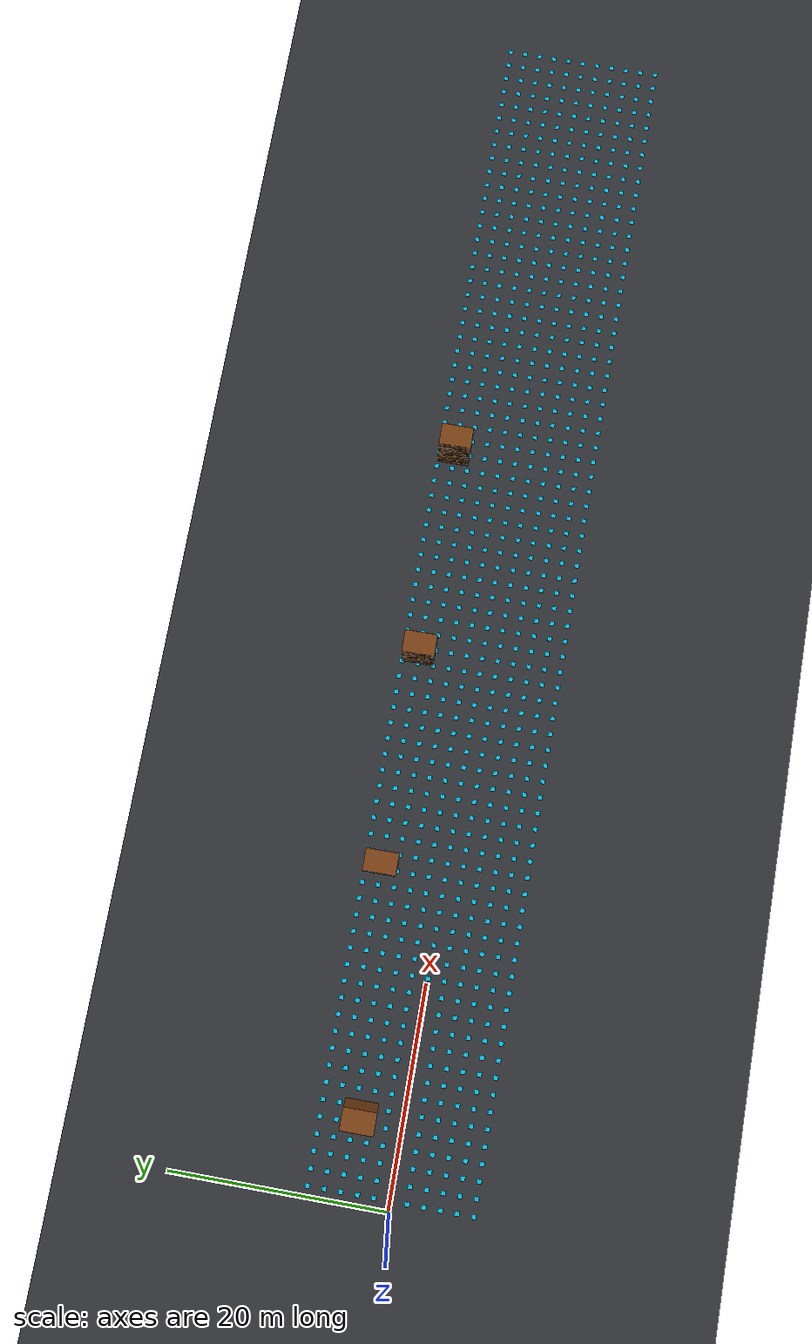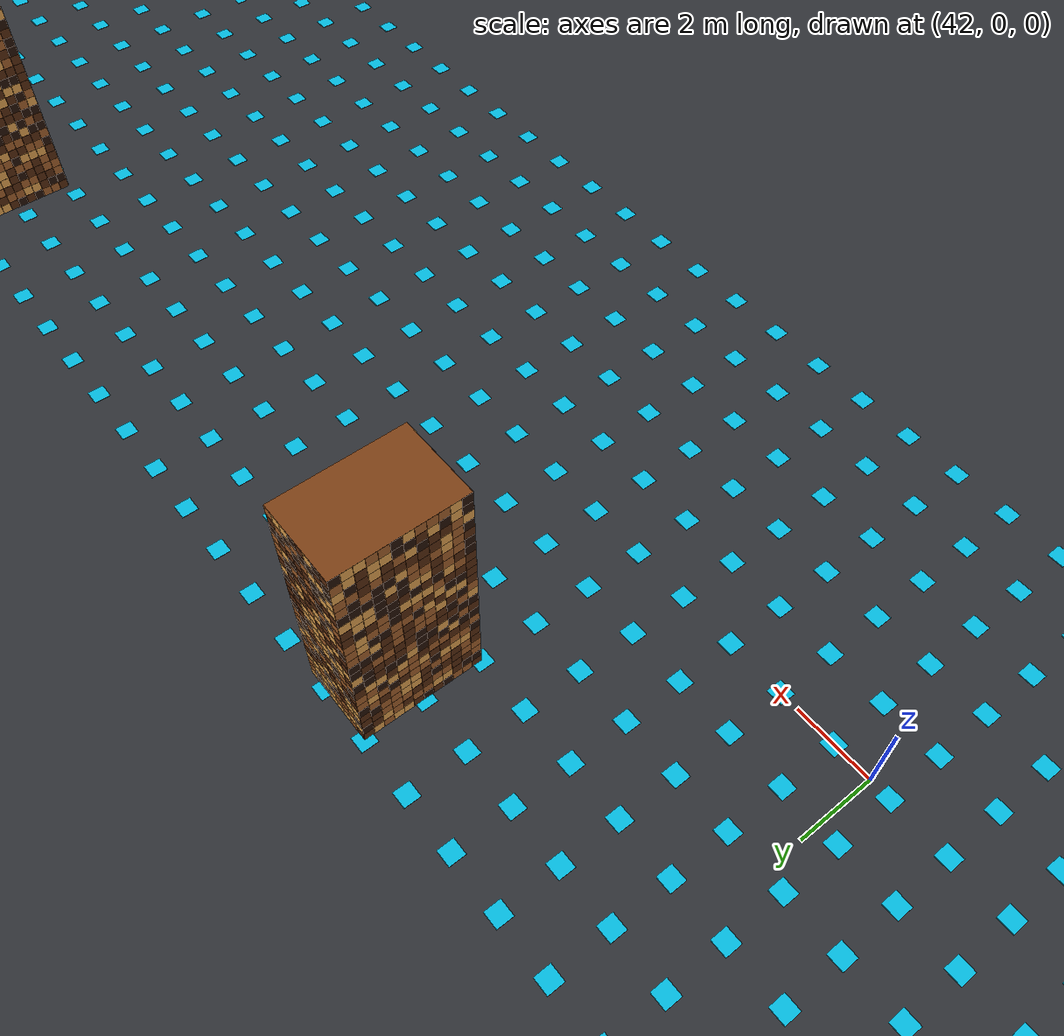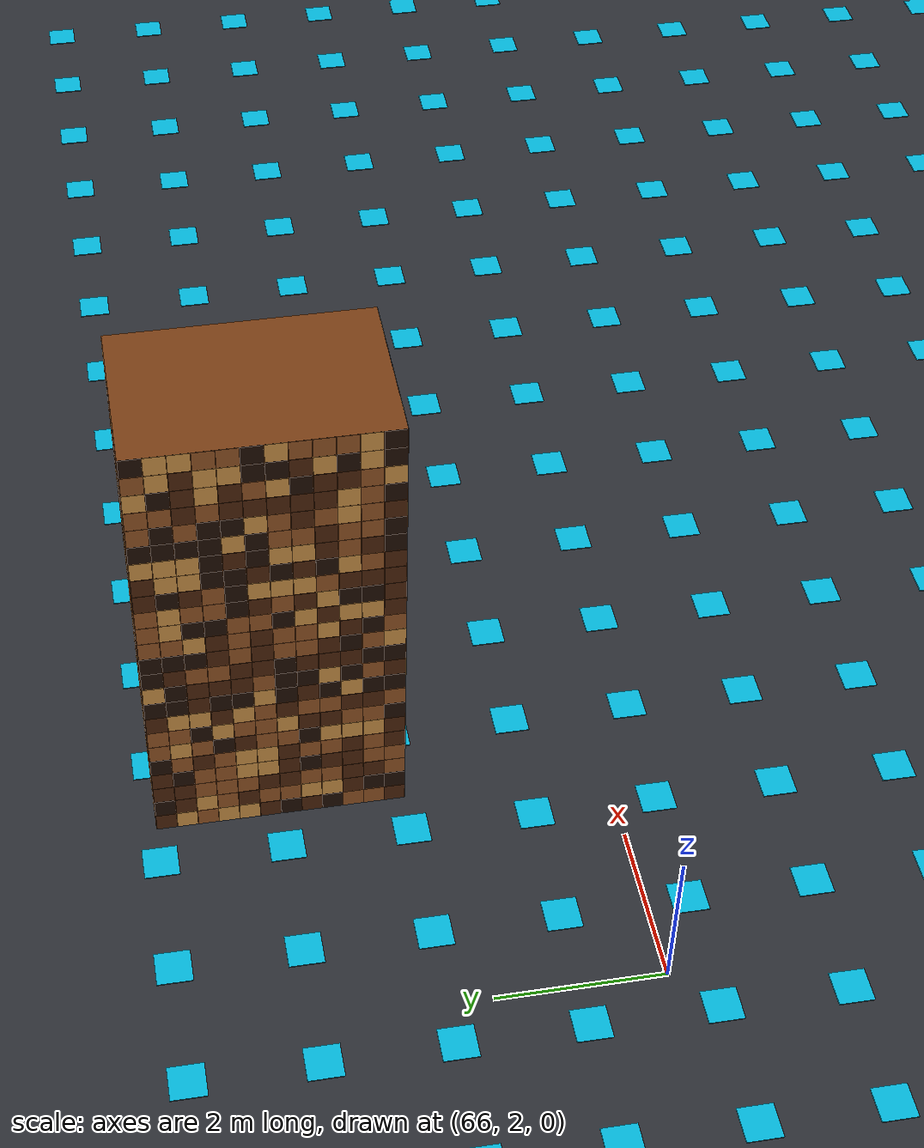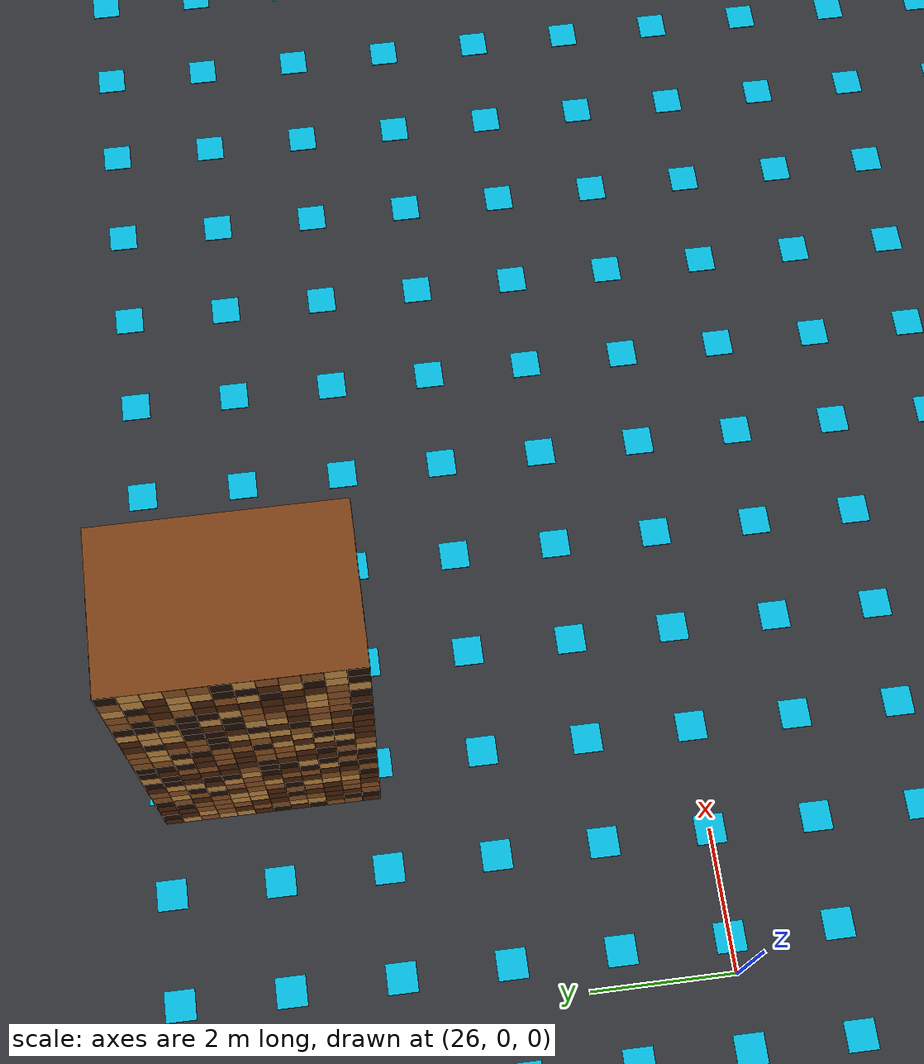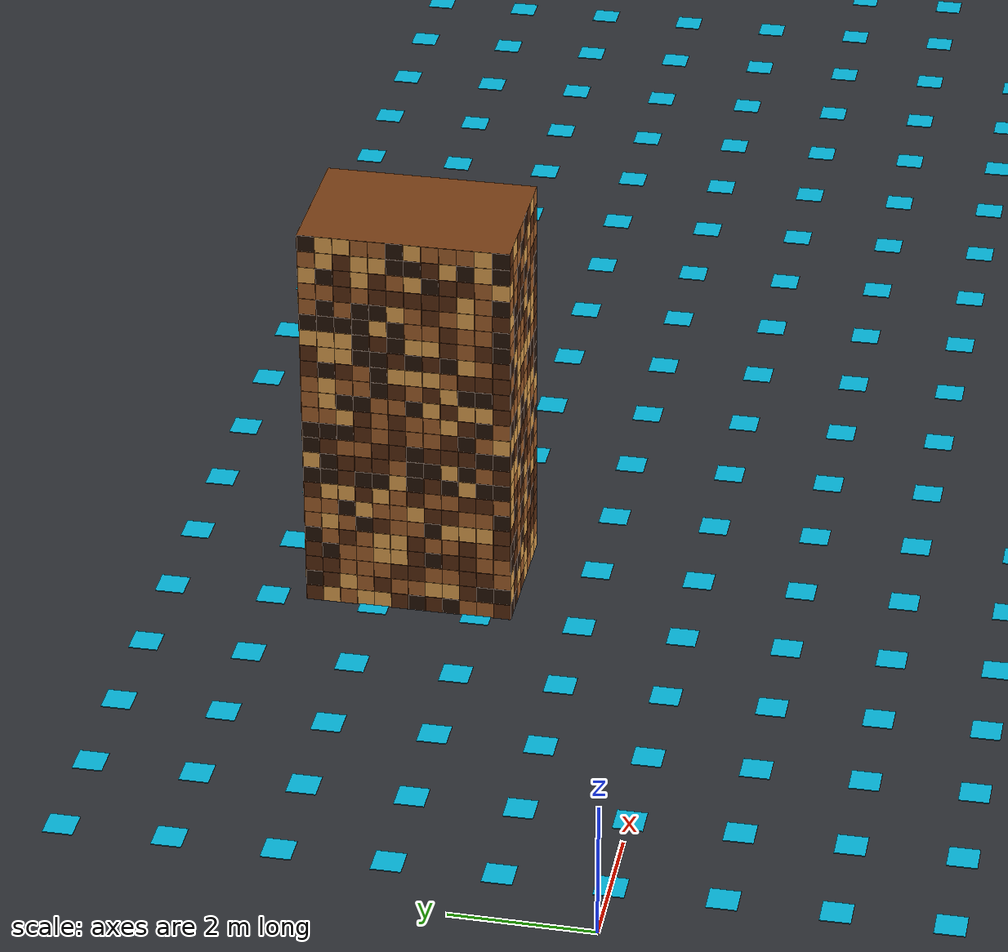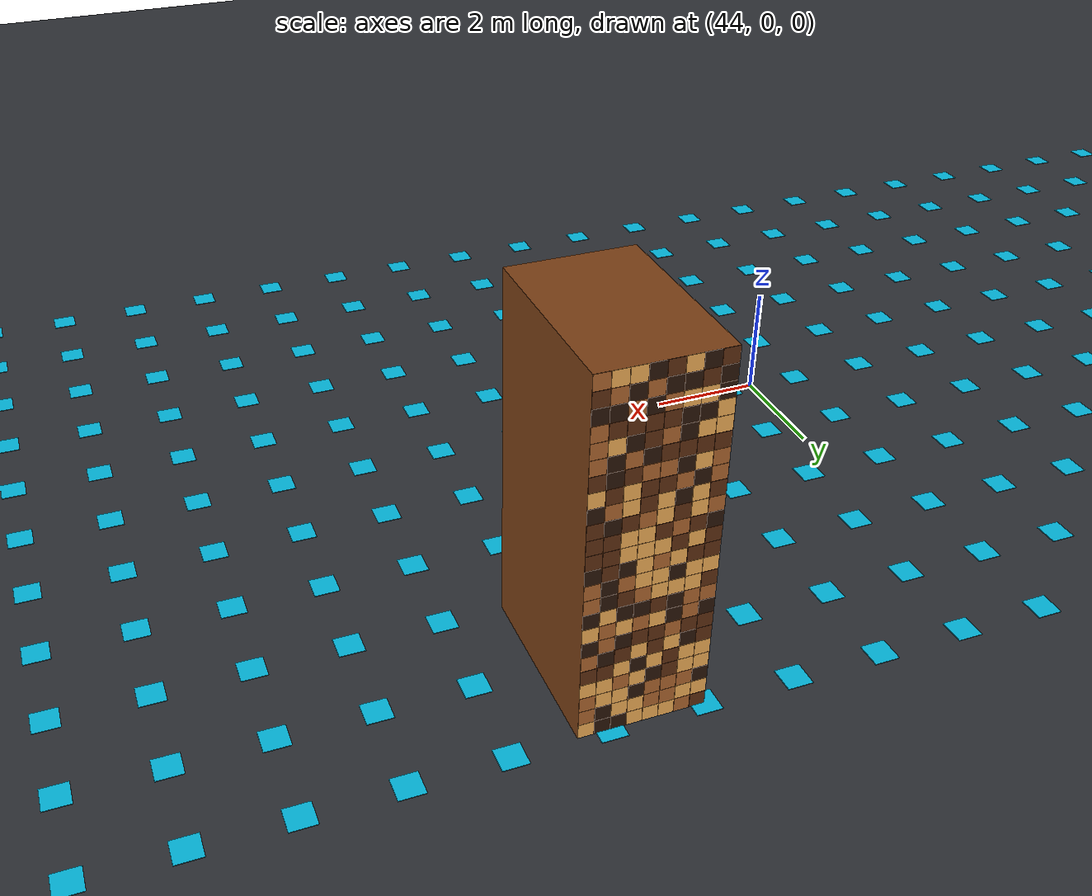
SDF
<sdf version="1.9">
 <world name="monocular_visual_highspeed_10">
  <physics name="1ms" type="ignore">
   <max_step_size>0.001</max_step_size>
   <real_time_factor>1.0</real_time_factor>
  </physics>
  <plugin filename="gz-sim-physics-system" name="gz::sim::systems::Physics"/>
  <plugin filename="gz-sim-sensors-system" name="gz::sim::systems::Sensors">
   <render_engine>ogre2</render_engine>
  </plugin>
  <plugin filename="gz-sim-user-commands-system" name="gz::sim::systems::UserCommands"/>
  <plugin filename="gz-sim-scene-broadcaster-system" name="gz::sim::systems::SceneBroadcaster"/>
  <plugin filename="gz-sim-imu-system" name="gz::sim::systems::Imu"/>
  <plugin filename="gz-sim-magnetometer-system" name="gz::sim::systems::Magnetometer"/>
  <plugin filename="gz-sim-air-pressure-system" name="gz::sim::systems::AirPressure"/>
  <plugin filename="gz-sim-navsat-system" name="gz::sim::systems::NavSat"/>
  <spherical_coordinates>
   <surface_model>EARTH_WGS84</surface_model>
   <latitude_deg>-35.363262</latitude_deg>
   <longitude_deg>149.165237</longitude_deg>
   <elevation>584</elevation>
   <heading_deg>0</heading_deg>
  </spherical_coordinates>
  <magnetic_field>2.1e-5 5.0e-6 -4.2e-5</magnetic_field>
  <scene><ambient>0.45 0.45 0.45 1</ambient><background>0.08 0.1 0.14 1</background><grid>true</grid></scene>
  <light type="directional" name="sun">
   <pose>0 0 40 0 0 0</pose>
   <diffuse>0.9 0.9 0.9 1</diffuse>
   <direction>-0.4 0.2 -1</direction>
  </light>
  <model name="asphalt">
   <static>true</static>
   <pose>150 0 -0.15 0 0 0</pose>
   <link name="body">
    <collision name="collision"><geometry><box><size>400 60 0.3</size></box></geometry></collision>
    <visual name="visual">
     <geometry><box><size>400 60 0.3</size></box></geometry>
     <material><ambient>.19 .20 .22 1</ambient><diffuse>.19 .20 .22 1</diffuse></material>
    </visual>
    <visual name="ground_marker_0_0">
     <pose>-149.000 -7.500 0.156 0 0 0</pose>
     <geometry><box><size>0.42 0.42 0.012</size></box></geometry>
     <material><ambient>0.02 0.75 0.9 1</ambient><diffuse>0.02 0.75 0.9 1</diffuse></material>
    </visual>
    <visual name="ground_marker_0_1">
     <pose>-149.000 -6.000 0.156 0 0 0</pose>
     <geometry><box><size>0.42 0.42 0.012</size></box></geometry>
     <material><ambient>0.02 0.75 0.9 1</ambient><diffuse>0.02 0.75 0.9 1</diffuse></material>
    </visual>
    <visual name="ground_marker_0_2">
     <pose>-149.000 -4.500 0.156 0 0 0</pose>
     <geometry><box><size>0.42 0.42 0.012</size></box></geometry>
     <material><ambient>0.02 0.75 0.9 1</ambient><diffuse>0.02 0.75 0.9 1</diffuse></material>
    </visual>
    <visual name="ground_marker_0_3">
     <pose>-149.000 -3.000 0.156 0 0 0</pose>
     <geometry><box><size>0.42 0.42 0.012</size></box></geometry>
     <material><ambient>0.02 0.75 0.9 1</ambient><diffuse>0.02 0.75 0.9 1</diffuse></material>
    </visual>
    <visual name="ground_marker_0_4">
     <pose>-149.000 -1.500 0.156 0 0 0</pose>
     <geometry><box><size>0.42 0.42 0.012</size></box></geometry>
     <material><ambient>0.02 0.75 0.9 1</ambient><diffuse>0.02 0.75 0.9 1</diffuse></material>
    </visual>
    <visual name="ground_marker_0_5">
     <pose>-149.000 0.000 0.156 0 0 0</pose>
     <geometry><box><size>0.42 0.42 0.012</size></box></geometry>
     <material><ambient>0.02 0.75 0.9 1</ambient><diffuse>0.02 0.75 0.9 1</diffuse></material>
    </visual>
    <visual name="ground_marker_0_6">
     <pose>-149.000 1.500 0.156 0 0 0</pose>
     <geometry><box><size>0.42 0.42 0.012</size></box></geometry>
     <material><ambient>0.02 0.75 0.9 1</ambient><diffuse>0.02 0.75 0.9 1</diffuse></material>
    </visual>
    <visual name="ground_marker_0_7">
     <pose>-149.000 3.000 0.156 0 0 0</pose>
     <geometry><box><size>0.42 0.42 0.012</size></box></geometry>
     <material><ambient>0.02 0.75 0.9 1</ambient><diffuse>0.02 0.75 0.9 1</diffuse></material>
    </visual>
    <visual name="ground_marker_0_8">
     <pose>-149.000 4.500 0.156 0 0 0</pose>
     <geometry><box><size>0.42 0.42 0.012</size></box></geometry>
     <material><ambient>0.02 0.75 0.9 1</ambient><diffuse>0.02 0.75 0.9 1</diffuse></material>
    </visual>
    <visual name="ground_marker_0_9">
     <pose>-149.000 6.000 0.156 0 0 0</pose>
     <geometry><box><size>0.42 0.42 0.012</size></box></geometry>
     <material><ambient>0.02 0.75 0.9 1</ambient><diffuse>0.02 0.75 0.9 1</diffuse></material>
    </visual>
    <visual name="ground_marker_0_10">
     <pose>-149.000 7.500 0.156 0 0 0</pose>
     <geometry><box><size>0.42 0.42 0.012</size></box></geometry>
     <material><ambient>0.02 0.75 0.9 1</ambient><diffuse>0.02 0.75 0.9 1</diffuse></material>
    </visual>
    <visual name="ground_marker_1_0">
     <pose>-147.500 -7.500 0.156 0 0 0</pose>
     <geometry><box><size>0.42 0.42 0.012</size></box></geometry>
     <material><ambient>0.02 0.75 0.9 1</ambient><diffuse>0.02 0.75 0.9 1</diffuse></material>
    </visual>
    <visual name="ground_marker_1_1">
     <pose>-147.500 -6.000 0.156 0 0 0</pose>
     <geometry><box><size>0.42 0.42 0.012</size></box></geometry>
     <material><ambient>0.02 0.75 0.9 1</ambient><diffuse>0.02 0.75 0.9 1</diffuse></material>
    </visual>
    <visual name="ground_marker_1_2">
     <pose>-147.500 -4.500 0.156 0 0 0</pose>
     <geometry><box><size>0.42 0.42 0.012</size></box></geometry>
     <material><ambient>0.02 0.75 0.9 1</ambient><diffuse>0.02 0.75 0.9 1</diffuse></material>
    </visual>
    <visual name="ground_marker_1_3">
     <pose>-147.500 -3.000 0.156 0 0 0</pose>
     <geometry><box><size>0.42 0.42 0.012</size></box></geometry>
     <material><ambient>0.02 0.75 0.9 1</ambient><diffuse>0.02 0.75 0.9 1</diffuse></material>
    </visual>
    <visual name="ground_marker_1_4">
     <pose>-147.500 -1.500 0.156 0 0 0</pose>
     <geometry><box><size>0.42 0.42 0.012</size></box></geometry>
     <material><ambient>0.02 0.75 0.9 1</ambient><diffuse>0.02 0.75 0.9 1</diffuse></material>
    </visual>
    <visual name="ground_marker_1_5">
     <pose>-147.500 0.000 0.156 0 0 0</pose>
     <geometry><box><size>0.42 0.42 0.012</size></box></geometry>
     <material><ambient>0.02 0.75 0.9 1</ambient><diffuse>0.02 0.75 0.9 1</diffuse></material>
    </visual>
    <visual name="ground_marker_1_6">
     <pose>-147.500 1.500 0.156 0 0 0</pose>
     <geometry><box><size>0.42 0.42 0.012</size></box></geometry>
     <material><ambient>0.02 0.75 0.9 1</ambient><diffuse>0.02 0.75 0.9 1</diffuse></material>
    </visual>
    <visual name="ground_marker_1_7">
     <pose>-147.500 3.000 0.156 0 0 0</pose>
     <geometry><box><size>0.42 0.42 0.012</size></box></geometry>
     <material><ambient>0.02 0.75 0.9 1</ambient><diffuse>0.02 0.75 0.9 1</diffuse></material>
    </visual>
    <visual name="ground_marker_1_8">
     <pose>-147.500 4.500 0.156 0 0 0</pose>
     <geometry><box><size>0.42 0.42 0.012</size></box></geometry>
     <material><ambient>0.02 0.75 0.9 1</ambient><diffuse>0.02 0.75 0.9 1</diffuse></material>
    </visual>
    <visual name="ground_marker_1_9">
     <pose>-147.500 6.000 0.156 0 0 0</pose>
     <geometry><box><size>0.42 0.42 0.012</size></box></geometry>
     <material><ambient>0.02 0.75 0.9 1</ambient><diffuse>0.02 0.75 0.9 1</diffuse></material>
    </visual>
    <visual name="ground_marker_1_10">
     <pose>-147.500 7.500 0.156 0 0 0</pose>
     <geometry><box><size>0.42 0.42 0.012</size></box></geometry>
     <material><ambient>0.02 0.75 0.9 1</ambient><diffuse>0.02 0.75 0.9 1</diffuse></material>
    </visual>
    <visual name="ground_marker_2_0">
     <pose>-146.000 -7.500 0.156 0 0 0</pose>
     <geometry><box><size>0.42 0.42 0.012</size></box></geometry>
     <material><ambient>0.02 0.75 0.9 1</ambient><diffuse>0.02 0.75 0.9 1</diffuse></material>
    </visual>
    <visual name="ground_marker_2_1">
     <pose>-146.000 -6.000 0.156 0 0 0</pose>
     <geometry><box><size>0.42 0.42 0.012</size></box></geometry>
     <material><ambient>0.02 0.75 0.9 1</ambient><diffuse>0.02 0.75 0.9 1</diffuse></material>
    </visual>
    <visual name="ground_marker_2_2">
     <pose>-146.000 -4.500 0.156 0 0 0</pose>
     <geometry><box><size>0.42 0.42 0.012</size></box></geometry>
     <material><ambient>0.02 0.75 0.9 1</ambient><diffuse>0.02 0.75 0.9 1</diffuse></material>
    </visual>
    <visual name="ground_marker_2_3">
     <pose>-146.000 -3.000 0.156 0 0 0</pose>
     <geometry><box><size>0.42 0.42 0.012</size></box></geometry>
     <material><ambient>0.02 0.75 0.9 1</ambient><diffuse>0.02 0.75 0.9 1</diffuse></material>
    </visual>
    <visual name="ground_marker_2_4">
     <pose>-146.000 -1.500 0.156 0 0 0</pose>
     <geometry><box><size>0.42 0.42 0.012</size></box></geometry>
     <material><ambient>0.02 0.75 0.9 1</ambient><diffuse>0.02 0.75 0.9 1</diffuse></material>
    </visual>
    <visual name="ground_marker_2_5">
     <pose>-146.000 0.000 0.156 0 0 0</pose>
     <geometry><box><size>0.42 0.42 0.012</size></box></geometry>
     <material><ambient>0.02 0.75 0.9 1</ambient><diffuse>0.02 0.75 0.9 1</diffuse></material>
    </visual>
    <visual name="ground_marker_2_6">
     <pose>-146.000 1.500 0.156 0 0 0</pose>
     <geometry><box><size>0.42 0.42 0.012</size></box></geometry>
     <material><ambient>0.02 0.75 0.9 1</ambient><diffuse>0.02 0.75 0.9 1</diffuse></material>
    </visual>
    <visual name="ground_marker_2_7">
     <pose>-146.000 3.000 0.156 0 0 0</pose>
     <geometry><box><size>0.42 0.42 0.012</size></box></geometry>
     <material><ambient>0.02 0.75 0.9 1</ambient><diffuse>0.02 0.75 0.9 1</diffuse></material>
    </visual>
    <visual name="ground_marker_2_8">
     <pose>-146.000 4.500 0.156 0 0 0</pose>
     <geometry><box><size>0.42 0.42 0.012</size></box></geometry>
     <material><ambient>0.02 0.75 0.9 1</ambient><diffuse>0.02 0.75 0.9 1</diffuse></material>
    </visual>
    <visual name="ground_marker_2_9">
     <pose>-146.000 6.000 0.156 0 0 0</pose>
     <geometry><box><size>0.42 0.42 0.012</size></box></geometry>
     <material><ambient>0.02 0.75 0.9 1</ambient><diffuse>0.02 0.75 0.9 1</diffuse></material>
    </visual>
    <visual name="ground_marker_2_10">
     <pose>-146.000 7.500 0.156 0 0 0</pose>
     <geometry><box><size>0.42 0.42 0.012</size></box></geometry>
     <material><ambient>0.02 0.75 0.9 1</ambient><diffuse>0.02 0.75 0.9 1</diffuse></material>
    </visual>
    <visual name="ground_marker_3_0">
     <pose>-144.500 -7.500 0.156 0 0 0</pose>
     <geometry><box><size>0.42 0.42 0.012</size></box></geometry>
     <material><ambient>0.02 0.75 0.9 1</ambient><diffuse>0.02 0.75 0.9 1</diffuse></material>
    </visual>
    <visual name="ground_marker_3_1">
     <pose>-144.500 -6.000 0.156 0 0 0</pose>
     <geometry><box><size>0.42 0.42 0.012</size></box></geometry>
     <material><ambient>0.02 0.75 0.9 1</ambient><diffuse>0.02 0.75 0.9 1</diffuse></material>
    </visual>
    <visual name="ground_marker_3_2">
     <pose>-144.500 -4.500 0.156 0 0 0</pose>
     <geometry><box><size>0.42 0.42 0.012</size></box></geometry>
     <material><ambient>0.02 0.75 0.9 1</ambient><diffuse>0.02 0.75 0.9 1</diffuse></material>
    </visual>
    <visual name="ground_marker_3_3">
     <pose>-144.500 -3.000 0.156 0 0 0</pose>
     <geometry><box><size>0.42 0.42 0.012</size></box></geometry>
     <material><ambient>0.02 0.75 0.9 1</ambient><diffuse>0.02 0.75 0.9 1</diffuse></material>
    </visual>
    <visual name="ground_marker_3_4">
     <pose>-144.500 -1.500 0.156 0 0 0</pose>
     <geometry><box><size>0.42 0.42 0.012</size></box></geometry>
     <material><ambient>0.02 0.75 0.9 1</ambient><diffuse>0.02 0.75 0.9 1</diffuse></material>
    </visual>
    <visual name="ground_marker_3_5">
     <pose>-144.500 0.000 0.156 0 0 0</pose>
     <geometry><box><size>0.42 0.42 0.012</size></box></geometry>
     <material><ambient>0.02 0.75 0.9 1</ambient><diffuse>0.02 0.75 0.9 1</diffuse></material>
    </visual>
    <visual name="ground_marker_3_6">
     <pose>-144.500 1.500 0.156 0 0 0</pose>
     <geometry><box><size>0.42 0.42 0.012</size></box></geometry>
     <material><ambient>0.02 0.75 0.9 1</ambient><diffuse>0.02 0.75 0.9 1</diffuse></material>
    </visual>
    <visual name="ground_marker_3_7">
     <pose>-144.500 3.000 0.156 0 0 0</pose>
     <geometry><box><size>0.42 0.42 0.012</size></box></geometry>
     <material><ambient>0.02 0.75 0.9 1</ambient><diffuse>0.02 0.75 0.9 1</diffuse></material>
    </visual>
    <visual name="ground_marker_3_8">
     <pose>-144.500 4.500 0.156 0 0 0</pose>
     <geometry><box><size>0.42 0.42 0.012</size></box></geometry>
     <material><ambient>0.02 0.75 0.9 1</ambient><diffuse>0.02 0.75 0.9 1</diffuse></material>
    </visual>
    <visual name="ground_marker_3_9">
     <pose>-144.500 6.000 0.156 0 0 0</pose>
     <geometry><box><size>0.42 0.42 0.012</size></box></geometry>
     <material><ambient>0.02 0.75 0.9 1</ambient><diffuse>0.02 0.75 0.9 1</diffuse></material>
    </visual>
    <visual name="ground_marker_3_10">
     <pose>-144.500 7.500 0.156 0 0 0</pose>
     <geometry><box><size>0.42 0.42 0.012</size></box></geometry>
     <material><ambient>0.02 0.75 0.9 1</ambient><diffuse>0.02 0.75 0.9 1</diffuse></material>
    </visual>
    <visual name="ground_marker_4_0">
     <pose>-143.000 -7.500 0.156 0 0 0</pose>
     <geometry><box><size>0.42 0.42 0.012</size></box></geometry>
     <material><ambient>0.02 0.75 0.9 1</ambient><diffuse>0.02 0.75 0.9 1</diffuse></material>
    </visual>
    <visual name="ground_marker_4_1">
     <pose>-143.000 -6.000 0.156 0 0 0</pose>
     <geometry><box><size>0.42 0.42 0.012</size></box></geometry>
     <material><ambient>0.02 0.75 0.9 1</ambient><diffuse>0.02 0.75 0.9 1</diffuse></material>
    </visual>
    <visual name="ground_marker_4_2">
     <pose>-143.000 -4.500 0.156 0 0 0</pose>
     <geometry><box><size>0.42 0.42 0.012</size></box></geometry>
     <material><ambient>0.02 0.75 0.9 1</ambient><diffuse>0.02 0.75 0.9 1</diffuse></material>
    </visual>
    <visual name="ground_marker_4_3">
     <pose>-143.000 -3.000 0.156 0 0 0</pose>
     <geometry><box><size>0.42 0.42 0.012</size></box></geometry>
     <material><ambient>0.02 0.75 0.9 1</ambient><diffuse>0.02 0.75 0.9 1</diffuse></material>
    </visual>
    <visual name="ground_marker_4_4">
     <pose>-143.000 -1.500 0.156 0 0 0</pose>
     <geometry><box><size>0.42 0.42 0.012</size></box></geometry>
     <material><ambient>0.02 0.75 0.9 1</ambient><diffuse>0.02 0.75 0.9 1</diffuse></material>
    </visual>
    <visual name="ground_marker_4_5">
     <pose>-143.000 0.000 0.156 0 0 0</pose>
     <geometry><box><size>0.42 0.42 0.012</size></box></geometry>
     <material><ambient>0.02 0.75 0.9 1</ambient><diffuse>0.02 0.75 0.9 1</diffuse></material>
    </visual>
    <visual name="ground_marker_4_6">
     <pose>-143.000 1.500 0.156 0 0 0</pose>
     <geometry><box><size>0.42 0.42 0.012</size></box></geometry>
     <material><ambient>0.02 0.75 0.9 1</ambient><diffuse>0.02 0.75 0.9 1</diffuse></material>
    </visual>
    <visual name="ground_marker_4_7">
     <pose>-143.000 3.000 0.156 0 0 0</pose>
     <geometry><box><size>0.42 0.42 0.012</size></box></geometry>
     <material><ambient>0.02 0.75 0.9 1</ambient><diffuse>0.02 0.75 0.9 1</diffuse></material>
    </visual>
    <visual name="ground_marker_4_8">
     <pose>-143.000 4.500 0.156 0 0 0</pose>
     <geometry><box><size>0.42 0.42 0.012</size></box></geometry>
     <material><ambient>0.02 0.75 0.9 1</ambient><diffuse>0.02 0.75 0.9 1</diffuse></material>
    </visual>
    <visual name="ground_marker_4_9">
     <pose>-143.000 6.000 0.156 0 0 0</pose>
     <geometry><box><size>0.42 0.42 0.012</size></box></geometry>
     <material><ambient>0.02 0.75 0.9 1</ambient><diffuse>0.02 0.75 0.9 1</diffuse></material>
    </visual>
    <visual name="ground_marker_4_10">
     <pose>-143.000 7.500 0.156 0 0 0</pose>
     <geometry><box><size>0.42 0.42 0.012</size></box></geometry>
     <material><ambient>0.02 0.75 0.9 1</ambient><diffuse>0.02 0.75 0.9 1</diffuse></material>
    </visual>
    <visual name="ground_marker_5_0">
     <pose>-141.500 -7.500 0.156 0 0 0</pose>
     <geometry><box><size>0.42 0.42 0.012</size></box></geometry>
     <material><ambient>0.02 0.75 0.9 1</ambient><diffuse>0.02 0.75 0.9 1</diffuse></material>
    </visual>
    <visual name="ground_marker_5_1">
     <pose>-141.500 -6.000 0.156 0 0 0</pose>
     <geometry><box><size>0.42 0.42 0.012</size></box></geometry>
     <material><ambient>0.02 0.75 0.9 1</ambient><diffuse>0.02 0.75 0.9 1</diffuse></material>
    </visual>
    <visual name="ground_marker_5_2">
     <pose>-141.500 -4.500 0.156 0 0 0</pose>
     <geometry><box><size>0.42 0.42 0.012</size></box></geometry>
     <material><ambient>0.02 0.75 0.9 1</ambient><diffuse>0.02 0.75 0.9 1</diffuse></material>
    </visual>
    <visual name="ground_marker_5_3">
     <pose>-141.500 -3.000 0.156 0 0 0</pose>
     <geometry><box><size>0.42 0.42 0.012</size></box></geometry>
     <material><ambient>0.02 0.75 0.9 1</ambient><diffuse>0.02 0.75 0.9 1</diffuse></material>
    </visual>
    <visual name="ground_marker_5_4">
     <pose>-141.500 -1.500 0.156 0 0 0</pose>
     <geometry><box><size>0.42 0.42 0.012</size></box></geometry>
     <material><ambient>0.02 0.75 0.9 1</ambient><diffuse>0.02 0.75 0.9 1</diffuse></material>
    </visual>
    <visual name="ground_marker_5_5">
     <pose>-141.500 0.000 0.156 0 0 0</pose>
     <geometry><box><size>0.42 0.42 0.012</size></box></geometry>
     <material><ambient>0.02 0.75 0.9 1</ambient><diffuse>0.02 0.75 0.9 1</diffuse></material>
    </visual>
    <visual name="ground_marker_5_6">
     <pose>-141.500 1.500 0.156 0 0 0</pose>
     <geometry><box><size>0.42 0.42 0.012</size></box></geometry>
     <material><ambient>0.02 0.75 0.9 1</ambient><diffuse>0.02 0.75 0.9 1</diffuse></material>
    </visual>
    <visual name="ground_marker_5_7">
     <pose>-141.500 3.000 0.156 0 0 0</pose>
     <geometry><box><size>0.42 0.42 0.012</size></box></geometry>
     <material><ambient>0.02 0.75 0.9 1</ambient><diffuse>0.02 0.75 0.9 1</diffuse></material>
    </visual>
    <visual name="ground_marker_5_8">
     <pose>-141.500 4.500 0.156 0 0 0</pose>
     <geometry><box><size>0.42 0.42 0.012</size></box></geometry>
     <material><ambient>0.02 0.75 0.9 1</ambient><diffuse>0.02 0.75 0.9 1</diffuse></material>
    </visual>
    <visual name="ground_marker_5_9">
     <pose>-141.500 6.000 0.156 0 0 0</pose>
     <geometry><box><size>0.42 0.42 0.012</size></box></geometry>
     <material><ambient>0.02 0.75 0.9 1</ambient><diffuse>0.02 0.75 0.9 1</diffuse></material>
    </visual>
    <visual name="ground_marker_5_10">
     <pose>-141.500 7.500 0.156 0 0 0</pose>
     <geometry><box><size>0.42 0.42 0.012</size></box></geometry>
     <material><ambient>0.02 0.75 0.9 1</ambient><diffuse>0.02 0.75 0.9 1</diffuse></material>
    </visual>
    <visual name="ground_marker_6_0">
     <pose>-140.000 -7.500 0.156 0 0 0</pose>
     <geometry><box><size>0.42 0.42 0.012</size></box></geometry>
     <material><ambient>0.02 0.75 0.9 1</ambient><diffuse>0.02 0.75 0.9 1</diffuse></material>
    </visual>
    <visual name="ground_marker_6_1">
     <pose>-140.000 -6.000 0.156 0 0 0</pose>
     <geometry><box><size>0.42 0.42 0.012</size></box></geometry>
     <material><ambient>0.02 0.75 0.9 1</ambient><diffuse>0.02 0.75 0.9 1</diffuse></material>
    </visual>
    <visual name="ground_marker_6_2">
     <pose>-140.000 -4.500 0.156 0 0 0</pose>
     <geometry><box><size>0.42 0.42 0.012</size></box></geometry>
     <material><ambient>0.02 0.75 0.9 1</ambient><diffuse>0.02 0.75 0.9 1</diffuse></material>
    </visual>
    <visual name="ground_marker_6_3">
     <pose>-140.000 -3.000 0.156 0 0 0</pose>
     <geometry><box><size>0.42 0.42 0.012</size></box></geometry>
     <material><ambient>0.02 0.75 0.9 1</ambient><diffuse>0.02 0.75 0.9 1</diffuse></material>
    </visual>
    <visual name="ground_marker_6_4">
     <pose>-140.000 -1.500 0.156 0 0 0</pose>
     <geometry><box><size>0.42 0.42 0.012</size></box></geometry>
     <material><ambient>0.02 0.75 0.9 1</ambient><diffuse>0.02 0.75 0.9 1</diffuse></material>
    </visual>
    <visual name="ground_marker_6_5">
     <pose>-140.000 0.000 0.156 0 0 0</pose>
     <geometry><box><size>0.42 0.42 0.012</size></box></geometry>
     <material><ambient>0.02 0.75 0.9 1</ambient><diffuse>0.02 0.75 0.9 1</diffuse></material>
    </visual>
    <visual name="ground_marker_6_6">
     <pose>-140.000 1.500 0.156 0 0 0</pose>
     <geometry><box><size>0.42 0.42 0.012</size></box></geometry>
     <material><ambient>0.02 0.75 0.9 1</ambient><diffuse>0.02 0.75 0.9 1</diffuse></material>
    </visual>
    <visual name="ground_marker_6_7">
     <pose>-140.000 3.000 0.156 0 0 0</pose>
     <geometry><box><size>0.42 0.42 0.012</size></box></geometry>
     <material><ambient>0.02 0.75 0.9 1</ambient><diffuse>0.02 0.75 0.9 1</diffuse></material>
    </visual>
    <visual name="ground_marker_6_8">
     <pose>-140.000 4.500 0.156 0 0 0</pose>
     <geometry><box><size>0.42 0.42 0.012</size></box></geometry>
     <material><ambient>0.02 0.75 0.9 1</ambient><diffuse>0.02 0.75 0.9 1</diffuse></material>
    </visual>
    <visual name="ground_marker_6_9">
     <pose>-140.000 6.000 0.156 0 0 0</pose>
     <geometry><box><size>0.42 0.42 0.012</size></box></geometry>
     <material><ambient>0.02 0.75 0.9 1</ambient><diffuse>0.02 0.75 0.9 1</diffuse></material>
    </visual>
    <visual name="ground_marker_6_10">
     <pose>-140.000 7.500 0.156 0 0 0</pose>
     <geometry><box><size>0.42 0.42 0.012</size></box></geometry>
     <material><ambient>0.02 0.75 0.9 1</ambient><diffuse>0.02 0.75 0.9 1</diffuse></material>
    </visual>
    <visual name="ground_marker_7_0">
     <pose>-138.500 -7.500 0.156 0 0 0</pose>
     <geometry><box><size>0.42 0.42 0.012</size></box></geometry>
     <material><ambient>0.02 0.75 0.9 1</ambient><diffuse>0.02 0.75 0.9 1</diffuse></material>
    </visual>
    <visual name="ground_marker_7_1">
     <pose>-138.500 -6.000 0.156 0 0 0</pose>
     <geometry><box><size>0.42 0.42 0.012</size></box></geometry>
     <material><ambient>0.02 0.75 0.9 1</ambient><diffuse>0.02 0.75 0.9 1</diffuse></material>
    </visual>
    <visual name="ground_marker_7_2">
     <pose>-138.500 -4.500 0.156 0 0 0</pose>
     <geometry><box><size>0.42 0.42 0.012</size></box></geometry>
     <material><ambient>0.02 0.75 0.9 1</ambient><diffuse>0.02 0.75 0.9 1</diffuse></material>
    </visual>
    <visual name="ground_marker_7_3">
     <pose>-138.500 -3.000 0.156 0 0 0</pose>
     <geometry><box><size>0.42 0.42 0.012</size></box></geometry>
     <material><ambient>0.02 0.75 0.9 1</ambient><diffuse>0.02 0.75 0.9 1</diffuse></material>
    </visual>
    <visual name="ground_marker_7_4">
     <pose>-138.500 -1.500 0.156 0 0 0</pose>
     <geometry><box><size>0.42 0.42 0.012</size></box></geometry>
     <material><ambient>0.02 0.75 0.9 1</ambient><diffuse>0.02 0.75 0.9 1</diffuse></material>
    </visual>
    <visual name="ground_marker_7_5">
     <pose>-138.500 0.000 0.156 0 0 0</pose>
     <geometry><box><size>0.42 0.42 0.012</size></box></geometry>
     <material><ambient>0.02 0.75 0.9 1</ambient><diffuse>0.02 0.75 0.9 1</diffuse></material>
    </visual>
    <visual name="ground_marker_7_6">
     <pose>-138.500 1.500 0.156 0 0 0</pose>
     <geometry><box><size>0.42 0.42 0.012</size></box></geometry>
     <material><ambient>0.02 0.75 0.9 1</ambient><diffuse>0.02 0.75 0.9 1</diffuse></material>
    </visual>
    <visual name="ground_marker_7_7">
     <pose>-138.500 3.000 0.156 0 0 0</pose>
     <geometry><box><size>0.42 0.42 0.012</size></box></geometry>
     <material><ambient>0.02 0.75 0.9 1</ambient><diffuse>0.02 0.75 0.9 1</diffuse></material>
    </visual>
    <visual name="ground_marker_7_8">
     <pose>-138.500 4.500 0.156 0 0 0</pose>
     <geometry><box><size>0.42 0.42 0.012</size></box></geometry>
     <material><ambient>0.02 0.75 0.9 1</ambient><diffuse>0.02 0.75 0.9 1</diffuse></material>
    </visual>
    <visual name="ground_marker_7_9">
     <pose>-138.500 6.000 0.156 0 0 0</pose>
     <geometry><box><size>0.42 0.42 0.012</size></box></geometry>
     <material><ambient>0.02 0.75 0.9 1</ambient><diffuse>0.02 0.75 0.9 1</diffuse></material>
    </visual>
    <visual name="ground_marker_7_10">
     <pose>-138.500 7.500 0.156 0 0 0</pose>
     <geometry><box><size>0.42 0.42 0.012</size></box></geometry>
     <material><ambient>0.02 0.75 0.9 1</ambient><diffuse>0.02 0.75 0.9 1</diffuse></material>
    </visual>
    <visual name="ground_marker_8_0">
     <pose>-137.000 -7.500 0.156 0 0 0</pose>
     <geometry><box><size>0.42 0.42 0.012</size></box></geometry>
     <material><ambient>0.02 0.75 0.9 1</ambient><diffuse>0.02 0.75 0.9 1</diffuse></material>
    </visual>
    <visual name="ground_marker_8_1">
     <pose>-137.000 -6.000 0.156 0 0 0</pose>
     <geometry><box><size>0.42 0.42 0.012</size></box></geometry>
     <material><ambient>0.02 0.75 0.9 1</ambient><diffuse>0.02 0.75 0.9 1</diffuse></material>
    </visual>
    <visual name="ground_marker_8_2">
     <pose>-137.000 -4.500 0.156 0 0 0</pose>
     <geometry><box><size>0.42 0.42 0.012</size></box></geometry>
     <material><ambient>0.02 0.75 0.9 1</ambient><diffuse>0.02 0.75 0.9 1</diffuse></material>
    </visual>
    <visual name="ground_marker_8_3">
     <pose>-137.000 -3.000 0.156 0 0 0</pose>
     <geometry><box><size>0.42 0.42 0.012</size></box></geometry>
     <material><ambient>0.02 0.75 0.9 1</ambient><diffuse>0.02 0.75 0.9 1</diffuse></material>
    </visual>
    <visual name="ground_marker_8_4">
     <pose>-137.000 -1.500 0.156 0 0 0</pose>
     <geometry><box><size>0.42 0.42 0.012</size></box></geometry>
     <material><ambient>0.02 0.75 0.9 1</ambient><diffuse>0.02 0.75 0.9 1</diffuse></material>
    </visual>
    <visual name="ground_marker_8_5">
     <pose>-137.000 0.000 0.156 0 0 0</pose>
     <geometry><box><size>0.42 0.42 0.012</size></box></geometry>
     <material><ambient>0.02 0.75 0.9 1</ambient><diffuse>0.02 0.75 0.9 1</diffuse></material>
    </visual>
    <visual name="ground_marker_8_6">
     <pose>-137.000 1.500 0.156 0 0 0</pose>
     <geometry><box><size>0.42 0.42 0.012</size></box></geometry>
     <material><ambient>0.02 0.75 0.9 1</ambient><diffuse>0.02 0.75 0.9 1</diffuse></material>
    </visual>
    <visual name="ground_marker_8_7">
     <pose>-137.000 3.000 0.156 0 0 0</pose>
     <geometry><box><size>0.42 0.42 0.012</size></box></geometry>
     <material><ambient>0.02 0.75 0.9 1</ambient><diffuse>0.02 0.75 0.9 1</diffuse></material>
    </visual>
    <visual name="ground_marker_8_8">
     <pose>-137.000 4.500 0.156 0 0 0</pose>
     <geometry><box><size>0.42 0.42 0.012</size></box></geometry>
     <material><ambient>0.02 0.75 0.9 1</ambient><diffuse>0.02 0.75 0.9 1</diffuse></material>
    </visual>
    <visual name="ground_marker_8_9">
     <pose>-137.000 6.000 0.156 0 0 0</pose>
     <geometry><box><size>0.42 0.42 0.012</size></box></geometry>
     <material><ambient>0.02 0.75 0.9 1</ambient><diffuse>0.02 0.75 0.9 1</diffuse></material>
    </visual>
    <visual name="ground_marker_8_10">
     <pose>-137.000 7.500 0.156 0 0 0</pose>
     <geometry><box><size>0.42 0.42 0.012</size></box></geometry>
     <material><ambient>0.02 0.75 0.9 1</ambient><diffuse>0.02 0.75 0.9 1</diffuse></material>
    </visual>
    <visual name="ground_marker_9_0">
     <pose>-135.500 -7.500 0.156 0 0 0</pose>
     <geometry><box><size>0.42 0.42 0.012</size></box></geometry>
     <material><ambient>0.02 0.75 0.9 1</ambient><diffuse>0.02 0.75 0.9 1</diffuse></material>
    </visual>
    <visual name="ground_marker_9_1">
     <pose>-135.500 -6.000 0.156 0 0 0</pose>
     <geometry><box><size>0.42 0.42 0.012</size></box></geometry>
     <material><ambient>0.02 0.75 0.9 1</ambient><diffuse>0.02 0.75 0.9 1</diffuse></material>
    </visual>
    <visual name="ground_marker_9_2">
     <pose>-135.500 -4.500 0.156 0 0 0</pose>
     <geometry><box><size>0.42 0.42 0.012</size></box></geometry>
     <material><ambient>0.02 0.75 0.9 1</ambient><diffuse>0.02 0.75 0.9 1</diffuse></material>
    </visual>
    <visual name="ground_marker_9_3">
     <pose>-135.500 -3.000 0.156 0 0 0</pose>
     <geometry><box><size>0.42 0.42 0.012</size></box></geometry>
     <material><ambient>0.02 0.75 0.9 1</ambient><diffuse>0.02 0.75 0.9 1</diffuse></material>
    </visual>
    <visual name="ground_marker_9_4">
     <pose>-135.500 -1.500 0.156 0 0 0</pose>
     <geometry><box><size>0.42 0.42 0.012</size></box></geometry>
     <material><ambient>0.02 0.75 0.9 1</ambient><diffuse>0.02 0.75 0.9 1</diffuse></material>
    </visual>
    <visual name="ground_marker_9_5">
     <pose>-135.500 0.000 0.156 0 0 0</pose>
     <geometry><box><size>0.42 0.42 0.012</size></box></geometry>
     <material><ambient>0.02 0.75 0.9 1</ambient><diffuse>0.02 0.75 0.9 1</diffuse></material>
    </visual>
    <visual name="ground_marker_9_6">
     <pose>-135.500 1.500 0.156 0 0 0</pose>
     <geometry><box><size>0.42 0.42 0.012</size></box></geometry>
     <material><ambient>0.02 0.75 0.9 1</ambient><diffuse>0.02 0.75 0.9 1</diffuse></material>
    </visual>
    <visual name="ground_marker_9_7">
     <pose>-135.500 3.000 0.156 0 0 0</pose>
     <geometry><box><size>0.42 0.42 0.012</size></box></geometry>
     <material><ambient>0.02 0.75 0.9 1</ambient><diffuse>0.02 0.75 0.9 1</diffuse></material>
    </visual>
    <visual name="ground_marker_9_8">
     <pose>-135.500 4.500 0.156 0 0 0</pose>
     <geometry><box><size>0.42 0.42 0.012</size></box></geometry>
     <material><ambient>0.02 0.75 0.9 1</ambient><diffuse>0.02 0.75 0.9 1</diffuse></material>
    </visual>
    <visual name="ground_marker_9_9">
     <pose>-135.500 6.000 0.156 0 0 0</pose>
     <geometry><box><size>0.42 0.42 0.012</size></box></geometry>
     <material><ambient>0.02 0.75 0.9 1</ambient><diffuse>0.02 0.75 0.9 1</diffuse></material>
    </visual>
    <visual name="ground_marker_9_10">
     <pose>-135.500 7.500 0.156 0 0 0</pose>
     <geometry><box><size>0.42 0.42 0.012</size></box></geometry>
     <material><ambient>0.02 0.75 0.9 1</ambient><diffuse>0.02 0.75 0.9 1</diffuse></material>
    </visual>
    <visual name="ground_marker_10_0">
     <pose>-134.000 -7.500 0.156 0 0 0</pose>
     <geometry><box><size>0.42 0.42 0.012</size></box></geometry>
     <material><ambient>0.02 0.75 0.9 1</ambient><diffuse>0.02 0.75 0.9 1</diffuse></material>
    </visual>
    <visual name="ground_marker_10_1">
     <pose>-134.000 -6.000 0.156 0 0 0</pose>
     <geometry><box><size>0.42 0.42 0.012</size></box></geometry>
     <material><ambient>0.02 0.75 0.9 1</ambient><diffuse>0.02 0.75 0.9 1</diffuse></material>
    </visual>
    <visual name="ground_marker_10_2">
     <pose>-134.000 -4.500 0.156 0 0 0</pose>
     <geometry><box><size>0.42 0.42 0.012</size></box></geometry>
     <material><ambient>0.02 0.75 0.9 1</ambient><diffuse>0.02 0.75 0.9 1</diffuse></material>
    </visual>
    <visual name="ground_marker_10_3">
     <pose>-134.000 -3.000 0.156 0 0 0</pose>
     <geometry><box><size>0.42 0.42 0.012</size></box></geometry>
     <material><ambient>0.02 0.75 0.9 1</ambient><diffuse>0.02 0.75 0.9 1</diffuse></material>
    </visual>
    <visual name="ground_marker_10_4">
     <pose>-134.000 -1.500 0.156 0 0 0</pose>
     <geometry><box><size>0.42 0.42 0.012</size></box></geometry>
     <material><ambient>0.02 0.75 0.9 1</ambient><diffuse>0.02 0.75 0.9 1</diffuse></material>
    </visual>
    <visual name="ground_marker_10_5">
     <pose>-134.000 0.000 0.156 0 0 0</pose>
     <geometry><box><size>0.42 0.42 0.012</size></box></geometry>
     <material><ambient>0.02 0.75 0.9 1</ambient><diffuse>0.02 0.75 0.9 1</diffuse></material>
    </visual>
    <visual name="ground_marker_10_6">
     <pose>-134.000 1.500 0.156 0 0 0</pose>
     <geometry><box><size>0.42 0.42 0.012</size></box></geometry>
     <material><ambient>0.02 0.75 0.9 1</ambient><diffuse>0.02 0.75 0.9 1</diffuse></material>
    </visual>
    <visual name="ground_marker_10_7">
     <pose>-134.000 3.000 0.156 0 0 0</pose>
     <geometry><box><size>0.42 0.42 0.012</size></box></geometry>
     <material><ambient>0.02 0.75 0.9 1</ambient><diffuse>0.02 0.75 0.9 1</diffuse></material>
    </visual>
    <visual name="ground_marker_10_8">
     <pose>-134.000 4.500 0.156 0 0 0</pose>
     <geometry><box><size>0.42 0.42 0.012</size></box></geometry>
     <material><ambient>0.02 0.75 0.9 1</ambient><diffuse>0.02 0.75 0.9 1</diffuse></material>
    </visual>
    <visual name="ground_marker_10_9">
     <pose>-134.000 6.000 0.156 0 0 0</pose>
     <geometry><box><size>0.42 0.42 0.012</size></box></geometry>
     <material><ambient>0.02 0.75 0.9 1</ambient><diffuse>0.02 0.75 0.9 1</diffuse></material>
    </visual>
    <visual name="ground_marker_10_10">
     <pose>-134.000 7.500 0.156 0 0 0</pose>
     <geometry><box><size>0.42 0.42 0.012</size></box></geometry>
     <material><ambient>0.02 0.75 0.9 1</ambient><diffuse>0.02 0.75 0.9 1</diffuse></material>
    </visual>
    <visual name="ground_marker_11_0">
     <pose>-132.500 -7.500 0.156 0 0 0</pose>
     <geometry><box><size>0.42 0.42 0.012</size></box></geometry>
     <material><ambient>0.02 0.75 0.9 1</ambient><diffuse>0.02 0.75 0.9 1</diffuse></material>
    </visual>
    <visual name="ground_marker_11_1">
     <pose>-132.500 -6.000 0.156 0 0 0</pose>
     <geometry><box><size>0.42 0.42 0.012</size></box></geometry>
     <material><ambient>0.02 0.75 0.9 1</ambient><diffuse>0.02 0.75 0.9 1</diffuse></material>
    </visual>
    <visual name="ground_marker_11_2">
     <pose>-132.500 -4.500 0.156 0 0 0</pose>
     <geometry><box><size>0.42 0.42 0.012</size></box></geometry>
     <material><ambient>0.02 0.75 0.9 1</ambient><diffuse>0.02 0.75 0.9 1</diffuse></material>
    </visual>
    <visual name="ground_marker_11_3">
     <pose>-132.500 -3.000 0.156 0 0 0</pose>
     <geometry><box><size>0.42 0.42 0.012</size></box></geometry>
     <material><ambient>0.02 0.75 0.9 1</ambient><diffuse>0.02 0.75 0.9 1</diffuse></material>
    </visual>
    <visual name="ground_marker_11_4">
     <pose>-132.500 -1.500 0.156 0 0 0</pose>
     <geometry><box><size>0.42 0.42 0.012</size></box></geometry>
     <material><ambient>0.02 0.75 0.9 1</ambient><diffuse>0.02 0.75 0.9 1</diffuse></material>
    </visual>
    <visual name="ground_marker_11_5">
     <pose>-132.500 0.000 0.156 0 0 0</pose>
     <geometry><box><size>0.42 0.42 0.012</size></box></geometry>
     <material><ambient>0.02 0.75 0.9 1</ambient><diffuse>0.02 0.75 0.9 1</diffuse></material>
    </visual>
    <visual name="ground_marker_11_6">
     <pose>-132.500 1.500 0.156 0 0 0</pose>
     <geometry><box><size>0.42 0.42 0.012</size></box></geometry>
     <material><ambient>0.02 0.75 0.9 1</ambient><diffuse>0.02 0.75 0.9 1</diffuse></material>
    </visual>
    <visual name="ground_marker_11_7">
     <pose>-132.500 3.000 0.156 0 0 0</pose>
     <geometry><box><size>0.42 0.42 0.012</size></box></geometry>
     <material><ambient>0.02 0.75 0.9 1</ambient><diffuse>0.02 0.75 0.9 1</diffuse></material>
    </visual>
    <visual name="ground_marker_11_8">
     <pose>-132.500 4.500 0.156 0 0 0</pose>
     <geometry><box><size>0.42 0.42 0.012</size></box></geometry>
     <material><ambient>0.02 0.75 0.9 1</ambient><diffuse>0.02 0.75 0.9 1</diffuse></material>
    </visual>
    <visual name="ground_marker_11_9">
     <pose>-132.500 6.000 0.156 0 0 0</pose>
     <geometry><box><size>0.42 0.42 0.012</size></box></geometry>
     <material><ambient>0.02 0.75 0.9 1</ambient><diffuse>0.02 0.75 0.9 1</diffuse></material>
    </visual>
    <visual name="ground_marker_11_10">
     <pose>-132.500 7.500 0.156 0 0 0</pose>
     <geometry><box><size>0.42 0.42 0.012</size></box></geometry>
     <material><ambient>0.02 0.75 0.9 1</ambient><diffuse>0.02 0.75 0.9 1</diffuse></material>
    </visual>
    <visual name="ground_marker_12_0">
     <pose>-131.000 -7.500 0.156 0 0 0</pose>
     <geometry><box><size>0.42 0.42 0.012</size></box></geometry>
     <material><ambient>0.02 0.75 0.9 1</ambient><diffuse>0.02 0.75 0.9 1</diffuse></material>
    </visual>
    <visual name="ground_marker_12_1">
     <pose>-131.000 -6.000 0.156 0 0 0</pose>
     <geometry><box><size>0.42 0.42 0.012</size></box></geometry>
     <material><ambient>0.02 0.75 0.9 1</ambient><diffuse>0.02 0.75 0.9 1</diffuse></material>
    </visual>
    <visual name="ground_marker_12_2">
     <pose>-131.000 -4.500 0.156 0 0 0</pose>
     <geometry><box><size>0.42 0.42 0.012</size></box></geometry>
     <material><ambient>0.02 0.75 0.9 1</ambient><diffuse>0.02 0.75 0.9 1</diffuse></material>
    </visual>
    <visual name="ground_marker_12_3">
     <pose>-131.000 -3.000 0.156 0 0 0</pose>
     <geometry><box><size>0.42 0.42 0.012</size></box></geometry>
     <material><ambient>0.02 0.75 0.9 1</ambient><diffuse>0.02 0.75 0.9 1</diffuse></material>
    </visual>
    <visual name="ground_marker_12_4">
     <pose>-131.000 -1.500 0.156 0 0 0</pose>
     <geometry><box><size>0.42 0.42 0.012</size></box></geometry>
     <material><ambient>0.02 0.75 0.9 1</ambient><diffuse>0.02 0.75 0.9 1</diffuse></material>
    </visual>
    <visual name="ground_marker_12_5">
     <pose>-131.000 0.000 0.156 0 0 0</pose>
     <geometry><box><size>0.42 0.42 0.012</size></box></geometry>
     <material><ambient>0.02 0.75 0.9 1</ambient><diffuse>0.02 0.75 0.9 1</diffuse></material>
    </visual>
    <visual name="ground_marker_12_6">
     <pose>-131.000 1.500 0.156 0 0 0</pose>
     <geometry><box><size>0.42 0.42 0.012</size></box></geometry>
     <material><ambient>0.02 0.75 0.9 1</ambient><diffuse>0.02 0.75 0.9 1</diffuse></material>
    </visual>
    <visual name="ground_marker_12_7">
     <pose>-131.000 3.000 0.156 0 0 0</pose>
     <geometry><box><size>0.42 0.42 0.012</size></box></geometry>
     <material><ambient>0.02 0.75 0.9 1</ambient><diffuse>0.02 0.75 0.9 1</diffuse></material>
    </visual>
    <visual name="ground_marker_12_8">
     <pose>-131.000 4.500 0.156 0 0 0</pose>
     <geometry><box><size>0.42 0.42 0.012</size></box></geometry>
     <material><ambient>0.02 0.75 0.9 1</ambient><diffuse>0.02 0.75 0.9 1</diffuse></material>
    </visual>
    <visual name="ground_marker_12_9">
     <pose>-131.000 6.000 0.156 0 0 0</pose>
     <geometry><box><size>0.42 0.42 0.012</size></box></geometry>
     <material><ambient>0.02 0.75 0.9 1</ambient><diffuse>0.02 0.75 0.9 1</diffuse></material>
    </visual>
    <visual name="ground_marker_12_10">
     <pose>-131.000 7.500 0.156 0 0 0</pose>
     <geometry><box><size>0.42 0.42 0.012</size></box></geometry>
     <material><ambient>0.02 0.75 0.9 1</ambient><diffuse>0.02 0.75 0.9 1</diffuse></material>
    </visual>
    <visual name="ground_marker_13_0">
     <pose>-129.500 -7.500 0.156 0 0 0</pose>
     <geometry><box><size>0.42 0.42 0.012</size></box></geometry>
     <material><ambient>0.02 0.75 0.9 1</ambient><diffuse>0.02 0.75 0.9 1</diffuse></material>
    </visual>
    <visual name="ground_marker_13_1">
     <pose>-129.500 -6.000 0.156 0 0 0</pose>
     <geometry><box><size>0.42 0.42 0.012</size></box></geometry>
     <material><ambient>0.02 0.75 0.9 1</ambient><diffuse>0.02 0.75 0.9 1</diffuse></material>
    </visual>
    <visual name="ground_marker_13_2">
     <pose>-129.500 -4.500 0.156 0 0 0</pose>
     <geometry><box><size>0.42 0.42 0.012</size></box></geometry>
     <material><ambient>0.02 0.75 0.9 1</ambient><diffuse>0.02 0.75 0.9 1</diffuse></material>
    </visual>
    <visual name="ground_marker_13_3">
     <pose>-129.500 -3.000 0.156 0 0 0</pose>
     <geometry><box><size>0.42 0.42 0.012</size></box></geometry>
     <material><ambient>0.02 0.75 0.9 1</ambient><diffuse>0.02 0.75 0.9 1</diffuse></material>
    </visual>
    <visual name="ground_marker_13_4">
     <pose>-129.500 -1.500 0.156 0 0 0</pose>
     <geometry><box><size>0.42 0.42 0.012</size></box></geometry>
     <material><ambient>0.02 0.75 0.9 1</ambient><diffuse>0.02 0.75 0.9 1</diffuse></material>
    </visual>
    <visual name="ground_marker_13_5">
     <pose>-129.500 0.000 0.156 0 0 0</pose>
     <geometry><box><size>0.42 0.42 0.012</size></box></geometry>
     <material><ambient>0.02 0.75 0.9 1</ambient><diffuse>0.02 0.75 0.9 1</diffuse></material>
    </visual>
    <visual name="ground_marker_13_6">
     <pose>-129.500 1.500 0.156 0 0 0</pose>
     <geometry><box><size>0.42 0.42 0.012</size></box></geometry>
     <material><ambient>0.02 0.75 0.9 1</ambient><diffuse>0.02 0.75 0.9 1</diffuse></material>
    </visual>
    <visual name="ground_marker_13_7">
     <pose>-129.500 3.000 0.156 0 0 0</pose>
     <geometry><box><size>0.42 0.42 0.012</size></box></geometry>
     <material><ambient>0.02 0.75 0.9 1</ambient><diffuse>0.02 0.75 0.9 1</diffuse></material>
    </visual>
    <visual name="ground_marker_13_8">
     <pose>-129.500 4.500 0.156 0 0 0</pose>
     <geometry><box><size>0.42 0.42 0.012</size></box></geometry>
     <material><ambient>0.02 0.75 0.9 1</ambient><diffuse>0.02 0.75 0.9 1</diffuse></material>
    </visual>
    <visual name="ground_marker_13_9">
     <pose>-129.500 6.000 0.156 0 0 0</pose>
     <geometry><box><size>0.42 0.42 0.012</size></box></geometry>
     <material><ambient>0.02 0.75 0.9 1</ambient><diffuse>0.02 0.75 0.9 1</diffuse></material>
    </visual>
    <visual name="ground_marker_13_10">
     <pose>-129.500 7.500 0.156 0 0 0</pose>
     <geometry><box><size>0.42 0.42 0.012</size></box></geometry>
     <material><ambient>0.02 0.75 0.9 1</ambient><diffuse>0.02 0.75 0.9 1</diffuse></material>
    </visual>
    <visual name="ground_marker_14_0">
     <pose>-128.000 -7.500 0.156 0 0 0</pose>
     <geometry><box><size>0.42 0.42 0.012</size></box></geometry>
     <material><ambient>0.02 0.75 0.9 1</ambient><diffuse>0.02 0.75 0.9 1</diffuse></material>
    </visual>
    <visual name="ground_marker_14_1">
     <pose>-128.000 -6.000 0.156 0 0 0</pose>
     <geometry><box><size>0.42 0.42 0.012</size></box></geometry>
     <material><ambient>0.02 0.75 0.9 1</ambient><diffuse>0.02 0.75 0.9 1</diffuse></material>
    </visual>
    <visual name="ground_marker_14_2">
     <pose>-128.000 -4.500 0.156 0 0 0</pose>
     <geometry><box><size>0.42 0.42 0.012</size></box></geometry>
     <material><ambient>0.02 0.75 0.9 1</ambient><diffuse>0.02 0.75 0.9 1</diffuse></material>
    </visual>
    <visual name="ground_marker_14_3">
     <pose>-128.000 -3.000 0.156 0 0 0</pose>
     <geometry><box><size>0.42 0.42 0.012</size></box></geometry>
     <material><ambient>0.02 0.75 0.9 1</ambient><diffuse>0.02 0.75 0.9 1</diffuse></material>
    </visual>
    <visual name="ground_marker_14_4">
     <pose>-128.000 -1.500 0.156 0 0 0</pose>
     <geometry><box><size>0.42 0.42 0.012</size></box></geometry>
     <material><ambient>0.02 0.75 0.9 1</ambient><diffuse>0.02 0.75 0.9 1</diffuse></material>
    </visual>
    <visual name="ground_marker_14_5">
     <pose>-128.000 0.000 0.156 0 0 0</pose>
     <geometry><box><size>0.42 0.42 0.012</size></box></geometry>
     <material><ambient>0.02 0.75 0.9 1</ambient><diffuse>0.02 0.75 0.9 1</diffuse></material>
    </visual>
    <visual name="ground_marker_14_6">
     <pose>-128.000 1.500 0.156 0 0 0</pose>
     <geometry><box><size>0.42 0.42 0.012</size></box></geometry>
     <material><ambient>0.02 0.75 0.9 1</ambient><diffuse>0.02 0.75 0.9 1</diffuse></material>
    </visual>
    <visual name="ground_marker_14_7">
     <pose>-128.000 3.000 0.156 0 0 0</pose>
     <geometry><box><size>0.42 0.42 0.012</size></box></geometry>
     <material><ambient>0.02 0.75 0.9 1</ambient><diffuse>0.02 0.75 0.9 1</diffuse></material>
    </visual>
    <visual name="ground_marker_14_8">
     <pose>-128.000 4.500 0.156 0 0 0</pose>
     <geometry><box><size>0.42 0.42 0.012</size></box></geometry>
     <material><ambient>0.02 0.75 0.9 1</ambient><diffuse>0.02 0.75 0.9 1</diffuse></material>
    </visual>
    <visual name="ground_marker_14_9">
     <pose>-128.000 6.000 0.156 0 0 0</pose>
     <geometry><box><size>0.42 0.42 0.012</size></box></geometry>
     <material><ambient>0.02 0.75 0.9 1</ambient><diffuse>0.02 0.75 0.9 1</diffuse></material>
    </visual>
    <visual name="ground_marker_14_10">
     <pose>-128.000 7.500 0.156 0 0 0</pose>
     <geometry><box><size>0.42 0.42 0.012</size></box></geometry>
     <material><ambient>0.02 0.75 0.9 1</ambient><diffuse>0.02 0.75 0.9 1</diffuse></material>
    </visual>
    <visual name="ground_marker_15_0">
     <pose>-126.500 -7.500 0.156 0 0 0</pose>
     <geometry><box><size>0.42 0.42 0.012</size></box></geometry>
     <material><ambient>0.02 0.75 0.9 1</ambient><diffuse>0.02 0.75 0.9 1</diffuse></material>
    </visual>
    <visual name="ground_marker_15_1">
     <pose>-126.500 -6.000 0.156 0 0 0</pose>
     <geometry><box><size>0.42 0.42 0.012</size></box></geometry>
     <material><ambient>0.02 0.75 0.9 1</ambient><diffuse>0.02 0.75 0.9 1</diffuse></material>
    </visual>
    <visual name="ground_marker_15_2">
     <pose>-126.500 -4.500 0.156 0 0 0</pose>
     <geometry><box><size>0.42 0.42 0.012</size></box></geometry>
     <material><ambient>0.02 0.75 0.9 1</ambient><diffuse>0.02 0.75 0.9 1</diffuse></material>
    </visual>
    <visual name="ground_marker_15_3">
     <pose>-126.500 -3.000 0.156 0 0 0</pose>
     <geometry><box><size>0.42 0.42 0.012</size></box></geometry>
     <material><ambient>0.02 0.75 0.9 1</ambient><diffuse>0.02 0.75 0.9 1</diffuse></material>
    </visual>
    <visual name="ground_marker_15_4">
     <pose>-126.500 -1.500 0.156 0 0 0</pose>
     <geometry><box><size>0.42 0.42 0.012</size></box></geometry>
     <material><ambient>0.02 0.75 0.9 1</ambient><diffuse>0.02 0.75 0.9 1</diffuse></material>
    </visual>
    <visual name="ground_marker_15_5">
     <pose>-126.500 0.000 0.156 0 0 0</pose>
     <geometry><box><size>0.42 0.42 0.012</size></box></geometry>
     <material><ambient>0.02 0.75 0.9 1</ambient><diffuse>0.02 0.75 0.9 1</diffuse></material>
    </visual>
    <visual name="ground_marker_15_6">
     <pose>-126.500 1.500 0.156 0 0 0</pose>
     <geometry><box><size>0.42 0.42 0.012</size></box></geometry>
     <material><ambient>0.02 0.75 0.9 1</ambient><diffuse>0.02 0.75 0.9 1</diffuse></material>
    </visual>
    <visual name="ground_marker_15_7">
     <pose>-126.500 3.000 0.156 0 0 0</pose>
     <geometry><box><size>0.42 0.42 0.012</size></box></geometry>
     <material><ambient>0.02 0.75 0.9 1</ambient><diffuse>0.02 0.75 0.9 1</diffuse></material>
    </visual>
    <visual name="ground_marker_15_8">
     <pose>-126.500 4.500 0.156 0 0 0</pose>
     <geometry><box><size>0.42 0.42 0.012</size></box></geometry>
     <material><ambient>0.02 0.75 0.9 1</ambient><diffuse>0.02 0.75 0.9 1</diffuse></material>
    </visual>
    <visual name="ground_marker_15_9">
     <pose>-126.500 6.000 0.156 0 0 0</pose>
     <geometry><box><size>0.42 0.42 0.012</size></box></geometry>
     <material><ambient>0.02 0.75 0.9 1</ambient><diffuse>0.02 0.75 0.9 1</diffuse></material>
    </visual>
    <visual name="ground_marker_15_10">
     <pose>-126.500 7.500 0.156 0 0 0</pose>
     <geometry><box><size>0.42 0.42 0.012</size></box></geometry>
     <material><ambient>0.02 0.75 0.9 1</ambient><diffuse>0.02 0.75 0.9 1</diffuse></material>
    </visual>
    <visual name="ground_marker_16_0">
     <pose>-125.000 -7.500 0.156 0 0 0</pose>
     <geometry><box><size>0.42 0.42 0.012</size></box></geometry>
     <material><ambient>0.02 0.75 0.9 1</ambient><diffuse>0.02 0.75 0.9 1</diffuse></material>
    </visual>
    <visual name="ground_marker_16_1">
     <pose>-125.000 -6.000 0.156 0 0 0</pose>
     <geometry><box><size>0.42 0.42 0.012</size></box></geometry>
     <material><ambient>0.02 0.75 0.9 1</ambient><diffuse>0.02 0.75 0.9 1</diffuse></material>
    </visual>
    <visual name="ground_marker_16_2">
     <pose>-125.000 -4.500 0.156 0 0 0</pose>
     <geometry><box><size>0.42 0.42 0.012</size></box></geometry>
     <material><ambient>0.02 0.75 0.9 1</ambient><diffuse>0.02 0.75 0.9 1</diffuse></material>
    </visual>
    <visual name="ground_marker_16_3">
     <pose>-125.000 -3.000 0.156 0 0 0</pose>
     <geometry><box><size>0.42 0.42 0.012</size></box></geometry>
     <material><ambient>0.02 0.75 0.9 1</ambient><diffuse>0.02 0.75 0.9 1</diffuse></material>
    </visual>
    <visual name="ground_marker_16_4">
     <pose>-125.000 -1.500 0.156 0 0 0</pose>
     <geometry><box><size>0.42 0.42 0.012</size></box></geometry>
     <material><ambient>0.02 0.75 0.9 1</ambient><diffuse>0.02 0.75 0.9 1</diffuse></material>
    </visual>
    <visual name="ground_marker_16_5">
     <pose>-125.000 0.000 0.156 0 0 0</pose>
     <geometry><box><size>0.42 0.42 0.012</size></box></geometry>
     <material><ambient>0.02 0.75 0.9 1</ambient><diffuse>0.02 0.75 0.9 1</diffuse></material>
    </visual>
    <visual name="ground_marker_16_6">
     <pose>-125.000 1.500 0.156 0 0 0</pose>
     <geometry><box><size>0.42 0.42 0.012</size></box></geometry>
     <material><ambient>0.02 0.75 0.9 1</ambient><diffuse>0.02 0.75 0.9 1</diffuse></material>
    </visual>
    <visual name="ground_marker_16_7">
     <pose>-125.000 3.000 0.156 0 0 0</pose>
     <geometry><box><size>0.42 0.42 0.012</size></box></geometry>
     <material><ambient>0.02 0.75 0.9 1</ambient><diffuse>0.02 0.75 0.9 1</diffuse></material>
    </visual>
    <visual name="ground_marker_16_8">
     <pose>-125.000 4.500 0.156 0 0 0</pose>
     <geometry><box><size>0.42 0.42 0.012</size></box></geometry>
     <material><ambient>0.02 0.75 0.9 1</ambient><diffuse>0.02 0.75 0.9 1</diffuse></material>
    </visual>
    <visual name="ground_marker_16_9">
     <pose>-125.000 6.000 0.156 0 0 0</pose>
     <geometry><box><size>0.42 0.42 0.012</size></box></geometry>
     <material><ambient>0.02 0.75 0.9 1</ambient><diffuse>0.02 0.75 0.9 1</diffuse></material>
    </visual>
    <visual name="ground_marker_16_10">
     <pose>-125.000 7.500 0.156 0 0 0</pose>
     <geometry><box><size>0.42 0.42 0.012</size></box></geometry>
     <material><ambient>0.02 0.75 0.9 1</ambient><diffuse>0.02 0.75 0.9 1</diffuse></material>
    </visual>
    <visual name="ground_marker_17_0">
     <pose>-123.500 -7.500 0.156 0 0 0</pose>
     <geometry><box><size>0.42 0.42 0.012</size></box></geometry>
     <material><ambient>0.02 0.75 0.9 1</ambient><diffuse>0.02 0.75 0.9 1</diffuse></material>
    </visual>
    <visual name="ground_marker_17_1">
     <pose>-123.500 -6.000 0.156 0 0 0</pose>
     <geometry><box><size>0.42 0.42 0.012</size></box></geometry>
     <material><ambient>0.02 0.75 0.9 1</ambient><diffuse>0.02 0.75 0.9 1</diffuse></material>
    </visual>
    <visual name="ground_marker_17_2">
     <pose>-123.500 -4.500 0.156 0 0 0</pose>
     <geometry><box><size>0.42 0.42 0.012</size></box></geometry>
     <material><ambient>0.02 0.75 0.9 1</ambient><diffuse>0.02 0.75 0.9 1</diffuse></material>
    </visual>
    <visual name="ground_marker_17_3">
     <pose>-123.500 -3.000 0.156 0 0 0</pose>
     <geometry><box><size>0.42 0.42 0.012</size></box></geometry>
     <material><ambient>0.02 0.75 0.9 1</ambient><diffuse>0.02 0.75 0.9 1</diffuse></material>
    </visual>
    <visual name="ground_marker_17_4">
     <pose>-123.500 -1.500 0.156 0 0 0</pose>
     <geometry><box><size>0.42 0.42 0.012</size></box></geometry>
     <material><ambient>0.02 0.75 0.9 1</ambient><diffuse>0.02 0.75 0.9 1</diffuse></material>
    </visual>
    <visual name="ground_marker_17_5">
     <pose>-123.500 0.000 0.156 0 0 0</pose>
     <geometry><box><size>0.42 0.42 0.012</size></box></geometry>
     <material><ambient>0.02 0.75 0.9 1</ambient><diffuse>0.02 0.75 0.9 1</diffuse></material>
    </visual>
    <visual name="ground_marker_17_6">
     <pose>-123.500 1.500 0.156 0 0 0</pose>
     <geometry><box><size>0.42 0.42 0.012</size></box></geometry>
     <material><ambient>0.02 0.75 0.9 1</ambient><diffuse>0.02 0.75 0.9 1</diffuse></material>
    </visual>
    <visual name="ground_marker_17_7">
     <pose>-123.500 3.000 0.156 0 0 0</pose>
     <geometry><box><size>0.42 0.42 0.012</size></box></geometry>
     <material><ambient>0.02 0.75 0.9 1</ambient><diffuse>0.02 0.75 0.9 1</diffuse></material>
    </visual>
    <visual name="ground_marker_17_8">
     <pose>-123.500 4.500 0.156 0 0 0</pose>
     <geometry><box><size>0.42 0.42 0.012</size></box></geometry>
     <material><ambient>0.02 0.75 0.9 1</ambient><diffuse>0.02 0.75 0.9 1</diffuse></material>
    </visual>
    <visual name="ground_marker_17_9">
     <pose>-123.500 6.000 0.156 0 0 0</pose>
     <geometry><box><size>0.42 0.42 0.012</size></box></geometry>
     <material><ambient>0.02 0.75 0.9 1</ambient><diffuse>0.02 0.75 0.9 1</diffuse></material>
    </visual>
    <visual name="ground_marker_17_10">
     <pose>-123.500 7.500 0.156 0 0 0</pose>
     <geometry><box><size>0.42 0.42 0.012</size></box></geometry>
     <material><ambient>0.02 0.75 0.9 1</ambient><diffuse>0.02 0.75 0.9 1</diffuse></material>
    </visual>
    <visual name="ground_marker_18_0">
     <pose>-122.000 -7.500 0.156 0 0 0</pose>
     <geometry><box><size>0.42 0.42 0.012</size></box></geometry>
     <material><ambient>0.02 0.75 0.9 1</ambient><diffuse>0.02 0.75 0.9 1</diffuse></material>
    </visual>
    <visual name="ground_marker_18_1">
     <pose>-122.000 -6.000 0.156 0 0 0</pose>
     <geometry><box><size>0.42 0.42 0.012</size></box></geometry>
     <material><ambient>0.02 0.75 0.9 1</ambient><diffuse>0.02 0.75 0.9 1</diffuse></material>
    </visual>
    <visual name="ground_marker_18_2">
     <pose>-122.000 -4.500 0.156 0 0 0</pose>
     <geometry><box><size>0.42 0.42 0.012</size></box></geometry>
     <material><ambient>0.02 0.75 0.9 1</ambient><diffuse>0.02 0.75 0.9 1</diffuse></material>
    </visual>
    <visual name="ground_marker_18_3">
     <pose>-122.000 -3.000 0.156 0 0 0</pose>
     <geometry><box><size>0.42 0.42 0.012</size></box></geometry>
     <material><ambient>0.02 0.75 0.9 1</ambient><diffuse>0.02 0.75 0.9 1</diffuse></material>
    </visual>
    <visual name="ground_marker_18_4">
     <pose>-122.000 -1.500 0.156 0 0 0</pose>
     <geometry><box><size>0.42 0.42 0.012</size></box></geometry>
     <material><ambient>0.02 0.75 0.9 1</ambient><diffuse>0.02 0.75 0.9 1</diffuse></material>
    </visual>
    <visual name="ground_marker_18_5">
     <pose>-122.000 0.000 0.156 0 0 0</pose>
     <geometry><box><size>0.42 0.42 0.012</size></box></geometry>
     <material><ambient>0.02 0.75 0.9 1</ambient><diffuse>0.02 0.75 0.9 1</diffuse></material>
    </visual>
    <visual name="ground_marker_18_6">
     <pose>-122.000 1.500 0.156 0 0 0</pose>
     <geometry><box><size>0.42 0.42 0.012</size></box></geometry>
     <material><ambient>0.02 0.75 0.9 1</ambient><diffuse>0.02 0.75 0.9 1</diffuse></material>
    </visual>
    <visual name="ground_marker_18_7">
     <pose>-122.000 3.000 0.156 0 0 0</pose>
     <geometry><box><size>0.42 0.42 0.012</size></box></geometry>
     <material><ambient>0.02 0.75 0.9 1</ambient><diffuse>0.02 0.75 0.9 1</diffuse></material>
    </visual>
    <visual name="ground_marker_18_8">
     <pose>-122.000 4.500 0.156 0 0 0</pose>
     <geometry><box><size>0.42 0.42 0.012</size></box></geometry>
     <material><ambient>0.02 0.75 0.9 1</ambient><diffuse>0.02 0.75 0.9 1</diffuse></material>
    </visual>
    <visual name="ground_marker_18_9">
     <pose>-122.000 6.000 0.156 0 0 0</pose>
     <geometry><box><size>0.42 0.42 0.012</size></box></geometry>
     <material><ambient>0.02 0.75 0.9 1</ambient><diffuse>0.02 0.75 0.9 1</diffuse></material>
    </visual>
    <visual name="ground_marker_18_10">
     <pose>-122.000 7.500 0.156 0 0 0</pose>
     <geometry><box><size>0.42 0.42 0.012</size></box></geometry>
     <material><ambient>0.02 0.75 0.9 1</ambient><diffuse>0.02 0.75 0.9 1</diffuse></material>
    </visual>
    <visual name="ground_marker_19_0">
     <pose>-120.500 -7.500 0.156 0 0 0</pose>
     <geometry><box><size>0.42 0.42 0.012</size></box></geometry>
     <material><ambient>0.02 0.75 0.9 1</ambient><diffuse>0.02 0.75 0.9 1</diffuse></material>
    </visual>
    <visual name="ground_marker_19_1">
     <pose>-120.500 -6.000 0.156 0 0 0</pose>
     <geometry><box><size>0.42 0.42 0.012</size></box></geometry>
     <material><ambient>0.02 0.75 0.9 1</ambient><diffuse>0.02 0.75 0.9 1</diffuse></material>
    </visual>
    <visual name="ground_marker_19_2">
     <pose>-120.500 -4.500 0.156 0 0 0</pose>
     <geometry><box><size>0.42 0.42 0.012</size></box></geometry>
     <material><ambient>0.02 0.75 0.9 1</ambient><diffuse>0.02 0.75 0.9 1</diffuse></material>
    </visual>
    <visual name="ground_marker_19_3">
     <pose>-120.500 -3.000 0.156 0 0 0</pose>
     <geometry><box><size>0.42 0.42 0.012</size></box></geometry>
     <material><ambient>0.02 0.75 0.9 1</ambient><diffuse>0.02 0.75 0.9 1</diffuse></material>
    </visual>
    <visual name="ground_marker_19_4">
     <pose>-120.500 -1.500 0.156 0 0 0</pose>
     <geometry><box><size>0.42 0.42 0.012</size></box></geometry>
     <material><ambient>0.02 0.75 0.9 1</ambient><diffuse>0.02 0.75 0.9 1</diffuse></material>
    </visual>
    <visual name="ground_marker_19_5">
     <pose>-120.500 0.000 0.156 0 0 0</pose>
     <geometry><box><size>0.42 0.42 0.012</size></box></geometry>
     <material><ambient>0.02 0.75 0.9 1</ambient><diffuse>0.02 0.75 0.9 1</diffuse></material>
    </visual>
    <visual name="ground_marker_19_6">
     <pose>-120.500 1.500 0.156 0 0 0</pose>
     <geometry><box><size>0.42 0.42 0.012</size></box></geometry>
     <material><ambient>0.02 0.75 0.9 1</ambient><diffuse>0.02 0.75 0.9 1</diffuse></material>
    </visual>
    <visual name="ground_marker_19_7">
     <pose>-120.500 3.000 0.156 0 0 0</pose>
     <geometry><box><size>0.42 0.42 0.012</size></box></geometry>
     <material><ambient>0.02 0.75 0.9 1</ambient><diffuse>0.02 0.75 0.9 1</diffuse></material>
    </visual>
    <visual name="ground_marker_19_8">
     <pose>-120.500 4.500 0.156 0 0 0</pose>
     <geometry><box><size>0.42 0.42 0.012</size></box></geometry>
     <material><ambient>0.02 0.75 0.9 1</ambient><diffuse>0.02 0.75 0.9 1</diffuse></material>
    </visual>
    <visual name="ground_marker_19_9">
     <pose>-120.500 6.000 0.156 0 0 0</pose>
     <geometry><box><size>0.42 0.42 0.012</size></box></geometry>
     <material><ambient>0.02 0.75 0.9 1</ambient><diffuse>0.02 0.75 0.9 1</diffuse></material>
    </visual>
    <visual name="ground_marker_19_10">
     <pose>-120.500 7.500 0.156 0 0 0</pose>
     <geometry><box><size>0.42 0.42 0.012</size></box></geometry>
     <material><ambient>0.02 0.75 0.9 1</ambient><diffuse>0.02 0.75 0.9 1</diffuse></material>
    </visual>
    <visual name="ground_marker_20_0">
     <pose>-119.000 -7.500 0.156 0 0 0</pose>
     <geometry><box><size>0.42 0.42 0.012</size></box></geometry>
     <material><ambient>0.02 0.75 0.9 1</ambient><diffuse>0.02 0.75 0.9 1</diffuse></material>
    </visual>
    <visual name="ground_marker_20_1">
     <pose>-119.000 -6.000 0.156 0 0 0</pose>
     <geometry><box><size>0.42 0.42 0.012</size></box></geometry>
     <material><ambient>0.02 0.75 0.9 1</ambient><diffuse>0.02 0.75 0.9 1</diffuse></material>
    </visual>
    <visual name="ground_marker_20_2">
     <pose>-119.000 -4.500 0.156 0 0 0</pose>
     <geometry><box><size>0.42 0.42 0.012</size></box></geometry>
     <material><ambient>0.02 0.75 0.9 1</ambient><diffuse>0.02 0.75 0.9 1</diffuse></material>
    </visual>
    <visual name="ground_marker_20_3">
     <pose>-119.000 -3.000 0.156 0 0 0</pose>
     <geometry><box><size>0.42 0.42 0.012</size></box></geometry>
     <material><ambient>0.02 0.75 0.9 1</ambient><diffuse>0.02 0.75 0.9 1</diffuse></material>
    </visual>
    <visual name="ground_marker_20_4">
     <pose>-119.000 -1.500 0.156 0 0 0</pose>
     <geometry><box><size>0.42 0.42 0.012</size></box></geometry>
     <material><ambient>0.02 0.75 0.9 1</ambient><diffuse>0.02 0.75 0.9 1</diffuse></material>
    </visual>
    <visual name="ground_marker_20_5">
     <pose>-119.000 0.000 0.156 0 0 0</pose>
     <geometry><box><size>0.42 0.42 0.012</size></box></geometry>
     <material><ambient>0.02 0.75 0.9 1</ambient><diffuse>0.02 0.75 0.9 1</diffuse></material>
    </visual>
    <visual name="ground_marker_20_6">
     <pose>-119.000 1.500 0.156 0 0 0</pose>
     <geometry><box><size>0.42 0.42 0.012</size></box></geometry>
     <material><ambient>0.02 0.75 0.9 1</ambient><diffuse>0.02 0.75 0.9 1</diffuse></material>
    </visual>
    <visual name="ground_marker_20_7">
     <pose>-119.000 3.000 0.156 0 0 0</pose>
     <geometry><box><size>0.42 0.42 0.012</size></box></geometry>
     <material><ambient>0.02 0.75 0.9 1</ambient><diffuse>0.02 0.75 0.9 1</diffuse></material>
    </visual>
    <visual name="ground_marker_20_8">
     <pose>-119.000 4.500 0.156 0 0 0</pose>
     <geometry><box><size>0.42 0.42 0.012</size></box></geometry>
     <material><ambient>0.02 0.75 0.9 1</ambient><diffuse>0.02 0.75 0.9 1</diffuse></material>
    </visual>
    <visual name="ground_marker_20_9">
     <pose>-119.000 6.000 0.156 0 0 0</pose>
     <geometry><box><size>0.42 0.42 0.012</size></box></geometry>
     <material><ambient>0.02 0.75 0.9 1</ambient><diffuse>0.02 0.75 0.9 1</diffuse></material>
    </visual>
    <visual name="ground_marker_20_10">
     <pose>-119.000 7.500 0.156 0 0 0</pose>
     <geometry><box><size>0.42 0.42 0.012</size></box></geometry>
     <material><ambient>0.02 0.75 0.9 1</ambient><diffuse>0.02 0.75 0.9 1</diffuse></material>
    </visual>
    <visual name="ground_marker_21_0">
     <pose>-117.500 -7.500 0.156 0 0 0</pose>
     <geometry><box><size>0.42 0.42 0.012</size></box></geometry>
     <material><ambient>0.02 0.75 0.9 1</ambient><diffuse>0.02 0.75 0.9 1</diffuse></material>
    </visual>
    <visual name="ground_marker_21_1">
     <pose>-117.500 -6.000 0.156 0 0 0</pose>
     <geometry><box><size>0.42 0.42 0.012</size></box></geometry>
     <material><ambient>0.02 0.75 0.9 1</ambient><diffuse>0.02 0.75 0.9 1</diffuse></material>
    </visual>
    <visual name="ground_marker_21_2">
     <pose>-117.500 -4.500 0.156 0 0 0</pose>
     <geometry><box><size>0.42 0.42 0.012</size></box></geometry>
     <material><ambient>0.02 0.75 0.9 1</ambient><diffuse>0.02 0.75 0.9 1</diffuse></material>
    </visual>
    <visual name="ground_marker_21_3">
     <pose>-117.500 -3.000 0.156 0 0 0</pose>
     <geometry><box><size>0.42 0.42 0.012</size></box></geometry>
     <material><ambient>0.02 0.75 0.9 1</ambient><diffuse>0.02 0.75 0.9 1</diffuse></material>
    </visual>
    <visual name="ground_marker_21_4">
     <pose>-117.500 -1.500 0.156 0 0 0</pose>
     <geometry><box><size>0.42 0.42 0.012</size></box></geometry>
     <material><ambient>0.02 0.75 0.9 1</ambient><diffuse>0.02 0.75 0.9 1</diffuse></material>
    </visual>
    <visual name="ground_marker_21_5">
     <pose>-117.500 0.000 0.156 0 0 0</pose>
     <geometry><box><size>0.42 0.42 0.012</size></box></geometry>
     <material><ambient>0.02 0.75 0.9 1</ambient><diffuse>0.02 0.75 0.9 1</diffuse></material>
    </visual>
    <visual name="ground_marker_21_6">
     <pose>-117.500 1.500 0.156 0 0 0</pose>
     <geometry><box><size>0.42 0.42 0.012</size></box></geometry>
     <material><ambient>0.02 0.75 0.9 1</ambient><diffuse>0.02 0.75 0.9 1</diffuse></material>
    </visual>
    <visual name="ground_marker_21_7">
     <pose>-117.500 3.000 0.156 0 0 0</pose>
     <geometry><box><size>0.42 0.42 0.012</size></box></geometry>
     <material><ambient>0.02 0.75 0.9 1</ambient><diffuse>0.02 0.75 0.9 1</diffuse></material>
    </visual>
    <visual name="ground_marker_21_8">
     <pose>-117.500 4.500 0.156 0 0 0</pose>
     <geometry><box><size>0.42 0.42 0.012</size></box></geometry>
     <material><ambient>0.02 0.75 0.9 1</ambient><diffuse>0.02 0.75 0.9 1</diffuse></material>
    </visual>
    <visual name="ground_marker_21_9">
     <pose>-117.500 6.000 0.156 0 0 0</pose>
     <geometry><box><size>0.42 0.42 0.012</size></box></geometry>
     <material><ambient>0.02 0.75 0.9 1</ambient><diffuse>0.02 0.75 0.9 1</diffuse></material>
    </visual>
    <visual name="ground_marker_21_10">
     <pose>-117.500 7.500 0.156 0 0 0</pose>
     <geometry><box><size>0.42 0.42 0.012</size></box></geometry>
     <material><ambient>0.02 0.75 0.9 1</ambient><diffuse>0.02 0.75 0.9 1</diffuse></material>
    </visual>
    <visual name="ground_marker_22_0">
     <pose>-116.000 -7.500 0.156 0 0 0</pose>
     <geometry><box><size>0.42 0.42 0.012</size></box></geometry>
     <material><ambient>0.02 0.75 0.9 1</ambient><diffuse>0.02 0.75 0.9 1</diffuse></material>
    </visual>
    <visual name="ground_marker_22_1">
     <pose>-116.000 -6.000 0.156 0 0 0</pose>
     <geometry><box><size>0.42 0.42 0.012</size></box></geometry>
     <material><ambient>0.02 0.75 0.9 1</ambient><diffuse>0.02 0.75 0.9 1</diffuse></material>
    </visual>
    <visual name="ground_marker_22_2">
     <pose>-116.000 -4.500 0.156 0 0 0</pose>
     <geometry><box><size>0.42 0.42 0.012</size></box></geometry>
     <material><ambient>0.02 0.75 0.9 1</ambient><diffuse>0.02 0.75 0.9 1</diffuse></material>
    </visual>
    <visual name="ground_marker_22_3">
     <pose>-116.000 -3.000 0.156 0 0 0</pose>
     <geometry><box><size>0.42 0.42 0.012</size></box></geometry>
     <material><ambient>0.02 0.75 0.9 1</ambient><diffuse>0.02 0.75 0.9 1</diffuse></material>
    </visual>
    <visual name="ground_marker_22_4">
     <pose>-116.000 -1.500 0.156 0 0 0</pose>
     <geometry><box><size>0.42 0.42 0.012</size></box></geometry>
     <material><ambient>0.02 0.75 0.9 1</ambient><diffuse>0.02 0.75 0.9 1</diffuse></material>
    </visual>
    <visual name="ground_marker_22_5">
     <pose>-116.000 0.000 0.156 0 0 0</pose>
     <geometry><box><size>0.42 0.42 0.012</size></box></geometry>
     <material><ambient>0.02 0.75 0.9 1</ambient><diffuse>0.02 0.75 0.9 1</diffuse></material>
    </visual>
    <visual name="ground_marker_22_6">
     <pose>-116.000 1.500 0.156 0 0 0</pose>
     <geometry><box><size>0.42 0.42 0.012</size></box></geometry>
     <material><ambient>0.02 0.75 0.9 1</ambient><diffuse>0.02 0.75 0.9 1</diffuse></material>
    </visual>
    <visual name="ground_marker_22_7">
     <pose>-116.000 3.000 0.156 0 0 0</pose>
     <geometry><box><size>0.42 0.42 0.012</size></box></geometry>
     <material><ambient>0.02 0.75 0.9 1</ambient><diffuse>0.02 0.75 0.9 1</diffuse></material>
    </visual>
    <visual name="ground_marker_22_8">
     <pose>-116.000 4.500 0.156 0 0 0</pose>
     <geometry><box><size>0.42 0.42 0.012</size></box></geometry>
     <material><ambient>0.02 0.75 0.9 1</ambient><diffuse>0.02 0.75 0.9 1</diffuse></material>
    </visual>
    <visual name="ground_marker_22_9">
     <pose>-116.000 6.000 0.156 0 0 0</pose>
     <geometry><box><size>0.42 0.42 0.012</size></box></geometry>
     <material><ambient>0.02 0.75 0.9 1</ambient><diffuse>0.02 0.75 0.9 1</diffuse></material>
    </visual>
    <visual name="ground_marker_22_10">
     <pose>-116.000 7.500 0.156 0 0 0</pose>
     <geometry><box><size>0.42 0.42 0.012</size></box></geometry>
     <material><ambient>0.02 0.75 0.9 1</ambient><diffuse>0.02 0.75 0.9 1</diffuse></material>
    </visual>
    <visual name="ground_marker_23_0">
     <pose>-114.500 -7.500 0.156 0 0 0</pose>
     <geometry><box><size>0.42 0.42 0.012</size></box></geometry>
     <material><ambient>0.02 0.75 0.9 1</ambient><diffuse>0.02 0.75 0.9 1</diffuse></material>
    </visual>
    <visual name="ground_marker_23_1">
     <pose>-114.500 -6.000 0.156 0 0 0</pose>
     <geometry><box><size>0.42 0.42 0.012</size></box></geometry>
     <material><ambient>0.02 0.75 0.9 1</ambient><diffuse>0.02 0.75 0.9 1</diffuse></material>
    </visual>
    <visual name="ground_marker_23_2">
     <pose>-114.500 -4.500 0.156 0 0 0</pose>
     <geometry><box><size>0.42 0.42 0.012</size></box></geometry>
     <material><ambient>0.02 0.75 0.9 1</ambient><diffuse>0.02 0.75 0.9 1</diffuse></material>
    </visual>
    <visual name="ground_marker_23_3">
     <pose>-114.500 -3.000 0.156 0 0 0</pose>
     <geometry><box><size>0.42 0.42 0.012</size></box></geometry>
     <material><ambient>0.02 0.75 0.9 1</ambient><diffuse>0.02 0.75 0.9 1</diffuse></material>
    </visual>
    <visual name="ground_marker_23_4">
     <pose>-114.500 -1.500 0.156 0 0 0</pose>
     <geometry><box><size>0.42 0.42 0.012</size></box></geometry>
     <material><ambient>0.02 0.75 0.9 1</ambient><diffuse>0.02 0.75 0.9 1</diffuse></material>
    </visual>
    <visual name="ground_marker_23_5">
     <pose>-114.500 0.000 0.156 0 0 0</pose>
     <geometry><box><size>0.42 0.42 0.012</size></box></geometry>
     <material><ambient>0.02 0.75 0.9 1</ambient><diffuse>0.02 0.75 0.9 1</diffuse></material>
    </visual>
    <visual name="ground_marker_23_6">
     <pose>-114.500 1.500 0.156 0 0 0</pose>
     <geometry><box><size>0.42 0.42 0.012</size></box></geometry>
     <material><ambient>0.02 0.75 0.9 1</ambient><diffuse>0.02 0.75 0.9 1</diffuse></material>
    </visual>
    <visual name="ground_marker_23_7">
     <pose>-114.500 3.000 0.156 0 0 0</pose>
     <geometry><box><size>0.42 0.42 0.012</size></box></geometry>
     <material><ambient>0.02 0.75 0.9 1</ambient><diffuse>0.02 0.75 0.9 1</diffuse></material>
    </visual>
    <visual name="ground_marker_23_8">
     <pose>-114.500 4.500 0.156 0 0 0</pose>
     <geometry><box><size>0.42 0.42 0.012</size></box></geometry>
     <material><ambient>0.02 0.75 0.9 1</ambient><diffuse>0.02 0.75 0.9 1</diffuse></material>
    </visual>
    <visual name="ground_marker_23_9">
     <pose>-114.500 6.000 0.156 0 0 0</pose>
     <geometry><box><size>0.42 0.42 0.012</size></box></geometry>
     <material><ambient>0.02 0.75 0.9 1</ambient><diffuse>0.02 0.75 0.9 1</diffuse></material>
    </visual>
    <visual name="ground_marker_23_10">
     <pose>-114.500 7.500 0.156 0 0 0</pose>
     <geometry><box><size>0.42 0.42 0.012</size></box></geometry>
     <material><ambient>0.02 0.75 0.9 1</ambient><diffuse>0.02 0.75 0.9 1</diffuse></material>
    </visual>
    <visual name="ground_marker_24_0">
     <pose>-113.000 -7.500 0.156 0 0 0</pose>
     <geometry><box><size>0.42 0.42 0.012</size></box></geometry>
     <material><ambient>0.02 0.75 0.9 1</ambient><diffuse>0.02 0.75 0.9 1</diffuse></material>
    </visual>
    <visual name="ground_marker_24_1">
     <pose>-113.000 -6.000 0.156 0 0 0</pose>
     <geometry><box><size>0.42 0.42 0.012</size></box></geometry>
     <material><ambient>0.02 0.75 0.9 1</ambient><diffuse>0.02 0.75 0.9 1</diffuse></material>
    </visual>
    <visual name="ground_marker_24_2">
     <pose>-113.000 -4.500 0.156 0 0 0</pose>
     <geometry><box><size>0.42 0.42 0.012</size></box></geometry>
     <material><ambient>0.02 0.75 0.9 1</ambient><diffuse>0.02 0.75 0.9 1</diffuse></material>
    </visual>
    <visual name="ground_marker_24_3">
     <pose>-113.000 -3.000 0.156 0 0 0</pose>
     <geometry><box><size>0.42 0.42 0.012</size></box></geometry>
     <material><ambient>0.02 0.75 0.9 1</ambient><diffuse>0.02 0.75 0.9 1</diffuse></material>
    </visual>
    <visual name="ground_marker_24_4">
     <pose>-113.000 -1.500 0.156 0 0 0</pose>
     <geometry><box><size>0.42 0.42 0.012</size></box></geometry>
     <material><ambient>0.02 0.75 0.9 1</ambient><diffuse>0.02 0.75 0.9 1</diffuse></material>
    </visual>
    <visual name="ground_marker_24_5">
     <pose>-113.000 0.000 0.156 0 0 0</pose>
     <geometry><box><size>0.42 0.42 0.012</size></box></geometry>
     <material><ambient>0.02 0.75 0.9 1</ambient><diffuse>0.02 0.75 0.9 1</diffuse></material>
    </visual>
    <visual name="ground_marker_24_6">
     <pose>-113.000 1.500 0.156 0 0 0</pose>
     <geometry><box><size>0.42 0.42 0.012</size></box></geometry>
     <material><ambient>0.02 0.75 0.9 1</ambient><diffuse>0.02 0.75 0.9 1</diffuse></material>
    </visual>
    <visual name="ground_marker_24_7">
     <pose>-113.000 3.000 0.156 0 0 0</pose>
     <geometry><box><size>0.42 0.42 0.012</size></box></geometry>
     <material><ambient>0.02 0.75 0.9 1</ambient><diffuse>0.02 0.75 0.9 1</diffuse></material>
    </visual>
    <visual name="ground_marker_24_8">
     <pose>-113.000 4.500 0.156 0 0 0</pose>
     <geometry><box><size>0.42 0.42 0.012</size></box></geometry>
     <material><ambient>0.02 0.75 0.9 1</ambient><diffuse>0.02 0.75 0.9 1</diffuse></material>
    </visual>
    <visual name="ground_marker_24_9">
     <pose>-113.000 6.000 0.156 0 0 0</pose>
     <geometry><box><size>0.42 0.42 0.012</size></box></geometry>
     <material><ambient>0.02 0.75 0.9 1</ambient><diffuse>0.02 0.75 0.9 1</diffuse></material>
    </visual>
    <visual name="ground_marker_24_10">
     <pose>-113.000 7.500 0.156 0 0 0</pose>
     <geometry><box><size>0.42 0.42 0.012</size></box></geometry>
     <material><ambient>0.02 0.75 0.9 1</ambient><diffuse>0.02 0.75 0.9 1</diffuse></material>
    </visual>
    <visual name="ground_marker_25_0">
     <pose>-111.500 -7.500 0.156 0 0 0</pose>
     <geometry><box><size>0.42 0.42 0.012</size></box></geometry>
     <material><ambient>0.02 0.75 0.9 1</ambient><diffuse>0.02 0.75 0.9 1</diffuse></material>
    </visual>
    <visual name="ground_marker_25_1">
     <pose>-111.500 -6.000 0.156 0 0 0</pose>
     <geometry><box><size>0.42 0.42 0.012</size></box></geometry>
     <material><ambient>0.02 0.75 0.9 1</ambient><diffuse>0.02 0.75 0.9 1</diffuse></material>
    </visual>
    <visual name="ground_marker_25_2">
     <pose>-111.500 -4.500 0.156 0 0 0</pose>
     <geometry><box><size>0.42 0.42 0.012</size></box></geometry>
     <material><ambient>0.02 0.75 0.9 1</ambient><diffuse>0.02 0.75 0.9 1</diffuse></material>
    </visual>
    <visual name="ground_marker_25_3">
     <pose>-111.500 -3.000 0.156 0 0 0</pose>
     <geometry><box><size>0.42 0.42 0.012</size></box></geometry>
     <material><ambient>0.02 0.75 0.9 1</ambient><diffuse>0.02 0.75 0.9 1</diffuse></material>
    </visual>
    <visual name="ground_marker_25_4">
     <pose>-111.500 -1.500 0.156 0 0 0</pose>
     <geometry><box><size>0.42 0.42 0.012</size></box></geometry>
     <material><ambient>0.02 0.75 0.9 1</ambient><diffuse>0.02 0.75 0.9 1</diffuse></material>
    </visual>
    <visual name="ground_marker_25_5">
     <pose>-111.500 0.000 0.156 0 0 0</pose>
     <geometry><box><size>0.42 0.42 0.012</size></box></geometry>
     <material><ambient>0.02 0.75 0.9 1</ambient><diffuse>0.02 0.75 0.9 1</diffuse></material>
    </visual>
    <visual name="ground_marker_25_6">
     <pose>-111.500 1.500 0.156 0 0 0</pose>
     <geometry><box><size>0.42 0.42 0.012</size></box></geometry>
     <material><ambient>0.02 0.75 0.9 1</ambient><diffuse>0.02 0.75 0.9 1</diffuse></material>
    </visual>
    <visual name="ground_marker_25_7">
     <pose>-111.500 3.000 0.156 0 0 0</pose>
     <geometry><box><size>0.42 0.42 0.012</size></box></geometry>
     <material><ambient>0.02 0.75 0.9 1</ambient><diffuse>0.02 0.75 0.9 1</diffuse></material>
    </visual>
    <visual name="ground_marker_25_8">
     <pose>-111.500 4.500 0.156 0 0 0</pose>
     <geometry><box><size>0.42 0.42 0.012</size></box></geometry>
     <material><ambient>0.02 0.75 0.9 1</ambient><diffuse>0.02 0.75 0.9 1</diffuse></material>
    </visual>
    <visual name="ground_marker_25_9">
     <pose>-111.500 6.000 0.156 0 0 0</pose>
     <geometry><box><size>0.42 0.42 0.012</size></box></geometry>
     <material><ambient>0.02 0.75 0.9 1</ambient><diffuse>0.02 0.75 0.9 1</diffuse></material>
    </visual>
    <visual name="ground_marker_25_10">
     <pose>-111.500 7.500 0.156 0 0 0</pose>
     <geometry><box><size>0.42 0.42 0.012</size></box></geometry>
     <material><ambient>0.02 0.75 0.9 1</ambient><diffuse>0.02 0.75 0.9 1</diffuse></material>
    </visual>
    <visual name="ground_marker_26_0">
     <pose>-110.000 -7.500 0.156 0 0 0</pose>
     <geometry><box><size>0.42 0.42 0.012</size></box></geometry>
     <material><ambient>0.02 0.75 0.9 1</ambient><diffuse>0.02 0.75 0.9 1</diffuse></material>
    </visual>
    <visual name="ground_marker_26_1">
     <pose>-110.000 -6.000 0.156 0 0 0</pose>
     <geometry><box><size>0.42 0.42 0.012</size></box></geometry>
     <material><ambient>0.02 0.75 0.9 1</ambient><diffuse>0.02 0.75 0.9 1</diffuse></material>
    </visual>
    <visual name="ground_marker_26_2">
     <pose>-110.000 -4.500 0.156 0 0 0</pose>
     <geometry><box><size>0.42 0.42 0.012</size></box></geometry>
     <material><ambient>0.02 0.75 0.9 1</ambient><diffuse>0.02 0.75 0.9 1</diffuse></material>
    </visual>
    <visual name="ground_marker_26_3">
     <pose>-110.000 -3.000 0.156 0 0 0</pose>
     <geometry><box><size>0.42 0.42 0.012</size></box></geometry>
     <material><ambient>0.02 0.75 0.9 1</ambient><diffuse>0.02 0.75 0.9 1</diffuse></material>
    </visual>
    <visual name="ground_marker_26_4">
     <pose>-110.000 -1.500 0.156 0 0 0</pose>
     <geometry><box><size>0.42 0.42 0.012</size></box></geometry>
     <material><ambient>0.02 0.75 0.9 1</ambient><diffuse>0.02 0.75 0.9 1</diffuse></material>
    </visual>
    <visual name="ground_marker_26_5">
     <pose>-110.000 0.000 0.156 0 0 0</pose>
     <geometry><box><size>0.42 0.42 0.012</size></box></geometry>
     <material><ambient>0.02 0.75 0.9 1</ambient><diffuse>0.02 0.75 0.9 1</diffuse></material>
    </visual>
    <visual name="ground_marker_26_6">
     <pose>-110.000 1.500 0.156 0 0 0</pose>
     <geometry><box><size>0.42 0.42 0.012</size></box></geometry>
     <material><ambient>0.02 0.75 0.9 1</ambient><diffuse>0.02 0.75 0.9 1</diffuse></material>
    </visual>
    <visual name="ground_marker_26_7">
     <pose>-110.000 3.000 0.156 0 0 0</pose>
     <geometry><box><size>0.42 0.42 0.012</size></box></geometry>
     <material><ambient>0.02 0.75 0.9 1</ambient><diffuse>0.02 0.75 0.9 1</diffuse></material>
    </visual>
    <visual name="ground_marker_26_8">
     <pose>-110.000 4.500 0.156 0 0 0</pose>
     <geometry><box><size>0.42 0.42 0.012</size></box></geometry>
     <material><ambient>0.02 0.75 0.9 1</ambient><diffuse>0.02 0.75 0.9 1</diffuse></material>
    </visual>
    <visual name="ground_marker_26_9">
     <pose>-110.000 6.000 0.156 0 0 0</pose>
     <geometry><box><size>0.42 0.42 0.012</size></box></geometry>
     <material><ambient>0.02 0.75 0.9 1</ambient><diffuse>0.02 0.75 0.9 1</diffuse></material>
    </visual>
    <visual name="ground_marker_26_10">
     <pose>-110.000 7.500 0.156 0 0 0</pose>
     <geometry><box><size>0.42 0.42 0.012</size></box></geometry>
     <material><ambient>0.02 0.75 0.9 1</ambient><diffuse>0.02 0.75 0.9 1</diffuse></material>
    </visual>
    <visual name="ground_marker_27_0">
     <pose>-108.500 -7.500 0.156 0 0 0</pose>
     <geometry><box><size>0.42 0.42 0.012</size></box></geometry>
     <material><ambient>0.02 0.75 0.9 1</ambient><diffuse>0.02 0.75 0.9 1</diffuse></material>
    </visual>
    <visual name="ground_marker_27_1">
     <pose>-108.500 -6.000 0.156 0 0 0</pose>
     <geometry><box><size>0.42 0.42 0.012</size></box></geometry>
     <material><ambient>0.02 0.75 0.9 1</ambient><diffuse>0.02 0.75 0.9 1</diffuse></material>
    </visual>
    <visual name="ground_marker_27_2">
     <pose>-108.500 -4.500 0.156 0 0 0</pose>
     <geometry><box><size>0.42 0.42 0.012</size></box></geometry>
     <material><ambient>0.02 0.75 0.9 1</ambient><diffuse>0.02 0.75 0.9 1</diffuse></material>
    </visual>
    <visual name="ground_marker_27_3">
     <pose>-108.500 -3.000 0.156 0 0 0</pose>
     <geometry><box><size>0.42 0.42 0.012</size></box></geometry>
     <material><ambient>0.02 0.75 0.9 1</ambient><diffuse>0.02 0.75 0.9 1</diffuse></material>
    </visual>
    <visual name="ground_marker_27_4">
     <pose>-108.500 -1.500 0.156 0 0 0</pose>
     <geometry><box><size>0.42 0.42 0.012</size></box></geometry>
     <material><ambient>0.02 0.75 0.9 1</ambient><diffuse>0.02 0.75 0.9 1</diffuse></material>
    </visual>
    <visual name="ground_marker_27_5">
     <pose>-108.500 0.000 0.156 0 0 0</pose>
     <geometry><box><size>0.42 0.42 0.012</size></box></geometry>
     <material><ambient>0.02 0.75 0.9 1</ambient><diffuse>0.02 0.75 0.9 1</diffuse></material>
    </visual>
    <visual name="ground_marker_27_6">
     <pose>-108.500 1.500 0.156 0 0 0</pose>
     <geometry><box><size>0.42 0.42 0.012</size></box></geometry>
     <material><ambient>0.02 0.75 0.9 1</ambient><diffuse>0.02 0.75 0.9 1</diffuse></material>
    </visual>
    <visual name="ground_marker_27_7">
     <pose>-108.500 3.000 0.156 0 0 0</pose>
     <geometry><box><size>0.42 0.42 0.012</size></box></geometry>
     <material><ambient>0.02 0.75 0.9 1</ambient><diffuse>0.02 0.75 0.9 1</diffuse></material>
    </visual>
    <visual name="ground_marker_27_8">
     <pose>-108.500 4.500 0.156 0 0 0</pose>
     <geometry><box><size>0.42 0.42 0.012</size></box></geometry>
     <material><ambient>0.02 0.75 0.9 1</ambient><diffuse>0.02 0.75 0.9 1</diffuse></material>
    </visual>
    <visual name="ground_marker_27_9">
     <pose>-108.500 6.000 0.156 0 0 0</pose>
     <geometry><box><size>0.42 0.42 0.012</size></box></geometry>
     <material><ambient>0.02 0.75 0.9 1</ambient><diffuse>0.02 0.75 0.9 1</diffuse></material>
    </visual>
    <visual name="ground_marker_27_10">
     <pose>-108.500 7.500 0.156 0 0 0</pose>
     <geometry><box><size>0.42 0.42 0.012</size></box></geometry>
     <material><ambient>0.02 0.75 0.9 1</ambient><diffuse>0.02 0.75 0.9 1</diffuse></material>
    </visual>
    <visual name="ground_marker_28_0">
     <pose>-107.000 -7.500 0.156 0 0 0</pose>
     <geometry><box><size>0.42 0.42 0.012</size></box></geometry>
     <material><ambient>0.02 0.75 0.9 1</ambient><diffuse>0.02 0.75 0.9 1</diffuse></material>
    </visual>
    <visual name="ground_marker_28_1">
     <pose>-107.000 -6.000 0.156 0 0 0</pose>
     <geometry><box><size>0.42 0.42 0.012</size></box></geometry>
     <material><ambient>0.02 0.75 0.9 1</ambient><diffuse>0.02 0.75 0.9 1</diffuse></material>
    </visual>
    <visual name="ground_marker_28_2">
     <pose>-107.000 -4.500 0.156 0 0 0</pose>
     <geometry><box><size>0.42 0.42 0.012</size></box></geometry>
     <material><ambient>0.02 0.75 0.9 1</ambient><diffuse>0.02 0.75 0.9 1</diffuse></material>
    </visual>
    <visual name="ground_marker_28_3">
     <pose>-107.000 -3.000 0.156 0 0 0</pose>
     <geometry><box><size>0.42 0.42 0.012</size></box></geometry>
     <material><ambient>0.02 0.75 0.9 1</ambient><diffuse>0.02 0.75 0.9 1</diffuse></material>
    </visual>
    <visual name="ground_marker_28_4">
     <pose>-107.000 -1.500 0.156 0 0 0</pose>
     <geometry><box><size>0.42 0.42 0.012</size></box></geometry>
     <material><ambient>0.02 0.75 0.9 1</ambient><diffuse>0.02 0.75 0.9 1</diffuse></material>
    </visual>
    <visual name="ground_marker_28_5">
     <pose>-107.000 0.000 0.156 0 0 0</pose>
     <geometry><box><size>0.42 0.42 0.012</size></box></geometry>
     <material><ambient>0.02 0.75 0.9 1</ambient><diffuse>0.02 0.75 0.9 1</diffuse></material>
    </visual>
    <visual name="ground_marker_28_6">
     <pose>-107.000 1.500 0.156 0 0 0</pose>
     <geometry><box><size>0.42 0.42 0.012</size></box></geometry>
     <material><ambient>0.02 0.75 0.9 1</ambient><diffuse>0.02 0.75 0.9 1</diffuse></material>
    </visual>
    <visual name="ground_marker_28_7">
     <pose>-107.000 3.000 0.156 0 0 0</pose>
     <geometry><box><size>0.42 0.42 0.012</size></box></geometry>
     <material><ambient>0.02 0.75 0.9 1</ambient><diffuse>0.02 0.75 0.9 1</diffuse></material>
    </visual>
    <visual name="ground_marker_28_8">
     <pose>-107.000 4.500 0.156 0 0 0</pose>
     <geometry><box><size>0.42 0.42 0.012</size></box></geometry>
     <material><ambient>0.02 0.75 0.9 1</ambient><diffuse>0.02 0.75 0.9 1</diffuse></material>
    </visual>
    <visual name="ground_marker_28_9">
     <pose>-107.000 6.000 0.156 0 0 0</pose>
     <geometry><box><size>0.42 0.42 0.012</size></box></geometry>
     <material><ambient>0.02 0.75 0.9 1</ambient><diffuse>0.02 0.75 0.9 1</diffuse></material>
    </visual>
    <visual name="ground_marker_28_10">
     <pose>-107.000 7.500 0.156 0 0 0</pose>
     <geometry><box><size>0.42 0.42 0.012</size></box></geometry>
     <material><ambient>0.02 0.75 0.9 1</ambient><diffuse>0.02 0.75 0.9 1</diffuse></material>
    </visual>
    <visual name="ground_marker_29_0">
     <pose>-105.500 -7.500 0.156 0 0 0</pose>
     <geometry><box><size>0.42 0.42 0.012</size></box></geometry>
     <material><ambient>0.02 0.75 0.9 1</ambient><diffuse>0.02 0.75 0.9 1</diffuse></material>
    </visual>
    <visual name="ground_marker_29_1">
     <pose>-105.500 -6.000 0.156 0 0 0</pose>
     <geometry><box><size>0.42 0.42 0.012</size></box></geometry>
     <material><ambient>0.02 0.75 0.9 1</ambient><diffuse>0.02 0.75 0.9 1</diffuse></material>
    </visual>
    <visual name="ground_marker_29_2">
     <pose>-105.500 -4.500 0.156 0 0 0</pose>
     <geometry><box><size>0.42 0.42 0.012</size></box></geometry>
     <material><ambient>0.02 0.75 0.9 1</ambient><diffuse>0.02 0.75 0.9 1</diffuse></material>
    </visual>
    <visual name="ground_marker_29_3">
     <pose>-105.500 -3.000 0.156 0 0 0</pose>
     <geometry><box><size>0.42 0.42 0.012</size></box></geometry>
     <material><ambient>0.02 0.75 0.9 1</ambient><diffuse>0.02 0.75 0.9 1</diffuse></material>
    </visual>
    <visual name="ground_marker_29_4">
     <pose>-105.500 -1.500 0.156 0 0 0</pose>
     <geometry><box><size>0.42 0.42 0.012</size></box></geometry>
     <material><ambient>0.02 0.75 0.9 1</ambient><diffuse>0.02 0.75 0.9 1</diffuse></material>
    </visual>
    <visual name="ground_marker_29_5">
     <pose>-105.500 0.000 0.156 0 0 0</pose>
     <geometry><box><size>0.42 0.42 0.012</size></box></geometry>
     <material><ambient>0.02 0.75 0.9 1</ambient><diffuse>0.02 0.75 0.9 1</diffuse></material>
    </visual>
    <visual name="ground_marker_29_6">
     <pose>-105.500 1.500 0.156 0 0 0</pose>
     <geometry><box><size>0.42 0.42 0.012</size></box></geometry>
     <material><ambient>0.02 0.75 0.9 1</ambient><diffuse>0.02 0.75 0.9 1</diffuse></material>
    </visual>
    <visual name="ground_marker_29_7">
     <pose>-105.500 3.000 0.156 0 0 0</pose>
     <geometry><box><size>0.42 0.42 0.012</size></box></geometry>
     <material><ambient>0.02 0.75 0.9 1</ambient><diffuse>0.02 0.75 0.9 1</diffuse></material>
    </visual>
    <visual name="ground_marker_29_8">
     <pose>-105.500 4.500 0.156 0 0 0</pose>
     <geometry><box><size>0.42 0.42 0.012</size></box></geometry>
     <material><ambient>0.02 0.75 0.9 1</ambient><diffuse>0.02 0.75 0.9 1</diffuse></material>
    </visual>
    <visual name="ground_marker_29_9">
     <pose>-105.500 6.000 0.156 0 0 0</pose>
     <geometry><box><size>0.42 0.42 0.012</size></box></geometry>
     <material><ambient>0.02 0.75 0.9 1</ambient><diffuse>0.02 0.75 0.9 1</diffuse></material>
    </visual>
    <visual name="ground_marker_29_10">
     <pose>-105.500 7.500 0.156 0 0 0</pose>
     <geometry><box><size>0.42 0.42 0.012</size></box></geometry>
     <material><ambient>0.02 0.75 0.9 1</ambient><diffuse>0.02 0.75 0.9 1</diffuse></material>
    </visual>
    <visual name="ground_marker_30_0">
     <pose>-104.000 -7.500 0.156 0 0 0</pose>
     <geometry><box><size>0.42 0.42 0.012</size></box></geometry>
     <material><ambient>0.02 0.75 0.9 1</ambient><diffuse>0.02 0.75 0.9 1</diffuse></material>
    </visual>
    <visual name="ground_marker_30_1">
     <pose>-104.000 -6.000 0.156 0 0 0</pose>
     <geometry><box><size>0.42 0.42 0.012</size></box></geometry>
     <material><ambient>0.02 0.75 0.9 1</ambient><diffuse>0.02 0.75 0.9 1</diffuse></material>
    </visual>
    <visual name="ground_marker_30_2">
     <pose>-104.000 -4.500 0.156 0 0 0</pose>
     <geometry><box><size>0.42 0.42 0.012</size></box></geometry>
     <material><ambient>0.02 0.75 0.9 1</ambient><diffuse>0.02 0.75 0.9 1</diffuse></material>
    </visual>
    <visual name="ground_marker_30_3">
     <pose>-104.000 -3.000 0.156 0 0 0</pose>
     <geometry><box><size>0.42 0.42 0.012</size></box></geometry>
     <material><ambient>0.02 0.75 0.9 1</ambient><diffuse>0.02 0.75 0.9 1</diffuse></material>
    </visual>
    <visual name="ground_marker_30_4">
     <pose>-104.000 -1.500 0.156 0 0 0</pose>
     <geometry><box><size>0.42 0.42 0.012</size></box></geometry>
     <material><ambient>0.02 0.75 0.9 1</ambient><diffuse>0.02 0.75 0.9 1</diffuse></material>
    </visual>
    <visual name="ground_marker_30_5">
     <pose>-104.000 0.000 0.156 0 0 0</pose>
     <geometry><box><size>0.42 0.42 0.012</size></box></geometry>
     <material><ambient>0.02 0.75 0.9 1</ambient><diffuse>0.02 0.75 0.9 1</diffuse></material>
    </visual>
    <visual name="ground_marker_30_6">
     <pose>-104.000 1.500 0.156 0 0 0</pose>
     <geometry><box><size>0.42 0.42 0.012</size></box></geometry>
     <material><ambient>0.02 0.75 0.9 1</ambient><diffuse>0.02 0.75 0.9 1</diffuse></material>
    </visual>
    <visual name="ground_marker_30_7">
     <pose>-104.000 3.000 0.156 0 0 0</pose>
     <geometry><box><size>0.42 0.42 0.012</size></box></geometry>
     <material><ambient>0.02 0.75 0.9 1</ambient><diffuse>0.02 0.75 0.9 1</diffuse></material>
    </visual>
    <visual name="ground_marker_30_8">
     <pose>-104.000 4.500 0.156 0 0 0</pose>
     <geometry><box><size>0.42 0.42 0.012</size></box></geometry>
     <material><ambient>0.02 0.75 0.9 1</ambient><diffuse>0.02 0.75 0.9 1</diffuse></material>
    </visual>
    <visual name="ground_marker_30_9">
     <pose>-104.000 6.000 0.156 0 0 0</pose>
     <geometry><box><size>0.42 0.42 0.012</size></box></geometry>
     <material><ambient>0.02 0.75 0.9 1</ambient><diffuse>0.02 0.75 0.9 1</diffuse></material>
    </visual>
    <visual name="ground_marker_30_10">
     <pose>-104.000 7.500 0.156 0 0 0</pose>
     <geometry><box><size>0.42 0.42 0.012</size></box></geometry>
     <material><ambient>0.02 0.75 0.9 1</ambient><diffuse>0.02 0.75 0.9 1</diffuse></material>
    </visual>
    <visual name="ground_marker_31_0">
     <pose>-102.500 -7.500 0.156 0 0 0</pose>
     <geometry><box><size>0.42 0.42 0.012</size></box></geometry>
     <material><ambient>0.02 0.75 0.9 1</ambient><diffuse>0.02 0.75 0.9 1</diffuse></material>
    </visual>
    <visual name="ground_marker_31_1">
     <pose>-102.500 -6.000 0.156 0 0 0</pose>
     <geometry><box><size>0.42 0.42 0.012</size></box></geometry>
     <material><ambient>0.02 0.75 0.9 1</ambient><diffuse>0.02 0.75 0.9 1</diffuse></material>
    </visual>
    <visual name="ground_marker_31_2">
     <pose>-102.500 -4.500 0.156 0 0 0</pose>
     <geometry><box><size>0.42 0.42 0.012</size></box></geometry>
     <material><ambient>0.02 0.75 0.9 1</ambient><diffuse>0.02 0.75 0.9 1</diffuse></material>
    </visual>
    <visual name="ground_marker_31_3">
     <pose>-102.500 -3.000 0.156 0 0 0</pose>
     <geometry><box><size>0.42 0.42 0.012</size></box></geometry>
     <material><ambient>0.02 0.75 0.9 1</ambient><diffuse>0.02 0.75 0.9 1</diffuse></material>
    </visual>
    <visual name="ground_marker_31_4">
     <pose>-102.500 -1.500 0.156 0 0 0</pose>
     <geometry><box><size>0.42 0.42 0.012</size></box></geometry>
     <material><ambient>0.02 0.75 0.9 1</ambient><diffuse>0.02 0.75 0.9 1</diffuse></material>
    </visual>
    <visual name="ground_marker_31_5">
     <pose>-102.500 0.000 0.156 0 0 0</pose>
     <geometry><box><size>0.42 0.42 0.012</size></box></geometry>
     <material><ambient>0.02 0.75 0.9 1</ambient><diffuse>0.02 0.75 0.9 1</diffuse></material>
    </visual>
    <visual name="ground_marker_31_6">
     <pose>-102.500 1.500 0.156 0 0 0</pose>
     <geometry><box><size>0.42 0.42 0.012</size></box></geometry>
     <material><ambient>0.02 0.75 0.9 1</ambient><diffuse>0.02 0.75 0.9 1</diffuse></material>
    </visual>
    <visual name="ground_marker_31_7">
     <pose>-102.500 3.000 0.156 0 0 0</pose>
     <geometry><box><size>0.42 0.42 0.012</size></box></geometry>
     <material><ambient>0.02 0.75 0.9 1</ambient><diffuse>0.02 0.75 0.9 1</diffuse></material>
    </visual>
    <visual name="ground_marker_31_8">
     <pose>-102.500 4.500 0.156 0 0 0</pose>
     <geometry><box><size>0.42 0.42 0.012</size></box></geometry>
     <material><ambient>0.02 0.75 0.9 1</ambient><diffuse>0.02 0.75 0.9 1</diffuse></material>
    </visual>
    <visual name="ground_marker_31_9">
     <pose>-102.500 6.000 0.156 0 0 0</pose>
     <geometry><box><size>0.42 0.42 0.012</size></box></geometry>
     <material><ambient>0.02 0.75 0.9 1</ambient><diffuse>0.02 0.75 0.9 1</diffuse></material>
    </visual>
    <visual name="ground_marker_31_10">
     <pose>-102.500 7.500 0.156 0 0 0</pose>
     <geometry><box><size>0.42 0.42 0.012</size></box></geometry>
     <material><ambient>0.02 0.75 0.9 1</ambient><diffuse>0.02 0.75 0.9 1</diffuse></material>
    </visual>
    <visual name="ground_marker_32_0">
     <pose>-101.000 -7.500 0.156 0 0 0</pose>
     <geometry><box><size>0.42 0.42 0.012</size></box></geometry>
     <material><ambient>0.02 0.75 0.9 1</ambient><diffuse>0.02 0.75 0.9 1</diffuse></material>
    </visual>
    <visual name="ground_marker_32_1">
     <pose>-101.000 -6.000 0.156 0 0 0</pose>
     <geometry><box><size>0.42 0.42 0.012</size></box></geometry>
     <material><ambient>0.02 0.75 0.9 1</ambient><diffuse>0.02 0.75 0.9 1</diffuse></material>
    </visual>
    <visual name="ground_marker_32_2">
     <pose>-101.000 -4.500 0.156 0 0 0</pose>
     <geometry><box><size>0.42 0.42 0.012</size></box></geometry>
     <material><ambient>0.02 0.75 0.9 1</ambient><diffuse>0.02 0.75 0.9 1</diffuse></material>
    </visual>
    <visual name="ground_marker_32_3">
     <pose>-101.000 -3.000 0.156 0 0 0</pose>
     <geometry><box><size>0.42 0.42 0.012</size></box></geometry>
     <material><ambient>0.02 0.75 0.9 1</ambient><diffuse>0.02 0.75 0.9 1</diffuse></material>
    </visual>
    <visual name="ground_marker_32_4">
     <pose>-101.000 -1.500 0.156 0 0 0</pose>
     <geometry><box><size>0.42 0.42 0.012</size></box></geometry>
     <material><ambient>0.02 0.75 0.9 1</ambient><diffuse>0.02 0.75 0.9 1</diffuse></material>
    </visual>
    <visual name="ground_marker_32_5">
     <pose>-101.000 0.000 0.156 0 0 0</pose>
     <geometry><box><size>0.42 0.42 0.012</size></box></geometry>
     <material><ambient>0.02 0.75 0.9 1</ambient><diffuse>0.02 0.75 0.9 1</diffuse></material>
    </visual>
    <visual name="ground_marker_32_6">
     <pose>-101.000 1.500 0.156 0 0 0</pose>
     <geometry><box><size>0.42 0.42 0.012</size></box></geometry>
     <material><ambient>0.02 0.75 0.9 1</ambient><diffuse>0.02 0.75 0.9 1</diffuse></material>
    </visual>
    <visual name="ground_marker_32_7">
     <pose>-101.000 3.000 0.156 0 0 0</pose>
     <geometry><box><size>0.42 0.42 0.012</size></box></geometry>
     <material><ambient>0.02 0.75 0.9 1</ambient><diffuse>0.02 0.75 0.9 1</diffuse></material>
    </visual>
    <visual name="ground_marker_32_8">
     <pose>-101.000 4.500 0.156 0 0 0</pose>
     <geometry><box><size>0.42 0.42 0.012</size></box></geometry>
     <material><ambient>0.02 0.75 0.9 1</ambient><diffuse>0.02 0.75 0.9 1</diffuse></material>
    </visual>
    <visual name="ground_marker_32_9">
     <pose>-101.000 6.000 0.156 0 0 0</pose>
     <geometry><box><size>0.42 0.42 0.012</size></box></geometry>
     <material><ambient>0.02 0.75 0.9 1</ambient><diffuse>0.02 0.75 0.9 1</diffuse></material>
    </visual>
    <visual name="ground_marker_32_10">
     <pose>-101.000 7.500 0.156 0 0 0</pose>
     <geometry><box><size>0.42 0.42 0.012</size></box></geometry>
     <material><ambient>0.02 0.75 0.9 1</ambient><diffuse>0.02 0.75 0.9 1</diffuse></material>
    </visual>
    <visual name="ground_marker_33_0">
     <pose>-99.500 -7.500 0.156 0 0 0</pose>
     <geometry><box><size>0.42 0.42 0.012</size></box></geometry>
     <material><ambient>0.02 0.75 0.9 1</ambient><diffuse>0.02 0.75 0.9 1</diffuse></material>
    </visual>
    <visual name="ground_marker_33_1">
     <pose>-99.500 -6.000 0.156 0 0 0</pose>
     <geometry><box><size>0.42 0.42 0.012</size></box></geometry>
     <material><ambient>0.02 0.75 0.9 1</ambient><diffuse>0.02 0.75 0.9 1</diffuse></material>
    </visual>
    <visual name="ground_marker_33_2">
     <pose>-99.500 -4.500 0.156 0 0 0</pose>
     <geometry><box><size>0.42 0.42 0.012</size></box></geometry>
     <material><ambient>0.02 0.75 0.9 1</ambient><diffuse>0.02 0.75 0.9 1</diffuse></material>
    </visual>
    <visual name="ground_marker_33_3">
     <pose>-99.500 -3.000 0.156 0 0 0</pose>
     <geometry><box><size>0.42 0.42 0.012</size></box></geometry>
     <material><ambient>0.02 0.75 0.9 1</ambient><diffuse>0.02 0.75 0.9 1</diffuse></material>
    </visual>
    <visual name="ground_marker_33_4">
     <pose>-99.500 -1.500 0.156 0 0 0</pose>
     <geometry><box><size>0.42 0.42 0.012</size></box></geometry>
     <material><ambient>0.02 0.75 0.9 1</ambient><diffuse>0.02 0.75 0.9 1</diffuse></material>
    </visual>
    <visual name="ground_marker_33_5">
     <pose>-99.500 0.000 0.156 0 0 0</pose>
     <geometry><box><size>0.42 0.42 0.012</size></box></geometry>
     <material><ambient>0.02 0.75 0.9 1</ambient><diffuse>0.02 0.75 0.9 1</diffuse></material>
    </visual>
    <visual name="ground_marker_33_6">
     <pose>-99.500 1.500 0.156 0 0 0</pose>
     <geometry><box><size>0.42 0.42 0.012</size></box></geometry>
     <material><ambient>0.02 0.75 0.9 1</ambient><diffuse>0.02 0.75 0.9 1</diffuse></material>
    </visual>
    <visual name="ground_marker_33_7">
     <pose>-99.500 3.000 0.156 0 0 0</pose>
     <geometry><box><size>0.42 0.42 0.012</size></box></geometry>
     <material><ambient>0.02 0.75 0.9 1</ambient><diffuse>0.02 0.75 0.9 1</diffuse></material>
    </visual>
    <visual name="ground_marker_33_8">
     <pose>-99.500 4.500 0.156 0 0 0</pose>
     <geometry><box><size>0.42 0.42 0.012</size></box></geometry>
     <material><ambient>0.02 0.75 0.9 1</ambient><diffuse>0.02 0.75 0.9 1</diffuse></material>
    </visual>
    <visual name="ground_marker_33_9">
     <pose>-99.500 6.000 0.156 0 0 0</pose>
     <geometry><box><size>0.42 0.42 0.012</size></box></geometry>
     <material><ambient>0.02 0.75 0.9 1</ambient><diffuse>0.02 0.75 0.9 1</diffuse></material>
    </visual>
    <visual name="ground_marker_33_10">
     <pose>-99.500 7.500 0.156 0 0 0</pose>
     <geometry><box><size>0.42 0.42 0.012</size></box></geometry>
     <material><ambient>0.02 0.75 0.9 1</ambient><diffuse>0.02 0.75 0.9 1</diffuse></material>
    </visual>
    <visual name="ground_marker_34_0">
     <pose>-98.000 -7.500 0.156 0 0 0</pose>
     <geometry><box><size>0.42 0.42 0.012</size></box></geometry>
     <material><ambient>0.02 0.75 0.9 1</ambient><diffuse>0.02 0.75 0.9 1</diffuse></material>
    </visual>
    <visual name="ground_marker_34_1">
     <pose>-98.000 -6.000 0.156 0 0 0</pose>
     <geometry><box><size>0.42 0.42 0.012</size></box></geometry>
     <material><ambient>0.02 0.75 0.9 1</ambient><diffuse>0.02 0.75 0.9 1</diffuse></material>
    </visual>
    <visual name="ground_marker_34_2">
     <pose>-98.000 -4.500 0.156 0 0 0</pose>
     <geometry><box><size>0.42 0.42 0.012</size></box></geometry>
     <material><ambient>0.02 0.75 0.9 1</ambient><diffuse>0.02 0.75 0.9 1</diffuse></material>
    </visual>
    <visual name="ground_marker_34_3">
     <pose>-98.000 -3.000 0.156 0 0 0</pose>
     <geometry><box><size>0.42 0.42 0.012</size></box></geometry>
     <material><ambient>0.02 0.75 0.9 1</ambient><diffuse>0.02 0.75 0.9 1</diffuse></material>
    </visual>
    <visual name="ground_marker_34_4">
     <pose>-98.000 -1.500 0.156 0 0 0</pose>
     <geometry><box><size>0.42 0.42 0.012</size></box></geometry>
     <material><ambient>0.02 0.75 0.9 1</ambient><diffuse>0.02 0.75 0.9 1</diffuse></material>
    </visual>
    <visual name="ground_marker_34_5">
     <pose>-98.000 0.000 0.156 0 0 0</pose>
     <geometry><box><size>0.42 0.42 0.012</size></box></geometry>
     <material><ambient>0.02 0.75 0.9 1</ambient><diffuse>0.02 0.75 0.9 1</diffuse></material>
    </visual>
    <visual name="ground_marker_34_6">
     <pose>-98.000 1.500 0.156 0 0 0</pose>
     <geometry><box><size>0.42 0.42 0.012</size></box></geometry>
     <material><ambient>0.02 0.75 0.9 1</ambient><diffuse>0.02 0.75 0.9 1</diffuse></material>
    </visual>
    <visual name="ground_marker_34_7">
     <pose>-98.000 3.000 0.156 0 0 0</pose>
     <geometry><box><size>0.42 0.42 0.012</size></box></geometry>
     <material><ambient>0.02 0.75 0.9 1</ambient><diffuse>0.02 0.75 0.9 1</diffuse></material>
    </visual>
    <visual name="ground_marker_34_8">
     <pose>-98.000 4.500 0.156 0 0 0</pose>
     <geometry><box><size>0.42 0.42 0.012</size></box></geometry>
     <material><ambient>0.02 0.75 0.9 1</ambient><diffuse>0.02 0.75 0.9 1</diffuse></material>
    </visual>
    <visual name="ground_marker_34_9">
     <pose>-98.000 6.000 0.156 0 0 0</pose>
     <geometry><box><size>0.42 0.42 0.012</size></box></geometry>
     <material><ambient>0.02 0.75 0.9 1</ambient><diffuse>0.02 0.75 0.9 1</diffuse></material>
    </visual>
    <visual name="ground_marker_34_10">
     <pose>-98.000 7.500 0.156 0 0 0</pose>
     <geometry><box><size>0.42 0.42 0.012</size></box></geometry>
     <material><ambient>0.02 0.75 0.9 1</ambient><diffuse>0.02 0.75 0.9 1</diffuse></material>
    </visual>
    <visual name="ground_marker_35_0">
     <pose>-96.500 -7.500 0.156 0 0 0</pose>
     <geometry><box><size>0.42 0.42 0.012</size></box></geometry>
     <material><ambient>0.02 0.75 0.9 1</ambient><diffuse>0.02 0.75 0.9 1</diffuse></material>
    </visual>
    <visual name="ground_marker_35_1">
     <pose>-96.500 -6.000 0.156 0 0 0</pose>
     <geometry><box><size>0.42 0.42 0.012</size></box></geometry>
     <material><ambient>0.02 0.75 0.9 1</ambient><diffuse>0.02 0.75 0.9 1</diffuse></material>
    </visual>
    <visual name="ground_marker_35_2">
     <pose>-96.500 -4.500 0.156 0 0 0</pose>
     <geometry><box><size>0.42 0.42 0.012</size></box></geometry>
     <material><ambient>0.02 0.75 0.9 1</ambient><diffuse>0.02 0.75 0.9 1</diffuse></material>
    </visual>
    <visual name="ground_marker_35_3">
     <pose>-96.500 -3.000 0.156 0 0 0</pose>
     <geometry><box><size>0.42 0.42 0.012</size></box></geometry>
     <material><ambient>0.02 0.75 0.9 1</ambient><diffuse>0.02 0.75 0.9 1</diffuse></material>
    </visual>
    <visual name="ground_marker_35_4">
     <pose>-96.500 -1.500 0.156 0 0 0</pose>
     <geometry><box><size>0.42 0.42 0.012</size></box></geometry>
     <material><ambient>0.02 0.75 0.9 1</ambient><diffuse>0.02 0.75 0.9 1</diffuse></material>
    </visual>
    <visual name="ground_marker_35_5">
     <pose>-96.500 0.000 0.156 0 0 0</pose>
     <geometry><box><size>0.42 0.42 0.012</size></box></geometry>
     <material><ambient>0.02 0.75 0.9 1</ambient><diffuse>0.02 0.75 0.9 1</diffuse></material>
    </visual>
    <visual name="ground_marker_35_6">
     <pose>-96.500 1.500 0.156 0 0 0</pose>
     <geometry><box><size>0.42 0.42 0.012</size></box></geometry>
     <material><ambient>0.02 0.75 0.9 1</ambient><diffuse>0.02 0.75 0.9 1</diffuse></material>
    </visual>
    <visual name="ground_marker_35_7">
     <pose>-96.500 3.000 0.156 0 0 0</pose>
     <geometry><box><size>0.42 0.42 0.012</size></box></geometry>
     <material><ambient>0.02 0.75 0.9 1</ambient><diffuse>0.02 0.75 0.9 1</diffuse></material>
    </visual>
    <visual name="ground_marker_35_8">
     <pose>-96.500 4.500 0.156 0 0 0</pose>
     <geometry><box><size>0.42 0.42 0.012</size></box></geometry>
     <material><ambient>0.02 0.75 0.9 1</ambient><diffuse>0.02 0.75 0.9 1</diffuse></material>
    </visual>
    <visual name="ground_marker_35_9">
     <pose>-96.500 6.000 0.156 0 0 0</pose>
     <geometry><box><size>0.42 0.42 0.012</size></box></geometry>
     <material><ambient>0.02 0.75 0.9 1</ambient><diffuse>0.02 0.75 0.9 1</diffuse></material>
    </visual>
    <visual name="ground_marker_35_10">
     <pose>-96.500 7.500 0.156 0 0 0</pose>
     <geometry><box><size>0.42 0.42 0.012</size></box></geometry>
     <material><ambient>0.02 0.75 0.9 1</ambient><diffuse>0.02 0.75 0.9 1</diffuse></material>
    </visual>
    <visual name="ground_marker_36_0">
     <pose>-95.000 -7.500 0.156 0 0 0</pose>
     <geometry><box><size>0.42 0.42 0.012</size></box></geometry>
     <material><ambient>0.02 0.75 0.9 1</ambient><diffuse>0.02 0.75 0.9 1</diffuse></material>
    </visual>
    <visual name="ground_marker_36_1">
     <pose>-95.000 -6.000 0.156 0 0 0</pose>
     <geometry><box><size>0.42 0.42 0.012</size></box></geometry>
     <material><ambient>0.02 0.75 0.9 1</ambient><diffuse>0.02 0.75 0.9 1</diffuse></material>
    </visual>
    <visual name="ground_marker_36_2">
     <pose>-95.000 -4.500 0.156 0 0 0</pose>
     <geometry><box><size>0.42 0.42 0.012</size></box></geometry>
     <material><ambient>0.02 0.75 0.9 1</ambient><diffuse>0.02 0.75 0.9 1</diffuse></material>
    </visual>
    <visual name="ground_marker_36_3">
     <pose>-95.000 -3.000 0.156 0 0 0</pose>
     <geometry><box><size>0.42 0.42 0.012</size></box></geometry>
     <material><ambient>0.02 0.75 0.9 1</ambient><diffuse>0.02 0.75 0.9 1</diffuse></material>
    </visual>
    <visual name="ground_marker_36_4">
     <pose>-95.000 -1.500 0.156 0 0 0</pose>
     <geometry><box><size>0.42 0.42 0.012</size></box></geometry>
     <material><ambient>0.02 0.75 0.9 1</ambient><diffuse>0.02 0.75 0.9 1</diffuse></material>
    </visual>
    <visual name="ground_marker_36_5">
     <pose>-95.000 0.000 0.156 0 0 0</pose>
     <geometry><box><size>0.42 0.42 0.012</size></box></geometry>
     <material><ambient>0.02 0.75 0.9 1</ambient><diffuse>0.02 0.75 0.9 1</diffuse></material>
    </visual>
    <visual name="ground_marker_36_6">
     <pose>-95.000 1.500 0.156 0 0 0</pose>
     <geometry><box><size>0.42 0.42 0.012</size></box></geometry>
     <material><ambient>0.02 0.75 0.9 1</ambient><diffuse>0.02 0.75 0.9 1</diffuse></material>
    </visual>
    <visual name="ground_marker_36_7">
     <pose>-95.000 3.000 0.156 0 0 0</pose>
     <geometry><box><size>0.42 0.42 0.012</size></box></geometry>
     <material><ambient>0.02 0.75 0.9 1</ambient><diffuse>0.02 0.75 0.9 1</diffuse></material>
    </visual>
    <visual name="ground_marker_36_8">
     <pose>-95.000 4.500 0.156 0 0 0</pose>
     <geometry><box><size>0.42 0.42 0.012</size></box></geometry>
     <material><ambient>0.02 0.75 0.9 1</ambient><diffuse>0.02 0.75 0.9 1</diffuse></material>
    </visual>
    <visual name="ground_marker_36_9">
     <pose>-95.000 6.000 0.156 0 0 0</pose>
     <geometry><box><size>0.42 0.42 0.012</size></box></geometry>
     <material><ambient>0.02 0.75 0.9 1</ambient><diffuse>0.02 0.75 0.9 1</diffuse></material>
    </visual>
    <visual name="ground_marker_36_10">
     <pose>-95.000 7.500 0.156 0 0 0</pose>
     <geometry><box><size>0.42 0.42 0.012</size></box></geometry>
     <material><ambient>0.02 0.75 0.9 1</ambient><diffuse>0.02 0.75 0.9 1</diffuse></material>
    </visual>
    <visual name="ground_marker_37_0">
     <pose>-93.500 -7.500 0.156 0 0 0</pose>
     <geometry><box><size>0.42 0.42 0.012</size></box></geometry>
     <material><ambient>0.02 0.75 0.9 1</ambient><diffuse>0.02 0.75 0.9 1</diffuse></material>
    </visual>
    <visual name="ground_marker_37_1">
     <pose>-93.500 -6.000 0.156 0 0 0</pose>
     <geometry><box><size>0.42 0.42 0.012</size></box></geometry>
     <material><ambient>0.02 0.75 0.9 1</ambient><diffuse>0.02 0.75 0.9 1</diffuse></material>
    </visual>
    <visual name="ground_marker_37_2">
     <pose>-93.500 -4.500 0.156 0 0 0</pose>
     <geometry><box><size>0.42 0.42 0.012</size></box></geometry>
     <material><ambient>0.02 0.75 0.9 1</ambient><diffuse>0.02 0.75 0.9 1</diffuse></material>
    </visual>
    <visual name="ground_marker_37_3">
     <pose>-93.500 -3.000 0.156 0 0 0</pose>
     <geometry><box><size>0.42 0.42 0.012</size></box></geometry>
     <material><ambient>0.02 0.75 0.9 1</ambient><diffuse>0.02 0.75 0.9 1</diffuse></material>
    </visual>
    <visual name="ground_marker_37_4">
     <pose>-93.500 -1.500 0.156 0 0 0</pose>
     <geometry><box><size>0.42 0.42 0.012</size></box></geometry>
     <material><ambient>0.02 0.75 0.9 1</ambient><diffuse>0.02 0.75 0.9 1</diffuse></material>
    </visual>
    <visual name="ground_marker_37_5">
     <pose>-93.500 0.000 0.156 0 0 0</pose>
     <geometry><box><size>0.42 0.42 0.012</size></box></geometry>
     <material><ambient>0.02 0.75 0.9 1</ambient><diffuse>0.02 0.75 0.9 1</diffuse></material>
    </visual>
    <visual name="ground_marker_37_6">
     <pose>-93.500 1.500 0.156 0 0 0</pose>
     <geometry><box><size>0.42 0.42 0.012</size></box></geometry>
     <material><ambient>0.02 0.75 0.9 1</ambient><diffuse>0.02 0.75 0.9 1</diffuse></material>
    </visual>
    <visual name="ground_marker_37_7">
     <pose>-93.500 3.000 0.156 0 0 0</pose>
     <geometry><box><size>0.42 0.42 0.012</size></box></geometry>
     <material><ambient>0.02 0.75 0.9 1</ambient><diffuse>0.02 0.75 0.9 1</diffuse></material>
    </visual>
    <visual name="ground_marker_37_8">
     <pose>-93.500 4.500 0.156 0 0 0</pose>
     <geometry><box><size>0.42 0.42 0.012</size></box></geometry>
     <material><ambient>0.02 0.75 0.9 1</ambient><diffuse>0.02 0.75 0.9 1</diffuse></material>
    </visual>
    <visual name="ground_marker_37_9">
     <pose>-93.500 6.000 0.156 0 0 0</pose>
     <geometry><box><size>0.42 0.42 0.012</size></box></geometry>
     <material><ambient>0.02 0.75 0.9 1</ambient><diffuse>0.02 0.75 0.9 1</diffuse></material>
    </visual>
    <visual name="ground_marker_37_10">
     <pose>-93.500 7.500 0.156 0 0 0</pose>
     <geometry><box><size>0.42 0.42 0.012</size></box></geometry>
     <material><ambient>0.02 0.75 0.9 1</ambient><diffuse>0.02 0.75 0.9 1</diffuse></material>
    </visual>
    <visual name="ground_marker_38_0">
     <pose>-92.000 -7.500 0.156 0 0 0</pose>
     <geometry><box><size>0.42 0.42 0.012</size></box></geometry>
     <material><ambient>0.02 0.75 0.9 1</ambient><diffuse>0.02 0.75 0.9 1</diffuse></material>
    </visual>
    <visual name="ground_marker_38_1">
     <pose>-92.000 -6.000 0.156 0 0 0</pose>
     <geometry><box><size>0.42 0.42 0.012</size></box></geometry>
     <material><ambient>0.02 0.75 0.9 1</ambient><diffuse>0.02 0.75 0.9 1</diffuse></material>
    </visual>
    <visual name="ground_marker_38_2">
     <pose>-92.000 -4.500 0.156 0 0 0</pose>
     <geometry><box><size>0.42 0.42 0.012</size></box></geometry>
     <material><ambient>0.02 0.75 0.9 1</ambient><diffuse>0.02 0.75 0.9 1</diffuse></material>
    </visual>
    <visual name="ground_marker_38_3">
     <pose>-92.000 -3.000 0.156 0 0 0</pose>
     <geometry><box><size>0.42 0.42 0.012</size></box></geometry>
     <material><ambient>0.02 0.75 0.9 1</ambient><diffuse>0.02 0.75 0.9 1</diffuse></material>
    </visual>
    <visual name="ground_marker_38_4">
     <pose>-92.000 -1.500 0.156 0 0 0</pose>
     <geometry><box><size>0.42 0.42 0.012</size></box></geometry>
     <material><ambient>0.02 0.75 0.9 1</ambient><diffuse>0.02 0.75 0.9 1</diffuse></material>
    </visual>
    <visual name="ground_marker_38_5">
     <pose>-92.000 0.000 0.156 0 0 0</pose>
     <geometry><box><size>0.42 0.42 0.012</size></box></geometry>
     <material><ambient>0.02 0.75 0.9 1</ambient><diffuse>0.02 0.75 0.9 1</diffuse></material>
    </visual>
    <visual name="ground_marker_38_6">
     <pose>-92.000 1.500 0.156 0 0 0</pose>
     <geometry><box><size>0.42 0.42 0.012</size></box></geometry>
     <material><ambient>0.02 0.75 0.9 1</ambient><diffuse>0.02 0.75 0.9 1</diffuse></material>
    </visual>
    <visual name="ground_marker_38_7">
     <pose>-92.000 3.000 0.156 0 0 0</pose>
     <geometry><box><size>0.42 0.42 0.012</size></box></geometry>
     <material><ambient>0.02 0.75 0.9 1</ambient><diffuse>0.02 0.75 0.9 1</diffuse></material>
    </visual>
    <visual name="ground_marker_38_8">
     <pose>-92.000 4.500 0.156 0 0 0</pose>
     <geometry><box><size>0.42 0.42 0.012</size></box></geometry>
     <material><ambient>0.02 0.75 0.9 1</ambient><diffuse>0.02 0.75 0.9 1</diffuse></material>
    </visual>
    <visual name="ground_marker_38_9">
     <pose>-92.000 6.000 0.156 0 0 0</pose>
     <geometry><box><size>0.42 0.42 0.012</size></box></geometry>
     <material><ambient>0.02 0.75 0.9 1</ambient><diffuse>0.02 0.75 0.9 1</diffuse></material>
    </visual>
    <visual name="ground_marker_38_10">
     <pose>-92.000 7.500 0.156 0 0 0</pose>
     <geometry><box><size>0.42 0.42 0.012</size></box></geometry>
     <material><ambient>0.02 0.75 0.9 1</ambient><diffuse>0.02 0.75 0.9 1</diffuse></material>
    </visual>
    <visual name="ground_marker_39_0">
     <pose>-90.500 -7.500 0.156 0 0 0</pose>
     <geometry><box><size>0.42 0.42 0.012</size></box></geometry>
     <material><ambient>0.02 0.75 0.9 1</ambient><diffuse>0.02 0.75 0.9 1</diffuse></material>
    </visual>
    <visual name="ground_marker_39_1">
     <pose>-90.500 -6.000 0.156 0 0 0</pose>
     <geometry><box><size>0.42 0.42 0.012</size></box></geometry>
     <material><ambient>0.02 0.75 0.9 1</ambient><diffuse>0.02 0.75 0.9 1</diffuse></material>
    </visual>
    <visual name="ground_marker_39_2">
     <pose>-90.500 -4.500 0.156 0 0 0</pose>
     <geometry><box><size>0.42 0.42 0.012</size></box></geometry>
     <material><ambient>0.02 0.75 0.9 1</ambient><diffuse>0.02 0.75 0.9 1</diffuse></material>
    </visual>
    <visual name="ground_marker_39_3">
     <pose>-90.500 -3.000 0.156 0 0 0</pose>
     <geometry><box><size>0.42 0.42 0.012</size></box></geometry>
     <material><ambient>0.02 0.75 0.9 1</ambient><diffuse>0.02 0.75 0.9 1</diffuse></material>
    </visual>
    <visual name="ground_marker_39_4">
     <pose>-90.500 -1.500 0.156 0 0 0</pose>
     <geometry><box><size>0.42 0.42 0.012</size></box></geometry>
     <material><ambient>0.02 0.75 0.9 1</ambient><diffuse>0.02 0.75 0.9 1</diffuse></material>
    </visual>
    <visual name="ground_marker_39_5">
     <pose>-90.500 0.000 0.156 0 0 0</pose>
     <geometry><box><size>0.42 0.42 0.012</size></box></geometry>
     <material><ambient>0.02 0.75 0.9 1</ambient><diffuse>0.02 0.75 0.9 1</diffuse></material>
    </visual>
    <visual name="ground_marker_39_6">
     <pose>-90.500 1.500 0.156 0 0 0</pose>
     <geometry><box><size>0.42 0.42 0.012</size></box></geometry>
     <material><ambient>0.02 0.75 0.9 1</ambient><diffuse>0.02 0.75 0.9 1</diffuse></material>
    </visual>
    <visual name="ground_marker_39_7">
     <pose>-90.500 3.000 0.156 0 0 0</pose>
     <geometry><box><size>0.42 0.42 0.012</size></box></geometry>
     <material><ambient>0.02 0.75 0.9 1</ambient><diffuse>0.02 0.75 0.9 1</diffuse></material>
    </visual>
    <visual name="ground_marker_39_8">
     <pose>-90.500 4.500 0.156 0 0 0</pose>
     <geometry><box><size>0.42 0.42 0.012</size></box></geometry>
     <material><ambient>0.02 0.75 0.9 1</ambient><diffuse>0.02 0.75 0.9 1</diffuse></material>
    </visual>
    <visual name="ground_marker_39_9">
     <pose>-90.500 6.000 0.156 0 0 0</pose>
     <geometry><box><size>0.42 0.42 0.012</size></box></geometry>
     <material><ambient>0.02 0.75 0.9 1</ambient><diffuse>0.02 0.75 0.9 1</diffuse></material>
    </visual>
    <visual name="ground_marker_39_10">
     <pose>-90.500 7.500 0.156 0 0 0</pose>
     <geometry><box><size>0.42 0.42 0.012</size></box></geometry>
     <material><ambient>0.02 0.75 0.9 1</ambient><diffuse>0.02 0.75 0.9 1</diffuse></material>
    </visual>
    <visual name="ground_marker_40_0">
     <pose>-89.000 -7.500 0.156 0 0 0</pose>
     <geometry><box><size>0.42 0.42 0.012</size></box></geometry>
     <material><ambient>0.02 0.75 0.9 1</ambient><diffuse>0.02 0.75 0.9 1</diffuse></material>
    </visual>
    <visual name="ground_marker_40_1">
     <pose>-89.000 -6.000 0.156 0 0 0</pose>
     <geometry><box><size>0.42 0.42 0.012</size></box></geometry>
     <material><ambient>0.02 0.75 0.9 1</ambient><diffuse>0.02 0.75 0.9 1</diffuse></material>
    </visual>
    <visual name="ground_marker_40_2">
     <pose>-89.000 -4.500 0.156 0 0 0</pose>
     <geometry><box><size>0.42 0.42 0.012</size></box></geometry>
     <material><ambient>0.02 0.75 0.9 1</ambient><diffuse>0.02 0.75 0.9 1</diffuse></material>
    </visual>
    <visual name="ground_marker_40_3">
     <pose>-89.000 -3.000 0.156 0 0 0</pose>
     <geometry><box><size>0.42 0.42 0.012</size></box></geometry>
     <material><ambient>0.02 0.75 0.9 1</ambient><diffuse>0.02 0.75 0.9 1</diffuse></material>
    </visual>
    <visual name="ground_marker_40_4">
     <pose>-89.000 -1.500 0.156 0 0 0</pose>
     <geometry><box><size>0.42 0.42 0.012</size></box></geometry>
     <material><ambient>0.02 0.75 0.9 1</ambient><diffuse>0.02 0.75 0.9 1</diffuse></material>
    </visual>
    <visual name="ground_marker_40_5">
     <pose>-89.000 0.000 0.156 0 0 0</pose>
     <geometry><box><size>0.42 0.42 0.012</size></box></geometry>
     <material><ambient>0.02 0.75 0.9 1</ambient><diffuse>0.02 0.75 0.9 1</diffuse></material>
    </visual>
    <visual name="ground_marker_40_6">
     <pose>-89.000 1.500 0.156 0 0 0</pose>
     <geometry><box><size>0.42 0.42 0.012</size></box></geometry>
     <material><ambient>0.02 0.75 0.9 1</ambient><diffuse>0.02 0.75 0.9 1</diffuse></material>
    </visual>
    <visual name="ground_marker_40_7">
     <pose>-89.000 3.000 0.156 0 0 0</pose>
     <geometry><box><size>0.42 0.42 0.012</size></box></geometry>
     <material><ambient>0.02 0.75 0.9 1</ambient><diffuse>0.02 0.75 0.9 1</diffuse></material>
    </visual>
    <visual name="ground_marker_40_8">
     <pose>-89.000 4.500 0.156 0 0 0</pose>
     <geometry><box><size>0.42 0.42 0.012</size></box></geometry>
     <material><ambient>0.02 0.75 0.9 1</ambient><diffuse>0.02 0.75 0.9 1</diffuse></material>
    </visual>
    <visual name="ground_marker_40_9">
     <pose>-89.000 6.000 0.156 0 0 0</pose>
     <geometry><box><size>0.42 0.42 0.012</size></box></geometry>
     <material><ambient>0.02 0.75 0.9 1</ambient><diffuse>0.02 0.75 0.9 1</diffuse></material>
    </visual>
    <visual name="ground_marker_40_10">
     <pose>-89.000 7.500 0.156 0 0 0</pose>
     <geometry><box><size>0.42 0.42 0.012</size></box></geometry>
     <material><ambient>0.02 0.75 0.9 1</ambient><diffuse>0.02 0.75 0.9 1</diffuse></material>
    </visual>
    <visual name="ground_marker_41_0">
     <pose>-87.500 -7.500 0.156 0 0 0</pose>
     <geometry><box><size>0.42 0.42 0.012</size></box></geometry>
     <material><ambient>0.02 0.75 0.9 1</ambient><diffuse>0.02 0.75 0.9 1</diffuse></material>
    </visual>
    <visual name="ground_marker_41_1">
     <pose>-87.500 -6.000 0.156 0 0 0</pose>
     <geometry><box><size>0.42 0.42 0.012</size></box></geometry>
     <material><ambient>0.02 0.75 0.9 1</ambient><diffuse>0.02 0.75 0.9 1</diffuse></material>
    </visual>
    <visual name="ground_marker_41_2">
     <pose>-87.500 -4.500 0.156 0 0 0</pose>
     <geometry><box><size>0.42 0.42 0.012</size></box></geometry>
     <material><ambient>0.02 0.75 0.9 1</ambient><diffuse>0.02 0.75 0.9 1</diffuse></material>
    </visual>
    <visual name="ground_marker_41_3">
     <pose>-87.500 -3.000 0.156 0 0 0</pose>
     <geometry><box><size>0.42 0.42 0.012</size></box></geometry>
     <material><ambient>0.02 0.75 0.9 1</ambient><diffuse>0.02 0.75 0.9 1</diffuse></material>
    </visual>
    <visual name="ground_marker_41_4">
     <pose>-87.500 -1.500 0.156 0 0 0</pose>
     <geometry><box><size>0.42 0.42 0.012</size></box></geometry>
     <material><ambient>0.02 0.75 0.9 1</ambient><diffuse>0.02 0.75 0.9 1</diffuse></material>
    </visual>
    <visual name="ground_marker_41_5">
     <pose>-87.500 0.000 0.156 0 0 0</pose>
     <geometry><box><size>0.42 0.42 0.012</size></box></geometry>
     <material><ambient>0.02 0.75 0.9 1</ambient><diffuse>0.02 0.75 0.9 1</diffuse></material>
    </visual>
    <visual name="ground_marker_41_6">
     <pose>-87.500 1.500 0.156 0 0 0</pose>
     <geometry><box><size>0.42 0.42 0.012</size></box></geometry>
     <material><ambient>0.02 0.75 0.9 1</ambient><diffuse>0.02 0.75 0.9 1</diffuse></material>
    </visual>
    <visual name="ground_marker_41_7">
     <pose>-87.500 3.000 0.156 0 0 0</pose>
     <geometry><box><size>0.42 0.42 0.012</size></box></geometry>
     <material><ambient>0.02 0.75 0.9 1</ambient><diffuse>0.02 0.75 0.9 1</diffuse></material>
    </visual>
    <visual name="ground_marker_41_8">
     <pose>-87.500 4.500 0.156 0 0 0</pose>
     <geometry><box><size>0.42 0.42 0.012</size></box></geometry>
     <material><ambient>0.02 0.75 0.9 1</ambient><diffuse>0.02 0.75 0.9 1</diffuse></material>
    </visual>
    <visual name="ground_marker_41_9">
     <pose>-87.500 6.000 0.156 0 0 0</pose>
     <geometry><box><size>0.42 0.42 0.012</size></box></geometry>
     <material><ambient>0.02 0.75 0.9 1</ambient><diffuse>0.02 0.75 0.9 1</diffuse></material>
    </visual>
    <visual name="ground_marker_41_10">
     <pose>-87.500 7.500 0.156 0 0 0</pose>
     <geometry><box><size>0.42 0.42 0.012</size></box></geometry>
     <material><ambient>0.02 0.75 0.9 1</ambient><diffuse>0.02 0.75 0.9 1</diffuse></material>
    </visual>
    <visual name="ground_marker_42_0">
     <pose>-86.000 -7.500 0.156 0 0 0</pose>
     <geometry><box><size>0.42 0.42 0.012</size></box></geometry>
     <material><ambient>0.02 0.75 0.9 1</ambient><diffuse>0.02 0.75 0.9 1</diffuse></material>
    </visual>
    <visual name="ground_marker_42_1">
     <pose>-86.000 -6.000 0.156 0 0 0</pose>
     <geometry><box><size>0.42 0.42 0.012</size></box></geometry>
     <material><ambient>0.02 0.75 0.9 1</ambient><diffuse>0.02 0.75 0.9 1</diffuse></material>
    </visual>
    <visual name="ground_marker_42_2">
     <pose>-86.000 -4.500 0.156 0 0 0</pose>
     <geometry><box><size>0.42 0.42 0.012</size></box></geometry>
     <material><ambient>0.02 0.75 0.9 1</ambient><diffuse>0.02 0.75 0.9 1</diffuse></material>
    </visual>
    <visual name="ground_marker_42_3">
     <pose>-86.000 -3.000 0.156 0 0 0</pose>
     <geometry><box><size>0.42 0.42 0.012</size></box></geometry>
     <material><ambient>0.02 0.75 0.9 1</ambient><diffuse>0.02 0.75 0.9 1</diffuse></material>
    </visual>
    <visual name="ground_marker_42_4">
     <pose>-86.000 -1.500 0.156 0 0 0</pose>
     <geometry><box><size>0.42 0.42 0.012</size></box></geometry>
     <material><ambient>0.02 0.75 0.9 1</ambient><diffuse>0.02 0.75 0.9 1</diffuse></material>
    </visual>
    <visual name="ground_marker_42_5">
     <pose>-86.000 0.000 0.156 0 0 0</pose>
     <geometry><box><size>0.42 0.42 0.012</size></box></geometry>
     <material><ambient>0.02 0.75 0.9 1</ambient><diffuse>0.02 0.75 0.9 1</diffuse></material>
    </visual>
    <visual name="ground_marker_42_6">
     <pose>-86.000 1.500 0.156 0 0 0</pose>
     <geometry><box><size>0.42 0.42 0.012</size></box></geometry>
     <material><ambient>0.02 0.75 0.9 1</ambient><diffuse>0.02 0.75 0.9 1</diffuse></material>
    </visual>
    <visual name="ground_marker_42_7">
     <pose>-86.000 3.000 0.156 0 0 0</pose>
     <geometry><box><size>0.42 0.42 0.012</size></box></geometry>
     <material><ambient>0.02 0.75 0.9 1</ambient><diffuse>0.02 0.75 0.9 1</diffuse></material>
    </visual>
    <visual name="ground_marker_42_8">
     <pose>-86.000 4.500 0.156 0 0 0</pose>
     <geometry><box><size>0.42 0.42 0.012</size></box></geometry>
     <material><ambient>0.02 0.75 0.9 1</ambient><diffuse>0.02 0.75 0.9 1</diffuse></material>
    </visual>
    <visual name="ground_marker_42_9">
     <pose>-86.000 6.000 0.156 0 0 0</pose>
     <geometry><box><size>0.42 0.42 0.012</size></box></geometry>
     <material><ambient>0.02 0.75 0.9 1</ambient><diffuse>0.02 0.75 0.9 1</diffuse></material>
    </visual>
    <visual name="ground_marker_42_10">
     <pose>-86.000 7.500 0.156 0 0 0</pose>
     <geometry><box><size>0.42 0.42 0.012</size></box></geometry>
     <material><ambient>0.02 0.75 0.9 1</ambient><diffuse>0.02 0.75 0.9 1</diffuse></material>
    </visual>
    <visual name="ground_marker_43_0">
     <pose>-84.500 -7.500 0.156 0 0 0</pose>
     <geometry><box><size>0.42 0.42 0.012</size></box></geometry>
     <material><ambient>0.02 0.75 0.9 1</ambient><diffuse>0.02 0.75 0.9 1</diffuse></material>
    </visual>
    <visual name="ground_marker_43_1">
     <pose>-84.500 -6.000 0.156 0 0 0</pose>
     <geometry><box><size>0.42 0.42 0.012</size></box></geometry>
     <material><ambient>0.02 0.75 0.9 1</ambient><diffuse>0.02 0.75 0.9 1</diffuse></material>
    </visual>
    <visual name="ground_marker_43_2">
     <pose>-84.500 -4.500 0.156 0 0 0</pose>
     <geometry><box><size>0.42 0.42 0.012</size></box></geometry>
     <material><ambient>0.02 0.75 0.9 1</ambient><diffuse>0.02 0.75 0.9 1</diffuse></material>
    </visual>
    <visual name="ground_marker_43_3">
     <pose>-84.500 -3.000 0.156 0 0 0</pose>
     <geometry><box><size>0.42 0.42 0.012</size></box></geometry>
     <material><ambient>0.02 0.75 0.9 1</ambient><diffuse>0.02 0.75 0.9 1</diffuse></material>
    </visual>
    <visual name="ground_marker_43_4">
     <pose>-84.500 -1.500 0.156 0 0 0</pose>
     <geometry><box><size>0.42 0.42 0.012</size></box></geometry>
     <material><ambient>0.02 0.75 0.9 1</ambient><diffuse>0.02 0.75 0.9 1</diffuse></material>
    </visual>
    <visual name="ground_marker_43_5">
     <pose>-84.500 0.000 0.156 0 0 0</pose>
     <geometry><box><size>0.42 0.42 0.012</size></box></geometry>
     <material><ambient>0.02 0.75 0.9 1</ambient><diffuse>0.02 0.75 0.9 1</diffuse></material>
    </visual>
    <visual name="ground_marker_43_6">
     <pose>-84.500 1.500 0.156 0 0 0</pose>
     <geometry><box><size>0.42 0.42 0.012</size></box></geometry>
     <material><ambient>0.02 0.75 0.9 1</ambient><diffuse>0.02 0.75 0.9 1</diffuse></material>
    </visual>
    <visual name="ground_marker_43_7">
     <pose>-84.500 3.000 0.156 0 0 0</pose>
     <geometry><box><size>0.42 0.42 0.012</size></box></geometry>
     <material><ambient>0.02 0.75 0.9 1</ambient><diffuse>0.02 0.75 0.9 1</diffuse></material>
    </visual>
    <visual name="ground_marker_43_8">
     <pose>-84.500 4.500 0.156 0 0 0</pose>
     <geometry><box><size>0.42 0.42 0.012</size></box></geometry>
     <material><ambient>0.02 0.75 0.9 1</ambient><diffuse>0.02 0.75 0.9 1</diffuse></material>
    </visual>
    <visual name="ground_marker_43_9">
     <pose>-84.500 6.000 0.156 0 0 0</pose>
     <geometry><box><size>0.42 0.42 0.012</size></box></geometry>
     <material><ambient>0.02 0.75 0.9 1</ambient><diffuse>0.02 0.75 0.9 1</diffuse></material>
    </visual>
    <visual name="ground_marker_43_10">
     <pose>-84.500 7.500 0.156 0 0 0</pose>
     <geometry><box><size>0.42 0.42 0.012</size></box></geometry>
     <material><ambient>0.02 0.75 0.9 1</ambient><diffuse>0.02 0.75 0.9 1</diffuse></material>
    </visual>
    <visual name="ground_marker_44_0">
     <pose>-83.000 -7.500 0.156 0 0 0</pose>
     <geometry><box><size>0.42 0.42 0.012</size></box></geometry>
     <material><ambient>0.02 0.75 0.9 1</ambient><diffuse>0.02 0.75 0.9 1</diffuse></material>
    </visual>
    <visual name="ground_marker_44_1">
     <pose>-83.000 -6.000 0.156 0 0 0</pose>
     <geometry><box><size>0.42 0.42 0.012</size></box></geometry>
     <material><ambient>0.02 0.75 0.9 1</ambient><diffuse>0.02 0.75 0.9 1</diffuse></material>
    </visual>
    <visual name="ground_marker_44_2">
     <pose>-83.000 -4.500 0.156 0 0 0</pose>
     <geometry><box><size>0.42 0.42 0.012</size></box></geometry>
     <material><ambient>0.02 0.75 0.9 1</ambient><diffuse>0.02 0.75 0.9 1</diffuse></material>
    </visual>
    <visual name="ground_marker_44_3">
     <pose>-83.000 -3.000 0.156 0 0 0</pose>
     <geometry><box><size>0.42 0.42 0.012</size></box></geometry>
     <material><ambient>0.02 0.75 0.9 1</ambient><diffuse>0.02 0.75 0.9 1</diffuse></material>
    </visual>
    <visual name="ground_marker_44_4">
     <pose>-83.000 -1.500 0.156 0 0 0</pose>
     <geometry><box><size>0.42 0.42 0.012</size></box></geometry>
     <material><ambient>0.02 0.75 0.9 1</ambient><diffuse>0.02 0.75 0.9 1</diffuse></material>
    </visual>
    <visual name="ground_marker_44_5">
     <pose>-83.000 0.000 0.156 0 0 0</pose>
     <geometry><box><size>0.42 0.42 0.012</size></box></geometry>
     <material><ambient>0.02 0.75 0.9 1</ambient><diffuse>0.02 0.75 0.9 1</diffuse></material>
    </visual>
    <visual name="ground_marker_44_6">
     <pose>-83.000 1.500 0.156 0 0 0</pose>
     <geometry><box><size>0.42 0.42 0.012</size></box></geometry>
     <material><ambient>0.02 0.75 0.9 1</ambient><diffuse>0.02 0.75 0.9 1</diffuse></material>
    </visual>
    <visual name="ground_marker_44_7">
     <pose>-83.000 3.000 0.156 0 0 0</pose>
     <geometry><box><size>0.42 0.42 0.012</size></box></geometry>
     <material><ambient>0.02 0.75 0.9 1</ambient><diffuse>0.02 0.75 0.9 1</diffuse></material>
    </visual>
    <visual name="ground_marker_44_8">
     <pose>-83.000 4.500 0.156 0 0 0</pose>
     <geometry><box><size>0.42 0.42 0.012</size></box></geometry>
     <material><ambient>0.02 0.75 0.9 1</ambient><diffuse>0.02 0.75 0.9 1</diffuse></material>
    </visual>
    <visual name="ground_marker_44_9">
     <pose>-83.000 6.000 0.156 0 0 0</pose>
     <geometry><box><size>0.42 0.42 0.012</size></box></geometry>
     <material><ambient>0.02 0.75 0.9 1</ambient><diffuse>0.02 0.75 0.9 1</diffuse></material>
    </visual>
    <visual name="ground_marker_44_10">
     <pose>-83.000 7.500 0.156 0 0 0</pose>
     <geometry><box><size>0.42 0.42 0.012</size></box></geometry>
     <material><ambient>0.02 0.75 0.9 1</ambient><diffuse>0.02 0.75 0.9 1</diffuse></material>
    </visual>
    <visual name="ground_marker_45_0">
     <pose>-81.500 -7.500 0.156 0 0 0</pose>
     <geometry><box><size>0.42 0.42 0.012</size></box></geometry>
     <material><ambient>0.02 0.75 0.9 1</ambient><diffuse>0.02 0.75 0.9 1</diffuse></material>
    </visual>
    <visual name="ground_marker_45_1">
     <pose>-81.500 -6.000 0.156 0 0 0</pose>
     <geometry><box><size>0.42 0.42 0.012</size></box></geometry>
     <material><ambient>0.02 0.75 0.9 1</ambient><diffuse>0.02 0.75 0.9 1</diffuse></material>
    </visual>
    <visual name="ground_marker_45_2">
     <pose>-81.500 -4.500 0.156 0 0 0</pose>
     <geometry><box><size>0.42 0.42 0.012</size></box></geometry>
     <material><ambient>0.02 0.75 0.9 1</ambient><diffuse>0.02 0.75 0.9 1</diffuse></material>
    </visual>
    <visual name="ground_marker_45_3">
     <pose>-81.500 -3.000 0.156 0 0 0</pose>
     <geometry><box><size>0.42 0.42 0.012</size></box></geometry>
     <material><ambient>0.02 0.75 0.9 1</ambient><diffuse>0.02 0.75 0.9 1</diffuse></material>
    </visual>
    <visual name="ground_marker_45_4">
     <pose>-81.500 -1.500 0.156 0 0 0</pose>
     <geometry><box><size>0.42 0.42 0.012</size></box></geometry>
     <material><ambient>0.02 0.75 0.9 1</ambient><diffuse>0.02 0.75 0.9 1</diffuse></material>
    </visual>
    <visual name="ground_marker_45_5">
     <pose>-81.500 0.000 0.156 0 0 0</pose>
     <geometry><box><size>0.42 0.42 0.012</size></box></geometry>
     <material><ambient>0.02 0.75 0.9 1</ambient><diffuse>0.02 0.75 0.9 1</diffuse></material>
    </visual>
    <visual name="ground_marker_45_6">
     <pose>-81.500 1.500 0.156 0 0 0</pose>
     <geometry><box><size>0.42 0.42 0.012</size></box></geometry>
     <material><ambient>0.02 0.75 0.9 1</ambient><diffuse>0.02 0.75 0.9 1</diffuse></material>
    </visual>
    <visual name="ground_marker_45_7">
     <pose>-81.500 3.000 0.156 0 0 0</pose>
     <geometry><box><size>0.42 0.42 0.012</size></box></geometry>
     <material><ambient>0.02 0.75 0.9 1</ambient><diffuse>0.02 0.75 0.9 1</diffuse></material>
    </visual>
    <visual name="ground_marker_45_8">
     <pose>-81.500 4.500 0.156 0 0 0</pose>
     <geometry><box><size>0.42 0.42 0.012</size></box></geometry>
     <material><ambient>0.02 0.75 0.9 1</ambient><diffuse>0.02 0.75 0.9 1</diffuse></material>
    </visual>
    <visual name="ground_marker_45_9">
     <pose>-81.500 6.000 0.156 0 0 0</pose>
     <geometry><box><size>0.42 0.42 0.012</size></box></geometry>
     <material><ambient>0.02 0.75 0.9 1</ambient><diffuse>0.02 0.75 0.9 1</diffuse></material>
    </visual>
    <visual name="ground_marker_45_10">
     <pose>-81.500 7.500 0.156 0 0 0</pose>
     <geometry><box><size>0.42 0.42 0.012</size></box></geometry>
     <material><ambient>0.02 0.75 0.9 1</ambient><diffuse>0.02 0.75 0.9 1</diffuse></material>
    </visual>
    <visual name="ground_marker_46_0">
     <pose>-80.000 -7.500 0.156 0 0 0</pose>
     <geometry><box><size>0.42 0.42 0.012</size></box></geometry>
     <material><ambient>0.02 0.75 0.9 1</ambient><diffuse>0.02 0.75 0.9 1</diffuse></material>
    </visual>
    <visual name="ground_marker_46_1">
     <pose>-80.000 -6.000 0.156 0 0 0</pose>
     <geometry><box><size>0.42 0.42 0.012</size></box></geometry>
     <material><ambient>0.02 0.75 0.9 1</ambient><diffuse>0.02 0.75 0.9 1</diffuse></material>
    </visual>
    <visual name="ground_marker_46_2">
     <pose>-80.000 -4.500 0.156 0 0 0</pose>
     <geometry><box><size>0.42 0.42 0.012</size></box></geometry>
     <material><ambient>0.02 0.75 0.9 1</ambient><diffuse>0.02 0.75 0.9 1</diffuse></material>
    </visual>
    <visual name="ground_marker_46_3">
     <pose>-80.000 -3.000 0.156 0 0 0</pose>
     <geometry><box><size>0.42 0.42 0.012</size></box></geometry>
     <material><ambient>0.02 0.75 0.9 1</ambient><diffuse>0.02 0.75 0.9 1</diffuse></material>
    </visual>
    <visual name="ground_marker_46_4">
     <pose>-80.000 -1.500 0.156 0 0 0</pose>
     <geometry><box><size>0.42 0.42 0.012</size></box></geometry>
     <material><ambient>0.02 0.75 0.9 1</ambient><diffuse>0.02 0.75 0.9 1</diffuse></material>
    </visual>
    <visual name="ground_marker_46_5">
     <pose>-80.000 0.000 0.156 0 0 0</pose>
     <geometry><box><size>0.42 0.42 0.012</size></box></geometry>
     <material><ambient>0.02 0.75 0.9 1</ambient><diffuse>0.02 0.75 0.9 1</diffuse></material>
    </visual>
    <visual name="ground_marker_46_6">
     <pose>-80.000 1.500 0.156 0 0 0</pose>
     <geometry><box><size>0.42 0.42 0.012</size></box></geometry>
     <material><ambient>0.02 0.75 0.9 1</ambient><diffuse>0.02 0.75 0.9 1</diffuse></material>
    </visual>
    <visual name="ground_marker_46_7">
     <pose>-80.000 3.000 0.156 0 0 0</pose>
     <geometry><box><size>0.42 0.42 0.012</size></box></geometry>
     <material><ambient>0.02 0.75 0.9 1</ambient><diffuse>0.02 0.75 0.9 1</diffuse></material>
    </visual>
    <visual name="ground_marker_46_8">
     <pose>-80.000 4.500 0.156 0 0 0</pose>
     <geometry><box><size>0.42 0.42 0.012</size></box></geometry>
     <material><ambient>0.02 0.75 0.9 1</ambient><diffuse>0.02 0.75 0.9 1</diffuse></material>
    </visual>
    <visual name="ground_marker_46_9">
     <pose>-80.000 6.000 0.156 0 0 0</pose>
     <geometry><box><size>0.42 0.42 0.012</size></box></geometry>
     <material><ambient>0.02 0.75 0.9 1</ambient><diffuse>0.02 0.75 0.9 1</diffuse></material>
    </visual>
    <visual name="ground_marker_46_10">
     <pose>-80.000 7.500 0.156 0 0 0</pose>
     <geometry><box><size>0.42 0.42 0.012</size></box></geometry>
     <material><ambient>0.02 0.75 0.9 1</ambient><diffuse>0.02 0.75 0.9 1</diffuse></material>
    </visual>
    <visual name="ground_marker_47_0">
     <pose>-78.500 -7.500 0.156 0 0 0</pose>
     <geometry><box><size>0.42 0.42 0.012</size></box></geometry>
     <material><ambient>0.02 0.75 0.9 1</ambient><diffuse>0.02 0.75 0.9 1</diffuse></material>
    </visual>
    <visual name="ground_marker_47_1">
     <pose>-78.500 -6.000 0.156 0 0 0</pose>
     <geometry><box><size>0.42 0.42 0.012</size></box></geometry>
     <material><ambient>0.02 0.75 0.9 1</ambient><diffuse>0.02 0.75 0.9 1</diffuse></material>
    </visual>
    <visual name="ground_marker_47_2">
     <pose>-78.500 -4.500 0.156 0 0 0</pose>
     <geometry><box><size>0.42 0.42 0.012</size></box></geometry>
     <material><ambient>0.02 0.75 0.9 1</ambient><diffuse>0.02 0.75 0.9 1</diffuse></material>
    </visual>
    <visual name="ground_marker_47_3">
     <pose>-78.500 -3.000 0.156 0 0 0</pose>
     <geometry><box><size>0.42 0.42 0.012</size></box></geometry>
     <material><ambient>0.02 0.75 0.9 1</ambient><diffuse>0.02 0.75 0.9 1</diffuse></material>
    </visual>
    <visual name="ground_marker_47_4">
     <pose>-78.500 -1.500 0.156 0 0 0</pose>
     <geometry><box><size>0.42 0.42 0.012</size></box></geometry>
     <material><ambient>0.02 0.75 0.9 1</ambient><diffuse>0.02 0.75 0.9 1</diffuse></material>
    </visual>
    <visual name="ground_marker_47_5">
     <pose>-78.500 0.000 0.156 0 0 0</pose>
     <geometry><box><size>0.42 0.42 0.012</size></box></geometry>
     <material><ambient>0.02 0.75 0.9 1</ambient><diffuse>0.02 0.75 0.9 1</diffuse></material>
    </visual>
    <visual name="ground_marker_47_6">
     <pose>-78.500 1.500 0.156 0 0 0</pose>
     <geometry><box><size>0.42 0.42 0.012</size></box></geometry>
     <material><ambient>0.02 0.75 0.9 1</ambient><diffuse>0.02 0.75 0.9 1</diffuse></material>
    </visual>
    <visual name="ground_marker_47_7">
     <pose>-78.500 3.000 0.156 0 0 0</pose>
     <geometry><box><size>0.42 0.42 0.012</size></box></geometry>
     <material><ambient>0.02 0.75 0.9 1</ambient><diffuse>0.02 0.75 0.9 1</diffuse></material>
    </visual>
    <visual name="ground_marker_47_8">
     <pose>-78.500 4.500 0.156 0 0 0</pose>
     <geometry><box><size>0.42 0.42 0.012</size></box></geometry>
     <material><ambient>0.02 0.75 0.9 1</ambient><diffuse>0.02 0.75 0.9 1</diffuse></material>
    </visual>
    <visual name="ground_marker_47_9">
     <pose>-78.500 6.000 0.156 0 0 0</pose>
     <geometry><box><size>0.42 0.42 0.012</size></box></geometry>
     <material><ambient>0.02 0.75 0.9 1</ambient><diffuse>0.02 0.75 0.9 1</diffuse></material>
    </visual>
    <visual name="ground_marker_47_10">
     <pose>-78.500 7.500 0.156 0 0 0</pose>
     <geometry><box><size>0.42 0.42 0.012</size></box></geometry>
     <material><ambient>0.02 0.75 0.9 1</ambient><diffuse>0.02 0.75 0.9 1</diffuse></material>
    </visual>
    <visual name="ground_marker_48_0">
     <pose>-77.000 -7.500 0.156 0 0 0</pose>
     <geometry><box><size>0.42 0.42 0.012</size></box></geometry>
     <material><ambient>0.02 0.75 0.9 1</ambient><diffuse>0.02 0.75 0.9 1</diffuse></material>
    </visual>
    <visual name="ground_marker_48_1">
     <pose>-77.000 -6.000 0.156 0 0 0</pose>
     <geometry><box><size>0.42 0.42 0.012</size></box></geometry>
     <material><ambient>0.02 0.75 0.9 1</ambient><diffuse>0.02 0.75 0.9 1</diffuse></material>
    </visual>
    <visual name="ground_marker_48_2">
     <pose>-77.000 -4.500 0.156 0 0 0</pose>
     <geometry><box><size>0.42 0.42 0.012</size></box></geometry>
     <material><ambient>0.02 0.75 0.9 1</ambient><diffuse>0.02 0.75 0.9 1</diffuse></material>
    </visual>
    <visual name="ground_marker_48_3">
     <pose>-77.000 -3.000 0.156 0 0 0</pose>
     <geometry><box><size>0.42 0.42 0.012</size></box></geometry>
     <material><ambient>0.02 0.75 0.9 1</ambient><diffuse>0.02 0.75 0.9 1</diffuse></material>
    </visual>
    <visual name="ground_marker_48_4">
     <pose>-77.000 -1.500 0.156 0 0 0</pose>
     <geometry><box><size>0.42 0.42 0.012</size></box></geometry>
     <material><ambient>0.02 0.75 0.9 1</ambient><diffuse>0.02 0.75 0.9 1</diffuse></material>
    </visual>
    <visual name="ground_marker_48_5">
     <pose>-77.000 0.000 0.156 0 0 0</pose>
     <geometry><box><size>0.42 0.42 0.012</size></box></geometry>
     <material><ambient>0.02 0.75 0.9 1</ambient><diffuse>0.02 0.75 0.9 1</diffuse></material>
    </visual>
    <visual name="ground_marker_48_6">
     <pose>-77.000 1.500 0.156 0 0 0</pose>
     <geometry><box><size>0.42 0.42 0.012</size></box></geometry>
     <material><ambient>0.02 0.75 0.9 1</ambient><diffuse>0.02 0.75 0.9 1</diffuse></material>
    </visual>
    <visual name="ground_marker_48_7">
     <pose>-77.000 3.000 0.156 0 0 0</pose>
     <geometry><box><size>0.42 0.42 0.012</size></box></geometry>
     <material><ambient>0.02 0.75 0.9 1</ambient><diffuse>0.02 0.75 0.9 1</diffuse></material>
    </visual>
    <visual name="ground_marker_48_8">
     <pose>-77.000 4.500 0.156 0 0 0</pose>
     <geometry><box><size>0.42 0.42 0.012</size></box></geometry>
     <material><ambient>0.02 0.75 0.9 1</ambient><diffuse>0.02 0.75 0.9 1</diffuse></material>
    </visual>
    <visual name="ground_marker_48_9">
     <pose>-77.000 6.000 0.156 0 0 0</pose>
     <geometry><box><size>0.42 0.42 0.012</size></box></geometry>
     <material><ambient>0.02 0.75 0.9 1</ambient><diffuse>0.02 0.75 0.9 1</diffuse></material>
    </visual>
    <visual name="ground_marker_48_10">
     <pose>-77.000 7.500 0.156 0 0 0</pose>
     <geometry><box><size>0.42 0.42 0.012</size></box></geometry>
     <material><ambient>0.02 0.75 0.9 1</ambient><diffuse>0.02 0.75 0.9 1</diffuse></material>
    </visual>
    <visual name="ground_marker_49_0">
     <pose>-75.500 -7.500 0.156 0 0 0</pose>
     <geometry><box><size>0.42 0.42 0.012</size></box></geometry>
     <material><ambient>0.02 0.75 0.9 1</ambient><diffuse>0.02 0.75 0.9 1</diffuse></material>
    </visual>
    <visual name="ground_marker_49_1">
     <pose>-75.500 -6.000 0.156 0 0 0</pose>
     <geometry><box><size>0.42 0.42 0.012</size></box></geometry>
     <material><ambient>0.02 0.75 0.9 1</ambient><diffuse>0.02 0.75 0.9 1</diffuse></material>
    </visual>
    <visual name="ground_marker_49_2">
     <pose>-75.500 -4.500 0.156 0 0 0</pose>
     <geometry><box><size>0.42 0.42 0.012</size></box></geometry>
     <material><ambient>0.02 0.75 0.9 1</ambient><diffuse>0.02 0.75 0.9 1</diffuse></material>
    </visual>
    <visual name="ground_marker_49_3">
     <pose>-75.500 -3.000 0.156 0 0 0</pose>
     <geometry><box><size>0.42 0.42 0.012</size></box></geometry>
     <material><ambient>0.02 0.75 0.9 1</ambient><diffuse>0.02 0.75 0.9 1</diffuse></material>
    </visual>
    <visual name="ground_marker_49_4">
     <pose>-75.500 -1.500 0.156 0 0 0</pose>
     <geometry><box><size>0.42 0.42 0.012</size></box></geometry>
     <material><ambient>0.02 0.75 0.9 1</ambient><diffuse>0.02 0.75 0.9 1</diffuse></material>
    </visual>
    <visual name="ground_marker_49_5">
     <pose>-75.500 0.000 0.156 0 0 0</pose>
     <geometry><box><size>0.42 0.42 0.012</size></box></geometry>
     <material><ambient>0.02 0.75 0.9 1</ambient><diffuse>0.02 0.75 0.9 1</diffuse></material>
    </visual>
    <visual name="ground_marker_49_6">
     <pose>-75.500 1.500 0.156 0 0 0</pose>
     <geometry><box><size>0.42 0.42 0.012</size></box></geometry>
     <material><ambient>0.02 0.75 0.9 1</ambient><diffuse>0.02 0.75 0.9 1</diffuse></material>
    </visual>
    <visual name="ground_marker_49_7">
     <pose>-75.500 3.000 0.156 0 0 0</pose>
     <geometry><box><size>0.42 0.42 0.012</size></box></geometry>
     <material><ambient>0.02 0.75 0.9 1</ambient><diffuse>0.02 0.75 0.9 1</diffuse></material>
    </visual>
    <visual name="ground_marker_49_8">
     <pose>-75.500 4.500 0.156 0 0 0</pose>
     <geometry><box><size>0.42 0.42 0.012</size></box></geometry>
     <material><ambient>0.02 0.75 0.9 1</ambient><diffuse>0.02 0.75 0.9 1</diffuse></material>
    </visual>
    <visual name="ground_marker_49_9">
     <pose>-75.500 6.000 0.156 0 0 0</pose>
     <geometry><box><size>0.42 0.42 0.012</size></box></geometry>
     <material><ambient>0.02 0.75 0.9 1</ambient><diffuse>0.02 0.75 0.9 1</diffuse></material>
    </visual>
    <visual name="ground_marker_49_10">
     <pose>-75.500 7.500 0.156 0 0 0</pose>
     <geometry><box><size>0.42 0.42 0.012</size></box></geometry>
     <material><ambient>0.02 0.75 0.9 1</ambient><diffuse>0.02 0.75 0.9 1</diffuse></material>
    </visual>
    <visual name="ground_marker_50_0">
     <pose>-74.000 -7.500 0.156 0 0 0</pose>
     <geometry><box><size>0.42 0.42 0.012</size></box></geometry>
     <material><ambient>0.02 0.75 0.9 1</ambient><diffuse>0.02 0.75 0.9 1</diffuse></material>
    </visual>
    <visual name="ground_marker_50_1">
     <pose>-74.000 -6.000 0.156 0 0 0</pose>
     <geometry><box><size>0.42 0.42 0.012</size></box></geometry>
     <material><ambient>0.02 0.75 0.9 1</ambient><diffuse>0.02 0.75 0.9 1</diffuse></material>
    </visual>
    <visual name="ground_marker_50_2">
     <pose>-74.000 -4.500 0.156 0 0 0</pose>
     <geometry><box><size>0.42 0.42 0.012</size></box></geometry>
     <material><ambient>0.02 0.75 0.9 1</ambient><diffuse>0.02 0.75 0.9 1</diffuse></material>
    </visual>
    <visual name="ground_marker_50_3">
     <pose>-74.000 -3.000 0.156 0 0 0</pose>
     <geometry><box><size>0.42 0.42 0.012</size></box></geometry>
     <material><ambient>0.02 0.75 0.9 1</ambient><diffuse>0.02 0.75 0.9 1</diffuse></material>
    </visual>
    <visual name="ground_marker_50_4">
     <pose>-74.000 -1.500 0.156 0 0 0</pose>
     <geometry><box><size>0.42 0.42 0.012</size></box></geometry>
     <material><ambient>0.02 0.75 0.9 1</ambient><diffuse>0.02 0.75 0.9 1</diffuse></material>
    </visual>
    <visual name="ground_marker_50_5">
     <pose>-74.000 0.000 0.156 0 0 0</pose>
     <geometry><box><size>0.42 0.42 0.012</size></box></geometry>
     <material><ambient>0.02 0.75 0.9 1</ambient><diffuse>0.02 0.75 0.9 1</diffuse></material>
    </visual>
    <visual name="ground_marker_50_6">
     <pose>-74.000 1.500 0.156 0 0 0</pose>
     <geometry><box><size>0.42 0.42 0.012</size></box></geometry>
     <material><ambient>0.02 0.75 0.9 1</ambient><diffuse>0.02 0.75 0.9 1</diffuse></material>
    </visual>
    <visual name="ground_marker_50_7">
     <pose>-74.000 3.000 0.156 0 0 0</pose>
     <geometry><box><size>0.42 0.42 0.012</size></box></geometry>
     <material><ambient>0.02 0.75 0.9 1</ambient><diffuse>0.02 0.75 0.9 1</diffuse></material>
    </visual>
    <visual name="ground_marker_50_8">
     <pose>-74.000 4.500 0.156 0 0 0</pose>
     <geometry><box><size>0.42 0.42 0.012</size></box></geometry>
     <material><ambient>0.02 0.75 0.9 1</ambient><diffuse>0.02 0.75 0.9 1</diffuse></material>
    </visual>
    <visual name="ground_marker_50_9">
     <pose>-74.000 6.000 0.156 0 0 0</pose>
     <geometry><box><size>0.42 0.42 0.012</size></box></geometry>
     <material><ambient>0.02 0.75 0.9 1</ambient><diffuse>0.02 0.75 0.9 1</diffuse></material>
    </visual>
    <visual name="ground_marker_50_10">
     <pose>-74.000 7.500 0.156 0 0 0</pose>
     <geometry><box><size>0.42 0.42 0.012</size></box></geometry>
     <material><ambient>0.02 0.75 0.9 1</ambient><diffuse>0.02 0.75 0.9 1</diffuse></material>
    </visual>
    <visual name="ground_marker_51_0">
     <pose>-72.500 -7.500 0.156 0 0 0</pose>
     <geometry><box><size>0.42 0.42 0.012</size></box></geometry>
     <material><ambient>0.02 0.75 0.9 1</ambient><diffuse>0.02 0.75 0.9 1</diffuse></material>
    </visual>
    <visual name="ground_marker_51_1">
     <pose>-72.500 -6.000 0.156 0 0 0</pose>
     <geometry><box><size>0.42 0.42 0.012</size></box></geometry>
     <material><ambient>0.02 0.75 0.9 1</ambient><diffuse>0.02 0.75 0.9 1</diffuse></material>
    </visual>
    <visual name="ground_marker_51_2">
     <pose>-72.500 -4.500 0.156 0 0 0</pose>
     <geometry><box><size>0.42 0.42 0.012</size></box></geometry>
     <material><ambient>0.02 0.75 0.9 1</ambient><diffuse>0.02 0.75 0.9 1</diffuse></material>
    </visual>
    <visual name="ground_marker_51_3">
     <pose>-72.500 -3.000 0.156 0 0 0</pose>
     <geometry><box><size>0.42 0.42 0.012</size></box></geometry>
     <material><ambient>0.02 0.75 0.9 1</ambient><diffuse>0.02 0.75 0.9 1</diffuse></material>
    </visual>
    <visual name="ground_marker_51_4">
     <pose>-72.500 -1.500 0.156 0 0 0</pose>
     <geometry><box><size>0.42 0.42 0.012</size></box></geometry>
     <material><ambient>0.02 0.75 0.9 1</ambient><diffuse>0.02 0.75 0.9 1</diffuse></material>
    </visual>
    <visual name="ground_marker_51_5">
     <pose>-72.500 0.000 0.156 0 0 0</pose>
     <geometry><box><size>0.42 0.42 0.012</size></box></geometry>
     <material><ambient>0.02 0.75 0.9 1</ambient><diffuse>0.02 0.75 0.9 1</diffuse></material>
    </visual>
    <visual name="ground_marker_51_6">
     <pose>-72.500 1.500 0.156 0 0 0</pose>
     <geometry><box><size>0.42 0.42 0.012</size></box></geometry>
     <material><ambient>0.02 0.75 0.9 1</ambient><diffuse>0.02 0.75 0.9 1</diffuse></material>
    </visual>
    <visual name="ground_marker_51_7">
     <pose>-72.500 3.000 0.156 0 0 0</pose>
     <geometry><box><size>0.42 0.42 0.012</size></box></geometry>
     <material><ambient>0.02 0.75 0.9 1</ambient><diffuse>0.02 0.75 0.9 1</diffuse></material>
    </visual>
    <visual name="ground_marker_51_8">
     <pose>-72.500 4.500 0.156 0 0 0</pose>
     <geometry><box><size>0.42 0.42 0.012</size></box></geometry>
     <material><ambient>0.02 0.75 0.9 1</ambient><diffuse>0.02 0.75 0.9 1</diffuse></material>
    </visual>
    <visual name="ground_marker_51_9">
     <pose>-72.500 6.000 0.156 0 0 0</pose>
     <geometry><box><size>0.42 0.42 0.012</size></box></geometry>
     <material><ambient>0.02 0.75 0.9 1</ambient><diffuse>0.02 0.75 0.9 1</diffuse></material>
    </visual>
    <visual name="ground_marker_51_10">
     <pose>-72.500 7.500 0.156 0 0 0</pose>
     <geometry><box><size>0.42 0.42 0.012</size></box></geometry>
     <material><ambient>0.02 0.75 0.9 1</ambient><diffuse>0.02 0.75 0.9 1</diffuse></material>
    </visual>
    <visual name="ground_marker_52_0">
     <pose>-71.000 -7.500 0.156 0 0 0</pose>
     <geometry><box><size>0.42 0.42 0.012</size></box></geometry>
     <material><ambient>0.02 0.75 0.9 1</ambient><diffuse>0.02 0.75 0.9 1</diffuse></material>
    </visual>
    <visual name="ground_marker_52_1">
     <pose>-71.000 -6.000 0.156 0 0 0</pose>
     <geometry><box><size>0.42 0.42 0.012</size></box></geometry>
     <material><ambient>0.02 0.75 0.9 1</ambient><diffuse>0.02 0.75 0.9 1</diffuse></material>
    </visual>
    <visual name="ground_marker_52_2">
     <pose>-71.000 -4.500 0.156 0 0 0</pose>
     <geometry><box><size>0.42 0.42 0.012</size></box></geometry>
     <material><ambient>0.02 0.75 0.9 1</ambient><diffuse>0.02 0.75 0.9 1</diffuse></material>
    </visual>
    <visual name="ground_marker_52_3">
     <pose>-71.000 -3.000 0.156 0 0 0</pose>
     <geometry><box><size>0.42 0.42 0.012</size></box></geometry>
     <material><ambient>0.02 0.75 0.9 1</ambient><diffuse>0.02 0.75 0.9 1</diffuse></material>
    </visual>
    <visual name="ground_marker_52_4">
     <pose>-71.000 -1.500 0.156 0 0 0</pose>
     <geometry><box><size>0.42 0.42 0.012</size></box></geometry>
     <material><ambient>0.02 0.75 0.9 1</ambient><diffuse>0.02 0.75 0.9 1</diffuse></material>
    </visual>
    <visual name="ground_marker_52_5">
     <pose>-71.000 0.000 0.156 0 0 0</pose>
     <geometry><box><size>0.42 0.42 0.012</size></box></geometry>
     <material><ambient>0.02 0.75 0.9 1</ambient><diffuse>0.02 0.75 0.9 1</diffuse></material>
    </visual>
    <visual name="ground_marker_52_6">
     <pose>-71.000 1.500 0.156 0 0 0</pose>
     <geometry><box><size>0.42 0.42 0.012</size></box></geometry>
     <material><ambient>0.02 0.75 0.9 1</ambient><diffuse>0.02 0.75 0.9 1</diffuse></material>
    </visual>
    <visual name="ground_marker_52_7">
     <pose>-71.000 3.000 0.156 0 0 0</pose>
     <geometry><box><size>0.42 0.42 0.012</size></box></geometry>
     <material><ambient>0.02 0.75 0.9 1</ambient><diffuse>0.02 0.75 0.9 1</diffuse></material>
    </visual>
    <visual name="ground_marker_52_8">
     <pose>-71.000 4.500 0.156 0 0 0</pose>
     <geometry><box><size>0.42 0.42 0.012</size></box></geometry>
     <material><ambient>0.02 0.75 0.9 1</ambient><diffuse>0.02 0.75 0.9 1</diffuse></material>
    </visual>
    <visual name="ground_marker_52_9">
     <pose>-71.000 6.000 0.156 0 0 0</pose>
     <geometry><box><size>0.42 0.42 0.012</size></box></geometry>
     <material><ambient>0.02 0.75 0.9 1</ambient><diffuse>0.02 0.75 0.9 1</diffuse></material>
    </visual>
    <visual name="ground_marker_52_10">
     <pose>-71.000 7.500 0.156 0 0 0</pose>
     <geometry><box><size>0.42 0.42 0.012</size></box></geometry>
     <material><ambient>0.02 0.75 0.9 1</ambient><diffuse>0.02 0.75 0.9 1</diffuse></material>
    </visual>
    <visual name="ground_marker_53_0">
     <pose>-69.500 -7.500 0.156 0 0 0</pose>
     <geometry><box><size>0.42 0.42 0.012</size></box></geometry>
     <material><ambient>0.02 0.75 0.9 1</ambient><diffuse>0.02 0.75 0.9 1</diffuse></material>
    </visual>
    <visual name="ground_marker_53_1">
     <pose>-69.500 -6.000 0.156 0 0 0</pose>
     <geometry><box><size>0.42 0.42 0.012</size></box></geometry>
     <material><ambient>0.02 0.75 0.9 1</ambient><diffuse>0.02 0.75 0.9 1</diffuse></material>
    </visual>
    <visual name="ground_marker_53_2">
     <pose>-69.500 -4.500 0.156 0 0 0</pose>
     <geometry><box><size>0.42 0.42 0.012</size></box></geometry>
     <material><ambient>0.02 0.75 0.9 1</ambient><diffuse>0.02 0.75 0.9 1</diffuse></material>
    </visual>
    <visual name="ground_marker_53_3">
     <pose>-69.500 -3.000 0.156 0 0 0</pose>
     <geometry><box><size>0.42 0.42 0.012</size></box></geometry>
     <material><ambient>0.02 0.75 0.9 1</ambient><diffuse>0.02 0.75 0.9 1</diffuse></material>
    </visual>
    <visual name="ground_marker_53_4">
     <pose>-69.500 -1.500 0.156 0 0 0</pose>
     <geometry><box><size>0.42 0.42 0.012</size></box></geometry>
     <material><ambient>0.02 0.75 0.9 1</ambient><diffuse>0.02 0.75 0.9 1</diffuse></material>
    </visual>
    <visual name="ground_marker_53_5">
     <pose>-69.500 0.000 0.156 0 0 0</pose>
     <geometry><box><size>0.42 0.42 0.012</size></box></geometry>
     <material><ambient>0.02 0.75 0.9 1</ambient><diffuse>0.02 0.75 0.9 1</diffuse></material>
    </visual>
    <visual name="ground_marker_53_6">
     <pose>-69.500 1.500 0.156 0 0 0</pose>
     <geometry><box><size>0.42 0.42 0.012</size></box></geometry>
     <material><ambient>0.02 0.75 0.9 1</ambient><diffuse>0.02 0.75 0.9 1</diffuse></material>
    </visual>
    <visual name="ground_marker_53_7">
     <pose>-69.500 3.000 0.156 0 0 0</pose>
     <geometry><box><size>0.42 0.42 0.012</size></box></geometry>
     <material><ambient>0.02 0.75 0.9 1</ambient><diffuse>0.02 0.75 0.9 1</diffuse></material>
    </visual>
    <visual name="ground_marker_53_8">
     <pose>-69.500 4.500 0.156 0 0 0</pose>
     <geometry><box><size>0.42 0.42 0.012</size></box></geometry>
     <material><ambient>0.02 0.75 0.9 1</ambient><diffuse>0.02 0.75 0.9 1</diffuse></material>
    </visual>
    <visual name="ground_marker_53_9">
     <pose>-69.500 6.000 0.156 0 0 0</pose>
     <geometry><box><size>0.42 0.42 0.012</size></box></geometry>
     <material><ambient>0.02 0.75 0.9 1</ambient><diffuse>0.02 0.75 0.9 1</diffuse></material>
    </visual>
    <visual name="ground_marker_53_10">
     <pose>-69.500 7.500 0.156 0 0 0</pose>
     <geometry><box><size>0.42 0.42 0.012</size></box></geometry>
     <material><ambient>0.02 0.75 0.9 1</ambient><diffuse>0.02 0.75 0.9 1</diffuse></material>
    </visual>
    <visual name="ground_marker_54_0">
     <pose>-68.000 -7.500 0.156 0 0 0</pose>
     <geometry><box><size>0.42 0.42 0.012</size></box></geometry>
     <material><ambient>0.02 0.75 0.9 1</ambient><diffuse>0.02 0.75 0.9 1</diffuse></material>
    </visual>
    <visual name="ground_marker_54_1">
     <pose>-68.000 -6.000 0.156 0 0 0</pose>
     <geometry><box><size>0.42 0.42 0.012</size></box></geometry>
     <material><ambient>0.02 0.75 0.9 1</ambient><diffuse>0.02 0.75 0.9 1</diffuse></material>
    </visual>
    <visual name="ground_marker_54_2">
     <pose>-68.000 -4.500 0.156 0 0 0</pose>
     <geometry><box><size>0.42 0.42 0.012</size></box></geometry>
     <material><ambient>0.02 0.75 0.9 1</ambient><diffuse>0.02 0.75 0.9 1</diffuse></material>
    </visual>
    <visual name="ground_marker_54_3">
     <pose>-68.000 -3.000 0.156 0 0 0</pose>
     <geometry><box><size>0.42 0.42 0.012</size></box></geometry>
     <material><ambient>0.02 0.75 0.9 1</ambient><diffuse>0.02 0.75 0.9 1</diffuse></material>
    </visual>
    <visual name="ground_marker_54_4">
     <pose>-68.000 -1.500 0.156 0 0 0</pose>
     <geometry><box><size>0.42 0.42 0.012</size></box></geometry>
     <material><ambient>0.02 0.75 0.9 1</ambient><diffuse>0.02 0.75 0.9 1</diffuse></material>
    </visual>
    <visual name="ground_marker_54_5">
     <pose>-68.000 0.000 0.156 0 0 0</pose>
     <geometry><box><size>0.42 0.42 0.012</size></box></geometry>
     <material><ambient>0.02 0.75 0.9 1</ambient><diffuse>0.02 0.75 0.9 1</diffuse></material>
    </visual>
    <visual name="ground_marker_54_6">
     <pose>-68.000 1.500 0.156 0 0 0</pose>
     <geometry><box><size>0.42 0.42 0.012</size></box></geometry>
     <material><ambient>0.02 0.75 0.9 1</ambient><diffuse>0.02 0.75 0.9 1</diffuse></material>
    </visual>
    <visual name="ground_marker_54_7">
     <pose>-68.000 3.000 0.156 0 0 0</pose>
     <geometry><box><size>0.42 0.42 0.012</size></box></geometry>
     <material><ambient>0.02 0.75 0.9 1</ambient><diffuse>0.02 0.75 0.9 1</diffuse></material>
    </visual>
    <visual name="ground_marker_54_8">
     <pose>-68.000 4.500 0.156 0 0 0</pose>
     <geometry><box><size>0.42 0.42 0.012</size></box></geometry>
     <material><ambient>0.02 0.75 0.9 1</ambient><diffuse>0.02 0.75 0.9 1</diffuse></material>
    </visual>
    <visual name="ground_marker_54_9">
     <pose>-68.000 6.000 0.156 0 0 0</pose>
     <geometry><box><size>0.42 0.42 0.012</size></box></geometry>
     <material><ambient>0.02 0.75 0.9 1</ambient><diffuse>0.02 0.75 0.9 1</diffuse></material>
    </visual>
    <visual name="ground_marker_54_10">
     <pose>-68.000 7.500 0.156 0 0 0</pose>
     <geometry><box><size>0.42 0.42 0.012</size></box></geometry>
     <material><ambient>0.02 0.75 0.9 1</ambient><diffuse>0.02 0.75 0.9 1</diffuse></material>
    </visual>
    <visual name="ground_marker_55_0">
     <pose>-66.500 -7.500 0.156 0 0 0</pose>
     <geometry><box><size>0.42 0.42 0.012</size></box></geometry>
     <material><ambient>0.02 0.75 0.9 1</ambient><diffuse>0.02 0.75 0.9 1</diffuse></material>
    </visual>
    <visual name="ground_marker_55_1">
     <pose>-66.500 -6.000 0.156 0 0 0</pose>
     <geometry><box><size>0.42 0.42 0.012</size></box></geometry>
     <material><ambient>0.02 0.75 0.9 1</ambient><diffuse>0.02 0.75 0.9 1</diffuse></material>
    </visual>
    <visual name="ground_marker_55_2">
     <pose>-66.500 -4.500 0.156 0 0 0</pose>
     <geometry><box><size>0.42 0.42 0.012</size></box></geometry>
     <material><ambient>0.02 0.75 0.9 1</ambient><diffuse>0.02 0.75 0.9 1</diffuse></material>
    </visual>
    <visual name="ground_marker_55_3">
     <pose>-66.500 -3.000 0.156 0 0 0</pose>
     <geometry><box><size>0.42 0.42 0.012</size></box></geometry>
     <material><ambient>0.02 0.75 0.9 1</ambient><diffuse>0.02 0.75 0.9 1</diffuse></material>
    </visual>
    <visual name="ground_marker_55_4">
     <pose>-66.500 -1.500 0.156 0 0 0</pose>
     <geometry><box><size>0.42 0.42 0.012</size></box></geometry>
     <material><ambient>0.02 0.75 0.9 1</ambient><diffuse>0.02 0.75 0.9 1</diffuse></material>
    </visual>
    <visual name="ground_marker_55_5">
     <pose>-66.500 0.000 0.156 0 0 0</pose>
     <geometry><box><size>0.42 0.42 0.012</size></box></geometry>
     <material><ambient>0.02 0.75 0.9 1</ambient><diffuse>0.02 0.75 0.9 1</diffuse></material>
    </visual>
    <visual name="ground_marker_55_6">
     <pose>-66.500 1.500 0.156 0 0 0</pose>
     <geometry><box><size>0.42 0.42 0.012</size></box></geometry>
     <material><ambient>0.02 0.75 0.9 1</ambient><diffuse>0.02 0.75 0.9 1</diffuse></material>
    </visual>
    <visual name="ground_marker_55_7">
     <pose>-66.500 3.000 0.156 0 0 0</pose>
     <geometry><box><size>0.42 0.42 0.012</size></box></geometry>
     <material><ambient>0.02 0.75 0.9 1</ambient><diffuse>0.02 0.75 0.9 1</diffuse></material>
    </visual>
    <visual name="ground_marker_55_8">
     <pose>-66.500 4.500 0.156 0 0 0</pose>
     <geometry><box><size>0.42 0.42 0.012</size></box></geometry>
     <material><ambient>0.02 0.75 0.9 1</ambient><diffuse>0.02 0.75 0.9 1</diffuse></material>
    </visual>
    <visual name="ground_marker_55_9">
     <pose>-66.500 6.000 0.156 0 0 0</pose>
     <geometry><box><size>0.42 0.42 0.012</size></box></geometry>
     <material><ambient>0.02 0.75 0.9 1</ambient><diffuse>0.02 0.75 0.9 1</diffuse></material>
    </visual>
    <visual name="ground_marker_55_10">
     <pose>-66.500 7.500 0.156 0 0 0</pose>
     <geometry><box><size>0.42 0.42 0.012</size></box></geometry>
     <material><ambient>0.02 0.75 0.9 1</ambient><diffuse>0.02 0.75 0.9 1</diffuse></material>
    </visual>
    <visual name="ground_marker_56_0">
     <pose>-65.000 -7.500 0.156 0 0 0</pose>
     <geometry><box><size>0.42 0.42 0.012</size></box></geometry>
     <material><ambient>0.02 0.75 0.9 1</ambient><diffuse>0.02 0.75 0.9 1</diffuse></material>
    </visual>
    <visual name="ground_marker_56_1">
     <pose>-65.000 -6.000 0.156 0 0 0</pose>
     <geometry><box><size>0.42 0.42 0.012</size></box></geometry>
     <material><ambient>0.02 0.75 0.9 1</ambient><diffuse>0.02 0.75 0.9 1</diffuse></material>
    </visual>
    <visual name="ground_marker_56_2">
     <pose>-65.000 -4.500 0.156 0 0 0</pose>
     <geometry><box><size>0.42 0.42 0.012</size></box></geometry>
     <material><ambient>0.02 0.75 0.9 1</ambient><diffuse>0.02 0.75 0.9 1</diffuse></material>
    </visual>
    <visual name="ground_marker_56_3">
     <pose>-65.000 -3.000 0.156 0 0 0</pose>
     <geometry><box><size>0.42 0.42 0.012</size></box></geometry>
     <material><ambient>0.02 0.75 0.9 1</ambient><diffuse>0.02 0.75 0.9 1</diffuse></material>
    </visual>
    <visual name="ground_marker_56_4">
     <pose>-65.000 -1.500 0.156 0 0 0</pose>
     <geometry><box><size>0.42 0.42 0.012</size></box></geometry>
     <material><ambient>0.02 0.75 0.9 1</ambient><diffuse>0.02 0.75 0.9 1</diffuse></material>
    </visual>
    <visual name="ground_marker_56_5">
     <pose>-65.000 0.000 0.156 0 0 0</pose>
     <geometry><box><size>0.42 0.42 0.012</size></box></geometry>
     <material><ambient>0.02 0.75 0.9 1</ambient><diffuse>0.02 0.75 0.9 1</diffuse></material>
    </visual>
    <visual name="ground_marker_56_6">
     <pose>-65.000 1.500 0.156 0 0 0</pose>
     <geometry><box><size>0.42 0.42 0.012</size></box></geometry>
     <material><ambient>0.02 0.75 0.9 1</ambient><diffuse>0.02 0.75 0.9 1</diffuse></material>
    </visual>
    <visual name="ground_marker_56_7">
     <pose>-65.000 3.000 0.156 0 0 0</pose>
     <geometry><box><size>0.42 0.42 0.012</size></box></geometry>
     <material><ambient>0.02 0.75 0.9 1</ambient><diffuse>0.02 0.75 0.9 1</diffuse></material>
    </visual>
    <visual name="ground_marker_56_8">
     <pose>-65.000 4.500 0.156 0 0 0</pose>
     <geometry><box><size>0.42 0.42 0.012</size></box></geometry>
     <material><ambient>0.02 0.75 0.9 1</ambient><diffuse>0.02 0.75 0.9 1</diffuse></material>
    </visual>
    <visual name="ground_marker_56_9">
     <pose>-65.000 6.000 0.156 0 0 0</pose>
     <geometry><box><size>0.42 0.42 0.012</size></box></geometry>
     <material><ambient>0.02 0.75 0.9 1</ambient><diffuse>0.02 0.75 0.9 1</diffuse></material>
    </visual>
    <visual name="ground_marker_56_10">
     <pose>-65.000 7.500 0.156 0 0 0</pose>
     <geometry><box><size>0.42 0.42 0.012</size></box></geometry>
     <material><ambient>0.02 0.75 0.9 1</ambient><diffuse>0.02 0.75 0.9 1</diffuse></material>
    </visual>
    <visual name="ground_marker_57_0">
     <pose>-63.500 -7.500 0.156 0 0 0</pose>
     <geometry><box><size>0.42 0.42 0.012</size></box></geometry>
     <material><ambient>0.02 0.75 0.9 1</ambient><diffuse>0.02 0.75 0.9 1</diffuse></material>
    </visual>
    <visual name="ground_marker_57_1">
     <pose>-63.500 -6.000 0.156 0 0 0</pose>
     <geometry><box><size>0.42 0.42 0.012</size></box></geometry>
     <material><ambient>0.02 0.75 0.9 1</ambient><diffuse>0.02 0.75 0.9 1</diffuse></material>
    </visual>
    <visual name="ground_marker_57_2">
     <pose>-63.500 -4.500 0.156 0 0 0</pose>
     <geometry><box><size>0.42 0.42 0.012</size></box></geometry>
     <material><ambient>0.02 0.75 0.9 1</ambient><diffuse>0.02 0.75 0.9 1</diffuse></material>
    </visual>
    <visual name="ground_marker_57_3">
     <pose>-63.500 -3.000 0.156 0 0 0</pose>
     <geometry><box><size>0.42 0.42 0.012</size></box></geometry>
     <material><ambient>0.02 0.75 0.9 1</ambient><diffuse>0.02 0.75 0.9 1</diffuse></material>
    </visual>
    <visual name="ground_marker_57_4">
     <pose>-63.500 -1.500 0.156 0 0 0</pose>
     <geometry><box><size>0.42 0.42 0.012</size></box></geometry>
     <material><ambient>0.02 0.75 0.9 1</ambient><diffuse>0.02 0.75 0.9 1</diffuse></material>
    </visual>
    <visual name="ground_marker_57_5">
     <pose>-63.500 0.000 0.156 0 0 0</pose>
     <geometry><box><size>0.42 0.42 0.012</size></box></geometry>
     <material><ambient>0.02 0.75 0.9 1</ambient><diffuse>0.02 0.75 0.9 1</diffuse></material>
    </visual>
    <visual name="ground_marker_57_6">
     <pose>-63.500 1.500 0.156 0 0 0</pose>
     <geometry><box><size>0.42 0.42 0.012</size></box></geometry>
     <material><ambient>0.02 0.75 0.9 1</ambient><diffuse>0.02 0.75 0.9 1</diffuse></material>
    </visual>
    <visual name="ground_marker_57_7">
     <pose>-63.500 3.000 0.156 0 0 0</pose>
     <geometry><box><size>0.42 0.42 0.012</size></box></geometry>
     <material><ambient>0.02 0.75 0.9 1</ambient><diffuse>0.02 0.75 0.9 1</diffuse></material>
    </visual>
    <visual name="ground_marker_57_8">
     <pose>-63.500 4.500 0.156 0 0 0</pose>
     <geometry><box><size>0.42 0.42 0.012</size></box></geometry>
     <material><ambient>0.02 0.75 0.9 1</ambient><diffuse>0.02 0.75 0.9 1</diffuse></material>
    </visual>
    <visual name="ground_marker_57_9">
     <pose>-63.500 6.000 0.156 0 0 0</pose>
     <geometry><box><size>0.42 0.42 0.012</size></box></geometry>
     <material><ambient>0.02 0.75 0.9 1</ambient><diffuse>0.02 0.75 0.9 1</diffuse></material>
    </visual>
    <visual name="ground_marker_57_10">
     <pose>-63.500 7.500 0.156 0 0 0</pose>
     <geometry><box><size>0.42 0.42 0.012</size></box></geometry>
     <material><ambient>0.02 0.75 0.9 1</ambient><diffuse>0.02 0.75 0.9 1</diffuse></material>
    </visual>
    <visual name="ground_marker_58_0">
     <pose>-62.000 -7.500 0.156 0 0 0</pose>
     <geometry><box><size>0.42 0.42 0.012</size></box></geometry>
     <material><ambient>0.02 0.75 0.9 1</ambient><diffuse>0.02 0.75 0.9 1</diffuse></material>
    </visual>
    <visual name="ground_marker_58_1">
     <pose>-62.000 -6.000 0.156 0 0 0</pose>
     <geometry><box><size>0.42 0.42 0.012</size></box></geometry>
     <material><ambient>0.02 0.75 0.9 1</ambient><diffuse>0.02 0.75 0.9 1</diffuse></material>
    </visual>
    <visual name="ground_marker_58_2">
     <pose>-62.000 -4.500 0.156 0 0 0</pose>
     <geometry><box><size>0.42 0.42 0.012</size></box></geometry>
     <material><ambient>0.02 0.75 0.9 1</ambient><diffuse>0.02 0.75 0.9 1</diffuse></material>
    </visual>
    <visual name="ground_marker_58_3">
     <pose>-62.000 -3.000 0.156 0 0 0</pose>
     <geometry><box><size>0.42 0.42 0.012</size></box></geometry>
     <material><ambient>0.02 0.75 0.9 1</ambient><diffuse>0.02 0.75 0.9 1</diffuse></material>
    </visual>
    <visual name="ground_marker_58_4">
     <pose>-62.000 -1.500 0.156 0 0 0</pose>
     <geometry><box><size>0.42 0.42 0.012</size></box></geometry>
     <material><ambient>0.02 0.75 0.9 1</ambient><diffuse>0.02 0.75 0.9 1</diffuse></material>
    </visual>
    <visual name="ground_marker_58_5">
     <pose>-62.000 0.000 0.156 0 0 0</pose>
     <geometry><box><size>0.42 0.42 0.012</size></box></geometry>
     <material><ambient>0.02 0.75 0.9 1</ambient><diffuse>0.02 0.75 0.9 1</diffuse></material>
    </visual>
    <visual name="ground_marker_58_6">
     <pose>-62.000 1.500 0.156 0 0 0</pose>
     <geometry><box><size>0.42 0.42 0.012</size></box></geometry>
     <material><ambient>0.02 0.75 0.9 1</ambient><diffuse>0.02 0.75 0.9 1</diffuse></material>
    </visual>
    <visual name="ground_marker_58_7">
     <pose>-62.000 3.000 0.156 0 0 0</pose>
     <geometry><box><size>0.42 0.42 0.012</size></box></geometry>
     <material><ambient>0.02 0.75 0.9 1</ambient><diffuse>0.02 0.75 0.9 1</diffuse></material>
    </visual>
    <visual name="ground_marker_58_8">
     <pose>-62.000 4.500 0.156 0 0 0</pose>
     <geometry><box><size>0.42 0.42 0.012</size></box></geometry>
     <material><ambient>0.02 0.75 0.9 1</ambient><diffuse>0.02 0.75 0.9 1</diffuse></material>
    </visual>
    <visual name="ground_marker_58_9">
     <pose>-62.000 6.000 0.156 0 0 0</pose>
     <geometry><box><size>0.42 0.42 0.012</size></box></geometry>
     <material><ambient>0.02 0.75 0.9 1</ambient><diffuse>0.02 0.75 0.9 1</diffuse></material>
    </visual>
    <visual name="ground_marker_58_10">
     <pose>-62.000 7.500 0.156 0 0 0</pose>
     <geometry><box><size>0.42 0.42 0.012</size></box></geometry>
     <material><ambient>0.02 0.75 0.9 1</ambient><diffuse>0.02 0.75 0.9 1</diffuse></material>
    </visual>
    <visual name="ground_marker_59_0">
     <pose>-60.500 -7.500 0.156 0 0 0</pose>
     <geometry><box><size>0.42 0.42 0.012</size></box></geometry>
     <material><ambient>0.02 0.75 0.9 1</ambient><diffuse>0.02 0.75 0.9 1</diffuse></material>
    </visual>
    <visual name="ground_marker_59_1">
     <pose>-60.500 -6.000 0.156 0 0 0</pose>
     <geometry><box><size>0.42 0.42 0.012</size></box></geometry>
     <material><ambient>0.02 0.75 0.9 1</ambient><diffuse>0.02 0.75 0.9 1</diffuse></material>
    </visual>
    <visual name="ground_marker_59_2">
     <pose>-60.500 -4.500 0.156 0 0 0</pose>
     <geometry><box><size>0.42 0.42 0.012</size></box></geometry>
     <material><ambient>0.02 0.75 0.9 1</ambient><diffuse>0.02 0.75 0.9 1</diffuse></material>
    </visual>
    <visual name="ground_marker_59_3">
     <pose>-60.500 -3.000 0.156 0 0 0</pose>
     <geometry><box><size>0.42 0.42 0.012</size></box></geometry>
     <material><ambient>0.02 0.75 0.9 1</ambient><diffuse>0.02 0.75 0.9 1</diffuse></material>
    </visual>
    <visual name="ground_marker_59_4">
     <pose>-60.500 -1.500 0.156 0 0 0</pose>
     <geometry><box><size>0.42 0.42 0.012</size></box></geometry>
     <material><ambient>0.02 0.75 0.9 1</ambient><diffuse>0.02 0.75 0.9 1</diffuse></material>
    </visual>
    <visual name="ground_marker_59_5">
     <pose>-60.500 0.000 0.156 0 0 0</pose>
     <geometry><box><size>0.42 0.42 0.012</size></box></geometry>
     <material><ambient>0.02 0.75 0.9 1</ambient><diffuse>0.02 0.75 0.9 1</diffuse></material>
    </visual>
    <visual name="ground_marker_59_6">
     <pose>-60.500 1.500 0.156 0 0 0</pose>
     <geometry><box><size>0.42 0.42 0.012</size></box></geometry>
     <material><ambient>0.02 0.75 0.9 1</ambient><diffuse>0.02 0.75 0.9 1</diffuse></material>
    </visual>
    <visual name="ground_marker_59_7">
     <pose>-60.500 3.000 0.156 0 0 0</pose>
     <geometry><box><size>0.42 0.42 0.012</size></box></geometry>
     <material><ambient>0.02 0.75 0.9 1</ambient><diffuse>0.02 0.75 0.9 1</diffuse></material>
    </visual>
    <visual name="ground_marker_59_8">
     <pose>-60.500 4.500 0.156 0 0 0</pose>
     <geometry><box><size>0.42 0.42 0.012</size></box></geometry>
     <material><ambient>0.02 0.75 0.9 1</ambient><diffuse>0.02 0.75 0.9 1</diffuse></material>
    </visual>
    <visual name="ground_marker_59_9">
     <pose>-60.500 6.000 0.156 0 0 0</pose>
     <geometry><box><size>0.42 0.42 0.012</size></box></geometry>
     <material><ambient>0.02 0.75 0.9 1</ambient><diffuse>0.02 0.75 0.9 1</diffuse></material>
    </visual>
    <visual name="ground_marker_59_10">
     <pose>-60.500 7.500 0.156 0 0 0</pose>
     <geometry><box><size>0.42 0.42 0.012</size></box></geometry>
     <material><ambient>0.02 0.75 0.9 1</ambient><diffuse>0.02 0.75 0.9 1</diffuse></material>
    </visual>
    <visual name="ground_marker_60_0">
     <pose>-59.000 -7.500 0.156 0 0 0</pose>
     <geometry><box><size>0.42 0.42 0.012</size></box></geometry>
     <material><ambient>0.02 0.75 0.9 1</ambient><diffuse>0.02 0.75 0.9 1</diffuse></material>
    </visual>
    <visual name="ground_marker_60_1">
     <pose>-59.000 -6.000 0.156 0 0 0</pose>
     <geometry><box><size>0.42 0.42 0.012</size></box></geometry>
     <material><ambient>0.02 0.75 0.9 1</ambient><diffuse>0.02 0.75 0.9 1</diffuse></material>
    </visual>
    <visual name="ground_marker_60_2">
     <pose>-59.000 -4.500 0.156 0 0 0</pose>
     <geometry><box><size>0.42 0.42 0.012</size></box></geometry>
     <material><ambient>0.02 0.75 0.9 1</ambient><diffuse>0.02 0.75 0.9 1</diffuse></material>
    </visual>
    <visual name="ground_marker_60_3">
     <pose>-59.000 -3.000 0.156 0 0 0</pose>
     <geometry><box><size>0.42 0.42 0.012</size></box></geometry>
     <material><ambient>0.02 0.75 0.9 1</ambient><diffuse>0.02 0.75 0.9 1</diffuse></material>
    </visual>
    <visual name="ground_marker_60_4">
     <pose>-59.000 -1.500 0.156 0 0 0</pose>
     <geometry><box><size>0.42 0.42 0.012</size></box></geometry>
     <material><ambient>0.02 0.75 0.9 1</ambient><diffuse>0.02 0.75 0.9 1</diffuse></material>
    </visual>
    <visual name="ground_marker_60_5">
     <pose>-59.000 0.000 0.156 0 0 0</pose>
     <geometry><box><size>0.42 0.42 0.012</size></box></geometry>
     <material><ambient>0.02 0.75 0.9 1</ambient><diffuse>0.02 0.75 0.9 1</diffuse></material>
    </visual>
    <visual name="ground_marker_60_6">
     <pose>-59.000 1.500 0.156 0 0 0</pose>
     <geometry><box><size>0.42 0.42 0.012</size></box></geometry>
     <material><ambient>0.02 0.75 0.9 1</ambient><diffuse>0.02 0.75 0.9 1</diffuse></material>
    </visual>
    <visual name="ground_marker_60_7">
     <pose>-59.000 3.000 0.156 0 0 0</pose>
     <geometry><box><size>0.42 0.42 0.012</size></box></geometry>
     <material><ambient>0.02 0.75 0.9 1</ambient><diffuse>0.02 0.75 0.9 1</diffuse></material>
    </visual>
    <visual name="ground_marker_60_8">
     <pose>-59.000 4.500 0.156 0 0 0</pose>
     <geometry><box><size>0.42 0.42 0.012</size></box></geometry>
     <material><ambient>0.02 0.75 0.9 1</ambient><diffuse>0.02 0.75 0.9 1</diffuse></material>
    </visual>
    <visual name="ground_marker_60_9">
     <pose>-59.000 6.000 0.156 0 0 0</pose>
     <geometry><box><size>0.42 0.42 0.012</size></box></geometry>
     <material><ambient>0.02 0.75 0.9 1</ambient><diffuse>0.02 0.75 0.9 1</diffuse></material>
    </visual>
    <visual name="ground_marker_60_10">
     <pose>-59.000 7.500 0.156 0 0 0</pose>
     <geometry><box><size>0.42 0.42 0.012</size></box></geometry>
     <material><ambient>0.02 0.75 0.9 1</ambient><diffuse>0.02 0.75 0.9 1</diffuse></material>
    </visual>
    <visual name="ground_marker_61_0">
     <pose>-57.500 -7.500 0.156 0 0 0</pose>
     <geometry><box><size>0.42 0.42 0.012</size></box></geometry>
     <material><ambient>0.02 0.75 0.9 1</ambient><diffuse>0.02 0.75 0.9 1</diffuse></material>
    </visual>
    <visual name="ground_marker_61_1">
     <pose>-57.500 -6.000 0.156 0 0 0</pose>
     <geometry><box><size>0.42 0.42 0.012</size></box></geometry>
     <material><ambient>0.02 0.75 0.9 1</ambient><diffuse>0.02 0.75 0.9 1</diffuse></material>
    </visual>
    <visual name="ground_marker_61_2">
     <pose>-57.500 -4.500 0.156 0 0 0</pose>
     <geometry><box><size>0.42 0.42 0.012</size></box></geometry>
     <material><ambient>0.02 0.75 0.9 1</ambient><diffuse>0.02 0.75 0.9 1</diffuse></material>
    </visual>
    <visual name="ground_marker_61_3">
     <pose>-57.500 -3.000 0.156 0 0 0</pose>
     <geometry><box><size>0.42 0.42 0.012</size></box></geometry>
     <material><ambient>0.02 0.75 0.9 1</ambient><diffuse>0.02 0.75 0.9 1</diffuse></material>
    </visual>
    <visual name="ground_marker_61_4">
     <pose>-57.500 -1.500 0.156 0 0 0</pose>
     <geometry><box><size>0.42 0.42 0.012</size></box></geometry>
     <material><ambient>0.02 0.75 0.9 1</ambient><diffuse>0.02 0.75 0.9 1</diffuse></material>
    </visual>
    <visual name="ground_marker_61_5">
     <pose>-57.500 0.000 0.156 0 0 0</pose>
     <geometry><box><size>0.42 0.42 0.012</size></box></geometry>
     <material><ambient>0.02 0.75 0.9 1</ambient><diffuse>0.02 0.75 0.9 1</diffuse></material>
    </visual>
    <visual name="ground_marker_61_6">
     <pose>-57.500 1.500 0.156 0 0 0</pose>
     <geometry><box><size>0.42 0.42 0.012</size></box></geometry>
     <material><ambient>0.02 0.75 0.9 1</ambient><diffuse>0.02 0.75 0.9 1</diffuse></material>
    </visual>
    <visual name="ground_marker_61_7">
     <pose>-57.500 3.000 0.156 0 0 0</pose>
     <geometry><box><size>0.42 0.42 0.012</size></box></geometry>
     <material><ambient>0.02 0.75 0.9 1</ambient><diffuse>0.02 0.75 0.9 1</diffuse></material>
    </visual>
    <visual name="ground_marker_61_8">
     <pose>-57.500 4.500 0.156 0 0 0</pose>
     <geometry><box><size>0.42 0.42 0.012</size></box></geometry>
     <material><ambient>0.02 0.75 0.9 1</ambient><diffuse>0.02 0.75 0.9 1</diffuse></material>
    </visual>
    <visual name="ground_marker_61_9">
     <pose>-57.500 6.000 0.156 0 0 0</pose>
     <geometry><box><size>0.42 0.42 0.012</size></box></geometry>
     <material><ambient>0.02 0.75 0.9 1</ambient><diffuse>0.02 0.75 0.9 1</diffuse></material>
    </visual>
    <visual name="ground_marker_61_10">
     <pose>-57.500 7.500 0.156 0 0 0</pose>
     <geometry><box><size>0.42 0.42 0.012</size></box></geometry>
     <material><ambient>0.02 0.75 0.9 1</ambient><diffuse>0.02 0.75 0.9 1</diffuse></material>
    </visual>
    <visual name="ground_marker_62_0">
     <pose>-56.000 -7.500 0.156 0 0 0</pose>
     <geometry><box><size>0.42 0.42 0.012</size></box></geometry>
     <material><ambient>0.02 0.75 0.9 1</ambient><diffuse>0.02 0.75 0.9 1</diffuse></material>
    </visual>
    <visual name="ground_marker_62_1">
     <pose>-56.000 -6.000 0.156 0 0 0</pose>
     <geometry><box><size>0.42 0.42 0.012</size></box></geometry>
     <material><ambient>0.02 0.75 0.9 1</ambient><diffuse>0.02 0.75 0.9 1</diffuse></material>
    </visual>
    <visual name="ground_marker_62_2">
     <pose>-56.000 -4.500 0.156 0 0 0</pose>
     <geometry><box><size>0.42 0.42 0.012</size></box></geometry>
     <material><ambient>0.02 0.75 0.9 1</ambient><diffuse>0.02 0.75 0.9 1</diffuse></material>
    </visual>
    <visual name="ground_marker_62_3">
     <pose>-56.000 -3.000 0.156 0 0 0</pose>
     <geometry><box><size>0.42 0.42 0.012</size></box></geometry>
     <material><ambient>0.02 0.75 0.9 1</ambient><diffuse>0.02 0.75 0.9 1</diffuse></material>
    </visual>
    <visual name="ground_marker_62_4">
     <pose>-56.000 -1.500 0.156 0 0 0</pose>
     <geometry><box><size>0.42 0.42 0.012</size></box></geometry>
     <material><ambient>0.02 0.75 0.9 1</ambient><diffuse>0.02 0.75 0.9 1</diffuse></material>
    </visual>
    <visual name="ground_marker_62_5">
     <pose>-56.000 0.000 0.156 0 0 0</pose>
     <geometry><box><size>0.42 0.42 0.012</size></box></geometry>
     <material><ambient>0.02 0.75 0.9 1</ambient><diffuse>0.02 0.75 0.9 1</diffuse></material>
    </visual>
    <visual name="ground_marker_62_6">
     <pose>-56.000 1.500 0.156 0 0 0</pose>
     <geometry><box><size>0.42 0.42 0.012</size></box></geometry>
     <material><ambient>0.02 0.75 0.9 1</ambient><diffuse>0.02 0.75 0.9 1</diffuse></material>
    </visual>
    <visual name="ground_marker_62_7">
     <pose>-56.000 3.000 0.156 0 0 0</pose>
     <geometry><box><size>0.42 0.42 0.012</size></box></geometry>
     <material><ambient>0.02 0.75 0.9 1</ambient><diffuse>0.02 0.75 0.9 1</diffuse></material>
    </visual>
    <visual name="ground_marker_62_8">
     <pose>-56.000 4.500 0.156 0 0 0</pose>
     <geometry><box><size>0.42 0.42 0.012</size></box></geometry>
     <material><ambient>0.02 0.75 0.9 1</ambient><diffuse>0.02 0.75 0.9 1</diffuse></material>
    </visual>
    <visual name="ground_marker_62_9">
     <pose>-56.000 6.000 0.156 0 0 0</pose>
     <geometry><box><size>0.42 0.42 0.012</size></box></geometry>
     <material><ambient>0.02 0.75 0.9 1</ambient><diffuse>0.02 0.75 0.9 1</diffuse></material>
    </visual>
    <visual name="ground_marker_62_10">
     <pose>-56.000 7.500 0.156 0 0 0</pose>
     <geometry><box><size>0.42 0.42 0.012</size></box></geometry>
     <material><ambient>0.02 0.75 0.9 1</ambient><diffuse>0.02 0.75 0.9 1</diffuse></material>
    </visual>
    <visual name="ground_marker_63_0">
     <pose>-54.500 -7.500 0.156 0 0 0</pose>
     <geometry><box><size>0.42 0.42 0.012</size></box></geometry>
     <material><ambient>0.02 0.75 0.9 1</ambient><diffuse>0.02 0.75 0.9 1</diffuse></material>
    </visual>
    <visual name="ground_marker_63_1">
     <pose>-54.500 -6.000 0.156 0 0 0</pose>
     <geometry><box><size>0.42 0.42 0.012</size></box></geometry>
     <material><ambient>0.02 0.75 0.9 1</ambient><diffuse>0.02 0.75 0.9 1</diffuse></material>
    </visual>
    <visual name="ground_marker_63_2">
     <pose>-54.500 -4.500 0.156 0 0 0</pose>
     <geometry><box><size>0.42 0.42 0.012</size></box></geometry>
     <material><ambient>0.02 0.75 0.9 1</ambient><diffuse>0.02 0.75 0.9 1</diffuse></material>
    </visual>
    <visual name="ground_marker_63_3">
     <pose>-54.500 -3.000 0.156 0 0 0</pose>
     <geometry><box><size>0.42 0.42 0.012</size></box></geometry>
     <material><ambient>0.02 0.75 0.9 1</ambient><diffuse>0.02 0.75 0.9 1</diffuse></material>
    </visual>
    <visual name="ground_marker_63_4">
     <pose>-54.500 -1.500 0.156 0 0 0</pose>
     <geometry><box><size>0.42 0.42 0.012</size></box></geometry>
     <material><ambient>0.02 0.75 0.9 1</ambient><diffuse>0.02 0.75 0.9 1</diffuse></material>
    </visual>
    <visual name="ground_marker_63_5">
     <pose>-54.500 0.000 0.156 0 0 0</pose>
     <geometry><box><size>0.42 0.42 0.012</size></box></geometry>
     <material><ambient>0.02 0.75 0.9 1</ambient><diffuse>0.02 0.75 0.9 1</diffuse></material>
    </visual>
    <visual name="ground_marker_63_6">
     <pose>-54.500 1.500 0.156 0 0 0</pose>
     <geometry><box><size>0.42 0.42 0.012</size></box></geometry>
     <material><ambient>0.02 0.75 0.9 1</ambient><diffuse>0.02 0.75 0.9 1</diffuse></material>
    </visual>
    <visual name="ground_marker_63_7">
     <pose>-54.500 3.000 0.156 0 0 0</pose>
     <geometry><box><size>0.42 0.42 0.012</size></box></geometry>
     <material><ambient>0.02 0.75 0.9 1</ambient><diffuse>0.02 0.75 0.9 1</diffuse></material>
    </visual>
    <visual name="ground_marker_63_8">
     <pose>-54.500 4.500 0.156 0 0 0</pose>
     <geometry><box><size>0.42 0.42 0.012</size></box></geometry>
     <material><ambient>0.02 0.75 0.9 1</ambient><diffuse>0.02 0.75 0.9 1</diffuse></material>
    </visual>
    <visual name="ground_marker_63_9">
     <pose>-54.500 6.000 0.156 0 0 0</pose>
     <geometry><box><size>0.42 0.42 0.012</size></box></geometry>
     <material><ambient>0.02 0.75 0.9 1</ambient><diffuse>0.02 0.75 0.9 1</diffuse></material>
    </visual>
    <visual name="ground_marker_63_10">
     <pose>-54.500 7.500 0.156 0 0 0</pose>
     <geometry><box><size>0.42 0.42 0.012</size></box></geometry>
     <material><ambient>0.02 0.75 0.9 1</ambient><diffuse>0.02 0.75 0.9 1</diffuse></material>
    </visual>
    <visual name="ground_marker_64_0">
     <pose>-53.000 -7.500 0.156 0 0 0</pose>
     <geometry><box><size>0.42 0.42 0.012</size></box></geometry>
     <material><ambient>0.02 0.75 0.9 1</ambient><diffuse>0.02 0.75 0.9 1</diffuse></material>
    </visual>
    <visual name="ground_marker_64_1">
     <pose>-53.000 -6.000 0.156 0 0 0</pose>
     <geometry><box><size>0.42 0.42 0.012</size></box></geometry>
     <material><ambient>0.02 0.75 0.9 1</ambient><diffuse>0.02 0.75 0.9 1</diffuse></material>
    </visual>
    <visual name="ground_marker_64_2">
     <pose>-53.000 -4.500 0.156 0 0 0</pose>
     <geometry><box><size>0.42 0.42 0.012</size></box></geometry>
     <material><ambient>0.02 0.75 0.9 1</ambient><diffuse>0.02 0.75 0.9 1</diffuse></material>
    </visual>
    <visual name="ground_marker_64_3">
     <pose>-53.000 -3.000 0.156 0 0 0</pose>
     <geometry><box><size>0.42 0.42 0.012</size></box></geometry>
     <material><ambient>0.02 0.75 0.9 1</ambient><diffuse>0.02 0.75 0.9 1</diffuse></material>
    </visual>
    <visual name="ground_marker_64_4">
     <pose>-53.000 -1.500 0.156 0 0 0</pose>
     <geometry><box><size>0.42 0.42 0.012</size></box></geometry>
     <material><ambient>0.02 0.75 0.9 1</ambient><diffuse>0.02 0.75 0.9 1</diffuse></material>
    </visual>
    <visual name="ground_marker_64_5">
     <pose>-53.000 0.000 0.156 0 0 0</pose>
     <geometry><box><size>0.42 0.42 0.012</size></box></geometry>
     <material><ambient>0.02 0.75 0.9 1</ambient><diffuse>0.02 0.75 0.9 1</diffuse></material>
    </visual>
    <visual name="ground_marker_64_6">
     <pose>-53.000 1.500 0.156 0 0 0</pose>
     <geometry><box><size>0.42 0.42 0.012</size></box></geometry>
     <material><ambient>0.02 0.75 0.9 1</ambient><diffuse>0.02 0.75 0.9 1</diffuse></material>
    </visual>
    <visual name="ground_marker_64_7">
     <pose>-53.000 3.000 0.156 0 0 0</pose>
     <geometry><box><size>0.42 0.42 0.012</size></box></geometry>
     <material><ambient>0.02 0.75 0.9 1</ambient><diffuse>0.02 0.75 0.9 1</diffuse></material>
    </visual>
    <visual name="ground_marker_64_8">
     <pose>-53.000 4.500 0.156 0 0 0</pose>
     <geometry><box><size>0.42 0.42 0.012</size></box></geometry>
     <material><ambient>0.02 0.75 0.9 1</ambient><diffuse>0.02 0.75 0.9 1</diffuse></material>
    </visual>
    <visual name="ground_marker_64_9">
     <pose>-53.000 6.000 0.156 0 0 0</pose>
     <geometry><box><size>0.42 0.42 0.012</size></box></geometry>
     <material><ambient>0.02 0.75 0.9 1</ambient><diffuse>0.02 0.75 0.9 1</diffuse></material>
    </visual>
    <visual name="ground_marker_64_10">
     <pose>-53.000 7.500 0.156 0 0 0</pose>
     <geometry><box><size>0.42 0.42 0.012</size></box></geometry>
     <material><ambient>0.02 0.75 0.9 1</ambient><diffuse>0.02 0.75 0.9 1</diffuse></material>
    </visual>
    <visual name="ground_marker_65_0">
     <pose>-51.500 -7.500 0.156 0 0 0</pose>
     <geometry><box><size>0.42 0.42 0.012</size></box></geometry>
     <material><ambient>0.02 0.75 0.9 1</ambient><diffuse>0.02 0.75 0.9 1</diffuse></material>
    </visual>
    <visual name="ground_marker_65_1">
     <pose>-51.500 -6.000 0.156 0 0 0</pose>
     <geometry><box><size>0.42 0.42 0.012</size></box></geometry>
     <material><ambient>0.02 0.75 0.9 1</ambient><diffuse>0.02 0.75 0.9 1</diffuse></material>
    </visual>
    <visual name="ground_marker_65_2">
     <pose>-51.500 -4.500 0.156 0 0 0</pose>
     <geometry><box><size>0.42 0.42 0.012</size></box></geometry>
     <material><ambient>0.02 0.75 0.9 1</ambient><diffuse>0.02 0.75 0.9 1</diffuse></material>
    </visual>
    <visual name="ground_marker_65_3">
     <pose>-51.500 -3.000 0.156 0 0 0</pose>
     <geometry><box><size>0.42 0.42 0.012</size></box></geometry>
     <material><ambient>0.02 0.75 0.9 1</ambient><diffuse>0.02 0.75 0.9 1</diffuse></material>
    </visual>
    <visual name="ground_marker_65_4">
     <pose>-51.500 -1.500 0.156 0 0 0</pose>
     <geometry><box><size>0.42 0.42 0.012</size></box></geometry>
     <material><ambient>0.02 0.75 0.9 1</ambient><diffuse>0.02 0.75 0.9 1</diffuse></material>
    </visual>
    <visual name="ground_marker_65_5">
     <pose>-51.500 0.000 0.156 0 0 0</pose>
     <geometry><box><size>0.42 0.42 0.012</size></box></geometry>
     <material><ambient>0.02 0.75 0.9 1</ambient><diffuse>0.02 0.75 0.9 1</diffuse></material>
    </visual>
    <visual name="ground_marker_65_6">
     <pose>-51.500 1.500 0.156 0 0 0</pose>
     <geometry><box><size>0.42 0.42 0.012</size></box></geometry>
     <material><ambient>0.02 0.75 0.9 1</ambient><diffuse>0.02 0.75 0.9 1</diffuse></material>
    </visual>
    <visual name="ground_marker_65_7">
     <pose>-51.500 3.000 0.156 0 0 0</pose>
     <geometry><box><size>0.42 0.42 0.012</size></box></geometry>
     <material><ambient>0.02 0.75 0.9 1</ambient><diffuse>0.02 0.75 0.9 1</diffuse></material>
    </visual>
    <visual name="ground_marker_65_8">
     <pose>-51.500 4.500 0.156 0 0 0</pose>
     <geometry><box><size>0.42 0.42 0.012</size></box></geometry>
     <material><ambient>0.02 0.75 0.9 1</ambient><diffuse>0.02 0.75 0.9 1</diffuse></material>
    </visual>
    <visual name="ground_marker_65_9">
     <pose>-51.500 6.000 0.156 0 0 0</pose>
     <geometry><box><size>0.42 0.42 0.012</size></box></geometry>
     <material><ambient>0.02 0.75 0.9 1</ambient><diffuse>0.02 0.75 0.9 1</diffuse></material>
    </visual>
    <visual name="ground_marker_65_10">
     <pose>-51.500 7.500 0.156 0 0 0</pose>
     <geometry><box><size>0.42 0.42 0.012</size></box></geometry>
     <material><ambient>0.02 0.75 0.9 1</ambient><diffuse>0.02 0.75 0.9 1</diffuse></material>
    </visual>
    <visual name="ground_marker_66_0">
     <pose>-50.000 -7.500 0.156 0 0 0</pose>
     <geometry><box><size>0.42 0.42 0.012</size></box></geometry>
     <material><ambient>0.02 0.75 0.9 1</ambient><diffuse>0.02 0.75 0.9 1</diffuse></material>
    </visual>
    <visual name="ground_marker_66_1">
     <pose>-50.000 -6.000 0.156 0 0 0</pose>
     <geometry><box><size>0.42 0.42 0.012</size></box></geometry>
     <material><ambient>0.02 0.75 0.9 1</ambient><diffuse>0.02 0.75 0.9 1</diffuse></material>
    </visual>
    <visual name="ground_marker_66_2">
     <pose>-50.000 -4.500 0.156 0 0 0</pose>
     <geometry><box><size>0.42 0.42 0.012</size></box></geometry>
     <material><ambient>0.02 0.75 0.9 1</ambient><diffuse>0.02 0.75 0.9 1</diffuse></material>
    </visual>
    <visual name="ground_marker_66_3">
     <pose>-50.000 -3.000 0.156 0 0 0</pose>
     <geometry><box><size>0.42 0.42 0.012</size></box></geometry>
     <material><ambient>0.02 0.75 0.9 1</ambient><diffuse>0.02 0.75 0.9 1</diffuse></material>
    </visual>
    <visual name="ground_marker_66_4">
     <pose>-50.000 -1.500 0.156 0 0 0</pose>
     <geometry><box><size>0.42 0.42 0.012</size></box></geometry>
     <material><ambient>0.02 0.75 0.9 1</ambient><diffuse>0.02 0.75 0.9 1</diffuse></material>
    </visual>
    <visual name="ground_marker_66_5">
     <pose>-50.000 0.000 0.156 0 0 0</pose>
     <geometry><box><size>0.42 0.42 0.012</size></box></geometry>
     <material><ambient>0.02 0.75 0.9 1</ambient><diffuse>0.02 0.75 0.9 1</diffuse></material>
    </visual>
    <visual name="ground_marker_66_6">
     <pose>-50.000 1.500 0.156 0 0 0</pose>
     <geometry><box><size>0.42 0.42 0.012</size></box></geometry>
     <material><ambient>0.02 0.75 0.9 1</ambient><diffuse>0.02 0.75 0.9 1</diffuse></material>
    </visual>
    <visual name="ground_marker_66_7">
     <pose>-50.000 3.000 0.156 0 0 0</pose>
     <geometry><box><size>0.42 0.42 0.012</size></box></geometry>
     <material><ambient>0.02 0.75 0.9 1</ambient><diffuse>0.02 0.75 0.9 1</diffuse></material>
    </visual>
    <visual name="ground_marker_66_8">
     <pose>-50.000 4.500 0.156 0 0 0</pose>
     <geometry><box><size>0.42 0.42 0.012</size></box></geometry>
     <material><ambient>0.02 0.75 0.9 1</ambient><diffuse>0.02 0.75 0.9 1</diffuse></material>
    </visual>
    <visual name="ground_marker_66_9">
     <pose>-50.000 6.000 0.156 0 0 0</pose>
     <geometry><box><size>0.42 0.42 0.012</size></box></geometry>
     <material><ambient>0.02 0.75 0.9 1</ambient><diffuse>0.02 0.75 0.9 1</diffuse></material>
    </visual>
    <visual name="ground_marker_66_10">
     <pose>-50.000 7.500 0.156 0 0 0</pose>
     <geometry><box><size>0.42 0.42 0.012</size></box></geometry>
     <material><ambient>0.02 0.75 0.9 1</ambient><diffuse>0.02 0.75 0.9 1</diffuse></material>
    </visual>
    <visual name="ground_marker_67_0">
     <pose>-48.500 -7.500 0.156 0 0 0</pose>
     <geometry><box><size>0.42 0.42 0.012</size></box></geometry>
     <material><ambient>0.02 0.75 0.9 1</ambient><diffuse>0.02 0.75 0.9 1</diffuse></material>
    </visual>
    <visual name="ground_marker_67_1">
     <pose>-48.500 -6.000 0.156 0 0 0</pose>
     <geometry><box><size>0.42 0.42 0.012</size></box></geometry>
     <material><ambient>0.02 0.75 0.9 1</ambient><diffuse>0.02 0.75 0.9 1</diffuse></material>
    </visual>
    <visual name="ground_marker_67_2">
     <pose>-48.500 -4.500 0.156 0 0 0</pose>
     <geometry><box><size>0.42 0.42 0.012</size></box></geometry>
     <material><ambient>0.02 0.75 0.9 1</ambient><diffuse>0.02 0.75 0.9 1</diffuse></material>
    </visual>
    <visual name="ground_marker_67_3">
     <pose>-48.500 -3.000 0.156 0 0 0</pose>
     <geometry><box><size>0.42 0.42 0.012</size></box></geometry>
     <material><ambient>0.02 0.75 0.9 1</ambient><diffuse>0.02 0.75 0.9 1</diffuse></material>
    </visual>
    <visual name="ground_marker_67_4">
     <pose>-48.500 -1.500 0.156 0 0 0</pose>
     <geometry><box><size>0.42 0.42 0.012</size></box></geometry>
     <material><ambient>0.02 0.75 0.9 1</ambient><diffuse>0.02 0.75 0.9 1</diffuse></material>
    </visual>
    <visual name="ground_marker_67_5">
     <pose>-48.500 0.000 0.156 0 0 0</pose>
     <geometry><box><size>0.42 0.42 0.012</size></box></geometry>
     <material><ambient>0.02 0.75 0.9 1</ambient><diffuse>0.02 0.75 0.9 1</diffuse></material>
    </visual>
    <visual name="ground_marker_67_6">
     <pose>-48.500 1.500 0.156 0 0 0</pose>
     <geometry><box><size>0.42 0.42 0.012</size></box></geometry>
     <material><ambient>0.02 0.75 0.9 1</ambient><diffuse>0.02 0.75 0.9 1</diffuse></material>
    </visual>
    <visual name="ground_marker_67_7">
     <pose>-48.500 3.000 0.156 0 0 0</pose>
     <geometry><box><size>0.42 0.42 0.012</size></box></geometry>
     <material><ambient>0.02 0.75 0.9 1</ambient><diffuse>0.02 0.75 0.9 1</diffuse></material>
    </visual>
    <visual name="ground_marker_67_8">
     <pose>-48.500 4.500 0.156 0 0 0</pose>
     <geometry><box><size>0.42 0.42 0.012</size></box></geometry>
     <material><ambient>0.02 0.75 0.9 1</ambient><diffuse>0.02 0.75 0.9 1</diffuse></material>
    </visual>
    <visual name="ground_marker_67_9">
     <pose>-48.500 6.000 0.156 0 0 0</pose>
     <geometry><box><size>0.42 0.42 0.012</size></box></geometry>
     <material><ambient>0.02 0.75 0.9 1</ambient><diffuse>0.02 0.75 0.9 1</diffuse></material>
    </visual>
    <visual name="ground_marker_67_10">
     <pose>-48.500 7.500 0.156 0 0 0</pose>
     <geometry><box><size>0.42 0.42 0.012</size></box></geometry>
     <material><ambient>0.02 0.75 0.9 1</ambient><diffuse>0.02 0.75 0.9 1</diffuse></material>
    </visual>
    <visual name="ground_marker_68_0">
     <pose>-47.000 -7.500 0.156 0 0 0</pose>
     <geometry><box><size>0.42 0.42 0.012</size></box></geometry>
     <material><ambient>0.02 0.75 0.9 1</ambient><diffuse>0.02 0.75 0.9 1</diffuse></material>
    </visual>
    <visual name="ground_marker_68_1">
     <pose>-47.000 -6.000 0.156 0 0 0</pose>
     <geometry><box><size>0.42 0.42 0.012</size></box></geometry>
     <material><ambient>0.02 0.75 0.9 1</ambient><diffuse>0.02 0.75 0.9 1</diffuse></material>
    </visual>
    <visual name="ground_marker_68_2">
     <pose>-47.000 -4.500 0.156 0 0 0</pose>
     <geometry><box><size>0.42 0.42 0.012</size></box></geometry>
     <material><ambient>0.02 0.75 0.9 1</ambient><diffuse>0.02 0.75 0.9 1</diffuse></material>
    </visual>
    <visual name="ground_marker_68_3">
     <pose>-47.000 -3.000 0.156 0 0 0</pose>
     <geometry><box><size>0.42 0.42 0.012</size></box></geometry>
     <material><ambient>0.02 0.75 0.9 1</ambient><diffuse>0.02 0.75 0.9 1</diffuse></material>
    </visual>
    <visual name="ground_marker_68_4">
     <pose>-47.000 -1.500 0.156 0 0 0</pose>
     <geometry><box><size>0.42 0.42 0.012</size></box></geometry>
     <material><ambient>0.02 0.75 0.9 1</ambient><diffuse>0.02 0.75 0.9 1</diffuse></material>
    </visual>
    <visual name="ground_marker_68_5">
     <pose>-47.000 0.000 0.156 0 0 0</pose>
     <geometry><box><size>0.42 0.42 0.012</size></box></geometry>
     <material><ambient>0.02 0.75 0.9 1</ambient><diffuse>0.02 0.75 0.9 1</diffuse></material>
    </visual>
    <visual name="ground_marker_68_6">
     <pose>-47.000 1.500 0.156 0 0 0</pose>
     <geometry><box><size>0.42 0.42 0.012</size></box></geometry>
     <material><ambient>0.02 0.75 0.9 1</ambient><diffuse>0.02 0.75 0.9 1</diffuse></material>
    </visual>
    <visual name="ground_marker_68_7">
     <pose>-47.000 3.000 0.156 0 0 0</pose>
     <geometry><box><size>0.42 0.42 0.012</size></box></geometry>
     <material><ambient>0.02 0.75 0.9 1</ambient><diffuse>0.02 0.75 0.9 1</diffuse></material>
    </visual>
    <visual name="ground_marker_68_8">
     <pose>-47.000 4.500 0.156 0 0 0</pose>
     <geometry><box><size>0.42 0.42 0.012</size></box></geometry>
     <material><ambient>0.02 0.75 0.9 1</ambient><diffuse>0.02 0.75 0.9 1</diffuse></material>
    </visual>
    <visual name="ground_marker_68_9">
     <pose>-47.000 6.000 0.156 0 0 0</pose>
     <geometry><box><size>0.42 0.42 0.012</size></box></geometry>
     <material><ambient>0.02 0.75 0.9 1</ambient><diffuse>0.02 0.75 0.9 1</diffuse></material>
    </visual>
    <visual name="ground_marker_68_10">
     <pose>-47.000 7.500 0.156 0 0 0</pose>
     <geometry><box><size>0.42 0.42 0.012</size></box></geometry>
     <material><ambient>0.02 0.75 0.9 1</ambient><diffuse>0.02 0.75 0.9 1</diffuse></material>
    </visual>
    <visual name="ground_marker_69_0">
     <pose>-45.500 -7.500 0.156 0 0 0</pose>
     <geometry><box><size>0.42 0.42 0.012</size></box></geometry>
     <material><ambient>0.02 0.75 0.9 1</ambient><diffuse>0.02 0.75 0.9 1</diffuse></material>
    </visual>
    <visual name="ground_marker_69_1">
     <pose>-45.500 -6.000 0.156 0 0 0</pose>
     <geometry><box><size>0.42 0.42 0.012</size></box></geometry>
     <material><ambient>0.02 0.75 0.9 1</ambient><diffuse>0.02 0.75 0.9 1</diffuse></material>
    </visual>
    <visual name="ground_marker_69_2">
     <pose>-45.500 -4.500 0.156 0 0 0</pose>
     <geometry><box><size>0.42 0.42 0.012</size></box></geometry>
     <material><ambient>0.02 0.75 0.9 1</ambient><diffuse>0.02 0.75 0.9 1</diffuse></material>
    </visual>
    <visual name="ground_marker_69_3">
     <pose>-45.500 -3.000 0.156 0 0 0</pose>
     <geometry><box><size>0.42 0.42 0.012</size></box></geometry>
     <material><ambient>0.02 0.75 0.9 1</ambient><diffuse>0.02 0.75 0.9 1</diffuse></material>
    </visual>
    <visual name="ground_marker_69_4">
     <pose>-45.500 -1.500 0.156 0 0 0</pose>
     <geometry><box><size>0.42 0.42 0.012</size></box></geometry>
     <material><ambient>0.02 0.75 0.9 1</ambient><diffuse>0.02 0.75 0.9 1</diffuse></material>
    </visual>
    <visual name="ground_marker_69_5">
     <pose>-45.500 0.000 0.156 0 0 0</pose>
     <geometry><box><size>0.42 0.42 0.012</size></box></geometry>
     <material><ambient>0.02 0.75 0.9 1</ambient><diffuse>0.02 0.75 0.9 1</diffuse></material>
    </visual>
    <visual name="ground_marker_69_6">
     <pose>-45.500 1.500 0.156 0 0 0</pose>
     <geometry><box><size>0.42 0.42 0.012</size></box></geometry>
     <material><ambient>0.02 0.75 0.9 1</ambient><diffuse>0.02 0.75 0.9 1</diffuse></material>
    </visual>
    <visual name="ground_marker_69_7">
     <pose>-45.500 3.000 0.156 0 0 0</pose>
     <geometry><box><size>0.42 0.42 0.012</size></box></geometry>
     <material><ambient>0.02 0.75 0.9 1</ambient><diffuse>0.02 0.75 0.9 1</diffuse></material>
    </visual>
    <visual name="ground_marker_69_8">
     <pose>-45.500 4.500 0.156 0 0 0</pose>
     <geometry><box><size>0.42 0.42 0.012</size></box></geometry>
     <material><ambient>0.02 0.75 0.9 1</ambient><diffuse>0.02 0.75 0.9 1</diffuse></material>
    </visual>
    <visual name="ground_marker_69_9">
     <pose>-45.500 6.000 0.156 0 0 0</pose>
     <geometry><box><size>0.42 0.42 0.012</size></box></geometry>
     <material><ambient>0.02 0.75 0.9 1</ambient><diffuse>0.02 0.75 0.9 1</diffuse></material>
    </visual>
    <visual name="ground_marker_69_10">
     <pose>-45.500 7.500 0.156 0 0 0</pose>
     <geometry><box><size>0.42 0.42 0.012</size></box></geometry>
     <material><ambient>0.02 0.75 0.9 1</ambient><diffuse>0.02 0.75 0.9 1</diffuse></material>
    </visual>
    <visual name="ground_marker_70_0">
     <pose>-44.000 -7.500 0.156 0 0 0</pose>
     <geometry><box><size>0.42 0.42 0.012</size></box></geometry>
     <material><ambient>0.02 0.75 0.9 1</ambient><diffuse>0.02 0.75 0.9 1</diffuse></material>
    </visual>
    <visual name="ground_marker_70_1">
     <pose>-44.000 -6.000 0.156 0 0 0</pose>
     <geometry><box><size>0.42 0.42 0.012</size></box></geometry>
     <material><ambient>0.02 0.75 0.9 1</ambient><diffuse>0.02 0.75 0.9 1</diffuse></material>
    </visual>
    <visual name="ground_marker_70_2">
     <pose>-44.000 -4.500 0.156 0 0 0</pose>
     <geometry><box><size>0.42 0.42 0.012</size></box></geometry>
     <material><ambient>0.02 0.75 0.9 1</ambient><diffuse>0.02 0.75 0.9 1</diffuse></material>
    </visual>
    <visual name="ground_marker_70_3">
     <pose>-44.000 -3.000 0.156 0 0 0</pose>
     <geometry><box><size>0.42 0.42 0.012</size></box></geometry>
     <material><ambient>0.02 0.75 0.9 1</ambient><diffuse>0.02 0.75 0.9 1</diffuse></material>
    </visual>
    <visual name="ground_marker_70_4">
     <pose>-44.000 -1.500 0.156 0 0 0</pose>
     <geometry><box><size>0.42 0.42 0.012</size></box></geometry>
     <material><ambient>0.02 0.75 0.9 1</ambient><diffuse>0.02 0.75 0.9 1</diffuse></material>
    </visual>
    <visual name="ground_marker_70_5">
     <pose>-44.000 0.000 0.156 0 0 0</pose>
     <geometry><box><size>0.42 0.42 0.012</size></box></geometry>
     <material><ambient>0.02 0.75 0.9 1</ambient><diffuse>0.02 0.75 0.9 1</diffuse></material>
    </visual>
    <visual name="ground_marker_70_6">
     <pose>-44.000 1.500 0.156 0 0 0</pose>
     <geometry><box><size>0.42 0.42 0.012</size></box></geometry>
     <material><ambient>0.02 0.75 0.9 1</ambient><diffuse>0.02 0.75 0.9 1</diffuse></material>
    </visual>
    <visual name="ground_marker_70_7">
     <pose>-44.000 3.000 0.156 0 0 0</pose>
     <geometry><box><size>0.42 0.42 0.012</size></box></geometry>
     <material><ambient>0.02 0.75 0.9 1</ambient><diffuse>0.02 0.75 0.9 1</diffuse></material>
    </visual>
    <visual name="ground_marker_70_8">
     <pose>-44.000 4.500 0.156 0 0 0</pose>
     <geometry><box><size>0.42 0.42 0.012</size></box></geometry>
     <material><ambient>0.02 0.75 0.9 1</ambient><diffuse>0.02 0.75 0.9 1</diffuse></material>
    </visual>
    <visual name="ground_marker_70_9">
     <pose>-44.000 6.000 0.156 0 0 0</pose>
     <geometry><box><size>0.42 0.42 0.012</size></box></geometry>
     <material><ambient>0.02 0.75 0.9 1</ambient><diffuse>0.02 0.75 0.9 1</diffuse></material>
    </visual>
    <visual name="ground_marker_70_10">
     <pose>-44.000 7.500 0.156 0 0 0</pose>
     <geometry><box><size>0.42 0.42 0.012</size></box></geometry>
     <material><ambient>0.02 0.75 0.9 1</ambient><diffuse>0.02 0.75 0.9 1</diffuse></material>
    </visual>
    <visual name="ground_marker_71_0">
     <pose>-42.500 -7.500 0.156 0 0 0</pose>
     <geometry><box><size>0.42 0.42 0.012</size></box></geometry>
     <material><ambient>0.02 0.75 0.9 1</ambient><diffuse>0.02 0.75 0.9 1</diffuse></material>
    </visual>
    <visual name="ground_marker_71_1">
     <pose>-42.500 -6.000 0.156 0 0 0</pose>
     <geometry><box><size>0.42 0.42 0.012</size></box></geometry>
     <material><ambient>0.02 0.75 0.9 1</ambient><diffuse>0.02 0.75 0.9 1</diffuse></material>
    </visual>
    <visual name="ground_marker_71_2">
     <pose>-42.500 -4.500 0.156 0 0 0</pose>
     <geometry><box><size>0.42 0.42 0.012</size></box></geometry>
     <material><ambient>0.02 0.75 0.9 1</ambient><diffuse>0.02 0.75 0.9 1</diffuse></material>
    </visual>
    <visual name="ground_marker_71_3">
     <pose>-42.500 -3.000 0.156 0 0 0</pose>
     <geometry><box><size>0.42 0.42 0.012</size></box></geometry>
     <material><ambient>0.02 0.75 0.9 1</ambient><diffuse>0.02 0.75 0.9 1</diffuse></material>
    </visual>
    <visual name="ground_marker_71_4">
     <pose>-42.500 -1.500 0.156 0 0 0</pose>
     <geometry><box><size>0.42 0.42 0.012</size></box></geometry>
     <material><ambient>0.02 0.75 0.9 1</ambient><diffuse>0.02 0.75 0.9 1</diffuse></material>
    </visual>
    <visual name="ground_marker_71_5">
     <pose>-42.500 0.000 0.156 0 0 0</pose>
     <geometry><box><size>0.42 0.42 0.012</size></box></geometry>
     <material><ambient>0.02 0.75 0.9 1</ambient><diffuse>0.02 0.75 0.9 1</diffuse></material>
    </visual>
    <visual name="ground_marker_71_6">
     <pose>-42.500 1.500 0.156 0 0 0</pose>
     <geometry><box><size>0.42 0.42 0.012</size></box></geometry>
     <material><ambient>0.02 0.75 0.9 1</ambient><diffuse>0.02 0.75 0.9 1</diffuse></material>
    </visual>
    <visual name="ground_marker_71_7">
     <pose>-42.500 3.000 0.156 0 0 0</pose>
     <geometry><box><size>0.42 0.42 0.012</size></box></geometry>
     <material><ambient>0.02 0.75 0.9 1</ambient><diffuse>0.02 0.75 0.9 1</diffuse></material>
    </visual>
    <visual name="ground_marker_71_8">
     <pose>-42.500 4.500 0.156 0 0 0</pose>
     <geometry><box><size>0.42 0.42 0.012</size></box></geometry>
     <material><ambient>0.02 0.75 0.9 1</ambient><diffuse>0.02 0.75 0.9 1</diffuse></material>
    </visual>
    <visual name="ground_marker_71_9">
     <pose>-42.500 6.000 0.156 0 0 0</pose>
     <geometry><box><size>0.42 0.42 0.012</size></box></geometry>
     <material><ambient>0.02 0.75 0.9 1</ambient><diffuse>0.02 0.75 0.9 1</diffuse></material>
    </visual>
    <visual name="ground_marker_71_10">
     <pose>-42.500 7.500 0.156 0 0 0</pose>
     <geometry><box><size>0.42 0.42 0.012</size></box></geometry>
     <material><ambient>0.02 0.75 0.9 1</ambient><diffuse>0.02 0.75 0.9 1</diffuse></material>
    </visual>
    <visual name="ground_marker_72_0">
     <pose>-41.000 -7.500 0.156 0 0 0</pose>
     <geometry><box><size>0.42 0.42 0.012</size></box></geometry>
     <material><ambient>0.02 0.75 0.9 1</ambient><diffuse>0.02 0.75 0.9 1</diffuse></material>
    </visual>
    <visual name="ground_marker_72_1">
     <pose>-41.000 -6.000 0.156 0 0 0</pose>
     <geometry><box><size>0.42 0.42 0.012</size></box></geometry>
     <material><ambient>0.02 0.75 0.9 1</ambient><diffuse>0.02 0.75 0.9 1</diffuse></material>
    </visual>
    <visual name="ground_marker_72_2">
     <pose>-41.000 -4.500 0.156 0 0 0</pose>
     <geometry><box><size>0.42 0.42 0.012</size></box></geometry>
     <material><ambient>0.02 0.75 0.9 1</ambient><diffuse>0.02 0.75 0.9 1</diffuse></material>
    </visual>
    <visual name="ground_marker_72_3">
     <pose>-41.000 -3.000 0.156 0 0 0</pose>
     <geometry><box><size>0.42 0.42 0.012</size></box></geometry>
     <material><ambient>0.02 0.75 0.9 1</ambient><diffuse>0.02 0.75 0.9 1</diffuse></material>
    </visual>
    <visual name="ground_marker_72_4">
     <pose>-41.000 -1.500 0.156 0 0 0</pose>
     <geometry><box><size>0.42 0.42 0.012</size></box></geometry>
     <material><ambient>0.02 0.75 0.9 1</ambient><diffuse>0.02 0.75 0.9 1</diffuse></material>
    </visual>
    <visual name="ground_marker_72_5">
     <pose>-41.000 0.000 0.156 0 0 0</pose>
     <geometry><box><size>0.42 0.42 0.012</size></box></geometry>
     <material><ambient>0.02 0.75 0.9 1</ambient><diffuse>0.02 0.75 0.9 1</diffuse></material>
    </visual>
    <visual name="ground_marker_72_6">
     <pose>-41.000 1.500 0.156 0 0 0</pose>
     <geometry><box><size>0.42 0.42 0.012</size></box></geometry>
     <material><ambient>0.02 0.75 0.9 1</ambient><diffuse>0.02 0.75 0.9 1</diffuse></material>
    </visual>
    <visual name="ground_marker_72_7">
     <pose>-41.000 3.000 0.156 0 0 0</pose>
     <geometry><box><size>0.42 0.42 0.012</size></box></geometry>
     <material><ambient>0.02 0.75 0.9 1</ambient><diffuse>0.02 0.75 0.9 1</diffuse></material>
    </visual>
    <visual name="ground_marker_72_8">
     <pose>-41.000 4.500 0.156 0 0 0</pose>
     <geometry><box><size>0.42 0.42 0.012</size></box></geometry>
     <material><ambient>0.02 0.75 0.9 1</ambient><diffuse>0.02 0.75 0.9 1</diffuse></material>
    </visual>
    <visual name="ground_marker_72_9">
     <pose>-41.000 6.000 0.156 0 0 0</pose>
     <geometry><box><size>0.42 0.42 0.012</size></box></geometry>
     <material><ambient>0.02 0.75 0.9 1</ambient><diffuse>0.02 0.75 0.9 1</diffuse></material>
    </visual>
    <visual name="ground_marker_72_10">
     <pose>-41.000 7.500 0.156 0 0 0</pose>
     <geometry><box><size>0.42 0.42 0.012</size></box></geometry>
     <material><ambient>0.02 0.75 0.9 1</ambient><diffuse>0.02 0.75 0.9 1</diffuse></material>
    </visual>
    <visual name="ground_marker_73_0">
     <pose>-39.500 -7.500 0.156 0 0 0</pose>
     <geometry><box><size>0.42 0.42 0.012</size></box></geometry>
     <material><ambient>0.02 0.75 0.9 1</ambient><diffuse>0.02 0.75 0.9 1</diffuse></material>
    </visual>
    <visual name="ground_marker_73_1">
     <pose>-39.500 -6.000 0.156 0 0 0</pose>
     <geometry><box><size>0.42 0.42 0.012</size></box></geometry>
     <material><ambient>0.02 0.75 0.9 1</ambient><diffuse>0.02 0.75 0.9 1</diffuse></material>
    </visual>
    <visual name="ground_marker_73_2">
     <pose>-39.500 -4.500 0.156 0 0 0</pose>
     <geometry><box><size>0.42 0.42 0.012</size></box></geometry>
     <material><ambient>0.02 0.75 0.9 1</ambient><diffuse>0.02 0.75 0.9 1</diffuse></material>
    </visual>
    <visual name="ground_marker_73_3">
     <pose>-39.500 -3.000 0.156 0 0 0</pose>
     <geometry><box><size>0.42 0.42 0.012</size></box></geometry>
     <material><ambient>0.02 0.75 0.9 1</ambient><diffuse>0.02 0.75 0.9 1</diffuse></material>
    </visual>
    <visual name="ground_marker_73_4">
     <pose>-39.500 -1.500 0.156 0 0 0</pose>
     <geometry><box><size>0.42 0.42 0.012</size></box></geometry>
     <material><ambient>0.02 0.75 0.9 1</ambient><diffuse>0.02 0.75 0.9 1</diffuse></material>
    </visual>
    <visual name="ground_marker_73_5">
     <pose>-39.500 0.000 0.156 0 0 0</pose>
     <geometry><box><size>0.42 0.42 0.012</size></box></geometry>
     <material><ambient>0.02 0.75 0.9 1</ambient><diffuse>0.02 0.75 0.9 1</diffuse></material>
    </visual>
    <visual name="ground_marker_73_6">
     <pose>-39.500 1.500 0.156 0 0 0</pose>
     <geometry><box><size>0.42 0.42 0.012</size></box></geometry>
     <material><ambient>0.02 0.75 0.9 1</ambient><diffuse>0.02 0.75 0.9 1</diffuse></material>
    </visual>
    <visual name="ground_marker_73_7">
     <pose>-39.500 3.000 0.156 0 0 0</pose>
     <geometry><box><size>0.42 0.42 0.012</size></box></geometry>
     <material><ambient>0.02 0.75 0.9 1</ambient><diffuse>0.02 0.75 0.9 1</diffuse></material>
    </visual>
    <visual name="ground_marker_73_8">
     <pose>-39.500 4.500 0.156 0 0 0</pose>
     <geometry><box><size>0.42 0.42 0.012</size></box></geometry>
     <material><ambient>0.02 0.75 0.9 1</ambient><diffuse>0.02 0.75 0.9 1</diffuse></material>
    </visual>
    <visual name="ground_marker_73_9">
     <pose>-39.500 6.000 0.156 0 0 0</pose>
     <geometry><box><size>0.42 0.42 0.012</size></box></geometry>
     <material><ambient>0.02 0.75 0.9 1</ambient><diffuse>0.02 0.75 0.9 1</diffuse></material>
    </visual>
    <visual name="ground_marker_73_10">
     <pose>-39.500 7.500 0.156 0 0 0</pose>
     <geometry><box><size>0.42 0.42 0.012</size></box></geometry>
     <material><ambient>0.02 0.75 0.9 1</ambient><diffuse>0.02 0.75 0.9 1</diffuse></material>
    </visual>
    <visual name="ground_marker_74_0">
     <pose>-38.000 -7.500 0.156 0 0 0</pose>
     <geometry><box><size>0.42 0.42 0.012</size></box></geometry>
     <material><ambient>0.02 0.75 0.9 1</ambient><diffuse>0.02 0.75 0.9 1</diffuse></material>
    </visual>
    <visual name="ground_marker_74_1">
     <pose>-38.000 -6.000 0.156 0 0 0</pose>
     <geometry><box><size>0.42 0.42 0.012</size></box></geometry>
     <material><ambient>0.02 0.75 0.9 1</ambient><diffuse>0.02 0.75 0.9 1</diffuse></material>
    </visual>
    <visual name="ground_marker_74_2">
     <pose>-38.000 -4.500 0.156 0 0 0</pose>
     <geometry><box><size>0.42 0.42 0.012</size></box></geometry>
     <material><ambient>0.02 0.75 0.9 1</ambient><diffuse>0.02 0.75 0.9 1</diffuse></material>
    </visual>
    <visual name="ground_marker_74_3">
     <pose>-38.000 -3.000 0.156 0 0 0</pose>
     <geometry><box><size>0.42 0.42 0.012</size></box></geometry>
     <material><ambient>0.02 0.75 0.9 1</ambient><diffuse>0.02 0.75 0.9 1</diffuse></material>
    </visual>
    <visual name="ground_marker_74_4">
     <pose>-38.000 -1.500 0.156 0 0 0</pose>
     <geometry><box><size>0.42 0.42 0.012</size></box></geometry>
     <material><ambient>0.02 0.75 0.9 1</ambient><diffuse>0.02 0.75 0.9 1</diffuse></material>
    </visual>
    <visual name="ground_marker_74_5">
     <pose>-38.000 0.000 0.156 0 0 0</pose>
     <geometry><box><size>0.42 0.42 0.012</size></box></geometry>
     <material><ambient>0.02 0.75 0.9 1</ambient><diffuse>0.02 0.75 0.9 1</diffuse></material>
    </visual>
    <visual name="ground_marker_74_6">
     <pose>-38.000 1.500 0.156 0 0 0</pose>
     <geometry><box><size>0.42 0.42 0.012</size></box></geometry>
     <material><ambient>0.02 0.75 0.9 1</ambient><diffuse>0.02 0.75 0.9 1</diffuse></material>
    </visual>
    <visual name="ground_marker_74_7">
     <pose>-38.000 3.000 0.156 0 0 0</pose>
     <geometry><box><size>0.42 0.42 0.012</size></box></geometry>
     <material><ambient>0.02 0.75 0.9 1</ambient><diffuse>0.02 0.75 0.9 1</diffuse></material>
    </visual>
    <visual name="ground_marker_74_8">
     <pose>-38.000 4.500 0.156 0 0 0</pose>
     <geometry><box><size>0.42 0.42 0.012</size></box></geometry>
     <material><ambient>0.02 0.75 0.9 1</ambient><diffuse>0.02 0.75 0.9 1</diffuse></material>
    </visual>
    <visual name="ground_marker_74_9">
     <pose>-38.000 6.000 0.156 0 0 0</pose>
     <geometry><box><size>0.42 0.42 0.012</size></box></geometry>
     <material><ambient>0.02 0.75 0.9 1</ambient><diffuse>0.02 0.75 0.9 1</diffuse></material>
    </visual>
    <visual name="ground_marker_74_10">
     <pose>-38.000 7.500 0.156 0 0 0</pose>
     <geometry><box><size>0.42 0.42 0.012</size></box></geometry>
     <material><ambient>0.02 0.75 0.9 1</ambient><diffuse>0.02 0.75 0.9 1</diffuse></material>
    </visual>
    <visual name="ground_marker_75_0">
     <pose>-36.500 -7.500 0.156 0 0 0</pose>
     <geometry><box><size>0.42 0.42 0.012</size></box></geometry>
     <material><ambient>0.02 0.75 0.9 1</ambient><diffuse>0.02 0.75 0.9 1</diffuse></material>
    </visual>
    <visual name="ground_marker_75_1">
     <pose>-36.500 -6.000 0.156 0 0 0</pose>
     <geometry><box><size>0.42 0.42 0.012</size></box></geometry>
     <material><ambient>0.02 0.75 0.9 1</ambient><diffuse>0.02 0.75 0.9 1</diffuse></material>
    </visual>
    <visual name="ground_marker_75_2">
     <pose>-36.500 -4.500 0.156 0 0 0</pose>
     <geometry><box><size>0.42 0.42 0.012</size></box></geometry>
     <material><ambient>0.02 0.75 0.9 1</ambient><diffuse>0.02 0.75 0.9 1</diffuse></material>
    </visual>
    <visual name="ground_marker_75_3">
     <pose>-36.500 -3.000 0.156 0 0 0</pose>
     <geometry><box><size>0.42 0.42 0.012</size></box></geometry>
     <material><ambient>0.02 0.75 0.9 1</ambient><diffuse>0.02 0.75 0.9 1</diffuse></material>
    </visual>
    <visual name="ground_marker_75_4">
     <pose>-36.500 -1.500 0.156 0 0 0</pose>
     <geometry><box><size>0.42 0.42 0.012</size></box></geometry>
     <material><ambient>0.02 0.75 0.9 1</ambient><diffuse>0.02 0.75 0.9 1</diffuse></material>
    </visual>
    <visual name="ground_marker_75_5">
     <pose>-36.500 0.000 0.156 0 0 0</pose>
     <geometry><box><size>0.42 0.42 0.012</size></box></geometry>
     <material><ambient>0.02 0.75 0.9 1</ambient><diffuse>0.02 0.75 0.9 1</diffuse></material>
    </visual>
    <visual name="ground_marker_75_6">
     <pose>-36.500 1.500 0.156 0 0 0</pose>
     <geometry><box><size>0.42 0.42 0.012</size></box></geometry>
     <material><ambient>0.02 0.75 0.9 1</ambient><diffuse>0.02 0.75 0.9 1</diffuse></material>
    </visual>
    <visual name="ground_marker_75_7">
     <pose>-36.500 3.000 0.156 0 0 0</pose>
     <geometry><box><size>0.42 0.42 0.012</size></box></geometry>
     <material><ambient>0.02 0.75 0.9 1</ambient><diffuse>0.02 0.75 0.9 1</diffuse></material>
    </visual>
    <visual name="ground_marker_75_8">
     <pose>-36.500 4.500 0.156 0 0 0</pose>
     <geometry><box><size>0.42 0.42 0.012</size></box></geometry>
     <material><ambient>0.02 0.75 0.9 1</ambient><diffuse>0.02 0.75 0.9 1</diffuse></material>
    </visual>
    <visual name="ground_marker_75_9">
     <pose>-36.500 6.000 0.156 0 0 0</pose>
     <geometry><box><size>0.42 0.42 0.012</size></box></geometry>
     <material><ambient>0.02 0.75 0.9 1</ambient><diffuse>0.02 0.75 0.9 1</diffuse></material>
    </visual>
    <visual name="ground_marker_75_10">
     <pose>-36.500 7.500 0.156 0 0 0</pose>
     <geometry><box><size>0.42 0.42 0.012</size></box></geometry>
     <material><ambient>0.02 0.75 0.9 1</ambient><diffuse>0.02 0.75 0.9 1</diffuse></material>
    </visual>
   </link>
  </model>
  <include><name>obstacle_0</name><uri>model://monocular_textured_box</uri><pose>8 4 3 0 0 0</pose></include>
  <include><name>obstacle_1</name><uri>model://monocular_textured_box</uri><pose>30 6 3 0 0 0</pose></include>
  <include><name>obstacle_2</name><uri>model://monocular_textured_box</uri><pose>50 6 3 0 0 0</pose></include>
  <include><name>obstacle_3</name><uri>model://monocular_textured_box</uri><pose>70 6 3 0 0 0</pose></include>
 </world>
</sdf>

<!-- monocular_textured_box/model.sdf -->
<sdf version="1.9"><model name="monocular_textured_box"><static>true</static><link name="body"><collision name="collision"><geometry><box><size>2 3 6</size></box></geometry></collision><visual name="crate_base"><pose>0 0 0 0 0 0</pose><geometry><box><size>2 3 6</size></box></geometry><material><ambient>0.5 0.26 0.09 1</ambient><diffuse>0.5 0.26 0.09 1</diffuse></material></visual><visual name="wood_0_-1_0_0"><pose>-1.002 -1.375 -2.875 0 0 0</pose><geometry><box><size>0.003 0.245 0.245</size></box></geometry><material><ambient>0.35 0.17 0.06 1</ambient><diffuse>0.35 0.17 0.06 1</diffuse></material></visual><visual name="wood_0_-1_0_1"><pose>-1.002 -1.375 -2.625 0 0 0</pose><geometry><box><size>0.003 0.245 0.245</size></box></geometry><material><ambient>0.15 0.07 0.025 1</ambient><diffuse>0.15 0.07 0.025 1</diffuse></material></visual><visual name="wood_0_-1_0_2"><pose>-1.002 -1.375 -2.375 0 0 0</pose><geometry><box><size>0.003 0.245 0.245</size></box></geometry><material><ambient>0.65 0.38 0.17 1</ambient><diffuse>0.65 0.38 0.17 1</diffuse></material></visual><visual name="wood_0_-1_0_3"><pose>-1.002 -1.375 -2.125 0 0 0</pose><geometry><box><size>0.003 0.245 0.245</size></box></geometry><material><ambient>0.65 0.38 0.17 1</ambient><diffuse>0.65 0.38 0.17 1</diffuse></material></visual><visual name="wood_0_-1_0_4"><pose>-1.002 -1.375 -1.875 0 0 0</pose><geometry><box><size>0.003 0.245 0.245</size></box></geometry><material><ambient>0.35 0.17 0.06 1</ambient><diffuse>0.35 0.17 0.06 1</diffuse></material></visual><visual name="wood_0_-1_0_5"><pose>-1.002 -1.375 -1.625 0 0 0</pose><geometry><box><size>0.003 0.245 0.245</size></box></geometry><material><ambient>0.35 0.17 0.06 1</ambient><diffuse>0.35 0.17 0.06 1</diffuse></material></visual><visual name="wood_0_-1_0_6"><pose>-1.002 -1.375 -1.375 0 0 0</pose><geometry><box><size>0.003 0.245 0.245</size></box></geometry><material><ambient>0.15 0.07 0.025 1</ambient><diffuse>0.15 0.07 0.025 1</diffuse></material></visual><visual name="wood_0_-1_0_7"><pose>-1.002 -1.375 -1.125 0 0 0</pose><geometry><box><size>0.003 0.245 0.245</size></box></geometry><material><ambient>0.65 0.38 0.17 1</ambient><diffuse>0.65 0.38 0.17 1</diffuse></material></visual><visual name="wood_0_-1_0_8"><pose>-1.002 -1.375 -0.875 0 0 0</pose><geometry><box><size>0.003 0.245 0.245</size></box></geometry><material><ambient>0.15 0.07 0.025 1</ambient><diffuse>0.15 0.07 0.025 1</diffuse></material></visual><visual name="wood_0_-1_0_9"><pose>-1.002 -1.375 -0.625 0 0 0</pose><geometry><box><size>0.003 0.245 0.245</size></box></geometry><material><ambient>0.35 0.17 0.06 1</ambient><diffuse>0.35 0.17 0.06 1</diffuse></material></visual><visual name="wood_0_-1_0_10"><pose>-1.002 -1.375 -0.375 0 0 0</pose><geometry><box><size>0.003 0.245 0.245</size></box></geometry><material><ambient>0.15 0.07 0.025 1</ambient><diffuse>0.15 0.07 0.025 1</diffuse></material></visual><visual name="wood_0_-1_0_11"><pose>-1.002 -1.375 -0.125 0 0 0</pose><geometry><box><size>0.003 0.245 0.245</size></box></geometry><material><ambient>0.9 0.65 0.32 1</ambient><diffuse>0.9 0.65 0.32 1</diffuse></material></visual><visual name="wood_0_-1_0_12"><pose>-1.002 -1.375 0.125 0 0 0</pose><geometry><box><size>0.003 0.245 0.245</size></box></geometry><material><ambient>0.65 0.38 0.17 1</ambient><diffuse>0.65 0.38 0.17 1</diffuse></material></visual><visual name="wood_0_-1_0_13"><pose>-1.002 -1.375 0.375 0 0 0</pose><geometry><box><size>0.003 0.245 0.245</size></box></geometry><material><ambient>0.35 0.17 0.06 1</ambient><diffuse>0.35 0.17 0.06 1</diffuse></material></visual><visual name="wood_0_-1_0_14"><pose>-1.002 -1.375 0.625 0 0 0</pose><geometry><box><size>0.003 0.245 0.245</size></box></geometry><material><ambient>0.35 0.17 0.06 1</ambient><diffuse>0.35 0.17 0.06 1</diffuse></material></visual><visual name="wood_0_-1_0_15"><pose>-1.002 -1.375 0.875 0 0 0</pose><geometry><box><size>0.003 0.245 0.245</size></box></geometry><material><ambient>0.35 0.17 0.06 1</ambient><diffuse>0.35 0.17 0.06 1</diffuse></material></visual><visual name="wood_0_-1_0_16"><pose>-1.002 -1.375 1.125 0 0 0</pose><geometry><box><size>0.003 0.245 0.245</size></box></geometry><material><ambient>0.35 0.17 0.06 1</ambient><diffuse>0.35 0.17 0.06 1</diffuse></material></visual><visual name="wood_0_-1_0_17"><pose>-1.002 -1.375 1.375 0 0 0</pose><geometry><box><size>0.003 0.245 0.245</size></box></geometry><material><ambient>0.15 0.07 0.025 1</ambient><diffuse>0.15 0.07 0.025 1</diffuse></material></visual><visual name="wood_0_-1_0_18"><pose>-1.002 -1.375 1.625 0 0 0</pose><geometry><box><size>0.003 0.245 0.245</size></box></geometry><material><ambient>0.15 0.07 0.025 1</ambient><diffuse>0.15 0.07 0.025 1</diffuse></material></visual><visual name="wood_0_-1_0_19"><pose>-1.002 -1.375 1.875 0 0 0</pose><geometry><box><size>0.003 0.245 0.245</size></box></geometry><material><ambient>0.35 0.17 0.06 1</ambient><diffuse>0.35 0.17 0.06 1</diffuse></material></visual><visual name="wood_0_-1_0_20"><pose>-1.002 -1.375 2.125 0 0 0</pose><geometry><box><size>0.003 0.245 0.245</size></box></geometry><material><ambient>0.15 0.07 0.025 1</ambient><diffuse>0.15 0.07 0.025 1</diffuse></material></visual><visual name="wood_0_-1_0_21"><pose>-1.002 -1.375 2.375 0 0 0</pose><geometry><box><size>0.003 0.245 0.245</size></box></geometry><material><ambient>0.9 0.65 0.32 1</ambient><diffuse>0.9 0.65 0.32 1</diffuse></material></visual><visual name="wood_0_-1_0_22"><pose>-1.002 -1.375 2.625 0 0 0</pose><geometry><box><size>0.003 0.245 0.245</size></box></geometry><material><ambient>0.15 0.07 0.025 1</ambient><diffuse>0.15 0.07 0.025 1</diffuse></material></visual><visual name="wood_0_-1_0_23"><pose>-1.002 -1.375 2.875 0 0 0</pose><geometry><box><size>0.003 0.245 0.245</size></box></geometry><material><ambient>0.15 0.07 0.025 1</ambient><diffuse>0.15 0.07 0.025 1</diffuse></material></visual><visual name="wood_0_-1_1_0"><pose>-1.002 -1.125 -2.875 0 0 0</pose><geometry><box><size>0.003 0.245 0.245</size></box></geometry><material><ambient>0.65 0.38 0.17 1</ambient><diffuse>0.65 0.38 0.17 1</diffuse></material></visual><visual name="wood_0_-1_1_1"><pose>-1.002 -1.125 -2.625 0 0 0</pose><geometry><box><size>0.003 0.245 0.245</size></box></geometry><material><ambient>0.15 0.07 0.025 1</ambient><diffuse>0.15 0.07 0.025 1</diffuse></material></visual><visual name="wood_0_-1_1_2"><pose>-1.002 -1.125 -2.375 0 0 0</pose><geometry><box><size>0.003 0.245 0.245</size></box></geometry><material><ambient>0.35 0.17 0.06 1</ambient><diffuse>0.35 0.17 0.06 1</diffuse></material></visual><visual name="wood_0_-1_1_3"><pose>-1.002 -1.125 -2.125 0 0 0</pose><geometry><box><size>0.003 0.245 0.245</size></box></geometry><material><ambient>0.65 0.38 0.17 1</ambient><diffuse>0.65 0.38 0.17 1</diffuse></material></visual><visual name="wood_0_-1_1_4"><pose>-1.002 -1.125 -1.875 0 0 0</pose><geometry><box><size>0.003 0.245 0.245</size></box></geometry><material><ambient>0.65 0.38 0.17 1</ambient><diffuse>0.65 0.38 0.17 1</diffuse></material></visual><visual name="wood_0_-1_1_5"><pose>-1.002 -1.125 -1.625 0 0 0</pose><geometry><box><size>0.003 0.245 0.245</size></box></geometry><material><ambient>0.9 0.65 0.32 1</ambient><diffuse>0.9 0.65 0.32 1</diffuse></material></visual><visual name="wood_0_-1_1_6"><pose>-1.002 -1.125 -1.375 0 0 0</pose><geometry><box><size>0.003 0.245 0.245</size></box></geometry><material><ambient>0.65 0.38 0.17 1</ambient><diffuse>0.65 0.38 0.17 1</diffuse></material></visual><visual name="wood_0_-1_1_7"><pose>-1.002 -1.125 -1.125 0 0 0</pose><geometry><box><size>0.003 0.245 0.245</size></box></geometry><material><ambient>0.35 0.17 0.06 1</ambient><diffuse>0.35 0.17 0.06 1</diffuse></material></visual><visual name="wood_0_-1_1_8"><pose>-1.002 -1.125 -0.875 0 0 0</pose><geometry><box><size>0.003 0.245 0.245</size></box></geometry><material><ambient>0.15 0.07 0.025 1</ambient><diffuse>0.15 0.07 0.025 1</diffuse></material></visual><visual name="wood_0_-1_1_9"><pose>-1.002 -1.125 -0.625 0 0 0</pose><geometry><box><size>0.003 0.245 0.245</size></box></geometry><material><ambient>0.65 0.38 0.17 1</ambient><diffuse>0.65 0.38 0.17 1</diffuse></material></visual><visual name="wood_0_-1_1_10"><pose>-1.002 -1.125 -0.375 0 0 0</pose><geometry><box><size>0.003 0.245 0.245</size></box></geometry><material><ambient>0.15 0.07 0.025 1</ambient><diffuse>0.15 0.07 0.025 1</diffuse></material></visual><visual name="wood_0_-1_1_11"><pose>-1.002 -1.125 -0.125 0 0 0</pose><geometry><box><size>0.003 0.245 0.245</size></box></geometry><material><ambient>0.65 0.38 0.17 1</ambient><diffuse>0.65 0.38 0.17 1</diffuse></material></visual><visual name="wood_0_-1_1_12"><pose>-1.002 -1.125 0.125 0 0 0</pose><geometry><box><size>0.003 0.245 0.245</size></box></geometry><material><ambient>0.15 0.07 0.025 1</ambient><diffuse>0.15 0.07 0.025 1</diffuse></material></visual><visual name="wood_0_-1_1_13"><pose>-1.002 -1.125 0.375 0 0 0</pose><geometry><box><size>0.003 0.245 0.245</size></box></geometry><material><ambient>0.9 0.65 0.32 1</ambient><diffuse>0.9 0.65 0.32 1</diffuse></material></visual><visual name="wood_0_-1_1_14"><pose>-1.002 -1.125 0.625 0 0 0</pose><geometry><box><size>0.003 0.245 0.245</size></box></geometry><material><ambient>0.15 0.07 0.025 1</ambient><diffuse>0.15 0.07 0.025 1</diffuse></material></visual><visual name="wood_0_-1_1_15"><pose>-1.002 -1.125 0.875 0 0 0</pose><geometry><box><size>0.003 0.245 0.245</size></box></geometry><material><ambient>0.35 0.17 0.06 1</ambient><diffuse>0.35 0.17 0.06 1</diffuse></material></visual><visual name="wood_0_-1_1_16"><pose>-1.002 -1.125 1.125 0 0 0</pose><geometry><box><size>0.003 0.245 0.245</size></box></geometry><material><ambient>0.65 0.38 0.17 1</ambient><diffuse>0.65 0.38 0.17 1</diffuse></material></visual><visual name="wood_0_-1_1_17"><pose>-1.002 -1.125 1.375 0 0 0</pose><geometry><box><size>0.003 0.245 0.245</size></box></geometry><material><ambient>0.35 0.17 0.06 1</ambient><diffuse>0.35 0.17 0.06 1</diffuse></material></visual><visual name="wood_0_-1_1_18"><pose>-1.002 -1.125 1.625 0 0 0</pose><geometry><box><size>0.003 0.245 0.245</size></box></geometry><material><ambient>0.65 0.38 0.17 1</ambient><diffuse>0.65 0.38 0.17 1</diffuse></material></visual><visual name="wood_0_-1_1_19"><pose>-1.002 -1.125 1.875 0 0 0</pose><geometry><box><size>0.003 0.245 0.245</size></box></geometry><material><ambient>0.65 0.38 0.17 1</ambient><diffuse>0.65 0.38 0.17 1</diffuse></material></visual><visual name="wood_0_-1_1_20"><pose>-1.002 -1.125 2.125 0 0 0</pose><geometry><box><size>0.003 0.245 0.245</size></box></geometry><material><ambient>0.65 0.38 0.17 1</ambient><diffuse>0.65 0.38 0.17 1</diffuse></material></visual><visual name="wood_0_-1_1_21"><pose>-1.002 -1.125 2.375 0 0 0</pose><geometry><box><size>0.003 0.245 0.245</size></box></geometry><material><ambient>0.65 0.38 0.17 1</ambient><diffuse>0.65 0.38 0.17 1</diffuse></material></visual><visual name="wood_0_-1_1_22"><pose>-1.002 -1.125 2.625 0 0 0</pose><geometry><box><size>0.003 0.245 0.245</size></box></geometry><material><ambient>0.9 0.65 0.32 1</ambient><diffuse>0.9 0.65 0.32 1</diffuse></material></visual><visual name="wood_0_-1_1_23"><pose>-1.002 -1.125 2.875 0 0 0</pose><geometry><box><size>0.003 0.245 0.245</size></box></geometry><material><ambient>0.9 0.65 0.32 1</ambient><diffuse>0.9 0.65 0.32 1</diffuse></material></visual><visual name="wood_0_-1_2_0"><pose>-1.002 -0.875 -2.875 0 0 0</pose><geometry><box><size>0.003 0.245 0.245</size></box></geometry><material><ambient>0.65 0.38 0.17 1</ambient><diffuse>0.65 0.38 0.17 1</diffuse></material></visual><visual name="wood_0_-1_2_1"><pose>-1.002 -0.875 -2.625 0 0 0</pose><geometry><box><size>0.003 0.245 0.245</size></box></geometry><material><ambient>0.35 0.17 0.06 1</ambient><diffuse>0.35 0.17 0.06 1</diffuse></material></visual><visual name="wood_0_-1_2_2"><pose>-1.002 -0.875 -2.375 0 0 0</pose><geometry><box><size>0.003 0.245 0.245</size></box></geometry><material><ambient>0.35 0.17 0.06 1</ambient><diffuse>0.35 0.17 0.06 1</diffuse></material></visual><visual name="wood_0_-1_2_3"><pose>-1.002 -0.875 -2.125 0 0 0</pose><geometry><box><size>0.003 0.245 0.245</size></box></geometry><material><ambient>0.35 0.17 0.06 1</ambient><diffuse>0.35 0.17 0.06 1</diffuse></material></visual><visual name="wood_0_-1_2_4"><pose>-1.002 -0.875 -1.875 0 0 0</pose><geometry><box><size>0.003 0.245 0.245</size></box></geometry><material><ambient>0.35 0.17 0.06 1</ambient><diffuse>0.35 0.17 0.06 1</diffuse></material></visual><visual name="wood_0_-1_2_5"><pose>-1.002 -0.875 -1.625 0 0 0</pose><geometry><box><size>0.003 0.245 0.245</size></box></geometry><material><ambient>0.9 0.65 0.32 1</ambient><diffuse>0.9 0.65 0.32 1</diffuse></material></visual><visual name="wood_0_-1_2_6"><pose>-1.002 -0.875 -1.375 0 0 0</pose><geometry><box><size>0.003 0.245 0.245</size></box></geometry><material><ambient>0.65 0.38 0.17 1</ambient><diffuse>0.65 0.38 0.17 1</diffuse></material></visual><visual name="wood_0_-1_2_7"><pose>-1.002 -0.875 -1.125 0 0 0</pose><geometry><box><size>0.003 0.245 0.245</size></box></geometry><material><ambient>0.35 0.17 0.06 1</ambient><diffuse>0.35 0.17 0.06 1</diffuse></material></visual><visual name="wood_0_-1_2_8"><pose>-1.002 -0.875 -0.875 0 0 0</pose><geometry><box><size>0.003 0.245 0.245</size></box></geometry><material><ambient>0.9 0.65 0.32 1</ambient><diffuse>0.9 0.65 0.32 1</diffuse></material></visual><visual name="wood_0_-1_2_9"><pose>-1.002 -0.875 -0.625 0 0 0</pose><geometry><box><size>0.003 0.245 0.245</size></box></geometry><material><ambient>0.15 0.07 0.025 1</ambient><diffuse>0.15 0.07 0.025 1</diffuse></material></visual><visual name="wood_0_-1_2_10"><pose>-1.002 -0.875 -0.375 0 0 0</pose><geometry><box><size>0.003 0.245 0.245</size></box></geometry><material><ambient>0.35 0.17 0.06 1</ambient><diffuse>0.35 0.17 0.06 1</diffuse></material></visual><visual name="wood_0_-1_2_11"><pose>-1.002 -0.875 -0.125 0 0 0</pose><geometry><box><size>0.003 0.245 0.245</size></box></geometry><material><ambient>0.15 0.07 0.025 1</ambient><diffuse>0.15 0.07 0.025 1</diffuse></material></visual><visual name="wood_0_-1_2_12"><pose>-1.002 -0.875 0.125 0 0 0</pose><geometry><box><size>0.003 0.245 0.245</size></box></geometry><material><ambient>0.35 0.17 0.06 1</ambient><diffuse>0.35 0.17 0.06 1</diffuse></material></visual><visual name="wood_0_-1_2_13"><pose>-1.002 -0.875 0.375 0 0 0</pose><geometry><box><size>0.003 0.245 0.245</size></box></geometry><material><ambient>0.9 0.65 0.32 1</ambient><diffuse>0.9 0.65 0.32 1</diffuse></material></visual><visual name="wood_0_-1_2_14"><pose>-1.002 -0.875 0.625 0 0 0</pose><geometry><box><size>0.003 0.245 0.245</size></box></geometry><material><ambient>0.15 0.07 0.025 1</ambient><diffuse>0.15 0.07 0.025 1</diffuse></material></visual><visual name="wood_0_-1_2_15"><pose>-1.002 -0.875 0.875 0 0 0</pose><geometry><box><size>0.003 0.245 0.245</size></box></geometry><material><ambient>0.35 0.17 0.06 1</ambient><diffuse>0.35 0.17 0.06 1</diffuse></material></visual><visual name="wood_0_-1_2_16"><pose>-1.002 -0.875 1.125 0 0 0</pose><geometry><box><size>0.003 0.245 0.245</size></box></geometry><material><ambient>0.9 0.65 0.32 1</ambient><diffuse>0.9 0.65 0.32 1</diffuse></material></visual><visual name="wood_0_-1_2_17"><pose>-1.002 -0.875 1.375 0 0 0</pose><geometry><box><size>0.003 0.245 0.245</size></box></geometry><material><ambient>0.65 0.38 0.17 1</ambient><diffuse>0.65 0.38 0.17 1</diffuse></material></visual><visual name="wood_0_-1_2_18"><pose>-1.002 -0.875 1.625 0 0 0</pose><geometry><box><size>0.003 0.245 0.245</size></box></geometry><material><ambient>0.65 0.38 0.17 1</ambient><diffuse>0.65 0.38 0.17 1</diffuse></material></visual><visual name="wood_0_-1_2_19"><pose>-1.002 -0.875 1.875 0 0 0</pose><geometry><box><size>0.003 0.245 0.245</size></box></geometry><material><ambient>0.9 0.65 0.32 1</ambient><diffuse>0.9 0.65 0.32 1</diffuse></material></visual><visual name="wood_0_-1_2_20"><pose>-1.002 -0.875 2.125 0 0 0</pose><geometry><box><size>0.003 0.245 0.245</size></box></geometry><material><ambient>0.9 0.65 0.32 1</ambient><diffuse>0.9 0.65 0.32 1</diffuse></material></visual><visual name="wood_0_-1_2_21"><pose>-1.002 -0.875 2.375 0 0 0</pose><geometry><box><size>0.003 0.245 0.245</size></box></geometry><material><ambient>0.35 0.17 0.06 1</ambient><diffuse>0.35 0.17 0.06 1</diffuse></material></visual><visual name="wood_0_-1_2_22"><pose>-1.002 -0.875 2.625 0 0 0</pose><geometry><box><size>0.003 0.245 0.245</size></box></geometry><material><ambient>0.15 0.07 0.025 1</ambient><diffuse>0.15 0.07 0.025 1</diffuse></material></visual><visual name="wood_0_-1_2_23"><pose>-1.002 -0.875 2.875 0 0 0</pose><geometry><box><size>0.003 0.245 0.245</size></box></geometry><material><ambient>0.65 0.38 0.17 1</ambient><diffuse>0.65 0.38 0.17 1</diffuse></material></visual><visual name="wood_0_-1_3_0"><pose>-1.002 -0.625 -2.875 0 0 0</pose><geometry><box><size>0.003 0.245 0.245</size></box></geometry><material><ambient>0.15 0.07 0.025 1</ambient><diffuse>0.15 0.07 0.025 1</diffuse></material></visual><visual name="wood_0_-1_3_1"><pose>-1.002 -0.625 -2.625 0 0 0</pose><geometry><box><size>0.003 0.245 0.245</size></box></geometry><material><ambient>0.9 0.65 0.32 1</ambient><diffuse>0.9 0.65 0.32 1</diffuse></material></visual><visual name="wood_0_-1_3_2"><pose>-1.002 -0.625 -2.375 0 0 0</pose><geometry><box><size>0.003 0.245 0.245</size></box></geometry><material><ambient>0.65 0.38 0.17 1</ambient><diffuse>0.65 0.38 0.17 1</diffuse></material></visual><visual name="wood_0_-1_3_3"><pose>-1.002 -0.625 -2.125 0 0 0</pose><geometry><box><size>0.003 0.245 0.245</size></box></geometry><material><ambient>0.35 0.17 0.06 1</ambient><diffuse>0.35 0.17 0.06 1</diffuse></material></visual><visual name="wood_0_-1_3_4"><pose>-1.002 -0.625 -1.875 0 0 0</pose><geometry><box><size>0.003 0.245 0.245</size></box></geometry><material><ambient>0.65 0.38 0.17 1</ambient><diffuse>0.65 0.38 0.17 1</diffuse></material></visual><visual name="wood_0_-1_3_5"><pose>-1.002 -0.625 -1.625 0 0 0</pose><geometry><box><size>0.003 0.245 0.245</size></box></geometry><material><ambient>0.9 0.65 0.32 1</ambient><diffuse>0.9 0.65 0.32 1</diffuse></material></visual><visual name="wood_0_-1_3_6"><pose>-1.002 -0.625 -1.375 0 0 0</pose><geometry><box><size>0.003 0.245 0.245</size></box></geometry><material><ambient>0.35 0.17 0.06 1</ambient><diffuse>0.35 0.17 0.06 1</diffuse></material></visual><visual name="wood_0_-1_3_7"><pose>-1.002 -0.625 -1.125 0 0 0</pose><geometry><box><size>0.003 0.245 0.245</size></box></geometry><material><ambient>0.65 0.38 0.17 1</ambient><diffuse>0.65 0.38 0.17 1</diffuse></material></visual><visual name="wood_0_-1_3_8"><pose>-1.002 -0.625 -0.875 0 0 0</pose><geometry><box><size>0.003 0.245 0.245</size></box></geometry><material><ambient>0.15 0.07 0.025 1</ambient><diffuse>0.15 0.07 0.025 1</diffuse></material></visual><visual name="wood_0_-1_3_9"><pose>-1.002 -0.625 -0.625 0 0 0</pose><geometry><box><size>0.003 0.245 0.245</size></box></geometry><material><ambient>0.9 0.65 0.32 1</ambient><diffuse>0.9 0.65 0.32 1</diffuse></material></visual><visual name="wood_0_-1_3_10"><pose>-1.002 -0.625 -0.375 0 0 0</pose><geometry><box><size>0.003 0.245 0.245</size></box></geometry><material><ambient>0.35 0.17 0.06 1</ambient><diffuse>0.35 0.17 0.06 1</diffuse></material></visual><visual name="wood_0_-1_3_11"><pose>-1.002 -0.625 -0.125 0 0 0</pose><geometry><box><size>0.003 0.245 0.245</size></box></geometry><material><ambient>0.35 0.17 0.06 1</ambient><diffuse>0.35 0.17 0.06 1</diffuse></material></visual><visual name="wood_0_-1_3_12"><pose>-1.002 -0.625 0.125 0 0 0</pose><geometry><box><size>0.003 0.245 0.245</size></box></geometry><material><ambient>0.9 0.65 0.32 1</ambient><diffuse>0.9 0.65 0.32 1</diffuse></material></visual><visual name="wood_0_-1_3_13"><pose>-1.002 -0.625 0.375 0 0 0</pose><geometry><box><size>0.003 0.245 0.245</size></box></geometry><material><ambient>0.35 0.17 0.06 1</ambient><diffuse>0.35 0.17 0.06 1</diffuse></material></visual><visual name="wood_0_-1_3_14"><pose>-1.002 -0.625 0.625 0 0 0</pose><geometry><box><size>0.003 0.245 0.245</size></box></geometry><material><ambient>0.9 0.65 0.32 1</ambient><diffuse>0.9 0.65 0.32 1</diffuse></material></visual><visual name="wood_0_-1_3_15"><pose>-1.002 -0.625 0.875 0 0 0</pose><geometry><box><size>0.003 0.245 0.245</size></box></geometry><material><ambient>0.65 0.38 0.17 1</ambient><diffuse>0.65 0.38 0.17 1</diffuse></material></visual><visual name="wood_0_-1_3_16"><pose>-1.002 -0.625 1.125 0 0 0</pose><geometry><box><size>0.003 0.245 0.245</size></box></geometry><material><ambient>0.15 0.07 0.025 1</ambient><diffuse>0.15 0.07 0.025 1</diffuse></material></visual><visual name="wood_0_-1_3_17"><pose>-1.002 -0.625 1.375 0 0 0</pose><geometry><box><size>0.003 0.245 0.245</size></box></geometry><material><ambient>0.35 0.17 0.06 1</ambient><diffuse>0.35 0.17 0.06 1</diffuse></material></visual><visual name="wood_0_-1_3_18"><pose>-1.002 -0.625 1.625 0 0 0</pose><geometry><box><size>0.003 0.245 0.245</size></box></geometry><material><ambient>0.35 0.17 0.06 1</ambient><diffuse>0.35 0.17 0.06 1</diffuse></material></visual><visual name="wood_0_-1_3_19"><pose>-1.002 -0.625 1.875 0 0 0</pose><geometry><box><size>0.003 0.245 0.245</size></box></geometry><material><ambient>0.65 0.38 0.17 1</ambient><diffuse>0.65 0.38 0.17 1</diffuse></material></visual><visual name="wood_0_-1_3_20"><pose>-1.002 -0.625 2.125 0 0 0</pose><geometry><box><size>0.003 0.245 0.245</size></box></geometry><material><ambient>0.35 0.17 0.06 1</ambient><diffuse>0.35 0.17 0.06 1</diffuse></material></visual><visual name="wood_0_-1_3_21"><pose>-1.002 -0.625 2.375 0 0 0</pose><geometry><box><size>0.003 0.245 0.245</size></box></geometry><material><ambient>0.35 0.17 0.06 1</ambient><diffuse>0.35 0.17 0.06 1</diffuse></material></visual><visual name="wood_0_-1_3_22"><pose>-1.002 -0.625 2.625 0 0 0</pose><geometry><box><size>0.003 0.245 0.245</size></box></geometry><material><ambient>0.9 0.65 0.32 1</ambient><diffuse>0.9 0.65 0.32 1</diffuse></material></visual><visual name="wood_0_-1_3_23"><pose>-1.002 -0.625 2.875 0 0 0</pose><geometry><box><size>0.003 0.245 0.245</size></box></geometry><material><ambient>0.65 0.38 0.17 1</ambient><diffuse>0.65 0.38 0.17 1</diffuse></material></visual><visual name="wood_0_-1_4_0"><pose>-1.002 -0.375 -2.875 0 0 0</pose><geometry><box><size>0.003 0.245 0.245</size></box></geometry><material><ambient>0.35 0.17 0.06 1</ambient><diffuse>0.35 0.17 0.06 1</diffuse></material></visual><visual name="wood_0_-1_4_1"><pose>-1.002 -0.375 -2.625 0 0 0</pose><geometry><box><size>0.003 0.245 0.245</size></box></geometry><material><ambient>0.9 0.65 0.32 1</ambient><diffuse>0.9 0.65 0.32 1</diffuse></material></visual><visual name="wood_0_-1_4_2"><pose>-1.002 -0.375 -2.375 0 0 0</pose><geometry><box><size>0.003 0.245 0.245</size></box></geometry><material><ambient>0.65 0.38 0.17 1</ambient><diffuse>0.65 0.38 0.17 1</diffuse></material></visual><visual name="wood_0_-1_4_3"><pose>-1.002 -0.375 -2.125 0 0 0</pose><geometry><box><size>0.003 0.245 0.245</size></box></geometry><material><ambient>0.15 0.07 0.025 1</ambient><diffuse>0.15 0.07 0.025 1</diffuse></material></visual><visual name="wood_0_-1_4_4"><pose>-1.002 -0.375 -1.875 0 0 0</pose><geometry><box><size>0.003 0.245 0.245</size></box></geometry><material><ambient>0.65 0.38 0.17 1</ambient><diffuse>0.65 0.38 0.17 1</diffuse></material></visual><visual name="wood_0_-1_4_5"><pose>-1.002 -0.375 -1.625 0 0 0</pose><geometry><box><size>0.003 0.245 0.245</size></box></geometry><material><ambient>0.15 0.07 0.025 1</ambient><diffuse>0.15 0.07 0.025 1</diffuse></material></visual><visual name="wood_0_-1_4_6"><pose>-1.002 -0.375 -1.375 0 0 0</pose><geometry><box><size>0.003 0.245 0.245</size></box></geometry><material><ambient>0.35 0.17 0.06 1</ambient><diffuse>0.35 0.17 0.06 1</diffuse></material></visual><visual name="wood_0_-1_4_7"><pose>-1.002 -0.375 -1.125 0 0 0</pose><geometry><box><size>0.003 0.245 0.245</size></box></geometry><material><ambient>0.65 0.38 0.17 1</ambient><diffuse>0.65 0.38 0.17 1</diffuse></material></visual><visual name="wood_0_-1_4_8"><pose>-1.002 -0.375 -0.875 0 0 0</pose><geometry><box><size>0.003 0.245 0.245</size></box></geometry><material><ambient>0.35 0.17 0.06 1</ambient><diffuse>0.35 0.17 0.06 1</diffuse></material></visual><visual name="wood_0_-1_4_9"><pose>-1.002 -0.375 -0.625 0 0 0</pose><geometry><box><size>0.003 0.245 0.245</size></box></geometry><material><ambient>0.15 0.07 0.025 1</ambient><diffuse>0.15 0.07 0.025 1</diffuse></material></visual><visual name="wood_0_-1_4_10"><pose>-1.002 -0.375 -0.375 0 0 0</pose><geometry><box><size>0.003 0.245 0.245</size></box></geometry><material><ambient>0.35 0.17 0.06 1</ambient><diffuse>0.35 0.17 0.06 1</diffuse></material></visual><visual name="wood_0_-1_4_11"><pose>-1.002 -0.375 -0.125 0 0 0</pose><geometry><box><size>0.003 0.245 0.245</size></box></geometry><material><ambient>0.65 0.38 0.17 1</ambient><diffuse>0.65 0.38 0.17 1</diffuse></material></visual><visual name="wood_0_-1_4_12"><pose>-1.002 -0.375 0.125 0 0 0</pose><geometry><box><size>0.003 0.245 0.245</size></box></geometry><material><ambient>0.65 0.38 0.17 1</ambient><diffuse>0.65 0.38 0.17 1</diffuse></material></visual><visual name="wood_0_-1_4_13"><pose>-1.002 -0.375 0.375 0 0 0</pose><geometry><box><size>0.003 0.245 0.245</size></box></geometry><material><ambient>0.9 0.65 0.32 1</ambient><diffuse>0.9 0.65 0.32 1</diffuse></material></visual><visual name="wood_0_-1_4_14"><pose>-1.002 -0.375 0.625 0 0 0</pose><geometry><box><size>0.003 0.245 0.245</size></box></geometry><material><ambient>0.35 0.17 0.06 1</ambient><diffuse>0.35 0.17 0.06 1</diffuse></material></visual><visual name="wood_0_-1_4_15"><pose>-1.002 -0.375 0.875 0 0 0</pose><geometry><box><size>0.003 0.245 0.245</size></box></geometry><material><ambient>0.9 0.65 0.32 1</ambient><diffuse>0.9 0.65 0.32 1</diffuse></material></visual><visual name="wood_0_-1_4_16"><pose>-1.002 -0.375 1.125 0 0 0</pose><geometry><box><size>0.003 0.245 0.245</size></box></geometry><material><ambient>0.35 0.17 0.06 1</ambient><diffuse>0.35 0.17 0.06 1</diffuse></material></visual><visual name="wood_0_-1_4_17"><pose>-1.002 -0.375 1.375 0 0 0</pose><geometry><box><size>0.003 0.245 0.245</size></box></geometry><material><ambient>0.9 0.65 0.32 1</ambient><diffuse>0.9 0.65 0.32 1</diffuse></material></visual><visual name="wood_0_-1_4_18"><pose>-1.002 -0.375 1.625 0 0 0</pose><geometry><box><size>0.003 0.245 0.245</size></box></geometry><material><ambient>0.65 0.38 0.17 1</ambient><diffuse>0.65 0.38 0.17 1</diffuse></material></visual><visual name="wood_0_-1_4_19"><pose>-1.002 -0.375 1.875 0 0 0</pose><geometry><box><size>0.003 0.245 0.245</size></box></geometry><material><ambient>0.35 0.17 0.06 1</ambient><diffuse>0.35 0.17 0.06 1</diffuse></material></visual><visual name="wood_0_-1_4_20"><pose>-1.002 -0.375 2.125 0 0 0</pose><geometry><box><size>0.003 0.245 0.245</size></box></geometry><material><ambient>0.35 0.17 0.06 1</ambient><diffuse>0.35 0.17 0.06 1</diffuse></material></visual><visual name="wood_0_-1_4_21"><pose>-1.002 -0.375 2.375 0 0 0</pose><geometry><box><size>0.003 0.245 0.245</size></box></geometry><material><ambient>0.15 0.07 0.025 1</ambient><diffuse>0.15 0.07 0.025 1</diffuse></material></visual><visual name="wood_0_-1_4_22"><pose>-1.002 -0.375 2.625 0 0 0</pose><geometry><box><size>0.003 0.245 0.245</size></box></geometry><material><ambient>0.35 0.17 0.06 1</ambient><diffuse>0.35 0.17 0.06 1</diffuse></material></visual><visual name="wood_0_-1_4_23"><pose>-1.002 -0.375 2.875 0 0 0</pose><geometry><box><size>0.003 0.245 0.245</size></box></geometry><material><ambient>0.65 0.38 0.17 1</ambient><diffuse>0.65 0.38 0.17 1</diffuse></material></visual><visual name="wood_0_-1_5_0"><pose>-1.002 -0.125 -2.875 0 0 0</pose><geometry><box><size>0.003 0.245 0.245</size></box></geometry><material><ambient>0.15 0.07 0.025 1</ambient><diffuse>0.15 0.07 0.025 1</diffuse></material></visual><visual name="wood_0_-1_5_1"><pose>-1.002 -0.125 -2.625 0 0 0</pose><geometry><box><size>0.003 0.245 0.245</size></box></geometry><material><ambient>0.65 0.38 0.17 1</ambient><diffuse>0.65 0.38 0.17 1</diffuse></material></visual><visual name="wood_0_-1_5_2"><pose>-1.002 -0.125 -2.375 0 0 0</pose><geometry><box><size>0.003 0.245 0.245</size></box></geometry><material><ambient>0.35 0.17 0.06 1</ambient><diffuse>0.35 0.17 0.06 1</diffuse></material></visual><visual name="wood_0_-1_5_3"><pose>-1.002 -0.125 -2.125 0 0 0</pose><geometry><box><size>0.003 0.245 0.245</size></box></geometry><material><ambient>0.35 0.17 0.06 1</ambient><diffuse>0.35 0.17 0.06 1</diffuse></material></visual><visual name="wood_0_-1_5_4"><pose>-1.002 -0.125 -1.875 0 0 0</pose><geometry><box><size>0.003 0.245 0.245</size></box></geometry><material><ambient>0.35 0.17 0.06 1</ambient><diffuse>0.35 0.17 0.06 1</diffuse></material></visual><visual name="wood_0_-1_5_5"><pose>-1.002 -0.125 -1.625 0 0 0</pose><geometry><box><size>0.003 0.245 0.245</size></box></geometry><material><ambient>0.65 0.38 0.17 1</ambient><diffuse>0.65 0.38 0.17 1</diffuse></material></visual><visual name="wood_0_-1_5_6"><pose>-1.002 -0.125 -1.375 0 0 0</pose><geometry><box><size>0.003 0.245 0.245</size></box></geometry><material><ambient>0.9 0.65 0.32 1</ambient><diffuse>0.9 0.65 0.32 1</diffuse></material></visual><visual name="wood_0_-1_5_7"><pose>-1.002 -0.125 -1.125 0 0 0</pose><geometry><box><size>0.003 0.245 0.245</size></box></geometry><material><ambient>0.35 0.17 0.06 1</ambient><diffuse>0.35 0.17 0.06 1</diffuse></material></visual><visual name="wood_0_-1_5_8"><pose>-1.002 -0.125 -0.875 0 0 0</pose><geometry><box><size>0.003 0.245 0.245</size></box></geometry><material><ambient>0.15 0.07 0.025 1</ambient><diffuse>0.15 0.07 0.025 1</diffuse></material></visual><visual name="wood_0_-1_5_9"><pose>-1.002 -0.125 -0.625 0 0 0</pose><geometry><box><size>0.003 0.245 0.245</size></box></geometry><material><ambient>0.15 0.07 0.025 1</ambient><diffuse>0.15 0.07 0.025 1</diffuse></material></visual><visual name="wood_0_-1_5_10"><pose>-1.002 -0.125 -0.375 0 0 0</pose><geometry><box><size>0.003 0.245 0.245</size></box></geometry><material><ambient>0.15 0.07 0.025 1</ambient><diffuse>0.15 0.07 0.025 1</diffuse></material></visual><visual name="wood_0_-1_5_11"><pose>-1.002 -0.125 -0.125 0 0 0</pose><geometry><box><size>0.003 0.245 0.245</size></box></geometry><material><ambient>0.65 0.38 0.17 1</ambient><diffuse>0.65 0.38 0.17 1</diffuse></material></visual><visual name="wood_0_-1_5_12"><pose>-1.002 -0.125 0.125 0 0 0</pose><geometry><box><size>0.003 0.245 0.245</size></box></geometry><material><ambient>0.65 0.38 0.17 1</ambient><diffuse>0.65 0.38 0.17 1</diffuse></material></visual><visual name="wood_0_-1_5_13"><pose>-1.002 -0.125 0.375 0 0 0</pose><geometry><box><size>0.003 0.245 0.245</size></box></geometry><material><ambient>0.15 0.07 0.025 1</ambient><diffuse>0.15 0.07 0.025 1</diffuse></material></visual><visual name="wood_0_-1_5_14"><pose>-1.002 -0.125 0.625 0 0 0</pose><geometry><box><size>0.003 0.245 0.245</size></box></geometry><material><ambient>0.65 0.38 0.17 1</ambient><diffuse>0.65 0.38 0.17 1</diffuse></material></visual><visual name="wood_0_-1_5_15"><pose>-1.002 -0.125 0.875 0 0 0</pose><geometry><box><size>0.003 0.245 0.245</size></box></geometry><material><ambient>0.9 0.65 0.32 1</ambient><diffuse>0.9 0.65 0.32 1</diffuse></material></visual><visual name="wood_0_-1_5_16"><pose>-1.002 -0.125 1.125 0 0 0</pose><geometry><box><size>0.003 0.245 0.245</size></box></geometry><material><ambient>0.15 0.07 0.025 1</ambient><diffuse>0.15 0.07 0.025 1</diffuse></material></visual><visual name="wood_0_-1_5_17"><pose>-1.002 -0.125 1.375 0 0 0</pose><geometry><box><size>0.003 0.245 0.245</size></box></geometry><material><ambient>0.9 0.65 0.32 1</ambient><diffuse>0.9 0.65 0.32 1</diffuse></material></visual><visual name="wood_0_-1_5_18"><pose>-1.002 -0.125 1.625 0 0 0</pose><geometry><box><size>0.003 0.245 0.245</size></box></geometry><material><ambient>0.65 0.38 0.17 1</ambient><diffuse>0.65 0.38 0.17 1</diffuse></material></visual><visual name="wood_0_-1_5_19"><pose>-1.002 -0.125 1.875 0 0 0</pose><geometry><box><size>0.003 0.245 0.245</size></box></geometry><material><ambient>0.65 0.38 0.17 1</ambient><diffuse>0.65 0.38 0.17 1</diffuse></material></visual><visual name="wood_0_-1_5_20"><pose>-1.002 -0.125 2.125 0 0 0</pose><geometry><box><size>0.003 0.245 0.245</size></box></geometry><material><ambient>0.35 0.17 0.06 1</ambient><diffuse>0.35 0.17 0.06 1</diffuse></material></visual><visual name="wood_0_-1_5_21"><pose>-1.002 -0.125 2.375 0 0 0</pose><geometry><box><size>0.003 0.245 0.245</size></box></geometry><material><ambient>0.9 0.65 0.32 1</ambient><diffuse>0.9 0.65 0.32 1</diffuse></material></visual><visual name="wood_0_-1_5_22"><pose>-1.002 -0.125 2.625 0 0 0</pose><geometry><box><size>0.003 0.245 0.245</size></box></geometry><material><ambient>0.15 0.07 0.025 1</ambient><diffuse>0.15 0.07 0.025 1</diffuse></material></visual><visual name="wood_0_-1_5_23"><pose>-1.002 -0.125 2.875 0 0 0</pose><geometry><box><size>0.003 0.245 0.245</size></box></geometry><material><ambient>0.9 0.65 0.32 1</ambient><diffuse>0.9 0.65 0.32 1</diffuse></material></visual><visual name="wood_0_-1_6_0"><pose>-1.002 0.125 -2.875 0 0 0</pose><geometry><box><size>0.003 0.245 0.245</size></box></geometry><material><ambient>0.35 0.17 0.06 1</ambient><diffuse>0.35 0.17 0.06 1</diffuse></material></visual><visual name="wood_0_-1_6_1"><pose>-1.002 0.125 -2.625 0 0 0</pose><geometry><box><size>0.003 0.245 0.245</size></box></geometry><material><ambient>0.65 0.38 0.17 1</ambient><diffuse>0.65 0.38 0.17 1</diffuse></material></visual><visual name="wood_0_-1_6_2"><pose>-1.002 0.125 -2.375 0 0 0</pose><geometry><box><size>0.003 0.245 0.245</size></box></geometry><material><ambient>0.35 0.17 0.06 1</ambient><diffuse>0.35 0.17 0.06 1</diffuse></material></visual><visual name="wood_0_-1_6_3"><pose>-1.002 0.125 -2.125 0 0 0</pose><geometry><box><size>0.003 0.245 0.245</size></box></geometry><material><ambient>0.9 0.65 0.32 1</ambient><diffuse>0.9 0.65 0.32 1</diffuse></material></visual><visual name="wood_0_-1_6_4"><pose>-1.002 0.125 -1.875 0 0 0</pose><geometry><box><size>0.003 0.245 0.245</size></box></geometry><material><ambient>0.9 0.65 0.32 1</ambient><diffuse>0.9 0.65 0.32 1</diffuse></material></visual><visual name="wood_0_-1_6_5"><pose>-1.002 0.125 -1.625 0 0 0</pose><geometry><box><size>0.003 0.245 0.245</size></box></geometry><material><ambient>0.65 0.38 0.17 1</ambient><diffuse>0.65 0.38 0.17 1</diffuse></material></visual><visual name="wood_0_-1_6_6"><pose>-1.002 0.125 -1.375 0 0 0</pose><geometry><box><size>0.003 0.245 0.245</size></box></geometry><material><ambient>0.65 0.38 0.17 1</ambient><diffuse>0.65 0.38 0.17 1</diffuse></material></visual><visual name="wood_0_-1_6_7"><pose>-1.002 0.125 -1.125 0 0 0</pose><geometry><box><size>0.003 0.245 0.245</size></box></geometry><material><ambient>0.65 0.38 0.17 1</ambient><diffuse>0.65 0.38 0.17 1</diffuse></material></visual><visual name="wood_0_-1_6_8"><pose>-1.002 0.125 -0.875 0 0 0</pose><geometry><box><size>0.003 0.245 0.245</size></box></geometry><material><ambient>0.9 0.65 0.32 1</ambient><diffuse>0.9 0.65 0.32 1</diffuse></material></visual><visual name="wood_0_-1_6_9"><pose>-1.002 0.125 -0.625 0 0 0</pose><geometry><box><size>0.003 0.245 0.245</size></box></geometry><material><ambient>0.65 0.38 0.17 1</ambient><diffuse>0.65 0.38 0.17 1</diffuse></material></visual><visual name="wood_0_-1_6_10"><pose>-1.002 0.125 -0.375 0 0 0</pose><geometry><box><size>0.003 0.245 0.245</size></box></geometry><material><ambient>0.35 0.17 0.06 1</ambient><diffuse>0.35 0.17 0.06 1</diffuse></material></visual><visual name="wood_0_-1_6_11"><pose>-1.002 0.125 -0.125 0 0 0</pose><geometry><box><size>0.003 0.245 0.245</size></box></geometry><material><ambient>0.35 0.17 0.06 1</ambient><diffuse>0.35 0.17 0.06 1</diffuse></material></visual><visual name="wood_0_-1_6_12"><pose>-1.002 0.125 0.125 0 0 0</pose><geometry><box><size>0.003 0.245 0.245</size></box></geometry><material><ambient>0.35 0.17 0.06 1</ambient><diffuse>0.35 0.17 0.06 1</diffuse></material></visual><visual name="wood_0_-1_6_13"><pose>-1.002 0.125 0.375 0 0 0</pose><geometry><box><size>0.003 0.245 0.245</size></box></geometry><material><ambient>0.65 0.38 0.17 1</ambient><diffuse>0.65 0.38 0.17 1</diffuse></material></visual><visual name="wood_0_-1_6_14"><pose>-1.002 0.125 0.625 0 0 0</pose><geometry><box><size>0.003 0.245 0.245</size></box></geometry><material><ambient>0.35 0.17 0.06 1</ambient><diffuse>0.35 0.17 0.06 1</diffuse></material></visual><visual name="wood_0_-1_6_15"><pose>-1.002 0.125 0.875 0 0 0</pose><geometry><box><size>0.003 0.245 0.245</size></box></geometry><material><ambient>0.9 0.65 0.32 1</ambient><diffuse>0.9 0.65 0.32 1</diffuse></material></visual><visual name="wood_0_-1_6_16"><pose>-1.002 0.125 1.125 0 0 0</pose><geometry><box><size>0.003 0.245 0.245</size></box></geometry><material><ambient>0.35 0.17 0.06 1</ambient><diffuse>0.35 0.17 0.06 1</diffuse></material></visual><visual name="wood_0_-1_6_17"><pose>-1.002 0.125 1.375 0 0 0</pose><geometry><box><size>0.003 0.245 0.245</size></box></geometry><material><ambient>0.15 0.07 0.025 1</ambient><diffuse>0.15 0.07 0.025 1</diffuse></material></visual><visual name="wood_0_-1_6_18"><pose>-1.002 0.125 1.625 0 0 0</pose><geometry><box><size>0.003 0.245 0.245</size></box></geometry><material><ambient>0.15 0.07 0.025 1</ambient><diffuse>0.15 0.07 0.025 1</diffuse></material></visual><visual name="wood_0_-1_6_19"><pose>-1.002 0.125 1.875 0 0 0</pose><geometry><box><size>0.003 0.245 0.245</size></box></geometry><material><ambient>0.9 0.65 0.32 1</ambient><diffuse>0.9 0.65 0.32 1</diffuse></material></visual><visual name="wood_0_-1_6_20"><pose>-1.002 0.125 2.125 0 0 0</pose><geometry><box><size>0.003 0.245 0.245</size></box></geometry><material><ambient>0.35 0.17 0.06 1</ambient><diffuse>0.35 0.17 0.06 1</diffuse></material></visual><visual name="wood_0_-1_6_21"><pose>-1.002 0.125 2.375 0 0 0</pose><geometry><box><size>0.003 0.245 0.245</size></box></geometry><material><ambient>0.65 0.38 0.17 1</ambient><diffuse>0.65 0.38 0.17 1</diffuse></material></visual><visual name="wood_0_-1_6_22"><pose>-1.002 0.125 2.625 0 0 0</pose><geometry><box><size>0.003 0.245 0.245</size></box></geometry><material><ambient>0.15 0.07 0.025 1</ambient><diffuse>0.15 0.07 0.025 1</diffuse></material></visual><visual name="wood_0_-1_6_23"><pose>-1.002 0.125 2.875 0 0 0</pose><geometry><box><size>0.003 0.245 0.245</size></box></geometry><material><ambient>0.15 0.07 0.025 1</ambient><diffuse>0.15 0.07 0.025 1</diffuse></material></visual><visual name="wood_0_-1_7_0"><pose>-1.002 0.375 -2.875 0 0 0</pose><geometry><box><size>0.003 0.245 0.245</size></box></geometry><material><ambient>0.9 0.65 0.32 1</ambient><diffuse>0.9 0.65 0.32 1</diffuse></material></visual><visual name="wood_0_-1_7_1"><pose>-1.002 0.375 -2.625 0 0 0</pose><geometry><box><size>0.003 0.245 0.245</size></box></geometry><material><ambient>0.35 0.17 0.06 1</ambient><diffuse>0.35 0.17 0.06 1</diffuse></material></visual><visual name="wood_0_-1_7_2"><pose>-1.002 0.375 -2.375 0 0 0</pose><geometry><box><size>0.003 0.245 0.245</size></box></geometry><material><ambient>0.65 0.38 0.17 1</ambient><diffuse>0.65 0.38 0.17 1</diffuse></material></visual><visual name="wood_0_-1_7_3"><pose>-1.002 0.375 -2.125 0 0 0</pose><geometry><box><size>0.003 0.245 0.245</size></box></geometry><material><ambient>0.9 0.65 0.32 1</ambient><diffuse>0.9 0.65 0.32 1</diffuse></material></visual><visual name="wood_0_-1_7_4"><pose>-1.002 0.375 -1.875 0 0 0</pose><geometry><box><size>0.003 0.245 0.245</size></box></geometry><material><ambient>0.9 0.65 0.32 1</ambient><diffuse>0.9 0.65 0.32 1</diffuse></material></visual><visual name="wood_0_-1_7_5"><pose>-1.002 0.375 -1.625 0 0 0</pose><geometry><box><size>0.003 0.245 0.245</size></box></geometry><material><ambient>0.35 0.17 0.06 1</ambient><diffuse>0.35 0.17 0.06 1</diffuse></material></visual><visual name="wood_0_-1_7_6"><pose>-1.002 0.375 -1.375 0 0 0</pose><geometry><box><size>0.003 0.245 0.245</size></box></geometry><material><ambient>0.65 0.38 0.17 1</ambient><diffuse>0.65 0.38 0.17 1</diffuse></material></visual><visual name="wood_0_-1_7_7"><pose>-1.002 0.375 -1.125 0 0 0</pose><geometry><box><size>0.003 0.245 0.245</size></box></geometry><material><ambient>0.9 0.65 0.32 1</ambient><diffuse>0.9 0.65 0.32 1</diffuse></material></visual><visual name="wood_0_-1_7_8"><pose>-1.002 0.375 -0.875 0 0 0</pose><geometry><box><size>0.003 0.245 0.245</size></box></geometry><material><ambient>0.15 0.07 0.025 1</ambient><diffuse>0.15 0.07 0.025 1</diffuse></material></visual><visual name="wood_0_-1_7_9"><pose>-1.002 0.375 -0.625 0 0 0</pose><geometry><box><size>0.003 0.245 0.245</size></box></geometry><material><ambient>0.35 0.17 0.06 1</ambient><diffuse>0.35 0.17 0.06 1</diffuse></material></visual><visual name="wood_0_-1_7_10"><pose>-1.002 0.375 -0.375 0 0 0</pose><geometry><box><size>0.003 0.245 0.245</size></box></geometry><material><ambient>0.35 0.17 0.06 1</ambient><diffuse>0.35 0.17 0.06 1</diffuse></material></visual><visual name="wood_0_-1_7_11"><pose>-1.002 0.375 -0.125 0 0 0</pose><geometry><box><size>0.003 0.245 0.245</size></box></geometry><material><ambient>0.65 0.38 0.17 1</ambient><diffuse>0.65 0.38 0.17 1</diffuse></material></visual><visual name="wood_0_-1_7_12"><pose>-1.002 0.375 0.125 0 0 0</pose><geometry><box><size>0.003 0.245 0.245</size></box></geometry><material><ambient>0.65 0.38 0.17 1</ambient><diffuse>0.65 0.38 0.17 1</diffuse></material></visual><visual name="wood_0_-1_7_13"><pose>-1.002 0.375 0.375 0 0 0</pose><geometry><box><size>0.003 0.245 0.245</size></box></geometry><material><ambient>0.65 0.38 0.17 1</ambient><diffuse>0.65 0.38 0.17 1</diffuse></material></visual><visual name="wood_0_-1_7_14"><pose>-1.002 0.375 0.625 0 0 0</pose><geometry><box><size>0.003 0.245 0.245</size></box></geometry><material><ambient>0.15 0.07 0.025 1</ambient><diffuse>0.15 0.07 0.025 1</diffuse></material></visual><visual name="wood_0_-1_7_15"><pose>-1.002 0.375 0.875 0 0 0</pose><geometry><box><size>0.003 0.245 0.245</size></box></geometry><material><ambient>0.15 0.07 0.025 1</ambient><diffuse>0.15 0.07 0.025 1</diffuse></material></visual><visual name="wood_0_-1_7_16"><pose>-1.002 0.375 1.125 0 0 0</pose><geometry><box><size>0.003 0.245 0.245</size></box></geometry><material><ambient>0.15 0.07 0.025 1</ambient><diffuse>0.15 0.07 0.025 1</diffuse></material></visual><visual name="wood_0_-1_7_17"><pose>-1.002 0.375 1.375 0 0 0</pose><geometry><box><size>0.003 0.245 0.245</size></box></geometry><material><ambient>0.35 0.17 0.06 1</ambient><diffuse>0.35 0.17 0.06 1</diffuse></material></visual><visual name="wood_0_-1_7_18"><pose>-1.002 0.375 1.625 0 0 0</pose><geometry><box><size>0.003 0.245 0.245</size></box></geometry><material><ambient>0.9 0.65 0.32 1</ambient><diffuse>0.9 0.65 0.32 1</diffuse></material></visual><visual name="wood_0_-1_7_19"><pose>-1.002 0.375 1.875 0 0 0</pose><geometry><box><size>0.003 0.245 0.245</size></box></geometry><material><ambient>0.15 0.07 0.025 1</ambient><diffuse>0.15 0.07 0.025 1</diffuse></material></visual><visual name="wood_0_-1_7_20"><pose>-1.002 0.375 2.125 0 0 0</pose><geometry><box><size>0.003 0.245 0.245</size></box></geometry><material><ambient>0.35 0.17 0.06 1</ambient><diffuse>0.35 0.17 0.06 1</diffuse></material></visual><visual name="wood_0_-1_7_21"><pose>-1.002 0.375 2.375 0 0 0</pose><geometry><box><size>0.003 0.245 0.245</size></box></geometry><material><ambient>0.35 0.17 0.06 1</ambient><diffuse>0.35 0.17 0.06 1</diffuse></material></visual><visual name="wood_0_-1_7_22"><pose>-1.002 0.375 2.625 0 0 0</pose><geometry><box><size>0.003 0.245 0.245</size></box></geometry><material><ambient>0.9 0.65 0.32 1</ambient><diffuse>0.9 0.65 0.32 1</diffuse></material></visual><visual name="wood_0_-1_7_23"><pose>-1.002 0.375 2.875 0 0 0</pose><geometry><box><size>0.003 0.245 0.245</size></box></geometry><material><ambient>0.65 0.38 0.17 1</ambient><diffuse>0.65 0.38 0.17 1</diffuse></material></visual><visual name="wood_0_-1_8_0"><pose>-1.002 0.625 -2.875 0 0 0</pose><geometry><box><size>0.003 0.245 0.245</size></box></geometry><material><ambient>0.9 0.65 0.32 1</ambient><diffuse>0.9 0.65 0.32 1</diffuse></material></visual><visual name="wood_0_-1_8_1"><pose>-1.002 0.625 -2.625 0 0 0</pose><geometry><box><size>0.003 0.245 0.245</size></box></geometry><material><ambient>0.65 0.38 0.17 1</ambient><diffuse>0.65 0.38 0.17 1</diffuse></material></visual><visual name="wood_0_-1_8_2"><pose>-1.002 0.625 -2.375 0 0 0</pose><geometry><box><size>0.003 0.245 0.245</size></box></geometry><material><ambient>0.65 0.38 0.17 1</ambient><diffuse>0.65 0.38 0.17 1</diffuse></material></visual><visual name="wood_0_-1_8_3"><pose>-1.002 0.625 -2.125 0 0 0</pose><geometry><box><size>0.003 0.245 0.245</size></box></geometry><material><ambient>0.65 0.38 0.17 1</ambient><diffuse>0.65 0.38 0.17 1</diffuse></material></visual><visual name="wood_0_-1_8_4"><pose>-1.002 0.625 -1.875 0 0 0</pose><geometry><box><size>0.003 0.245 0.245</size></box></geometry><material><ambient>0.65 0.38 0.17 1</ambient><diffuse>0.65 0.38 0.17 1</diffuse></material></visual><visual name="wood_0_-1_8_5"><pose>-1.002 0.625 -1.625 0 0 0</pose><geometry><box><size>0.003 0.245 0.245</size></box></geometry><material><ambient>0.15 0.07 0.025 1</ambient><diffuse>0.15 0.07 0.025 1</diffuse></material></visual><visual name="wood_0_-1_8_6"><pose>-1.002 0.625 -1.375 0 0 0</pose><geometry><box><size>0.003 0.245 0.245</size></box></geometry><material><ambient>0.9 0.65 0.32 1</ambient><diffuse>0.9 0.65 0.32 1</diffuse></material></visual><visual name="wood_0_-1_8_7"><pose>-1.002 0.625 -1.125 0 0 0</pose><geometry><box><size>0.003 0.245 0.245</size></box></geometry><material><ambient>0.35 0.17 0.06 1</ambient><diffuse>0.35 0.17 0.06 1</diffuse></material></visual><visual name="wood_0_-1_8_8"><pose>-1.002 0.625 -0.875 0 0 0</pose><geometry><box><size>0.003 0.245 0.245</size></box></geometry><material><ambient>0.15 0.07 0.025 1</ambient><diffuse>0.15 0.07 0.025 1</diffuse></material></visual><visual name="wood_0_-1_8_9"><pose>-1.002 0.625 -0.625 0 0 0</pose><geometry><box><size>0.003 0.245 0.245</size></box></geometry><material><ambient>0.35 0.17 0.06 1</ambient><diffuse>0.35 0.17 0.06 1</diffuse></material></visual><visual name="wood_0_-1_8_10"><pose>-1.002 0.625 -0.375 0 0 0</pose><geometry><box><size>0.003 0.245 0.245</size></box></geometry><material><ambient>0.65 0.38 0.17 1</ambient><diffuse>0.65 0.38 0.17 1</diffuse></material></visual><visual name="wood_0_-1_8_11"><pose>-1.002 0.625 -0.125 0 0 0</pose><geometry><box><size>0.003 0.245 0.245</size></box></geometry><material><ambient>0.35 0.17 0.06 1</ambient><diffuse>0.35 0.17 0.06 1</diffuse></material></visual><visual name="wood_0_-1_8_12"><pose>-1.002 0.625 0.125 0 0 0</pose><geometry><box><size>0.003 0.245 0.245</size></box></geometry><material><ambient>0.35 0.17 0.06 1</ambient><diffuse>0.35 0.17 0.06 1</diffuse></material></visual><visual name="wood_0_-1_8_13"><pose>-1.002 0.625 0.375 0 0 0</pose><geometry><box><size>0.003 0.245 0.245</size></box></geometry><material><ambient>0.15 0.07 0.025 1</ambient><diffuse>0.15 0.07 0.025 1</diffuse></material></visual><visual name="wood_0_-1_8_14"><pose>-1.002 0.625 0.625 0 0 0</pose><geometry><box><size>0.003 0.245 0.245</size></box></geometry><material><ambient>0.65 0.38 0.17 1</ambient><diffuse>0.65 0.38 0.17 1</diffuse></material></visual><visual name="wood_0_-1_8_15"><pose>-1.002 0.625 0.875 0 0 0</pose><geometry><box><size>0.003 0.245 0.245</size></box></geometry><material><ambient>0.65 0.38 0.17 1</ambient><diffuse>0.65 0.38 0.17 1</diffuse></material></visual><visual name="wood_0_-1_8_16"><pose>-1.002 0.625 1.125 0 0 0</pose><geometry><box><size>0.003 0.245 0.245</size></box></geometry><material><ambient>0.15 0.07 0.025 1</ambient><diffuse>0.15 0.07 0.025 1</diffuse></material></visual><visual name="wood_0_-1_8_17"><pose>-1.002 0.625 1.375 0 0 0</pose><geometry><box><size>0.003 0.245 0.245</size></box></geometry><material><ambient>0.15 0.07 0.025 1</ambient><diffuse>0.15 0.07 0.025 1</diffuse></material></visual><visual name="wood_0_-1_8_18"><pose>-1.002 0.625 1.625 0 0 0</pose><geometry><box><size>0.003 0.245 0.245</size></box></geometry><material><ambient>0.15 0.07 0.025 1</ambient><diffuse>0.15 0.07 0.025 1</diffuse></material></visual><visual name="wood_0_-1_8_19"><pose>-1.002 0.625 1.875 0 0 0</pose><geometry><box><size>0.003 0.245 0.245</size></box></geometry><material><ambient>0.15 0.07 0.025 1</ambient><diffuse>0.15 0.07 0.025 1</diffuse></material></visual><visual name="wood_0_-1_8_20"><pose>-1.002 0.625 2.125 0 0 0</pose><geometry><box><size>0.003 0.245 0.245</size></box></geometry><material><ambient>0.65 0.38 0.17 1</ambient><diffuse>0.65 0.38 0.17 1</diffuse></material></visual><visual name="wood_0_-1_8_21"><pose>-1.002 0.625 2.375 0 0 0</pose><geometry><box><size>0.003 0.245 0.245</size></box></geometry><material><ambient>0.9 0.65 0.32 1</ambient><diffuse>0.9 0.65 0.32 1</diffuse></material></visual><visual name="wood_0_-1_8_22"><pose>-1.002 0.625 2.625 0 0 0</pose><geometry><box><size>0.003 0.245 0.245</size></box></geometry><material><ambient>0.9 0.65 0.32 1</ambient><diffuse>0.9 0.65 0.32 1</diffuse></material></visual><visual name="wood_0_-1_8_23"><pose>-1.002 0.625 2.875 0 0 0</pose><geometry><box><size>0.003 0.245 0.245</size></box></geometry><material><ambient>0.65 0.38 0.17 1</ambient><diffuse>0.65 0.38 0.17 1</diffuse></material></visual><visual name="wood_0_-1_9_0"><pose>-1.002 0.875 -2.875 0 0 0</pose><geometry><box><size>0.003 0.245 0.245</size></box></geometry><material><ambient>0.65 0.38 0.17 1</ambient><diffuse>0.65 0.38 0.17 1</diffuse></material></visual><visual name="wood_0_-1_9_1"><pose>-1.002 0.875 -2.625 0 0 0</pose><geometry><box><size>0.003 0.245 0.245</size></box></geometry><material><ambient>0.9 0.65 0.32 1</ambient><diffuse>0.9 0.65 0.32 1</diffuse></material></visual><visual name="wood_0_-1_9_2"><pose>-1.002 0.875 -2.375 0 0 0</pose><geometry><box><size>0.003 0.245 0.245</size></box></geometry><material><ambient>0.65 0.38 0.17 1</ambient><diffuse>0.65 0.38 0.17 1</diffuse></material></visual><visual name="wood_0_-1_9_3"><pose>-1.002 0.875 -2.125 0 0 0</pose><geometry><box><size>0.003 0.245 0.245</size></box></geometry><material><ambient>0.65 0.38 0.17 1</ambient><diffuse>0.65 0.38 0.17 1</diffuse></material></visual><visual name="wood_0_-1_9_4"><pose>-1.002 0.875 -1.875 0 0 0</pose><geometry><box><size>0.003 0.245 0.245</size></box></geometry><material><ambient>0.35 0.17 0.06 1</ambient><diffuse>0.35 0.17 0.06 1</diffuse></material></visual><visual name="wood_0_-1_9_5"><pose>-1.002 0.875 -1.625 0 0 0</pose><geometry><box><size>0.003 0.245 0.245</size></box></geometry><material><ambient>0.65 0.38 0.17 1</ambient><diffuse>0.65 0.38 0.17 1</diffuse></material></visual><visual name="wood_0_-1_9_6"><pose>-1.002 0.875 -1.375 0 0 0</pose><geometry><box><size>0.003 0.245 0.245</size></box></geometry><material><ambient>0.15 0.07 0.025 1</ambient><diffuse>0.15 0.07 0.025 1</diffuse></material></visual><visual name="wood_0_-1_9_7"><pose>-1.002 0.875 -1.125 0 0 0</pose><geometry><box><size>0.003 0.245 0.245</size></box></geometry><material><ambient>0.9 0.65 0.32 1</ambient><diffuse>0.9 0.65 0.32 1</diffuse></material></visual><visual name="wood_0_-1_9_8"><pose>-1.002 0.875 -0.875 0 0 0</pose><geometry><box><size>0.003 0.245 0.245</size></box></geometry><material><ambient>0.35 0.17 0.06 1</ambient><diffuse>0.35 0.17 0.06 1</diffuse></material></visual><visual name="wood_0_-1_9_9"><pose>-1.002 0.875 -0.625 0 0 0</pose><geometry><box><size>0.003 0.245 0.245</size></box></geometry><material><ambient>0.35 0.17 0.06 1</ambient><diffuse>0.35 0.17 0.06 1</diffuse></material></visual><visual name="wood_0_-1_9_10"><pose>-1.002 0.875 -0.375 0 0 0</pose><geometry><box><size>0.003 0.245 0.245</size></box></geometry><material><ambient>0.65 0.38 0.17 1</ambient><diffuse>0.65 0.38 0.17 1</diffuse></material></visual><visual name="wood_0_-1_9_11"><pose>-1.002 0.875 -0.125 0 0 0</pose><geometry><box><size>0.003 0.245 0.245</size></box></geometry><material><ambient>0.15 0.07 0.025 1</ambient><diffuse>0.15 0.07 0.025 1</diffuse></material></visual><visual name="wood_0_-1_9_12"><pose>-1.002 0.875 0.125 0 0 0</pose><geometry><box><size>0.003 0.245 0.245</size></box></geometry><material><ambient>0.9 0.65 0.32 1</ambient><diffuse>0.9 0.65 0.32 1</diffuse></material></visual><visual name="wood_0_-1_9_13"><pose>-1.002 0.875 0.375 0 0 0</pose><geometry><box><size>0.003 0.245 0.245</size></box></geometry><material><ambient>0.15 0.07 0.025 1</ambient><diffuse>0.15 0.07 0.025 1</diffuse></material></visual><visual name="wood_0_-1_9_14"><pose>-1.002 0.875 0.625 0 0 0</pose><geometry><box><size>0.003 0.245 0.245</size></box></geometry><material><ambient>0.65 0.38 0.17 1</ambient><diffuse>0.65 0.38 0.17 1</diffuse></material></visual><visual name="wood_0_-1_9_15"><pose>-1.002 0.875 0.875 0 0 0</pose><geometry><box><size>0.003 0.245 0.245</size></box></geometry><material><ambient>0.35 0.17 0.06 1</ambient><diffuse>0.35 0.17 0.06 1</diffuse></material></visual><visual name="wood_0_-1_9_16"><pose>-1.002 0.875 1.125 0 0 0</pose><geometry><box><size>0.003 0.245 0.245</size></box></geometry><material><ambient>0.9 0.65 0.32 1</ambient><diffuse>0.9 0.65 0.32 1</diffuse></material></visual><visual name="wood_0_-1_9_17"><pose>-1.002 0.875 1.375 0 0 0</pose><geometry><box><size>0.003 0.245 0.245</size></box></geometry><material><ambient>0.9 0.65 0.32 1</ambient><diffuse>0.9 0.65 0.32 1</diffuse></material></visual><visual name="wood_0_-1_9_18"><pose>-1.002 0.875 1.625 0 0 0</pose><geometry><box><size>0.003 0.245 0.245</size></box></geometry><material><ambient>0.15 0.07 0.025 1</ambient><diffuse>0.15 0.07 0.025 1</diffuse></material></visual><visual name="wood_0_-1_9_19"><pose>-1.002 0.875 1.875 0 0 0</pose><geometry><box><size>0.003 0.245 0.245</size></box></geometry><material><ambient>0.65 0.38 0.17 1</ambient><diffuse>0.65 0.38 0.17 1</diffuse></material></visual><visual name="wood_0_-1_9_20"><pose>-1.002 0.875 2.125 0 0 0</pose><geometry><box><size>0.003 0.245 0.245</size></box></geometry><material><ambient>0.35 0.17 0.06 1</ambient><diffuse>0.35 0.17 0.06 1</diffuse></material></visual><visual name="wood_0_-1_9_21"><pose>-1.002 0.875 2.375 0 0 0</pose><geometry><box><size>0.003 0.245 0.245</size></box></geometry><material><ambient>0.35 0.17 0.06 1</ambient><diffuse>0.35 0.17 0.06 1</diffuse></material></visual><visual name="wood_0_-1_9_22"><pose>-1.002 0.875 2.625 0 0 0</pose><geometry><box><size>0.003 0.245 0.245</size></box></geometry><material><ambient>0.35 0.17 0.06 1</ambient><diffuse>0.35 0.17 0.06 1</diffuse></material></visual><visual name="wood_0_-1_9_23"><pose>-1.002 0.875 2.875 0 0 0</pose><geometry><box><size>0.003 0.245 0.245</size></box></geometry><material><ambient>0.9 0.65 0.32 1</ambient><diffuse>0.9 0.65 0.32 1</diffuse></material></visual><visual name="wood_0_-1_10_0"><pose>-1.002 1.125 -2.875 0 0 0</pose><geometry><box><size>0.003 0.245 0.245</size></box></geometry><material><ambient>0.9 0.65 0.32 1</ambient><diffuse>0.9 0.65 0.32 1</diffuse></material></visual><visual name="wood_0_-1_10_1"><pose>-1.002 1.125 -2.625 0 0 0</pose><geometry><box><size>0.003 0.245 0.245</size></box></geometry><material><ambient>0.35 0.17 0.06 1</ambient><diffuse>0.35 0.17 0.06 1</diffuse></material></visual><visual name="wood_0_-1_10_2"><pose>-1.002 1.125 -2.375 0 0 0</pose><geometry><box><size>0.003 0.245 0.245</size></box></geometry><material><ambient>0.35 0.17 0.06 1</ambient><diffuse>0.35 0.17 0.06 1</diffuse></material></visual><visual name="wood_0_-1_10_3"><pose>-1.002 1.125 -2.125 0 0 0</pose><geometry><box><size>0.003 0.245 0.245</size></box></geometry><material><ambient>0.15 0.07 0.025 1</ambient><diffuse>0.15 0.07 0.025 1</diffuse></material></visual><visual name="wood_0_-1_10_4"><pose>-1.002 1.125 -1.875 0 0 0</pose><geometry><box><size>0.003 0.245 0.245</size></box></geometry><material><ambient>0.65 0.38 0.17 1</ambient><diffuse>0.65 0.38 0.17 1</diffuse></material></visual><visual name="wood_0_-1_10_5"><pose>-1.002 1.125 -1.625 0 0 0</pose><geometry><box><size>0.003 0.245 0.245</size></box></geometry><material><ambient>0.9 0.65 0.32 1</ambient><diffuse>0.9 0.65 0.32 1</diffuse></material></visual><visual name="wood_0_-1_10_6"><pose>-1.002 1.125 -1.375 0 0 0</pose><geometry><box><size>0.003 0.245 0.245</size></box></geometry><material><ambient>0.65 0.38 0.17 1</ambient><diffuse>0.65 0.38 0.17 1</diffuse></material></visual><visual name="wood_0_-1_10_7"><pose>-1.002 1.125 -1.125 0 0 0</pose><geometry><box><size>0.003 0.245 0.245</size></box></geometry><material><ambient>0.9 0.65 0.32 1</ambient><diffuse>0.9 0.65 0.32 1</diffuse></material></visual><visual name="wood_0_-1_10_8"><pose>-1.002 1.125 -0.875 0 0 0</pose><geometry><box><size>0.003 0.245 0.245</size></box></geometry><material><ambient>0.15 0.07 0.025 1</ambient><diffuse>0.15 0.07 0.025 1</diffuse></material></visual><visual name="wood_0_-1_10_9"><pose>-1.002 1.125 -0.625 0 0 0</pose><geometry><box><size>0.003 0.245 0.245</size></box></geometry><material><ambient>0.15 0.07 0.025 1</ambient><diffuse>0.15 0.07 0.025 1</diffuse></material></visual><visual name="wood_0_-1_10_10"><pose>-1.002 1.125 -0.375 0 0 0</pose><geometry><box><size>0.003 0.245 0.245</size></box></geometry><material><ambient>0.35 0.17 0.06 1</ambient><diffuse>0.35 0.17 0.06 1</diffuse></material></visual><visual name="wood_0_-1_10_11"><pose>-1.002 1.125 -0.125 0 0 0</pose><geometry><box><size>0.003 0.245 0.245</size></box></geometry><material><ambient>0.15 0.07 0.025 1</ambient><diffuse>0.15 0.07 0.025 1</diffuse></material></visual><visual name="wood_0_-1_10_12"><pose>-1.002 1.125 0.125 0 0 0</pose><geometry><box><size>0.003 0.245 0.245</size></box></geometry><material><ambient>0.65 0.38 0.17 1</ambient><diffuse>0.65 0.38 0.17 1</diffuse></material></visual><visual name="wood_0_-1_10_13"><pose>-1.002 1.125 0.375 0 0 0</pose><geometry><box><size>0.003 0.245 0.245</size></box></geometry><material><ambient>0.9 0.65 0.32 1</ambient><diffuse>0.9 0.65 0.32 1</diffuse></material></visual><visual name="wood_0_-1_10_14"><pose>-1.002 1.125 0.625 0 0 0</pose><geometry><box><size>0.003 0.245 0.245</size></box></geometry><material><ambient>0.9 0.65 0.32 1</ambient><diffuse>0.9 0.65 0.32 1</diffuse></material></visual><visual name="wood_0_-1_10_15"><pose>-1.002 1.125 0.875 0 0 0</pose><geometry><box><size>0.003 0.245 0.245</size></box></geometry><material><ambient>0.15 0.07 0.025 1</ambient><diffuse>0.15 0.07 0.025 1</diffuse></material></visual><visual name="wood_0_-1_10_16"><pose>-1.002 1.125 1.125 0 0 0</pose><geometry><box><size>0.003 0.245 0.245</size></box></geometry><material><ambient>0.9 0.65 0.32 1</ambient><diffuse>0.9 0.65 0.32 1</diffuse></material></visual><visual name="wood_0_-1_10_17"><pose>-1.002 1.125 1.375 0 0 0</pose><geometry><box><size>0.003 0.245 0.245</size></box></geometry><material><ambient>0.9 0.65 0.32 1</ambient><diffuse>0.9 0.65 0.32 1</diffuse></material></visual><visual name="wood_0_-1_10_18"><pose>-1.002 1.125 1.625 0 0 0</pose><geometry><box><size>0.003 0.245 0.245</size></box></geometry><material><ambient>0.15 0.07 0.025 1</ambient><diffuse>0.15 0.07 0.025 1</diffuse></material></visual><visual name="wood_0_-1_10_19"><pose>-1.002 1.125 1.875 0 0 0</pose><geometry><box><size>0.003 0.245 0.245</size></box></geometry><material><ambient>0.15 0.07 0.025 1</ambient><diffuse>0.15 0.07 0.025 1</diffuse></material></visual><visual name="wood_0_-1_10_20"><pose>-1.002 1.125 2.125 0 0 0</pose><geometry><box><size>0.003 0.245 0.245</size></box></geometry><material><ambient>0.65 0.38 0.17 1</ambient><diffuse>0.65 0.38 0.17 1</diffuse></material></visual><visual name="wood_0_-1_10_21"><pose>-1.002 1.125 2.375 0 0 0</pose><geometry><box><size>0.003 0.245 0.245</size></box></geometry><material><ambient>0.15 0.07 0.025 1</ambient><diffuse>0.15 0.07 0.025 1</diffuse></material></visual><visual name="wood_0_-1_10_22"><pose>-1.002 1.125 2.625 0 0 0</pose><geometry><box><size>0.003 0.245 0.245</size></box></geometry><material><ambient>0.9 0.65 0.32 1</ambient><diffuse>0.9 0.65 0.32 1</diffuse></material></visual><visual name="wood_0_-1_10_23"><pose>-1.002 1.125 2.875 0 0 0</pose><geometry><box><size>0.003 0.245 0.245</size></box></geometry><material><ambient>0.9 0.65 0.32 1</ambient><diffuse>0.9 0.65 0.32 1</diffuse></material></visual><visual name="wood_0_-1_11_0"><pose>-1.002 1.375 -2.875 0 0 0</pose><geometry><box><size>0.003 0.245 0.245</size></box></geometry><material><ambient>0.35 0.17 0.06 1</ambient><diffuse>0.35 0.17 0.06 1</diffuse></material></visual><visual name="wood_0_-1_11_1"><pose>-1.002 1.375 -2.625 0 0 0</pose><geometry><box><size>0.003 0.245 0.245</size></box></geometry><material><ambient>0.15 0.07 0.025 1</ambient><diffuse>0.15 0.07 0.025 1</diffuse></material></visual><visual name="wood_0_-1_11_2"><pose>-1.002 1.375 -2.375 0 0 0</pose><geometry><box><size>0.003 0.245 0.245</size></box></geometry><material><ambient>0.35 0.17 0.06 1</ambient><diffuse>0.35 0.17 0.06 1</diffuse></material></visual><visual name="wood_0_-1_11_3"><pose>-1.002 1.375 -2.125 0 0 0</pose><geometry><box><size>0.003 0.245 0.245</size></box></geometry><material><ambient>0.35 0.17 0.06 1</ambient><diffuse>0.35 0.17 0.06 1</diffuse></material></visual><visual name="wood_0_-1_11_4"><pose>-1.002 1.375 -1.875 0 0 0</pose><geometry><box><size>0.003 0.245 0.245</size></box></geometry><material><ambient>0.15 0.07 0.025 1</ambient><diffuse>0.15 0.07 0.025 1</diffuse></material></visual><visual name="wood_0_-1_11_5"><pose>-1.002 1.375 -1.625 0 0 0</pose><geometry><box><size>0.003 0.245 0.245</size></box></geometry><material><ambient>0.65 0.38 0.17 1</ambient><diffuse>0.65 0.38 0.17 1</diffuse></material></visual><visual name="wood_0_-1_11_6"><pose>-1.002 1.375 -1.375 0 0 0</pose><geometry><box><size>0.003 0.245 0.245</size></box></geometry><material><ambient>0.65 0.38 0.17 1</ambient><diffuse>0.65 0.38 0.17 1</diffuse></material></visual><visual name="wood_0_-1_11_7"><pose>-1.002 1.375 -1.125 0 0 0</pose><geometry><box><size>0.003 0.245 0.245</size></box></geometry><material><ambient>0.35 0.17 0.06 1</ambient><diffuse>0.35 0.17 0.06 1</diffuse></material></visual><visual name="wood_0_-1_11_8"><pose>-1.002 1.375 -0.875 0 0 0</pose><geometry><box><size>0.003 0.245 0.245</size></box></geometry><material><ambient>0.15 0.07 0.025 1</ambient><diffuse>0.15 0.07 0.025 1</diffuse></material></visual><visual name="wood_0_-1_11_9"><pose>-1.002 1.375 -0.625 0 0 0</pose><geometry><box><size>0.003 0.245 0.245</size></box></geometry><material><ambient>0.9 0.65 0.32 1</ambient><diffuse>0.9 0.65 0.32 1</diffuse></material></visual><visual name="wood_0_-1_11_10"><pose>-1.002 1.375 -0.375 0 0 0</pose><geometry><box><size>0.003 0.245 0.245</size></box></geometry><material><ambient>0.15 0.07 0.025 1</ambient><diffuse>0.15 0.07 0.025 1</diffuse></material></visual><visual name="wood_0_-1_11_11"><pose>-1.002 1.375 -0.125 0 0 0</pose><geometry><box><size>0.003 0.245 0.245</size></box></geometry><material><ambient>0.15 0.07 0.025 1</ambient><diffuse>0.15 0.07 0.025 1</diffuse></material></visual><visual name="wood_0_-1_11_12"><pose>-1.002 1.375 0.125 0 0 0</pose><geometry><box><size>0.003 0.245 0.245</size></box></geometry><material><ambient>0.65 0.38 0.17 1</ambient><diffuse>0.65 0.38 0.17 1</diffuse></material></visual><visual name="wood_0_-1_11_13"><pose>-1.002 1.375 0.375 0 0 0</pose><geometry><box><size>0.003 0.245 0.245</size></box></geometry><material><ambient>0.65 0.38 0.17 1</ambient><diffuse>0.65 0.38 0.17 1</diffuse></material></visual><visual name="wood_0_-1_11_14"><pose>-1.002 1.375 0.625 0 0 0</pose><geometry><box><size>0.003 0.245 0.245</size></box></geometry><material><ambient>0.65 0.38 0.17 1</ambient><diffuse>0.65 0.38 0.17 1</diffuse></material></visual><visual name="wood_0_-1_11_15"><pose>-1.002 1.375 0.875 0 0 0</pose><geometry><box><size>0.003 0.245 0.245</size></box></geometry><material><ambient>0.35 0.17 0.06 1</ambient><diffuse>0.35 0.17 0.06 1</diffuse></material></visual><visual name="wood_0_-1_11_16"><pose>-1.002 1.375 1.125 0 0 0</pose><geometry><box><size>0.003 0.245 0.245</size></box></geometry><material><ambient>0.35 0.17 0.06 1</ambient><diffuse>0.35 0.17 0.06 1</diffuse></material></visual><visual name="wood_0_-1_11_17"><pose>-1.002 1.375 1.375 0 0 0</pose><geometry><box><size>0.003 0.245 0.245</size></box></geometry><material><ambient>0.9 0.65 0.32 1</ambient><diffuse>0.9 0.65 0.32 1</diffuse></material></visual><visual name="wood_0_-1_11_18"><pose>-1.002 1.375 1.625 0 0 0</pose><geometry><box><size>0.003 0.245 0.245</size></box></geometry><material><ambient>0.15 0.07 0.025 1</ambient><diffuse>0.15 0.07 0.025 1</diffuse></material></visual><visual name="wood_0_-1_11_19"><pose>-1.002 1.375 1.875 0 0 0</pose><geometry><box><size>0.003 0.245 0.245</size></box></geometry><material><ambient>0.65 0.38 0.17 1</ambient><diffuse>0.65 0.38 0.17 1</diffuse></material></visual><visual name="wood_0_-1_11_20"><pose>-1.002 1.375 2.125 0 0 0</pose><geometry><box><size>0.003 0.245 0.245</size></box></geometry><material><ambient>0.65 0.38 0.17 1</ambient><diffuse>0.65 0.38 0.17 1</diffuse></material></visual><visual name="wood_0_-1_11_21"><pose>-1.002 1.375 2.375 0 0 0</pose><geometry><box><size>0.003 0.245 0.245</size></box></geometry><material><ambient>0.9 0.65 0.32 1</ambient><diffuse>0.9 0.65 0.32 1</diffuse></material></visual><visual name="wood_0_-1_11_22"><pose>-1.002 1.375 2.625 0 0 0</pose><geometry><box><size>0.003 0.245 0.245</size></box></geometry><material><ambient>0.65 0.38 0.17 1</ambient><diffuse>0.65 0.38 0.17 1</diffuse></material></visual><visual name="wood_0_-1_11_23"><pose>-1.002 1.375 2.875 0 0 0</pose><geometry><box><size>0.003 0.245 0.245</size></box></geometry><material><ambient>0.15 0.07 0.025 1</ambient><diffuse>0.15 0.07 0.025 1</diffuse></material></visual><visual name="wood_1_-1_0_0"><pose>-0.875 -1.502 -2.875 0 0 0</pose><geometry><box><size>0.245 0.003 0.245</size></box></geometry><material><ambient>0.15 0.07 0.025 1</ambient><diffuse>0.15 0.07 0.025 1</diffuse></material></visual><visual name="wood_1_-1_0_1"><pose>-0.875 -1.502 -2.625 0 0 0</pose><geometry><box><size>0.245 0.003 0.245</size></box></geometry><material><ambient>0.9 0.65 0.32 1</ambient><diffuse>0.9 0.65 0.32 1</diffuse></material></visual><visual name="wood_1_-1_0_2"><pose>-0.875 -1.502 -2.375 0 0 0</pose><geometry><box><size>0.245 0.003 0.245</size></box></geometry><material><ambient>0.9 0.65 0.32 1</ambient><diffuse>0.9 0.65 0.32 1</diffuse></material></visual><visual name="wood_1_-1_0_3"><pose>-0.875 -1.502 -2.125 0 0 0</pose><geometry><box><size>0.245 0.003 0.245</size></box></geometry><material><ambient>0.15 0.07 0.025 1</ambient><diffuse>0.15 0.07 0.025 1</diffuse></material></visual><visual name="wood_1_-1_0_4"><pose>-0.875 -1.502 -1.875 0 0 0</pose><geometry><box><size>0.245 0.003 0.245</size></box></geometry><material><ambient>0.15 0.07 0.025 1</ambient><diffuse>0.15 0.07 0.025 1</diffuse></material></visual><visual name="wood_1_-1_0_5"><pose>-0.875 -1.502 -1.625 0 0 0</pose><geometry><box><size>0.245 0.003 0.245</size></box></geometry><material><ambient>0.35 0.17 0.06 1</ambient><diffuse>0.35 0.17 0.06 1</diffuse></material></visual><visual name="wood_1_-1_0_6"><pose>-0.875 -1.502 -1.375 0 0 0</pose><geometry><box><size>0.245 0.003 0.245</size></box></geometry><material><ambient>0.9 0.65 0.32 1</ambient><diffuse>0.9 0.65 0.32 1</diffuse></material></visual><visual name="wood_1_-1_0_7"><pose>-0.875 -1.502 -1.125 0 0 0</pose><geometry><box><size>0.245 0.003 0.245</size></box></geometry><material><ambient>0.9 0.65 0.32 1</ambient><diffuse>0.9 0.65 0.32 1</diffuse></material></visual><visual name="wood_1_-1_0_8"><pose>-0.875 -1.502 -0.875 0 0 0</pose><geometry><box><size>0.245 0.003 0.245</size></box></geometry><material><ambient>0.9 0.65 0.32 1</ambient><diffuse>0.9 0.65 0.32 1</diffuse></material></visual><visual name="wood_1_-1_0_9"><pose>-0.875 -1.502 -0.625 0 0 0</pose><geometry><box><size>0.245 0.003 0.245</size></box></geometry><material><ambient>0.9 0.65 0.32 1</ambient><diffuse>0.9 0.65 0.32 1</diffuse></material></visual><visual name="wood_1_-1_0_10"><pose>-0.875 -1.502 -0.375 0 0 0</pose><geometry><box><size>0.245 0.003 0.245</size></box></geometry><material><ambient>0.15 0.07 0.025 1</ambient><diffuse>0.15 0.07 0.025 1</diffuse></material></visual><visual name="wood_1_-1_0_11"><pose>-0.875 -1.502 -0.125 0 0 0</pose><geometry><box><size>0.245 0.003 0.245</size></box></geometry><material><ambient>0.9 0.65 0.32 1</ambient><diffuse>0.9 0.65 0.32 1</diffuse></material></visual><visual name="wood_1_-1_0_12"><pose>-0.875 -1.502 0.125 0 0 0</pose><geometry><box><size>0.245 0.003 0.245</size></box></geometry><material><ambient>0.15 0.07 0.025 1</ambient><diffuse>0.15 0.07 0.025 1</diffuse></material></visual><visual name="wood_1_-1_0_13"><pose>-0.875 -1.502 0.375 0 0 0</pose><geometry><box><size>0.245 0.003 0.245</size></box></geometry><material><ambient>0.65 0.38 0.17 1</ambient><diffuse>0.65 0.38 0.17 1</diffuse></material></visual><visual name="wood_1_-1_0_14"><pose>-0.875 -1.502 0.625 0 0 0</pose><geometry><box><size>0.245 0.003 0.245</size></box></geometry><material><ambient>0.15 0.07 0.025 1</ambient><diffuse>0.15 0.07 0.025 1</diffuse></material></visual><visual name="wood_1_-1_0_15"><pose>-0.875 -1.502 0.875 0 0 0</pose><geometry><box><size>0.245 0.003 0.245</size></box></geometry><material><ambient>0.65 0.38 0.17 1</ambient><diffuse>0.65 0.38 0.17 1</diffuse></material></visual><visual name="wood_1_-1_0_16"><pose>-0.875 -1.502 1.125 0 0 0</pose><geometry><box><size>0.245 0.003 0.245</size></box></geometry><material><ambient>0.15 0.07 0.025 1</ambient><diffuse>0.15 0.07 0.025 1</diffuse></material></visual><visual name="wood_1_-1_0_17"><pose>-0.875 -1.502 1.375 0 0 0</pose><geometry><box><size>0.245 0.003 0.245</size></box></geometry><material><ambient>0.65 0.38 0.17 1</ambient><diffuse>0.65 0.38 0.17 1</diffuse></material></visual><visual name="wood_1_-1_0_18"><pose>-0.875 -1.502 1.625 0 0 0</pose><geometry><box><size>0.245 0.003 0.245</size></box></geometry><material><ambient>0.65 0.38 0.17 1</ambient><diffuse>0.65 0.38 0.17 1</diffuse></material></visual><visual name="wood_1_-1_0_19"><pose>-0.875 -1.502 1.875 0 0 0</pose><geometry><box><size>0.245 0.003 0.245</size></box></geometry><material><ambient>0.9 0.65 0.32 1</ambient><diffuse>0.9 0.65 0.32 1</diffuse></material></visual><visual name="wood_1_-1_0_20"><pose>-0.875 -1.502 2.125 0 0 0</pose><geometry><box><size>0.245 0.003 0.245</size></box></geometry><material><ambient>0.65 0.38 0.17 1</ambient><diffuse>0.65 0.38 0.17 1</diffuse></material></visual><visual name="wood_1_-1_0_21"><pose>-0.875 -1.502 2.375 0 0 0</pose><geometry><box><size>0.245 0.003 0.245</size></box></geometry><material><ambient>0.9 0.65 0.32 1</ambient><diffuse>0.9 0.65 0.32 1</diffuse></material></visual><visual name="wood_1_-1_0_22"><pose>-0.875 -1.502 2.625 0 0 0</pose><geometry><box><size>0.245 0.003 0.245</size></box></geometry><material><ambient>0.35 0.17 0.06 1</ambient><diffuse>0.35 0.17 0.06 1</diffuse></material></visual><visual name="wood_1_-1_0_23"><pose>-0.875 -1.502 2.875 0 0 0</pose><geometry><box><size>0.245 0.003 0.245</size></box></geometry><material><ambient>0.35 0.17 0.06 1</ambient><diffuse>0.35 0.17 0.06 1</diffuse></material></visual><visual name="wood_1_-1_1_0"><pose>-0.625 -1.502 -2.875 0 0 0</pose><geometry><box><size>0.245 0.003 0.245</size></box></geometry><material><ambient>0.15 0.07 0.025 1</ambient><diffuse>0.15 0.07 0.025 1</diffuse></material></visual><visual name="wood_1_-1_1_1"><pose>-0.625 -1.502 -2.625 0 0 0</pose><geometry><box><size>0.245 0.003 0.245</size></box></geometry><material><ambient>0.35 0.17 0.06 1</ambient><diffuse>0.35 0.17 0.06 1</diffuse></material></visual><visual name="wood_1_-1_1_2"><pose>-0.625 -1.502 -2.375 0 0 0</pose><geometry><box><size>0.245 0.003 0.245</size></box></geometry><material><ambient>0.15 0.07 0.025 1</ambient><diffuse>0.15 0.07 0.025 1</diffuse></material></visual><visual name="wood_1_-1_1_3"><pose>-0.625 -1.502 -2.125 0 0 0</pose><geometry><box><size>0.245 0.003 0.245</size></box></geometry><material><ambient>0.35 0.17 0.06 1</ambient><diffuse>0.35 0.17 0.06 1</diffuse></material></visual><visual name="wood_1_-1_1_4"><pose>-0.625 -1.502 -1.875 0 0 0</pose><geometry><box><size>0.245 0.003 0.245</size></box></geometry><material><ambient>0.15 0.07 0.025 1</ambient><diffuse>0.15 0.07 0.025 1</diffuse></material></visual><visual name="wood_1_-1_1_5"><pose>-0.625 -1.502 -1.625 0 0 0</pose><geometry><box><size>0.245 0.003 0.245</size></box></geometry><material><ambient>0.35 0.17 0.06 1</ambient><diffuse>0.35 0.17 0.06 1</diffuse></material></visual><visual name="wood_1_-1_1_6"><pose>-0.625 -1.502 -1.375 0 0 0</pose><geometry><box><size>0.245 0.003 0.245</size></box></geometry><material><ambient>0.15 0.07 0.025 1</ambient><diffuse>0.15 0.07 0.025 1</diffuse></material></visual><visual name="wood_1_-1_1_7"><pose>-0.625 -1.502 -1.125 0 0 0</pose><geometry><box><size>0.245 0.003 0.245</size></box></geometry><material><ambient>0.35 0.17 0.06 1</ambient><diffuse>0.35 0.17 0.06 1</diffuse></material></visual><visual name="wood_1_-1_1_8"><pose>-0.625 -1.502 -0.875 0 0 0</pose><geometry><box><size>0.245 0.003 0.245</size></box></geometry><material><ambient>0.65 0.38 0.17 1</ambient><diffuse>0.65 0.38 0.17 1</diffuse></material></visual><visual name="wood_1_-1_1_9"><pose>-0.625 -1.502 -0.625 0 0 0</pose><geometry><box><size>0.245 0.003 0.245</size></box></geometry><material><ambient>0.9 0.65 0.32 1</ambient><diffuse>0.9 0.65 0.32 1</diffuse></material></visual><visual name="wood_1_-1_1_10"><pose>-0.625 -1.502 -0.375 0 0 0</pose><geometry><box><size>0.245 0.003 0.245</size></box></geometry><material><ambient>0.35 0.17 0.06 1</ambient><diffuse>0.35 0.17 0.06 1</diffuse></material></visual><visual name="wood_1_-1_1_11"><pose>-0.625 -1.502 -0.125 0 0 0</pose><geometry><box><size>0.245 0.003 0.245</size></box></geometry><material><ambient>0.9 0.65 0.32 1</ambient><diffuse>0.9 0.65 0.32 1</diffuse></material></visual><visual name="wood_1_-1_1_12"><pose>-0.625 -1.502 0.125 0 0 0</pose><geometry><box><size>0.245 0.003 0.245</size></box></geometry><material><ambient>0.15 0.07 0.025 1</ambient><diffuse>0.15 0.07 0.025 1</diffuse></material></visual><visual name="wood_1_-1_1_13"><pose>-0.625 -1.502 0.375 0 0 0</pose><geometry><box><size>0.245 0.003 0.245</size></box></geometry><material><ambient>0.65 0.38 0.17 1</ambient><diffuse>0.65 0.38 0.17 1</diffuse></material></visual><visual name="wood_1_-1_1_14"><pose>-0.625 -1.502 0.625 0 0 0</pose><geometry><box><size>0.245 0.003 0.245</size></box></geometry><material><ambient>0.35 0.17 0.06 1</ambient><diffuse>0.35 0.17 0.06 1</diffuse></material></visual><visual name="wood_1_-1_1_15"><pose>-0.625 -1.502 0.875 0 0 0</pose><geometry><box><size>0.245 0.003 0.245</size></box></geometry><material><ambient>0.15 0.07 0.025 1</ambient><diffuse>0.15 0.07 0.025 1</diffuse></material></visual><visual name="wood_1_-1_1_16"><pose>-0.625 -1.502 1.125 0 0 0</pose><geometry><box><size>0.245 0.003 0.245</size></box></geometry><material><ambient>0.9 0.65 0.32 1</ambient><diffuse>0.9 0.65 0.32 1</diffuse></material></visual><visual name="wood_1_-1_1_17"><pose>-0.625 -1.502 1.375 0 0 0</pose><geometry><box><size>0.245 0.003 0.245</size></box></geometry><material><ambient>0.15 0.07 0.025 1</ambient><diffuse>0.15 0.07 0.025 1</diffuse></material></visual><visual name="wood_1_-1_1_18"><pose>-0.625 -1.502 1.625 0 0 0</pose><geometry><box><size>0.245 0.003 0.245</size></box></geometry><material><ambient>0.15 0.07 0.025 1</ambient><diffuse>0.15 0.07 0.025 1</diffuse></material></visual><visual name="wood_1_-1_1_19"><pose>-0.625 -1.502 1.875 0 0 0</pose><geometry><box><size>0.245 0.003 0.245</size></box></geometry><material><ambient>0.15 0.07 0.025 1</ambient><diffuse>0.15 0.07 0.025 1</diffuse></material></visual><visual name="wood_1_-1_1_20"><pose>-0.625 -1.502 2.125 0 0 0</pose><geometry><box><size>0.245 0.003 0.245</size></box></geometry><material><ambient>0.65 0.38 0.17 1</ambient><diffuse>0.65 0.38 0.17 1</diffuse></material></visual><visual name="wood_1_-1_1_21"><pose>-0.625 -1.502 2.375 0 0 0</pose><geometry><box><size>0.245 0.003 0.245</size></box></geometry><material><ambient>0.65 0.38 0.17 1</ambient><diffuse>0.65 0.38 0.17 1</diffuse></material></visual><visual name="wood_1_-1_1_22"><pose>-0.625 -1.502 2.625 0 0 0</pose><geometry><box><size>0.245 0.003 0.245</size></box></geometry><material><ambient>0.65 0.38 0.17 1</ambient><diffuse>0.65 0.38 0.17 1</diffuse></material></visual><visual name="wood_1_-1_1_23"><pose>-0.625 -1.502 2.875 0 0 0</pose><geometry><box><size>0.245 0.003 0.245</size></box></geometry><material><ambient>0.9 0.65 0.32 1</ambient><diffuse>0.9 0.65 0.32 1</diffuse></material></visual><visual name="wood_1_-1_2_0"><pose>-0.375 -1.502 -2.875 0 0 0</pose><geometry><box><size>0.245 0.003 0.245</size></box></geometry><material><ambient>0.65 0.38 0.17 1</ambient><diffuse>0.65 0.38 0.17 1</diffuse></material></visual><visual name="wood_1_-1_2_1"><pose>-0.375 -1.502 -2.625 0 0 0</pose><geometry><box><size>0.245 0.003 0.245</size></box></geometry><material><ambient>0.9 0.65 0.32 1</ambient><diffuse>0.9 0.65 0.32 1</diffuse></material></visual><visual name="wood_1_-1_2_2"><pose>-0.375 -1.502 -2.375 0 0 0</pose><geometry><box><size>0.245 0.003 0.245</size></box></geometry><material><ambient>0.15 0.07 0.025 1</ambient><diffuse>0.15 0.07 0.025 1</diffuse></material></visual><visual name="wood_1_-1_2_3"><pose>-0.375 -1.502 -2.125 0 0 0</pose><geometry><box><size>0.245 0.003 0.245</size></box></geometry><material><ambient>0.65 0.38 0.17 1</ambient><diffuse>0.65 0.38 0.17 1</diffuse></material></visual><visual name="wood_1_-1_2_4"><pose>-0.375 -1.502 -1.875 0 0 0</pose><geometry><box><size>0.245 0.003 0.245</size></box></geometry><material><ambient>0.65 0.38 0.17 1</ambient><diffuse>0.65 0.38 0.17 1</diffuse></material></visual><visual name="wood_1_-1_2_5"><pose>-0.375 -1.502 -1.625 0 0 0</pose><geometry><box><size>0.245 0.003 0.245</size></box></geometry><material><ambient>0.65 0.38 0.17 1</ambient><diffuse>0.65 0.38 0.17 1</diffuse></material></visual><visual name="wood_1_-1_2_6"><pose>-0.375 -1.502 -1.375 0 0 0</pose><geometry><box><size>0.245 0.003 0.245</size></box></geometry><material><ambient>0.65 0.38 0.17 1</ambient><diffuse>0.65 0.38 0.17 1</diffuse></material></visual><visual name="wood_1_-1_2_7"><pose>-0.375 -1.502 -1.125 0 0 0</pose><geometry><box><size>0.245 0.003 0.245</size></box></geometry><material><ambient>0.35 0.17 0.06 1</ambient><diffuse>0.35 0.17 0.06 1</diffuse></material></visual><visual name="wood_1_-1_2_8"><pose>-0.375 -1.502 -0.875 0 0 0</pose><geometry><box><size>0.245 0.003 0.245</size></box></geometry><material><ambient>0.9 0.65 0.32 1</ambient><diffuse>0.9 0.65 0.32 1</diffuse></material></visual><visual name="wood_1_-1_2_9"><pose>-0.375 -1.502 -0.625 0 0 0</pose><geometry><box><size>0.245 0.003 0.245</size></box></geometry><material><ambient>0.15 0.07 0.025 1</ambient><diffuse>0.15 0.07 0.025 1</diffuse></material></visual><visual name="wood_1_-1_2_10"><pose>-0.375 -1.502 -0.375 0 0 0</pose><geometry><box><size>0.245 0.003 0.245</size></box></geometry><material><ambient>0.15 0.07 0.025 1</ambient><diffuse>0.15 0.07 0.025 1</diffuse></material></visual><visual name="wood_1_-1_2_11"><pose>-0.375 -1.502 -0.125 0 0 0</pose><geometry><box><size>0.245 0.003 0.245</size></box></geometry><material><ambient>0.9 0.65 0.32 1</ambient><diffuse>0.9 0.65 0.32 1</diffuse></material></visual><visual name="wood_1_-1_2_12"><pose>-0.375 -1.502 0.125 0 0 0</pose><geometry><box><size>0.245 0.003 0.245</size></box></geometry><material><ambient>0.9 0.65 0.32 1</ambient><diffuse>0.9 0.65 0.32 1</diffuse></material></visual><visual name="wood_1_-1_2_13"><pose>-0.375 -1.502 0.375 0 0 0</pose><geometry><box><size>0.245 0.003 0.245</size></box></geometry><material><ambient>0.65 0.38 0.17 1</ambient><diffuse>0.65 0.38 0.17 1</diffuse></material></visual><visual name="wood_1_-1_2_14"><pose>-0.375 -1.502 0.625 0 0 0</pose><geometry><box><size>0.245 0.003 0.245</size></box></geometry><material><ambient>0.9 0.65 0.32 1</ambient><diffuse>0.9 0.65 0.32 1</diffuse></material></visual><visual name="wood_1_-1_2_15"><pose>-0.375 -1.502 0.875 0 0 0</pose><geometry><box><size>0.245 0.003 0.245</size></box></geometry><material><ambient>0.9 0.65 0.32 1</ambient><diffuse>0.9 0.65 0.32 1</diffuse></material></visual><visual name="wood_1_-1_2_16"><pose>-0.375 -1.502 1.125 0 0 0</pose><geometry><box><size>0.245 0.003 0.245</size></box></geometry><material><ambient>0.65 0.38 0.17 1</ambient><diffuse>0.65 0.38 0.17 1</diffuse></material></visual><visual name="wood_1_-1_2_17"><pose>-0.375 -1.502 1.375 0 0 0</pose><geometry><box><size>0.245 0.003 0.245</size></box></geometry><material><ambient>0.65 0.38 0.17 1</ambient><diffuse>0.65 0.38 0.17 1</diffuse></material></visual><visual name="wood_1_-1_2_18"><pose>-0.375 -1.502 1.625 0 0 0</pose><geometry><box><size>0.245 0.003 0.245</size></box></geometry><material><ambient>0.15 0.07 0.025 1</ambient><diffuse>0.15 0.07 0.025 1</diffuse></material></visual><visual name="wood_1_-1_2_19"><pose>-0.375 -1.502 1.875 0 0 0</pose><geometry><box><size>0.245 0.003 0.245</size></box></geometry><material><ambient>0.35 0.17 0.06 1</ambient><diffuse>0.35 0.17 0.06 1</diffuse></material></visual><visual name="wood_1_-1_2_20"><pose>-0.375 -1.502 2.125 0 0 0</pose><geometry><box><size>0.245 0.003 0.245</size></box></geometry><material><ambient>0.35 0.17 0.06 1</ambient><diffuse>0.35 0.17 0.06 1</diffuse></material></visual><visual name="wood_1_-1_2_21"><pose>-0.375 -1.502 2.375 0 0 0</pose><geometry><box><size>0.245 0.003 0.245</size></box></geometry><material><ambient>0.15 0.07 0.025 1</ambient><diffuse>0.15 0.07 0.025 1</diffuse></material></visual><visual name="wood_1_-1_2_22"><pose>-0.375 -1.502 2.625 0 0 0</pose><geometry><box><size>0.245 0.003 0.245</size></box></geometry><material><ambient>0.65 0.38 0.17 1</ambient><diffuse>0.65 0.38 0.17 1</diffuse></material></visual><visual name="wood_1_-1_2_23"><pose>-0.375 -1.502 2.875 0 0 0</pose><geometry><box><size>0.245 0.003 0.245</size></box></geometry><material><ambient>0.35 0.17 0.06 1</ambient><diffuse>0.35 0.17 0.06 1</diffuse></material></visual><visual name="wood_1_-1_3_0"><pose>-0.125 -1.502 -2.875 0 0 0</pose><geometry><box><size>0.245 0.003 0.245</size></box></geometry><material><ambient>0.35 0.17 0.06 1</ambient><diffuse>0.35 0.17 0.06 1</diffuse></material></visual><visual name="wood_1_-1_3_1"><pose>-0.125 -1.502 -2.625 0 0 0</pose><geometry><box><size>0.245 0.003 0.245</size></box></geometry><material><ambient>0.65 0.38 0.17 1</ambient><diffuse>0.65 0.38 0.17 1</diffuse></material></visual><visual name="wood_1_-1_3_2"><pose>-0.125 -1.502 -2.375 0 0 0</pose><geometry><box><size>0.245 0.003 0.245</size></box></geometry><material><ambient>0.9 0.65 0.32 1</ambient><diffuse>0.9 0.65 0.32 1</diffuse></material></visual><visual name="wood_1_-1_3_3"><pose>-0.125 -1.502 -2.125 0 0 0</pose><geometry><box><size>0.245 0.003 0.245</size></box></geometry><material><ambient>0.15 0.07 0.025 1</ambient><diffuse>0.15 0.07 0.025 1</diffuse></material></visual><visual name="wood_1_-1_3_4"><pose>-0.125 -1.502 -1.875 0 0 0</pose><geometry><box><size>0.245 0.003 0.245</size></box></geometry><material><ambient>0.35 0.17 0.06 1</ambient><diffuse>0.35 0.17 0.06 1</diffuse></material></visual><visual name="wood_1_-1_3_5"><pose>-0.125 -1.502 -1.625 0 0 0</pose><geometry><box><size>0.245 0.003 0.245</size></box></geometry><material><ambient>0.15 0.07 0.025 1</ambient><diffuse>0.15 0.07 0.025 1</diffuse></material></visual><visual name="wood_1_-1_3_6"><pose>-0.125 -1.502 -1.375 0 0 0</pose><geometry><box><size>0.245 0.003 0.245</size></box></geometry><material><ambient>0.35 0.17 0.06 1</ambient><diffuse>0.35 0.17 0.06 1</diffuse></material></visual><visual name="wood_1_-1_3_7"><pose>-0.125 -1.502 -1.125 0 0 0</pose><geometry><box><size>0.245 0.003 0.245</size></box></geometry><material><ambient>0.15 0.07 0.025 1</ambient><diffuse>0.15 0.07 0.025 1</diffuse></material></visual><visual name="wood_1_-1_3_8"><pose>-0.125 -1.502 -0.875 0 0 0</pose><geometry><box><size>0.245 0.003 0.245</size></box></geometry><material><ambient>0.15 0.07 0.025 1</ambient><diffuse>0.15 0.07 0.025 1</diffuse></material></visual><visual name="wood_1_-1_3_9"><pose>-0.125 -1.502 -0.625 0 0 0</pose><geometry><box><size>0.245 0.003 0.245</size></box></geometry><material><ambient>0.65 0.38 0.17 1</ambient><diffuse>0.65 0.38 0.17 1</diffuse></material></visual><visual name="wood_1_-1_3_10"><pose>-0.125 -1.502 -0.375 0 0 0</pose><geometry><box><size>0.245 0.003 0.245</size></box></geometry><material><ambient>0.35 0.17 0.06 1</ambient><diffuse>0.35 0.17 0.06 1</diffuse></material></visual><visual name="wood_1_-1_3_11"><pose>-0.125 -1.502 -0.125 0 0 0</pose><geometry><box><size>0.245 0.003 0.245</size></box></geometry><material><ambient>0.15 0.07 0.025 1</ambient><diffuse>0.15 0.07 0.025 1</diffuse></material></visual><visual name="wood_1_-1_3_12"><pose>-0.125 -1.502 0.125 0 0 0</pose><geometry><box><size>0.245 0.003 0.245</size></box></geometry><material><ambient>0.15 0.07 0.025 1</ambient><diffuse>0.15 0.07 0.025 1</diffuse></material></visual><visual name="wood_1_-1_3_13"><pose>-0.125 -1.502 0.375 0 0 0</pose><geometry><box><size>0.245 0.003 0.245</size></box></geometry><material><ambient>0.65 0.38 0.17 1</ambient><diffuse>0.65 0.38 0.17 1</diffuse></material></visual><visual name="wood_1_-1_3_14"><pose>-0.125 -1.502 0.625 0 0 0</pose><geometry><box><size>0.245 0.003 0.245</size></box></geometry><material><ambient>0.35 0.17 0.06 1</ambient><diffuse>0.35 0.17 0.06 1</diffuse></material></visual><visual name="wood_1_-1_3_15"><pose>-0.125 -1.502 0.875 0 0 0</pose><geometry><box><size>0.245 0.003 0.245</size></box></geometry><material><ambient>0.9 0.65 0.32 1</ambient><diffuse>0.9 0.65 0.32 1</diffuse></material></visual><visual name="wood_1_-1_3_16"><pose>-0.125 -1.502 1.125 0 0 0</pose><geometry><box><size>0.245 0.003 0.245</size></box></geometry><material><ambient>0.65 0.38 0.17 1</ambient><diffuse>0.65 0.38 0.17 1</diffuse></material></visual><visual name="wood_1_-1_3_17"><pose>-0.125 -1.502 1.375 0 0 0</pose><geometry><box><size>0.245 0.003 0.245</size></box></geometry><material><ambient>0.65 0.38 0.17 1</ambient><diffuse>0.65 0.38 0.17 1</diffuse></material></visual><visual name="wood_1_-1_3_18"><pose>-0.125 -1.502 1.625 0 0 0</pose><geometry><box><size>0.245 0.003 0.245</size></box></geometry><material><ambient>0.15 0.07 0.025 1</ambient><diffuse>0.15 0.07 0.025 1</diffuse></material></visual><visual name="wood_1_-1_3_19"><pose>-0.125 -1.502 1.875 0 0 0</pose><geometry><box><size>0.245 0.003 0.245</size></box></geometry><material><ambient>0.15 0.07 0.025 1</ambient><diffuse>0.15 0.07 0.025 1</diffuse></material></visual><visual name="wood_1_-1_3_20"><pose>-0.125 -1.502 2.125 0 0 0</pose><geometry><box><size>0.245 0.003 0.245</size></box></geometry><material><ambient>0.35 0.17 0.06 1</ambient><diffuse>0.35 0.17 0.06 1</diffuse></material></visual><visual name="wood_1_-1_3_21"><pose>-0.125 -1.502 2.375 0 0 0</pose><geometry><box><size>0.245 0.003 0.245</size></box></geometry><material><ambient>0.65 0.38 0.17 1</ambient><diffuse>0.65 0.38 0.17 1</diffuse></material></visual><visual name="wood_1_-1_3_22"><pose>-0.125 -1.502 2.625 0 0 0</pose><geometry><box><size>0.245 0.003 0.245</size></box></geometry><material><ambient>0.15 0.07 0.025 1</ambient><diffuse>0.15 0.07 0.025 1</diffuse></material></visual><visual name="wood_1_-1_3_23"><pose>-0.125 -1.502 2.875 0 0 0</pose><geometry><box><size>0.245 0.003 0.245</size></box></geometry><material><ambient>0.65 0.38 0.17 1</ambient><diffuse>0.65 0.38 0.17 1</diffuse></material></visual><visual name="wood_1_-1_4_0"><pose>0.125 -1.502 -2.875 0 0 0</pose><geometry><box><size>0.245 0.003 0.245</size></box></geometry><material><ambient>0.9 0.65 0.32 1</ambient><diffuse>0.9 0.65 0.32 1</diffuse></material></visual><visual name="wood_1_-1_4_1"><pose>0.125 -1.502 -2.625 0 0 0</pose><geometry><box><size>0.245 0.003 0.245</size></box></geometry><material><ambient>0.9 0.65 0.32 1</ambient><diffuse>0.9 0.65 0.32 1</diffuse></material></visual><visual name="wood_1_-1_4_2"><pose>0.125 -1.502 -2.375 0 0 0</pose><geometry><box><size>0.245 0.003 0.245</size></box></geometry><material><ambient>0.35 0.17 0.06 1</ambient><diffuse>0.35 0.17 0.06 1</diffuse></material></visual><visual name="wood_1_-1_4_3"><pose>0.125 -1.502 -2.125 0 0 0</pose><geometry><box><size>0.245 0.003 0.245</size></box></geometry><material><ambient>0.9 0.65 0.32 1</ambient><diffuse>0.9 0.65 0.32 1</diffuse></material></visual><visual name="wood_1_-1_4_4"><pose>0.125 -1.502 -1.875 0 0 0</pose><geometry><box><size>0.245 0.003 0.245</size></box></geometry><material><ambient>0.65 0.38 0.17 1</ambient><diffuse>0.65 0.38 0.17 1</diffuse></material></visual><visual name="wood_1_-1_4_5"><pose>0.125 -1.502 -1.625 0 0 0</pose><geometry><box><size>0.245 0.003 0.245</size></box></geometry><material><ambient>0.9 0.65 0.32 1</ambient><diffuse>0.9 0.65 0.32 1</diffuse></material></visual><visual name="wood_1_-1_4_6"><pose>0.125 -1.502 -1.375 0 0 0</pose><geometry><box><size>0.245 0.003 0.245</size></box></geometry><material><ambient>0.65 0.38 0.17 1</ambient><diffuse>0.65 0.38 0.17 1</diffuse></material></visual><visual name="wood_1_-1_4_7"><pose>0.125 -1.502 -1.125 0 0 0</pose><geometry><box><size>0.245 0.003 0.245</size></box></geometry><material><ambient>0.9 0.65 0.32 1</ambient><diffuse>0.9 0.65 0.32 1</diffuse></material></visual><visual name="wood_1_-1_4_8"><pose>0.125 -1.502 -0.875 0 0 0</pose><geometry><box><size>0.245 0.003 0.245</size></box></geometry><material><ambient>0.35 0.17 0.06 1</ambient><diffuse>0.35 0.17 0.06 1</diffuse></material></visual><visual name="wood_1_-1_4_9"><pose>0.125 -1.502 -0.625 0 0 0</pose><geometry><box><size>0.245 0.003 0.245</size></box></geometry><material><ambient>0.15 0.07 0.025 1</ambient><diffuse>0.15 0.07 0.025 1</diffuse></material></visual><visual name="wood_1_-1_4_10"><pose>0.125 -1.502 -0.375 0 0 0</pose><geometry><box><size>0.245 0.003 0.245</size></box></geometry><material><ambient>0.35 0.17 0.06 1</ambient><diffuse>0.35 0.17 0.06 1</diffuse></material></visual><visual name="wood_1_-1_4_11"><pose>0.125 -1.502 -0.125 0 0 0</pose><geometry><box><size>0.245 0.003 0.245</size></box></geometry><material><ambient>0.15 0.07 0.025 1</ambient><diffuse>0.15 0.07 0.025 1</diffuse></material></visual><visual name="wood_1_-1_4_12"><pose>0.125 -1.502 0.125 0 0 0</pose><geometry><box><size>0.245 0.003 0.245</size></box></geometry><material><ambient>0.9 0.65 0.32 1</ambient><diffuse>0.9 0.65 0.32 1</diffuse></material></visual><visual name="wood_1_-1_4_13"><pose>0.125 -1.502 0.375 0 0 0</pose><geometry><box><size>0.245 0.003 0.245</size></box></geometry><material><ambient>0.65 0.38 0.17 1</ambient><diffuse>0.65 0.38 0.17 1</diffuse></material></visual><visual name="wood_1_-1_4_14"><pose>0.125 -1.502 0.625 0 0 0</pose><geometry><box><size>0.245 0.003 0.245</size></box></geometry><material><ambient>0.65 0.38 0.17 1</ambient><diffuse>0.65 0.38 0.17 1</diffuse></material></visual><visual name="wood_1_-1_4_15"><pose>0.125 -1.502 0.875 0 0 0</pose><geometry><box><size>0.245 0.003 0.245</size></box></geometry><material><ambient>0.9 0.65 0.32 1</ambient><diffuse>0.9 0.65 0.32 1</diffuse></material></visual><visual name="wood_1_-1_4_16"><pose>0.125 -1.502 1.125 0 0 0</pose><geometry><box><size>0.245 0.003 0.245</size></box></geometry><material><ambient>0.35 0.17 0.06 1</ambient><diffuse>0.35 0.17 0.06 1</diffuse></material></visual><visual name="wood_1_-1_4_17"><pose>0.125 -1.502 1.375 0 0 0</pose><geometry><box><size>0.245 0.003 0.245</size></box></geometry><material><ambient>0.35 0.17 0.06 1</ambient><diffuse>0.35 0.17 0.06 1</diffuse></material></visual><visual name="wood_1_-1_4_18"><pose>0.125 -1.502 1.625 0 0 0</pose><geometry><box><size>0.245 0.003 0.245</size></box></geometry><material><ambient>0.9 0.65 0.32 1</ambient><diffuse>0.9 0.65 0.32 1</diffuse></material></visual><visual name="wood_1_-1_4_19"><pose>0.125 -1.502 1.875 0 0 0</pose><geometry><box><size>0.245 0.003 0.245</size></box></geometry><material><ambient>0.65 0.38 0.17 1</ambient><diffuse>0.65 0.38 0.17 1</diffuse></material></visual><visual name="wood_1_-1_4_20"><pose>0.125 -1.502 2.125 0 0 0</pose><geometry><box><size>0.245 0.003 0.245</size></box></geometry><material><ambient>0.15 0.07 0.025 1</ambient><diffuse>0.15 0.07 0.025 1</diffuse></material></visual><visual name="wood_1_-1_4_21"><pose>0.125 -1.502 2.375 0 0 0</pose><geometry><box><size>0.245 0.003 0.245</size></box></geometry><material><ambient>0.9 0.65 0.32 1</ambient><diffuse>0.9 0.65 0.32 1</diffuse></material></visual><visual name="wood_1_-1_4_22"><pose>0.125 -1.502 2.625 0 0 0</pose><geometry><box><size>0.245 0.003 0.245</size></box></geometry><material><ambient>0.35 0.17 0.06 1</ambient><diffuse>0.35 0.17 0.06 1</diffuse></material></visual><visual name="wood_1_-1_4_23"><pose>0.125 -1.502 2.875 0 0 0</pose><geometry><box><size>0.245 0.003 0.245</size></box></geometry><material><ambient>0.15 0.07 0.025 1</ambient><diffuse>0.15 0.07 0.025 1</diffuse></material></visual><visual name="wood_1_-1_5_0"><pose>0.375 -1.502 -2.875 0 0 0</pose><geometry><box><size>0.245 0.003 0.245</size></box></geometry><material><ambient>0.65 0.38 0.17 1</ambient><diffuse>0.65 0.38 0.17 1</diffuse></material></visual><visual name="wood_1_-1_5_1"><pose>0.375 -1.502 -2.625 0 0 0</pose><geometry><box><size>0.245 0.003 0.245</size></box></geometry><material><ambient>0.35 0.17 0.06 1</ambient><diffuse>0.35 0.17 0.06 1</diffuse></material></visual><visual name="wood_1_-1_5_2"><pose>0.375 -1.502 -2.375 0 0 0</pose><geometry><box><size>0.245 0.003 0.245</size></box></geometry><material><ambient>0.35 0.17 0.06 1</ambient><diffuse>0.35 0.17 0.06 1</diffuse></material></visual><visual name="wood_1_-1_5_3"><pose>0.375 -1.502 -2.125 0 0 0</pose><geometry><box><size>0.245 0.003 0.245</size></box></geometry><material><ambient>0.35 0.17 0.06 1</ambient><diffuse>0.35 0.17 0.06 1</diffuse></material></visual><visual name="wood_1_-1_5_4"><pose>0.375 -1.502 -1.875 0 0 0</pose><geometry><box><size>0.245 0.003 0.245</size></box></geometry><material><ambient>0.65 0.38 0.17 1</ambient><diffuse>0.65 0.38 0.17 1</diffuse></material></visual><visual name="wood_1_-1_5_5"><pose>0.375 -1.502 -1.625 0 0 0</pose><geometry><box><size>0.245 0.003 0.245</size></box></geometry><material><ambient>0.15 0.07 0.025 1</ambient><diffuse>0.15 0.07 0.025 1</diffuse></material></visual><visual name="wood_1_-1_5_6"><pose>0.375 -1.502 -1.375 0 0 0</pose><geometry><box><size>0.245 0.003 0.245</size></box></geometry><material><ambient>0.15 0.07 0.025 1</ambient><diffuse>0.15 0.07 0.025 1</diffuse></material></visual><visual name="wood_1_-1_5_7"><pose>0.375 -1.502 -1.125 0 0 0</pose><geometry><box><size>0.245 0.003 0.245</size></box></geometry><material><ambient>0.65 0.38 0.17 1</ambient><diffuse>0.65 0.38 0.17 1</diffuse></material></visual><visual name="wood_1_-1_5_8"><pose>0.375 -1.502 -0.875 0 0 0</pose><geometry><box><size>0.245 0.003 0.245</size></box></geometry><material><ambient>0.35 0.17 0.06 1</ambient><diffuse>0.35 0.17 0.06 1</diffuse></material></visual><visual name="wood_1_-1_5_9"><pose>0.375 -1.502 -0.625 0 0 0</pose><geometry><box><size>0.245 0.003 0.245</size></box></geometry><material><ambient>0.65 0.38 0.17 1</ambient><diffuse>0.65 0.38 0.17 1</diffuse></material></visual><visual name="wood_1_-1_5_10"><pose>0.375 -1.502 -0.375 0 0 0</pose><geometry><box><size>0.245 0.003 0.245</size></box></geometry><material><ambient>0.65 0.38 0.17 1</ambient><diffuse>0.65 0.38 0.17 1</diffuse></material></visual><visual name="wood_1_-1_5_11"><pose>0.375 -1.502 -0.125 0 0 0</pose><geometry><box><size>0.245 0.003 0.245</size></box></geometry><material><ambient>0.9 0.65 0.32 1</ambient><diffuse>0.9 0.65 0.32 1</diffuse></material></visual><visual name="wood_1_-1_5_12"><pose>0.375 -1.502 0.125 0 0 0</pose><geometry><box><size>0.245 0.003 0.245</size></box></geometry><material><ambient>0.9 0.65 0.32 1</ambient><diffuse>0.9 0.65 0.32 1</diffuse></material></visual><visual name="wood_1_-1_5_13"><pose>0.375 -1.502 0.375 0 0 0</pose><geometry><box><size>0.245 0.003 0.245</size></box></geometry><material><ambient>0.35 0.17 0.06 1</ambient><diffuse>0.35 0.17 0.06 1</diffuse></material></visual><visual name="wood_1_-1_5_14"><pose>0.375 -1.502 0.625 0 0 0</pose><geometry><box><size>0.245 0.003 0.245</size></box></geometry><material><ambient>0.15 0.07 0.025 1</ambient><diffuse>0.15 0.07 0.025 1</diffuse></material></visual><visual name="wood_1_-1_5_15"><pose>0.375 -1.502 0.875 0 0 0</pose><geometry><box><size>0.245 0.003 0.245</size></box></geometry><material><ambient>0.9 0.65 0.32 1</ambient><diffuse>0.9 0.65 0.32 1</diffuse></material></visual><visual name="wood_1_-1_5_16"><pose>0.375 -1.502 1.125 0 0 0</pose><geometry><box><size>0.245 0.003 0.245</size></box></geometry><material><ambient>0.15 0.07 0.025 1</ambient><diffuse>0.15 0.07 0.025 1</diffuse></material></visual><visual name="wood_1_-1_5_17"><pose>0.375 -1.502 1.375 0 0 0</pose><geometry><box><size>0.245 0.003 0.245</size></box></geometry><material><ambient>0.9 0.65 0.32 1</ambient><diffuse>0.9 0.65 0.32 1</diffuse></material></visual><visual name="wood_1_-1_5_18"><pose>0.375 -1.502 1.625 0 0 0</pose><geometry><box><size>0.245 0.003 0.245</size></box></geometry><material><ambient>0.15 0.07 0.025 1</ambient><diffuse>0.15 0.07 0.025 1</diffuse></material></visual><visual name="wood_1_-1_5_19"><pose>0.375 -1.502 1.875 0 0 0</pose><geometry><box><size>0.245 0.003 0.245</size></box></geometry><material><ambient>0.15 0.07 0.025 1</ambient><diffuse>0.15 0.07 0.025 1</diffuse></material></visual><visual name="wood_1_-1_5_20"><pose>0.375 -1.502 2.125 0 0 0</pose><geometry><box><size>0.245 0.003 0.245</size></box></geometry><material><ambient>0.65 0.38 0.17 1</ambient><diffuse>0.65 0.38 0.17 1</diffuse></material></visual><visual name="wood_1_-1_5_21"><pose>0.375 -1.502 2.375 0 0 0</pose><geometry><box><size>0.245 0.003 0.245</size></box></geometry><material><ambient>0.65 0.38 0.17 1</ambient><diffuse>0.65 0.38 0.17 1</diffuse></material></visual><visual name="wood_1_-1_5_22"><pose>0.375 -1.502 2.625 0 0 0</pose><geometry><box><size>0.245 0.003 0.245</size></box></geometry><material><ambient>0.9 0.65 0.32 1</ambient><diffuse>0.9 0.65 0.32 1</diffuse></material></visual><visual name="wood_1_-1_5_23"><pose>0.375 -1.502 2.875 0 0 0</pose><geometry><box><size>0.245 0.003 0.245</size></box></geometry><material><ambient>0.35 0.17 0.06 1</ambient><diffuse>0.35 0.17 0.06 1</diffuse></material></visual><visual name="wood_1_-1_6_0"><pose>0.625 -1.502 -2.875 0 0 0</pose><geometry><box><size>0.245 0.003 0.245</size></box></geometry><material><ambient>0.9 0.65 0.32 1</ambient><diffuse>0.9 0.65 0.32 1</diffuse></material></visual><visual name="wood_1_-1_6_1"><pose>0.625 -1.502 -2.625 0 0 0</pose><geometry><box><size>0.245 0.003 0.245</size></box></geometry><material><ambient>0.9 0.65 0.32 1</ambient><diffuse>0.9 0.65 0.32 1</diffuse></material></visual><visual name="wood_1_-1_6_2"><pose>0.625 -1.502 -2.375 0 0 0</pose><geometry><box><size>0.245 0.003 0.245</size></box></geometry><material><ambient>0.35 0.17 0.06 1</ambient><diffuse>0.35 0.17 0.06 1</diffuse></material></visual><visual name="wood_1_-1_6_3"><pose>0.625 -1.502 -2.125 0 0 0</pose><geometry><box><size>0.245 0.003 0.245</size></box></geometry><material><ambient>0.35 0.17 0.06 1</ambient><diffuse>0.35 0.17 0.06 1</diffuse></material></visual><visual name="wood_1_-1_6_4"><pose>0.625 -1.502 -1.875 0 0 0</pose><geometry><box><size>0.245 0.003 0.245</size></box></geometry><material><ambient>0.15 0.07 0.025 1</ambient><diffuse>0.15 0.07 0.025 1</diffuse></material></visual><visual name="wood_1_-1_6_5"><pose>0.625 -1.502 -1.625 0 0 0</pose><geometry><box><size>0.245 0.003 0.245</size></box></geometry><material><ambient>0.35 0.17 0.06 1</ambient><diffuse>0.35 0.17 0.06 1</diffuse></material></visual><visual name="wood_1_-1_6_6"><pose>0.625 -1.502 -1.375 0 0 0</pose><geometry><box><size>0.245 0.003 0.245</size></box></geometry><material><ambient>0.9 0.65 0.32 1</ambient><diffuse>0.9 0.65 0.32 1</diffuse></material></visual><visual name="wood_1_-1_6_7"><pose>0.625 -1.502 -1.125 0 0 0</pose><geometry><box><size>0.245 0.003 0.245</size></box></geometry><material><ambient>0.65 0.38 0.17 1</ambient><diffuse>0.65 0.38 0.17 1</diffuse></material></visual><visual name="wood_1_-1_6_8"><pose>0.625 -1.502 -0.875 0 0 0</pose><geometry><box><size>0.245 0.003 0.245</size></box></geometry><material><ambient>0.15 0.07 0.025 1</ambient><diffuse>0.15 0.07 0.025 1</diffuse></material></visual><visual name="wood_1_-1_6_9"><pose>0.625 -1.502 -0.625 0 0 0</pose><geometry><box><size>0.245 0.003 0.245</size></box></geometry><material><ambient>0.9 0.65 0.32 1</ambient><diffuse>0.9 0.65 0.32 1</diffuse></material></visual><visual name="wood_1_-1_6_10"><pose>0.625 -1.502 -0.375 0 0 0</pose><geometry><box><size>0.245 0.003 0.245</size></box></geometry><material><ambient>0.15 0.07 0.025 1</ambient><diffuse>0.15 0.07 0.025 1</diffuse></material></visual><visual name="wood_1_-1_6_11"><pose>0.625 -1.502 -0.125 0 0 0</pose><geometry><box><size>0.245 0.003 0.245</size></box></geometry><material><ambient>0.65 0.38 0.17 1</ambient><diffuse>0.65 0.38 0.17 1</diffuse></material></visual><visual name="wood_1_-1_6_12"><pose>0.625 -1.502 0.125 0 0 0</pose><geometry><box><size>0.245 0.003 0.245</size></box></geometry><material><ambient>0.9 0.65 0.32 1</ambient><diffuse>0.9 0.65 0.32 1</diffuse></material></visual><visual name="wood_1_-1_6_13"><pose>0.625 -1.502 0.375 0 0 0</pose><geometry><box><size>0.245 0.003 0.245</size></box></geometry><material><ambient>0.35 0.17 0.06 1</ambient><diffuse>0.35 0.17 0.06 1</diffuse></material></visual><visual name="wood_1_-1_6_14"><pose>0.625 -1.502 0.625 0 0 0</pose><geometry><box><size>0.245 0.003 0.245</size></box></geometry><material><ambient>0.15 0.07 0.025 1</ambient><diffuse>0.15 0.07 0.025 1</diffuse></material></visual><visual name="wood_1_-1_6_15"><pose>0.625 -1.502 0.875 0 0 0</pose><geometry><box><size>0.245 0.003 0.245</size></box></geometry><material><ambient>0.65 0.38 0.17 1</ambient><diffuse>0.65 0.38 0.17 1</diffuse></material></visual><visual name="wood_1_-1_6_16"><pose>0.625 -1.502 1.125 0 0 0</pose><geometry><box><size>0.245 0.003 0.245</size></box></geometry><material><ambient>0.9 0.65 0.32 1</ambient><diffuse>0.9 0.65 0.32 1</diffuse></material></visual><visual name="wood_1_-1_6_17"><pose>0.625 -1.502 1.375 0 0 0</pose><geometry><box><size>0.245 0.003 0.245</size></box></geometry><material><ambient>0.9 0.65 0.32 1</ambient><diffuse>0.9 0.65 0.32 1</diffuse></material></visual><visual name="wood_1_-1_6_18"><pose>0.625 -1.502 1.625 0 0 0</pose><geometry><box><size>0.245 0.003 0.245</size></box></geometry><material><ambient>0.65 0.38 0.17 1</ambient><diffuse>0.65 0.38 0.17 1</diffuse></material></visual><visual name="wood_1_-1_6_19"><pose>0.625 -1.502 1.875 0 0 0</pose><geometry><box><size>0.245 0.003 0.245</size></box></geometry><material><ambient>0.65 0.38 0.17 1</ambient><diffuse>0.65 0.38 0.17 1</diffuse></material></visual><visual name="wood_1_-1_6_20"><pose>0.625 -1.502 2.125 0 0 0</pose><geometry><box><size>0.245 0.003 0.245</size></box></geometry><material><ambient>0.35 0.17 0.06 1</ambient><diffuse>0.35 0.17 0.06 1</diffuse></material></visual><visual name="wood_1_-1_6_21"><pose>0.625 -1.502 2.375 0 0 0</pose><geometry><box><size>0.245 0.003 0.245</size></box></geometry><material><ambient>0.65 0.38 0.17 1</ambient><diffuse>0.65 0.38 0.17 1</diffuse></material></visual><visual name="wood_1_-1_6_22"><pose>0.625 -1.502 2.625 0 0 0</pose><geometry><box><size>0.245 0.003 0.245</size></box></geometry><material><ambient>0.35 0.17 0.06 1</ambient><diffuse>0.35 0.17 0.06 1</diffuse></material></visual><visual name="wood_1_-1_6_23"><pose>0.625 -1.502 2.875 0 0 0</pose><geometry><box><size>0.245 0.003 0.245</size></box></geometry><material><ambient>0.9 0.65 0.32 1</ambient><diffuse>0.9 0.65 0.32 1</diffuse></material></visual><visual name="wood_1_-1_7_0"><pose>0.875 -1.502 -2.875 0 0 0</pose><geometry><box><size>0.245 0.003 0.245</size></box></geometry><material><ambient>0.9 0.65 0.32 1</ambient><diffuse>0.9 0.65 0.32 1</diffuse></material></visual><visual name="wood_1_-1_7_1"><pose>0.875 -1.502 -2.625 0 0 0</pose><geometry><box><size>0.245 0.003 0.245</size></box></geometry><material><ambient>0.65 0.38 0.17 1</ambient><diffuse>0.65 0.38 0.17 1</diffuse></material></visual><visual name="wood_1_-1_7_2"><pose>0.875 -1.502 -2.375 0 0 0</pose><geometry><box><size>0.245 0.003 0.245</size></box></geometry><material><ambient>0.35 0.17 0.06 1</ambient><diffuse>0.35 0.17 0.06 1</diffuse></material></visual><visual name="wood_1_-1_7_3"><pose>0.875 -1.502 -2.125 0 0 0</pose><geometry><box><size>0.245 0.003 0.245</size></box></geometry><material><ambient>0.35 0.17 0.06 1</ambient><diffuse>0.35 0.17 0.06 1</diffuse></material></visual><visual name="wood_1_-1_7_4"><pose>0.875 -1.502 -1.875 0 0 0</pose><geometry><box><size>0.245 0.003 0.245</size></box></geometry><material><ambient>0.35 0.17 0.06 1</ambient><diffuse>0.35 0.17 0.06 1</diffuse></material></visual><visual name="wood_1_-1_7_5"><pose>0.875 -1.502 -1.625 0 0 0</pose><geometry><box><size>0.245 0.003 0.245</size></box></geometry><material><ambient>0.35 0.17 0.06 1</ambient><diffuse>0.35 0.17 0.06 1</diffuse></material></visual><visual name="wood_1_-1_7_6"><pose>0.875 -1.502 -1.375 0 0 0</pose><geometry><box><size>0.245 0.003 0.245</size></box></geometry><material><ambient>0.35 0.17 0.06 1</ambient><diffuse>0.35 0.17 0.06 1</diffuse></material></visual><visual name="wood_1_-1_7_7"><pose>0.875 -1.502 -1.125 0 0 0</pose><geometry><box><size>0.245 0.003 0.245</size></box></geometry><material><ambient>0.65 0.38 0.17 1</ambient><diffuse>0.65 0.38 0.17 1</diffuse></material></visual><visual name="wood_1_-1_7_8"><pose>0.875 -1.502 -0.875 0 0 0</pose><geometry><box><size>0.245 0.003 0.245</size></box></geometry><material><ambient>0.65 0.38 0.17 1</ambient><diffuse>0.65 0.38 0.17 1</diffuse></material></visual><visual name="wood_1_-1_7_9"><pose>0.875 -1.502 -0.625 0 0 0</pose><geometry><box><size>0.245 0.003 0.245</size></box></geometry><material><ambient>0.15 0.07 0.025 1</ambient><diffuse>0.15 0.07 0.025 1</diffuse></material></visual><visual name="wood_1_-1_7_10"><pose>0.875 -1.502 -0.375 0 0 0</pose><geometry><box><size>0.245 0.003 0.245</size></box></geometry><material><ambient>0.65 0.38 0.17 1</ambient><diffuse>0.65 0.38 0.17 1</diffuse></material></visual><visual name="wood_1_-1_7_11"><pose>0.875 -1.502 -0.125 0 0 0</pose><geometry><box><size>0.245 0.003 0.245</size></box></geometry><material><ambient>0.9 0.65 0.32 1</ambient><diffuse>0.9 0.65 0.32 1</diffuse></material></visual><visual name="wood_1_-1_7_12"><pose>0.875 -1.502 0.125 0 0 0</pose><geometry><box><size>0.245 0.003 0.245</size></box></geometry><material><ambient>0.15 0.07 0.025 1</ambient><diffuse>0.15 0.07 0.025 1</diffuse></material></visual><visual name="wood_1_-1_7_13"><pose>0.875 -1.502 0.375 0 0 0</pose><geometry><box><size>0.245 0.003 0.245</size></box></geometry><material><ambient>0.15 0.07 0.025 1</ambient><diffuse>0.15 0.07 0.025 1</diffuse></material></visual><visual name="wood_1_-1_7_14"><pose>0.875 -1.502 0.625 0 0 0</pose><geometry><box><size>0.245 0.003 0.245</size></box></geometry><material><ambient>0.15 0.07 0.025 1</ambient><diffuse>0.15 0.07 0.025 1</diffuse></material></visual><visual name="wood_1_-1_7_15"><pose>0.875 -1.502 0.875 0 0 0</pose><geometry><box><size>0.245 0.003 0.245</size></box></geometry><material><ambient>0.35 0.17 0.06 1</ambient><diffuse>0.35 0.17 0.06 1</diffuse></material></visual><visual name="wood_1_-1_7_16"><pose>0.875 -1.502 1.125 0 0 0</pose><geometry><box><size>0.245 0.003 0.245</size></box></geometry><material><ambient>0.35 0.17 0.06 1</ambient><diffuse>0.35 0.17 0.06 1</diffuse></material></visual><visual name="wood_1_-1_7_17"><pose>0.875 -1.502 1.375 0 0 0</pose><geometry><box><size>0.245 0.003 0.245</size></box></geometry><material><ambient>0.35 0.17 0.06 1</ambient><diffuse>0.35 0.17 0.06 1</diffuse></material></visual><visual name="wood_1_-1_7_18"><pose>0.875 -1.502 1.625 0 0 0</pose><geometry><box><size>0.245 0.003 0.245</size></box></geometry><material><ambient>0.15 0.07 0.025 1</ambient><diffuse>0.15 0.07 0.025 1</diffuse></material></visual><visual name="wood_1_-1_7_19"><pose>0.875 -1.502 1.875 0 0 0</pose><geometry><box><size>0.245 0.003 0.245</size></box></geometry><material><ambient>0.15 0.07 0.025 1</ambient><diffuse>0.15 0.07 0.025 1</diffuse></material></visual><visual name="wood_1_-1_7_20"><pose>0.875 -1.502 2.125 0 0 0</pose><geometry><box><size>0.245 0.003 0.245</size></box></geometry><material><ambient>0.35 0.17 0.06 1</ambient><diffuse>0.35 0.17 0.06 1</diffuse></material></visual><visual name="wood_1_-1_7_21"><pose>0.875 -1.502 2.375 0 0 0</pose><geometry><box><size>0.245 0.003 0.245</size></box></geometry><material><ambient>0.65 0.38 0.17 1</ambient><diffuse>0.65 0.38 0.17 1</diffuse></material></visual><visual name="wood_1_-1_7_22"><pose>0.875 -1.502 2.625 0 0 0</pose><geometry><box><size>0.245 0.003 0.245</size></box></geometry><material><ambient>0.35 0.17 0.06 1</ambient><diffuse>0.35 0.17 0.06 1</diffuse></material></visual><visual name="wood_1_-1_7_23"><pose>0.875 -1.502 2.875 0 0 0</pose><geometry><box><size>0.245 0.003 0.245</size></box></geometry><material><ambient>0.65 0.38 0.17 1</ambient><diffuse>0.65 0.38 0.17 1</diffuse></material></visual><visual name="wood_1_1_0_0"><pose>-0.875 1.502 -2.875 0 0 0</pose><geometry><box><size>0.245 0.003 0.245</size></box></geometry><material><ambient>0.35 0.17 0.06 1</ambient><diffuse>0.35 0.17 0.06 1</diffuse></material></visual><visual name="wood_1_1_0_1"><pose>-0.875 1.502 -2.625 0 0 0</pose><geometry><box><size>0.245 0.003 0.245</size></box></geometry><material><ambient>0.9 0.65 0.32 1</ambient><diffuse>0.9 0.65 0.32 1</diffuse></material></visual><visual name="wood_1_1_0_2"><pose>-0.875 1.502 -2.375 0 0 0</pose><geometry><box><size>0.245 0.003 0.245</size></box></geometry><material><ambient>0.15 0.07 0.025 1</ambient><diffuse>0.15 0.07 0.025 1</diffuse></material></visual><visual name="wood_1_1_0_3"><pose>-0.875 1.502 -2.125 0 0 0</pose><geometry><box><size>0.245 0.003 0.245</size></box></geometry><material><ambient>0.9 0.65 0.32 1</ambient><diffuse>0.9 0.65 0.32 1</diffuse></material></visual><visual name="wood_1_1_0_4"><pose>-0.875 1.502 -1.875 0 0 0</pose><geometry><box><size>0.245 0.003 0.245</size></box></geometry><material><ambient>0.9 0.65 0.32 1</ambient><diffuse>0.9 0.65 0.32 1</diffuse></material></visual><visual name="wood_1_1_0_5"><pose>-0.875 1.502 -1.625 0 0 0</pose><geometry><box><size>0.245 0.003 0.245</size></box></geometry><material><ambient>0.35 0.17 0.06 1</ambient><diffuse>0.35 0.17 0.06 1</diffuse></material></visual><visual name="wood_1_1_0_6"><pose>-0.875 1.502 -1.375 0 0 0</pose><geometry><box><size>0.245 0.003 0.245</size></box></geometry><material><ambient>0.35 0.17 0.06 1</ambient><diffuse>0.35 0.17 0.06 1</diffuse></material></visual><visual name="wood_1_1_0_7"><pose>-0.875 1.502 -1.125 0 0 0</pose><geometry><box><size>0.245 0.003 0.245</size></box></geometry><material><ambient>0.15 0.07 0.025 1</ambient><diffuse>0.15 0.07 0.025 1</diffuse></material></visual><visual name="wood_1_1_0_8"><pose>-0.875 1.502 -0.875 0 0 0</pose><geometry><box><size>0.245 0.003 0.245</size></box></geometry><material><ambient>0.65 0.38 0.17 1</ambient><diffuse>0.65 0.38 0.17 1</diffuse></material></visual><visual name="wood_1_1_0_9"><pose>-0.875 1.502 -0.625 0 0 0</pose><geometry><box><size>0.245 0.003 0.245</size></box></geometry><material><ambient>0.35 0.17 0.06 1</ambient><diffuse>0.35 0.17 0.06 1</diffuse></material></visual><visual name="wood_1_1_0_10"><pose>-0.875 1.502 -0.375 0 0 0</pose><geometry><box><size>0.245 0.003 0.245</size></box></geometry><material><ambient>0.9 0.65 0.32 1</ambient><diffuse>0.9 0.65 0.32 1</diffuse></material></visual><visual name="wood_1_1_0_11"><pose>-0.875 1.502 -0.125 0 0 0</pose><geometry><box><size>0.245 0.003 0.245</size></box></geometry><material><ambient>0.35 0.17 0.06 1</ambient><diffuse>0.35 0.17 0.06 1</diffuse></material></visual><visual name="wood_1_1_0_12"><pose>-0.875 1.502 0.125 0 0 0</pose><geometry><box><size>0.245 0.003 0.245</size></box></geometry><material><ambient>0.35 0.17 0.06 1</ambient><diffuse>0.35 0.17 0.06 1</diffuse></material></visual><visual name="wood_1_1_0_13"><pose>-0.875 1.502 0.375 0 0 0</pose><geometry><box><size>0.245 0.003 0.245</size></box></geometry><material><ambient>0.15 0.07 0.025 1</ambient><diffuse>0.15 0.07 0.025 1</diffuse></material></visual><visual name="wood_1_1_0_14"><pose>-0.875 1.502 0.625 0 0 0</pose><geometry><box><size>0.245 0.003 0.245</size></box></geometry><material><ambient>0.65 0.38 0.17 1</ambient><diffuse>0.65 0.38 0.17 1</diffuse></material></visual><visual name="wood_1_1_0_15"><pose>-0.875 1.502 0.875 0 0 0</pose><geometry><box><size>0.245 0.003 0.245</size></box></geometry><material><ambient>0.35 0.17 0.06 1</ambient><diffuse>0.35 0.17 0.06 1</diffuse></material></visual><visual name="wood_1_1_0_16"><pose>-0.875 1.502 1.125 0 0 0</pose><geometry><box><size>0.245 0.003 0.245</size></box></geometry><material><ambient>0.65 0.38 0.17 1</ambient><diffuse>0.65 0.38 0.17 1</diffuse></material></visual><visual name="wood_1_1_0_17"><pose>-0.875 1.502 1.375 0 0 0</pose><geometry><box><size>0.245 0.003 0.245</size></box></geometry><material><ambient>0.65 0.38 0.17 1</ambient><diffuse>0.65 0.38 0.17 1</diffuse></material></visual><visual name="wood_1_1_0_18"><pose>-0.875 1.502 1.625 0 0 0</pose><geometry><box><size>0.245 0.003 0.245</size></box></geometry><material><ambient>0.35 0.17 0.06 1</ambient><diffuse>0.35 0.17 0.06 1</diffuse></material></visual><visual name="wood_1_1_0_19"><pose>-0.875 1.502 1.875 0 0 0</pose><geometry><box><size>0.245 0.003 0.245</size></box></geometry><material><ambient>0.9 0.65 0.32 1</ambient><diffuse>0.9 0.65 0.32 1</diffuse></material></visual><visual name="wood_1_1_0_20"><pose>-0.875 1.502 2.125 0 0 0</pose><geometry><box><size>0.245 0.003 0.245</size></box></geometry><material><ambient>0.9 0.65 0.32 1</ambient><diffuse>0.9 0.65 0.32 1</diffuse></material></visual><visual name="wood_1_1_0_21"><pose>-0.875 1.502 2.375 0 0 0</pose><geometry><box><size>0.245 0.003 0.245</size></box></geometry><material><ambient>0.15 0.07 0.025 1</ambient><diffuse>0.15 0.07 0.025 1</diffuse></material></visual><visual name="wood_1_1_0_22"><pose>-0.875 1.502 2.625 0 0 0</pose><geometry><box><size>0.245 0.003 0.245</size></box></geometry><material><ambient>0.15 0.07 0.025 1</ambient><diffuse>0.15 0.07 0.025 1</diffuse></material></visual><visual name="wood_1_1_0_23"><pose>-0.875 1.502 2.875 0 0 0</pose><geometry><box><size>0.245 0.003 0.245</size></box></geometry><material><ambient>0.35 0.17 0.06 1</ambient><diffuse>0.35 0.17 0.06 1</diffuse></material></visual><visual name="wood_1_1_1_0"><pose>-0.625 1.502 -2.875 0 0 0</pose><geometry><box><size>0.245 0.003 0.245</size></box></geometry><material><ambient>0.65 0.38 0.17 1</ambient><diffuse>0.65 0.38 0.17 1</diffuse></material></visual><visual name="wood_1_1_1_1"><pose>-0.625 1.502 -2.625 0 0 0</pose><geometry><box><size>0.245 0.003 0.245</size></box></geometry><material><ambient>0.9 0.65 0.32 1</ambient><diffuse>0.9 0.65 0.32 1</diffuse></material></visual><visual name="wood_1_1_1_2"><pose>-0.625 1.502 -2.375 0 0 0</pose><geometry><box><size>0.245 0.003 0.245</size></box></geometry><material><ambient>0.65 0.38 0.17 1</ambient><diffuse>0.65 0.38 0.17 1</diffuse></material></visual><visual name="wood_1_1_1_3"><pose>-0.625 1.502 -2.125 0 0 0</pose><geometry><box><size>0.245 0.003 0.245</size></box></geometry><material><ambient>0.9 0.65 0.32 1</ambient><diffuse>0.9 0.65 0.32 1</diffuse></material></visual><visual name="wood_1_1_1_4"><pose>-0.625 1.502 -1.875 0 0 0</pose><geometry><box><size>0.245 0.003 0.245</size></box></geometry><material><ambient>0.9 0.65 0.32 1</ambient><diffuse>0.9 0.65 0.32 1</diffuse></material></visual><visual name="wood_1_1_1_5"><pose>-0.625 1.502 -1.625 0 0 0</pose><geometry><box><size>0.245 0.003 0.245</size></box></geometry><material><ambient>0.15 0.07 0.025 1</ambient><diffuse>0.15 0.07 0.025 1</diffuse></material></visual><visual name="wood_1_1_1_6"><pose>-0.625 1.502 -1.375 0 0 0</pose><geometry><box><size>0.245 0.003 0.245</size></box></geometry><material><ambient>0.35 0.17 0.06 1</ambient><diffuse>0.35 0.17 0.06 1</diffuse></material></visual><visual name="wood_1_1_1_7"><pose>-0.625 1.502 -1.125 0 0 0</pose><geometry><box><size>0.245 0.003 0.245</size></box></geometry><material><ambient>0.65 0.38 0.17 1</ambient><diffuse>0.65 0.38 0.17 1</diffuse></material></visual><visual name="wood_1_1_1_8"><pose>-0.625 1.502 -0.875 0 0 0</pose><geometry><box><size>0.245 0.003 0.245</size></box></geometry><material><ambient>0.65 0.38 0.17 1</ambient><diffuse>0.65 0.38 0.17 1</diffuse></material></visual><visual name="wood_1_1_1_9"><pose>-0.625 1.502 -0.625 0 0 0</pose><geometry><box><size>0.245 0.003 0.245</size></box></geometry><material><ambient>0.9 0.65 0.32 1</ambient><diffuse>0.9 0.65 0.32 1</diffuse></material></visual><visual name="wood_1_1_1_10"><pose>-0.625 1.502 -0.375 0 0 0</pose><geometry><box><size>0.245 0.003 0.245</size></box></geometry><material><ambient>0.9 0.65 0.32 1</ambient><diffuse>0.9 0.65 0.32 1</diffuse></material></visual><visual name="wood_1_1_1_11"><pose>-0.625 1.502 -0.125 0 0 0</pose><geometry><box><size>0.245 0.003 0.245</size></box></geometry><material><ambient>0.35 0.17 0.06 1</ambient><diffuse>0.35 0.17 0.06 1</diffuse></material></visual><visual name="wood_1_1_1_12"><pose>-0.625 1.502 0.125 0 0 0</pose><geometry><box><size>0.245 0.003 0.245</size></box></geometry><material><ambient>0.9 0.65 0.32 1</ambient><diffuse>0.9 0.65 0.32 1</diffuse></material></visual><visual name="wood_1_1_1_13"><pose>-0.625 1.502 0.375 0 0 0</pose><geometry><box><size>0.245 0.003 0.245</size></box></geometry><material><ambient>0.35 0.17 0.06 1</ambient><diffuse>0.35 0.17 0.06 1</diffuse></material></visual><visual name="wood_1_1_1_14"><pose>-0.625 1.502 0.625 0 0 0</pose><geometry><box><size>0.245 0.003 0.245</size></box></geometry><material><ambient>0.9 0.65 0.32 1</ambient><diffuse>0.9 0.65 0.32 1</diffuse></material></visual><visual name="wood_1_1_1_15"><pose>-0.625 1.502 0.875 0 0 0</pose><geometry><box><size>0.245 0.003 0.245</size></box></geometry><material><ambient>0.9 0.65 0.32 1</ambient><diffuse>0.9 0.65 0.32 1</diffuse></material></visual><visual name="wood_1_1_1_16"><pose>-0.625 1.502 1.125 0 0 0</pose><geometry><box><size>0.245 0.003 0.245</size></box></geometry><material><ambient>0.15 0.07 0.025 1</ambient><diffuse>0.15 0.07 0.025 1</diffuse></material></visual><visual name="wood_1_1_1_17"><pose>-0.625 1.502 1.375 0 0 0</pose><geometry><box><size>0.245 0.003 0.245</size></box></geometry><material><ambient>0.9 0.65 0.32 1</ambient><diffuse>0.9 0.65 0.32 1</diffuse></material></visual><visual name="wood_1_1_1_18"><pose>-0.625 1.502 1.625 0 0 0</pose><geometry><box><size>0.245 0.003 0.245</size></box></geometry><material><ambient>0.35 0.17 0.06 1</ambient><diffuse>0.35 0.17 0.06 1</diffuse></material></visual><visual name="wood_1_1_1_19"><pose>-0.625 1.502 1.875 0 0 0</pose><geometry><box><size>0.245 0.003 0.245</size></box></geometry><material><ambient>0.9 0.65 0.32 1</ambient><diffuse>0.9 0.65 0.32 1</diffuse></material></visual><visual name="wood_1_1_1_20"><pose>-0.625 1.502 2.125 0 0 0</pose><geometry><box><size>0.245 0.003 0.245</size></box></geometry><material><ambient>0.15 0.07 0.025 1</ambient><diffuse>0.15 0.07 0.025 1</diffuse></material></visual><visual name="wood_1_1_1_21"><pose>-0.625 1.502 2.375 0 0 0</pose><geometry><box><size>0.245 0.003 0.245</size></box></geometry><material><ambient>0.9 0.65 0.32 1</ambient><diffuse>0.9 0.65 0.32 1</diffuse></material></visual><visual name="wood_1_1_1_22"><pose>-0.625 1.502 2.625 0 0 0</pose><geometry><box><size>0.245 0.003 0.245</size></box></geometry><material><ambient>0.35 0.17 0.06 1</ambient><diffuse>0.35 0.17 0.06 1</diffuse></material></visual><visual name="wood_1_1_1_23"><pose>-0.625 1.502 2.875 0 0 0</pose><geometry><box><size>0.245 0.003 0.245</size></box></geometry><material><ambient>0.15 0.07 0.025 1</ambient><diffuse>0.15 0.07 0.025 1</diffuse></material></visual><visual name="wood_1_1_2_0"><pose>-0.375 1.502 -2.875 0 0 0</pose><geometry><box><size>0.245 0.003 0.245</size></box></geometry><material><ambient>0.9 0.65 0.32 1</ambient><diffuse>0.9 0.65 0.32 1</diffuse></material></visual><visual name="wood_1_1_2_1"><pose>-0.375 1.502 -2.625 0 0 0</pose><geometry><box><size>0.245 0.003 0.245</size></box></geometry><material><ambient>0.65 0.38 0.17 1</ambient><diffuse>0.65 0.38 0.17 1</diffuse></material></visual><visual name="wood_1_1_2_2"><pose>-0.375 1.502 -2.375 0 0 0</pose><geometry><box><size>0.245 0.003 0.245</size></box></geometry><material><ambient>0.65 0.38 0.17 1</ambient><diffuse>0.65 0.38 0.17 1</diffuse></material></visual><visual name="wood_1_1_2_3"><pose>-0.375 1.502 -2.125 0 0 0</pose><geometry><box><size>0.245 0.003 0.245</size></box></geometry><material><ambient>0.35 0.17 0.06 1</ambient><diffuse>0.35 0.17 0.06 1</diffuse></material></visual><visual name="wood_1_1_2_4"><pose>-0.375 1.502 -1.875 0 0 0</pose><geometry><box><size>0.245 0.003 0.245</size></box></geometry><material><ambient>0.35 0.17 0.06 1</ambient><diffuse>0.35 0.17 0.06 1</diffuse></material></visual><visual name="wood_1_1_2_5"><pose>-0.375 1.502 -1.625 0 0 0</pose><geometry><box><size>0.245 0.003 0.245</size></box></geometry><material><ambient>0.9 0.65 0.32 1</ambient><diffuse>0.9 0.65 0.32 1</diffuse></material></visual><visual name="wood_1_1_2_6"><pose>-0.375 1.502 -1.375 0 0 0</pose><geometry><box><size>0.245 0.003 0.245</size></box></geometry><material><ambient>0.65 0.38 0.17 1</ambient><diffuse>0.65 0.38 0.17 1</diffuse></material></visual><visual name="wood_1_1_2_7"><pose>-0.375 1.502 -1.125 0 0 0</pose><geometry><box><size>0.245 0.003 0.245</size></box></geometry><material><ambient>0.15 0.07 0.025 1</ambient><diffuse>0.15 0.07 0.025 1</diffuse></material></visual><visual name="wood_1_1_2_8"><pose>-0.375 1.502 -0.875 0 0 0</pose><geometry><box><size>0.245 0.003 0.245</size></box></geometry><material><ambient>0.15 0.07 0.025 1</ambient><diffuse>0.15 0.07 0.025 1</diffuse></material></visual><visual name="wood_1_1_2_9"><pose>-0.375 1.502 -0.625 0 0 0</pose><geometry><box><size>0.245 0.003 0.245</size></box></geometry><material><ambient>0.9 0.65 0.32 1</ambient><diffuse>0.9 0.65 0.32 1</diffuse></material></visual><visual name="wood_1_1_2_10"><pose>-0.375 1.502 -0.375 0 0 0</pose><geometry><box><size>0.245 0.003 0.245</size></box></geometry><material><ambient>0.15 0.07 0.025 1</ambient><diffuse>0.15 0.07 0.025 1</diffuse></material></visual><visual name="wood_1_1_2_11"><pose>-0.375 1.502 -0.125 0 0 0</pose><geometry><box><size>0.245 0.003 0.245</size></box></geometry><material><ambient>0.9 0.65 0.32 1</ambient><diffuse>0.9 0.65 0.32 1</diffuse></material></visual><visual name="wood_1_1_2_12"><pose>-0.375 1.502 0.125 0 0 0</pose><geometry><box><size>0.245 0.003 0.245</size></box></geometry><material><ambient>0.35 0.17 0.06 1</ambient><diffuse>0.35 0.17 0.06 1</diffuse></material></visual><visual name="wood_1_1_2_13"><pose>-0.375 1.502 0.375 0 0 0</pose><geometry><box><size>0.245 0.003 0.245</size></box></geometry><material><ambient>0.65 0.38 0.17 1</ambient><diffuse>0.65 0.38 0.17 1</diffuse></material></visual><visual name="wood_1_1_2_14"><pose>-0.375 1.502 0.625 0 0 0</pose><geometry><box><size>0.245 0.003 0.245</size></box></geometry><material><ambient>0.35 0.17 0.06 1</ambient><diffuse>0.35 0.17 0.06 1</diffuse></material></visual><visual name="wood_1_1_2_15"><pose>-0.375 1.502 0.875 0 0 0</pose><geometry><box><size>0.245 0.003 0.245</size></box></geometry><material><ambient>0.15 0.07 0.025 1</ambient><diffuse>0.15 0.07 0.025 1</diffuse></material></visual><visual name="wood_1_1_2_16"><pose>-0.375 1.502 1.125 0 0 0</pose><geometry><box><size>0.245 0.003 0.245</size></box></geometry><material><ambient>0.65 0.38 0.17 1</ambient><diffuse>0.65 0.38 0.17 1</diffuse></material></visual><visual name="wood_1_1_2_17"><pose>-0.375 1.502 1.375 0 0 0</pose><geometry><box><size>0.245 0.003 0.245</size></box></geometry><material><ambient>0.15 0.07 0.025 1</ambient><diffuse>0.15 0.07 0.025 1</diffuse></material></visual><visual name="wood_1_1_2_18"><pose>-0.375 1.502 1.625 0 0 0</pose><geometry><box><size>0.245 0.003 0.245</size></box></geometry><material><ambient>0.35 0.17 0.06 1</ambient><diffuse>0.35 0.17 0.06 1</diffuse></material></visual><visual name="wood_1_1_2_19"><pose>-0.375 1.502 1.875 0 0 0</pose><geometry><box><size>0.245 0.003 0.245</size></box></geometry><material><ambient>0.15 0.07 0.025 1</ambient><diffuse>0.15 0.07 0.025 1</diffuse></material></visual><visual name="wood_1_1_2_20"><pose>-0.375 1.502 2.125 0 0 0</pose><geometry><box><size>0.245 0.003 0.245</size></box></geometry><material><ambient>0.15 0.07 0.025 1</ambient><diffuse>0.15 0.07 0.025 1</diffuse></material></visual><visual name="wood_1_1_2_21"><pose>-0.375 1.502 2.375 0 0 0</pose><geometry><box><size>0.245 0.003 0.245</size></box></geometry><material><ambient>0.9 0.65 0.32 1</ambient><diffuse>0.9 0.65 0.32 1</diffuse></material></visual><visual name="wood_1_1_2_22"><pose>-0.375 1.502 2.625 0 0 0</pose><geometry><box><size>0.245 0.003 0.245</size></box></geometry><material><ambient>0.15 0.07 0.025 1</ambient><diffuse>0.15 0.07 0.025 1</diffuse></material></visual><visual name="wood_1_1_2_23"><pose>-0.375 1.502 2.875 0 0 0</pose><geometry><box><size>0.245 0.003 0.245</size></box></geometry><material><ambient>0.9 0.65 0.32 1</ambient><diffuse>0.9 0.65 0.32 1</diffuse></material></visual><visual name="wood_1_1_3_0"><pose>-0.125 1.502 -2.875 0 0 0</pose><geometry><box><size>0.245 0.003 0.245</size></box></geometry><material><ambient>0.9 0.65 0.32 1</ambient><diffuse>0.9 0.65 0.32 1</diffuse></material></visual><visual name="wood_1_1_3_1"><pose>-0.125 1.502 -2.625 0 0 0</pose><geometry><box><size>0.245 0.003 0.245</size></box></geometry><material><ambient>0.65 0.38 0.17 1</ambient><diffuse>0.65 0.38 0.17 1</diffuse></material></visual><visual name="wood_1_1_3_2"><pose>-0.125 1.502 -2.375 0 0 0</pose><geometry><box><size>0.245 0.003 0.245</size></box></geometry><material><ambient>0.65 0.38 0.17 1</ambient><diffuse>0.65 0.38 0.17 1</diffuse></material></visual><visual name="wood_1_1_3_3"><pose>-0.125 1.502 -2.125 0 0 0</pose><geometry><box><size>0.245 0.003 0.245</size></box></geometry><material><ambient>0.15 0.07 0.025 1</ambient><diffuse>0.15 0.07 0.025 1</diffuse></material></visual><visual name="wood_1_1_3_4"><pose>-0.125 1.502 -1.875 0 0 0</pose><geometry><box><size>0.245 0.003 0.245</size></box></geometry><material><ambient>0.9 0.65 0.32 1</ambient><diffuse>0.9 0.65 0.32 1</diffuse></material></visual><visual name="wood_1_1_3_5"><pose>-0.125 1.502 -1.625 0 0 0</pose><geometry><box><size>0.245 0.003 0.245</size></box></geometry><material><ambient>0.35 0.17 0.06 1</ambient><diffuse>0.35 0.17 0.06 1</diffuse></material></visual><visual name="wood_1_1_3_6"><pose>-0.125 1.502 -1.375 0 0 0</pose><geometry><box><size>0.245 0.003 0.245</size></box></geometry><material><ambient>0.35 0.17 0.06 1</ambient><diffuse>0.35 0.17 0.06 1</diffuse></material></visual><visual name="wood_1_1_3_7"><pose>-0.125 1.502 -1.125 0 0 0</pose><geometry><box><size>0.245 0.003 0.245</size></box></geometry><material><ambient>0.9 0.65 0.32 1</ambient><diffuse>0.9 0.65 0.32 1</diffuse></material></visual><visual name="wood_1_1_3_8"><pose>-0.125 1.502 -0.875 0 0 0</pose><geometry><box><size>0.245 0.003 0.245</size></box></geometry><material><ambient>0.35 0.17 0.06 1</ambient><diffuse>0.35 0.17 0.06 1</diffuse></material></visual><visual name="wood_1_1_3_9"><pose>-0.125 1.502 -0.625 0 0 0</pose><geometry><box><size>0.245 0.003 0.245</size></box></geometry><material><ambient>0.9 0.65 0.32 1</ambient><diffuse>0.9 0.65 0.32 1</diffuse></material></visual><visual name="wood_1_1_3_10"><pose>-0.125 1.502 -0.375 0 0 0</pose><geometry><box><size>0.245 0.003 0.245</size></box></geometry><material><ambient>0.9 0.65 0.32 1</ambient><diffuse>0.9 0.65 0.32 1</diffuse></material></visual><visual name="wood_1_1_3_11"><pose>-0.125 1.502 -0.125 0 0 0</pose><geometry><box><size>0.245 0.003 0.245</size></box></geometry><material><ambient>0.65 0.38 0.17 1</ambient><diffuse>0.65 0.38 0.17 1</diffuse></material></visual><visual name="wood_1_1_3_12"><pose>-0.125 1.502 0.125 0 0 0</pose><geometry><box><size>0.245 0.003 0.245</size></box></geometry><material><ambient>0.9 0.65 0.32 1</ambient><diffuse>0.9 0.65 0.32 1</diffuse></material></visual><visual name="wood_1_1_3_13"><pose>-0.125 1.502 0.375 0 0 0</pose><geometry><box><size>0.245 0.003 0.245</size></box></geometry><material><ambient>0.35 0.17 0.06 1</ambient><diffuse>0.35 0.17 0.06 1</diffuse></material></visual><visual name="wood_1_1_3_14"><pose>-0.125 1.502 0.625 0 0 0</pose><geometry><box><size>0.245 0.003 0.245</size></box></geometry><material><ambient>0.9 0.65 0.32 1</ambient><diffuse>0.9 0.65 0.32 1</diffuse></material></visual><visual name="wood_1_1_3_15"><pose>-0.125 1.502 0.875 0 0 0</pose><geometry><box><size>0.245 0.003 0.245</size></box></geometry><material><ambient>0.9 0.65 0.32 1</ambient><diffuse>0.9 0.65 0.32 1</diffuse></material></visual><visual name="wood_1_1_3_16"><pose>-0.125 1.502 1.125 0 0 0</pose><geometry><box><size>0.245 0.003 0.245</size></box></geometry><material><ambient>0.35 0.17 0.06 1</ambient><diffuse>0.35 0.17 0.06 1</diffuse></material></visual><visual name="wood_1_1_3_17"><pose>-0.125 1.502 1.375 0 0 0</pose><geometry><box><size>0.245 0.003 0.245</size></box></geometry><material><ambient>0.65 0.38 0.17 1</ambient><diffuse>0.65 0.38 0.17 1</diffuse></material></visual><visual name="wood_1_1_3_18"><pose>-0.125 1.502 1.625 0 0 0</pose><geometry><box><size>0.245 0.003 0.245</size></box></geometry><material><ambient>0.35 0.17 0.06 1</ambient><diffuse>0.35 0.17 0.06 1</diffuse></material></visual><visual name="wood_1_1_3_19"><pose>-0.125 1.502 1.875 0 0 0</pose><geometry><box><size>0.245 0.003 0.245</size></box></geometry><material><ambient>0.65 0.38 0.17 1</ambient><diffuse>0.65 0.38 0.17 1</diffuse></material></visual><visual name="wood_1_1_3_20"><pose>-0.125 1.502 2.125 0 0 0</pose><geometry><box><size>0.245 0.003 0.245</size></box></geometry><material><ambient>0.35 0.17 0.06 1</ambient><diffuse>0.35 0.17 0.06 1</diffuse></material></visual><visual name="wood_1_1_3_21"><pose>-0.125 1.502 2.375 0 0 0</pose><geometry><box><size>0.245 0.003 0.245</size></box></geometry><material><ambient>0.65 0.38 0.17 1</ambient><diffuse>0.65 0.38 0.17 1</diffuse></material></visual><visual name="wood_1_1_3_22"><pose>-0.125 1.502 2.625 0 0 0</pose><geometry><box><size>0.245 0.003 0.245</size></box></geometry><material><ambient>0.15 0.07 0.025 1</ambient><diffuse>0.15 0.07 0.025 1</diffuse></material></visual><visual name="wood_1_1_3_23"><pose>-0.125 1.502 2.875 0 0 0</pose><geometry><box><size>0.245 0.003 0.245</size></box></geometry><material><ambient>0.35 0.17 0.06 1</ambient><diffuse>0.35 0.17 0.06 1</diffuse></material></visual><visual name="wood_1_1_4_0"><pose>0.125 1.502 -2.875 0 0 0</pose><geometry><box><size>0.245 0.003 0.245</size></box></geometry><material><ambient>0.9 0.65 0.32 1</ambient><diffuse>0.9 0.65 0.32 1</diffuse></material></visual><visual name="wood_1_1_4_1"><pose>0.125 1.502 -2.625 0 0 0</pose><geometry><box><size>0.245 0.003 0.245</size></box></geometry><material><ambient>0.9 0.65 0.32 1</ambient><diffuse>0.9 0.65 0.32 1</diffuse></material></visual><visual name="wood_1_1_4_2"><pose>0.125 1.502 -2.375 0 0 0</pose><geometry><box><size>0.245 0.003 0.245</size></box></geometry><material><ambient>0.15 0.07 0.025 1</ambient><diffuse>0.15 0.07 0.025 1</diffuse></material></visual><visual name="wood_1_1_4_3"><pose>0.125 1.502 -2.125 0 0 0</pose><geometry><box><size>0.245 0.003 0.245</size></box></geometry><material><ambient>0.9 0.65 0.32 1</ambient><diffuse>0.9 0.65 0.32 1</diffuse></material></visual><visual name="wood_1_1_4_4"><pose>0.125 1.502 -1.875 0 0 0</pose><geometry><box><size>0.245 0.003 0.245</size></box></geometry><material><ambient>0.15 0.07 0.025 1</ambient><diffuse>0.15 0.07 0.025 1</diffuse></material></visual><visual name="wood_1_1_4_5"><pose>0.125 1.502 -1.625 0 0 0</pose><geometry><box><size>0.245 0.003 0.245</size></box></geometry><material><ambient>0.9 0.65 0.32 1</ambient><diffuse>0.9 0.65 0.32 1</diffuse></material></visual><visual name="wood_1_1_4_6"><pose>0.125 1.502 -1.375 0 0 0</pose><geometry><box><size>0.245 0.003 0.245</size></box></geometry><material><ambient>0.35 0.17 0.06 1</ambient><diffuse>0.35 0.17 0.06 1</diffuse></material></visual><visual name="wood_1_1_4_7"><pose>0.125 1.502 -1.125 0 0 0</pose><geometry><box><size>0.245 0.003 0.245</size></box></geometry><material><ambient>0.65 0.38 0.17 1</ambient><diffuse>0.65 0.38 0.17 1</diffuse></material></visual><visual name="wood_1_1_4_8"><pose>0.125 1.502 -0.875 0 0 0</pose><geometry><box><size>0.245 0.003 0.245</size></box></geometry><material><ambient>0.15 0.07 0.025 1</ambient><diffuse>0.15 0.07 0.025 1</diffuse></material></visual><visual name="wood_1_1_4_9"><pose>0.125 1.502 -0.625 0 0 0</pose><geometry><box><size>0.245 0.003 0.245</size></box></geometry><material><ambient>0.65 0.38 0.17 1</ambient><diffuse>0.65 0.38 0.17 1</diffuse></material></visual><visual name="wood_1_1_4_10"><pose>0.125 1.502 -0.375 0 0 0</pose><geometry><box><size>0.245 0.003 0.245</size></box></geometry><material><ambient>0.9 0.65 0.32 1</ambient><diffuse>0.9 0.65 0.32 1</diffuse></material></visual><visual name="wood_1_1_4_11"><pose>0.125 1.502 -0.125 0 0 0</pose><geometry><box><size>0.245 0.003 0.245</size></box></geometry><material><ambient>0.9 0.65 0.32 1</ambient><diffuse>0.9 0.65 0.32 1</diffuse></material></visual><visual name="wood_1_1_4_12"><pose>0.125 1.502 0.125 0 0 0</pose><geometry><box><size>0.245 0.003 0.245</size></box></geometry><material><ambient>0.9 0.65 0.32 1</ambient><diffuse>0.9 0.65 0.32 1</diffuse></material></visual><visual name="wood_1_1_4_13"><pose>0.125 1.502 0.375 0 0 0</pose><geometry><box><size>0.245 0.003 0.245</size></box></geometry><material><ambient>0.9 0.65 0.32 1</ambient><diffuse>0.9 0.65 0.32 1</diffuse></material></visual><visual name="wood_1_1_4_14"><pose>0.125 1.502 0.625 0 0 0</pose><geometry><box><size>0.245 0.003 0.245</size></box></geometry><material><ambient>0.65 0.38 0.17 1</ambient><diffuse>0.65 0.38 0.17 1</diffuse></material></visual><visual name="wood_1_1_4_15"><pose>0.125 1.502 0.875 0 0 0</pose><geometry><box><size>0.245 0.003 0.245</size></box></geometry><material><ambient>0.35 0.17 0.06 1</ambient><diffuse>0.35 0.17 0.06 1</diffuse></material></visual><visual name="wood_1_1_4_16"><pose>0.125 1.502 1.125 0 0 0</pose><geometry><box><size>0.245 0.003 0.245</size></box></geometry><material><ambient>0.35 0.17 0.06 1</ambient><diffuse>0.35 0.17 0.06 1</diffuse></material></visual><visual name="wood_1_1_4_17"><pose>0.125 1.502 1.375 0 0 0</pose><geometry><box><size>0.245 0.003 0.245</size></box></geometry><material><ambient>0.65 0.38 0.17 1</ambient><diffuse>0.65 0.38 0.17 1</diffuse></material></visual><visual name="wood_1_1_4_18"><pose>0.125 1.502 1.625 0 0 0</pose><geometry><box><size>0.245 0.003 0.245</size></box></geometry><material><ambient>0.15 0.07 0.025 1</ambient><diffuse>0.15 0.07 0.025 1</diffuse></material></visual><visual name="wood_1_1_4_19"><pose>0.125 1.502 1.875 0 0 0</pose><geometry><box><size>0.245 0.003 0.245</size></box></geometry><material><ambient>0.35 0.17 0.06 1</ambient><diffuse>0.35 0.17 0.06 1</diffuse></material></visual><visual name="wood_1_1_4_20"><pose>0.125 1.502 2.125 0 0 0</pose><geometry><box><size>0.245 0.003 0.245</size></box></geometry><material><ambient>0.35 0.17 0.06 1</ambient><diffuse>0.35 0.17 0.06 1</diffuse></material></visual><visual name="wood_1_1_4_21"><pose>0.125 1.502 2.375 0 0 0</pose><geometry><box><size>0.245 0.003 0.245</size></box></geometry><material><ambient>0.15 0.07 0.025 1</ambient><diffuse>0.15 0.07 0.025 1</diffuse></material></visual><visual name="wood_1_1_4_22"><pose>0.125 1.502 2.625 0 0 0</pose><geometry><box><size>0.245 0.003 0.245</size></box></geometry><material><ambient>0.65 0.38 0.17 1</ambient><diffuse>0.65 0.38 0.17 1</diffuse></material></visual><visual name="wood_1_1_4_23"><pose>0.125 1.502 2.875 0 0 0</pose><geometry><box><size>0.245 0.003 0.245</size></box></geometry><material><ambient>0.15 0.07 0.025 1</ambient><diffuse>0.15 0.07 0.025 1</diffuse></material></visual><visual name="wood_1_1_5_0"><pose>0.375 1.502 -2.875 0 0 0</pose><geometry><box><size>0.245 0.003 0.245</size></box></geometry><material><ambient>0.15 0.07 0.025 1</ambient><diffuse>0.15 0.07 0.025 1</diffuse></material></visual><visual name="wood_1_1_5_1"><pose>0.375 1.502 -2.625 0 0 0</pose><geometry><box><size>0.245 0.003 0.245</size></box></geometry><material><ambient>0.9 0.65 0.32 1</ambient><diffuse>0.9 0.65 0.32 1</diffuse></material></visual><visual name="wood_1_1_5_2"><pose>0.375 1.502 -2.375 0 0 0</pose><geometry><box><size>0.245 0.003 0.245</size></box></geometry><material><ambient>0.9 0.65 0.32 1</ambient><diffuse>0.9 0.65 0.32 1</diffuse></material></visual><visual name="wood_1_1_5_3"><pose>0.375 1.502 -2.125 0 0 0</pose><geometry><box><size>0.245 0.003 0.245</size></box></geometry><material><ambient>0.65 0.38 0.17 1</ambient><diffuse>0.65 0.38 0.17 1</diffuse></material></visual><visual name="wood_1_1_5_4"><pose>0.375 1.502 -1.875 0 0 0</pose><geometry><box><size>0.245 0.003 0.245</size></box></geometry><material><ambient>0.9 0.65 0.32 1</ambient><diffuse>0.9 0.65 0.32 1</diffuse></material></visual><visual name="wood_1_1_5_5"><pose>0.375 1.502 -1.625 0 0 0</pose><geometry><box><size>0.245 0.003 0.245</size></box></geometry><material><ambient>0.35 0.17 0.06 1</ambient><diffuse>0.35 0.17 0.06 1</diffuse></material></visual><visual name="wood_1_1_5_6"><pose>0.375 1.502 -1.375 0 0 0</pose><geometry><box><size>0.245 0.003 0.245</size></box></geometry><material><ambient>0.15 0.07 0.025 1</ambient><diffuse>0.15 0.07 0.025 1</diffuse></material></visual><visual name="wood_1_1_5_7"><pose>0.375 1.502 -1.125 0 0 0</pose><geometry><box><size>0.245 0.003 0.245</size></box></geometry><material><ambient>0.9 0.65 0.32 1</ambient><diffuse>0.9 0.65 0.32 1</diffuse></material></visual><visual name="wood_1_1_5_8"><pose>0.375 1.502 -0.875 0 0 0</pose><geometry><box><size>0.245 0.003 0.245</size></box></geometry><material><ambient>0.15 0.07 0.025 1</ambient><diffuse>0.15 0.07 0.025 1</diffuse></material></visual><visual name="wood_1_1_5_9"><pose>0.375 1.502 -0.625 0 0 0</pose><geometry><box><size>0.245 0.003 0.245</size></box></geometry><material><ambient>0.35 0.17 0.06 1</ambient><diffuse>0.35 0.17 0.06 1</diffuse></material></visual><visual name="wood_1_1_5_10"><pose>0.375 1.502 -0.375 0 0 0</pose><geometry><box><size>0.245 0.003 0.245</size></box></geometry><material><ambient>0.65 0.38 0.17 1</ambient><diffuse>0.65 0.38 0.17 1</diffuse></material></visual><visual name="wood_1_1_5_11"><pose>0.375 1.502 -0.125 0 0 0</pose><geometry><box><size>0.245 0.003 0.245</size></box></geometry><material><ambient>0.15 0.07 0.025 1</ambient><diffuse>0.15 0.07 0.025 1</diffuse></material></visual><visual name="wood_1_1_5_12"><pose>0.375 1.502 0.125 0 0 0</pose><geometry><box><size>0.245 0.003 0.245</size></box></geometry><material><ambient>0.9 0.65 0.32 1</ambient><diffuse>0.9 0.65 0.32 1</diffuse></material></visual><visual name="wood_1_1_5_13"><pose>0.375 1.502 0.375 0 0 0</pose><geometry><box><size>0.245 0.003 0.245</size></box></geometry><material><ambient>0.9 0.65 0.32 1</ambient><diffuse>0.9 0.65 0.32 1</diffuse></material></visual><visual name="wood_1_1_5_14"><pose>0.375 1.502 0.625 0 0 0</pose><geometry><box><size>0.245 0.003 0.245</size></box></geometry><material><ambient>0.35 0.17 0.06 1</ambient><diffuse>0.35 0.17 0.06 1</diffuse></material></visual><visual name="wood_1_1_5_15"><pose>0.375 1.502 0.875 0 0 0</pose><geometry><box><size>0.245 0.003 0.245</size></box></geometry><material><ambient>0.9 0.65 0.32 1</ambient><diffuse>0.9 0.65 0.32 1</diffuse></material></visual><visual name="wood_1_1_5_16"><pose>0.375 1.502 1.125 0 0 0</pose><geometry><box><size>0.245 0.003 0.245</size></box></geometry><material><ambient>0.9 0.65 0.32 1</ambient><diffuse>0.9 0.65 0.32 1</diffuse></material></visual><visual name="wood_1_1_5_17"><pose>0.375 1.502 1.375 0 0 0</pose><geometry><box><size>0.245 0.003 0.245</size></box></geometry><material><ambient>0.35 0.17 0.06 1</ambient><diffuse>0.35 0.17 0.06 1</diffuse></material></visual><visual name="wood_1_1_5_18"><pose>0.375 1.502 1.625 0 0 0</pose><geometry><box><size>0.245 0.003 0.245</size></box></geometry><material><ambient>0.65 0.38 0.17 1</ambient><diffuse>0.65 0.38 0.17 1</diffuse></material></visual><visual name="wood_1_1_5_19"><pose>0.375 1.502 1.875 0 0 0</pose><geometry><box><size>0.245 0.003 0.245</size></box></geometry><material><ambient>0.15 0.07 0.025 1</ambient><diffuse>0.15 0.07 0.025 1</diffuse></material></visual><visual name="wood_1_1_5_20"><pose>0.375 1.502 2.125 0 0 0</pose><geometry><box><size>0.245 0.003 0.245</size></box></geometry><material><ambient>0.35 0.17 0.06 1</ambient><diffuse>0.35 0.17 0.06 1</diffuse></material></visual><visual name="wood_1_1_5_21"><pose>0.375 1.502 2.375 0 0 0</pose><geometry><box><size>0.245 0.003 0.245</size></box></geometry><material><ambient>0.65 0.38 0.17 1</ambient><diffuse>0.65 0.38 0.17 1</diffuse></material></visual><visual name="wood_1_1_5_22"><pose>0.375 1.502 2.625 0 0 0</pose><geometry><box><size>0.245 0.003 0.245</size></box></geometry><material><ambient>0.15 0.07 0.025 1</ambient><diffuse>0.15 0.07 0.025 1</diffuse></material></visual><visual name="wood_1_1_5_23"><pose>0.375 1.502 2.875 0 0 0</pose><geometry><box><size>0.245 0.003 0.245</size></box></geometry><material><ambient>0.9 0.65 0.32 1</ambient><diffuse>0.9 0.65 0.32 1</diffuse></material></visual><visual name="wood_1_1_6_0"><pose>0.625 1.502 -2.875 0 0 0</pose><geometry><box><size>0.245 0.003 0.245</size></box></geometry><material><ambient>0.15 0.07 0.025 1</ambient><diffuse>0.15 0.07 0.025 1</diffuse></material></visual><visual name="wood_1_1_6_1"><pose>0.625 1.502 -2.625 0 0 0</pose><geometry><box><size>0.245 0.003 0.245</size></box></geometry><material><ambient>0.15 0.07 0.025 1</ambient><diffuse>0.15 0.07 0.025 1</diffuse></material></visual><visual name="wood_1_1_6_2"><pose>0.625 1.502 -2.375 0 0 0</pose><geometry><box><size>0.245 0.003 0.245</size></box></geometry><material><ambient>0.9 0.65 0.32 1</ambient><diffuse>0.9 0.65 0.32 1</diffuse></material></visual><visual name="wood_1_1_6_3"><pose>0.625 1.502 -2.125 0 0 0</pose><geometry><box><size>0.245 0.003 0.245</size></box></geometry><material><ambient>0.9 0.65 0.32 1</ambient><diffuse>0.9 0.65 0.32 1</diffuse></material></visual><visual name="wood_1_1_6_4"><pose>0.625 1.502 -1.875 0 0 0</pose><geometry><box><size>0.245 0.003 0.245</size></box></geometry><material><ambient>0.35 0.17 0.06 1</ambient><diffuse>0.35 0.17 0.06 1</diffuse></material></visual><visual name="wood_1_1_6_5"><pose>0.625 1.502 -1.625 0 0 0</pose><geometry><box><size>0.245 0.003 0.245</size></box></geometry><material><ambient>0.15 0.07 0.025 1</ambient><diffuse>0.15 0.07 0.025 1</diffuse></material></visual><visual name="wood_1_1_6_6"><pose>0.625 1.502 -1.375 0 0 0</pose><geometry><box><size>0.245 0.003 0.245</size></box></geometry><material><ambient>0.65 0.38 0.17 1</ambient><diffuse>0.65 0.38 0.17 1</diffuse></material></visual><visual name="wood_1_1_6_7"><pose>0.625 1.502 -1.125 0 0 0</pose><geometry><box><size>0.245 0.003 0.245</size></box></geometry><material><ambient>0.65 0.38 0.17 1</ambient><diffuse>0.65 0.38 0.17 1</diffuse></material></visual><visual name="wood_1_1_6_8"><pose>0.625 1.502 -0.875 0 0 0</pose><geometry><box><size>0.245 0.003 0.245</size></box></geometry><material><ambient>0.9 0.65 0.32 1</ambient><diffuse>0.9 0.65 0.32 1</diffuse></material></visual><visual name="wood_1_1_6_9"><pose>0.625 1.502 -0.625 0 0 0</pose><geometry><box><size>0.245 0.003 0.245</size></box></geometry><material><ambient>0.15 0.07 0.025 1</ambient><diffuse>0.15 0.07 0.025 1</diffuse></material></visual><visual name="wood_1_1_6_10"><pose>0.625 1.502 -0.375 0 0 0</pose><geometry><box><size>0.245 0.003 0.245</size></box></geometry><material><ambient>0.15 0.07 0.025 1</ambient><diffuse>0.15 0.07 0.025 1</diffuse></material></visual><visual name="wood_1_1_6_11"><pose>0.625 1.502 -0.125 0 0 0</pose><geometry><box><size>0.245 0.003 0.245</size></box></geometry><material><ambient>0.35 0.17 0.06 1</ambient><diffuse>0.35 0.17 0.06 1</diffuse></material></visual><visual name="wood_1_1_6_12"><pose>0.625 1.502 0.125 0 0 0</pose><geometry><box><size>0.245 0.003 0.245</size></box></geometry><material><ambient>0.35 0.17 0.06 1</ambient><diffuse>0.35 0.17 0.06 1</diffuse></material></visual><visual name="wood_1_1_6_13"><pose>0.625 1.502 0.375 0 0 0</pose><geometry><box><size>0.245 0.003 0.245</size></box></geometry><material><ambient>0.35 0.17 0.06 1</ambient><diffuse>0.35 0.17 0.06 1</diffuse></material></visual><visual name="wood_1_1_6_14"><pose>0.625 1.502 0.625 0 0 0</pose><geometry><box><size>0.245 0.003 0.245</size></box></geometry><material><ambient>0.15 0.07 0.025 1</ambient><diffuse>0.15 0.07 0.025 1</diffuse></material></visual><visual name="wood_1_1_6_15"><pose>0.625 1.502 0.875 0 0 0</pose><geometry><box><size>0.245 0.003 0.245</size></box></geometry><material><ambient>0.65 0.38 0.17 1</ambient><diffuse>0.65 0.38 0.17 1</diffuse></material></visual><visual name="wood_1_1_6_16"><pose>0.625 1.502 1.125 0 0 0</pose><geometry><box><size>0.245 0.003 0.245</size></box></geometry><material><ambient>0.35 0.17 0.06 1</ambient><diffuse>0.35 0.17 0.06 1</diffuse></material></visual><visual name="wood_1_1_6_17"><pose>0.625 1.502 1.375 0 0 0</pose><geometry><box><size>0.245 0.003 0.245</size></box></geometry><material><ambient>0.15 0.07 0.025 1</ambient><diffuse>0.15 0.07 0.025 1</diffuse></material></visual><visual name="wood_1_1_6_18"><pose>0.625 1.502 1.625 0 0 0</pose><geometry><box><size>0.245 0.003 0.245</size></box></geometry><material><ambient>0.15 0.07 0.025 1</ambient><diffuse>0.15 0.07 0.025 1</diffuse></material></visual><visual name="wood_1_1_6_19"><pose>0.625 1.502 1.875 0 0 0</pose><geometry><box><size>0.245 0.003 0.245</size></box></geometry><material><ambient>0.9 0.65 0.32 1</ambient><diffuse>0.9 0.65 0.32 1</diffuse></material></visual><visual name="wood_1_1_6_20"><pose>0.625 1.502 2.125 0 0 0</pose><geometry><box><size>0.245 0.003 0.245</size></box></geometry><material><ambient>0.35 0.17 0.06 1</ambient><diffuse>0.35 0.17 0.06 1</diffuse></material></visual><visual name="wood_1_1_6_21"><pose>0.625 1.502 2.375 0 0 0</pose><geometry><box><size>0.245 0.003 0.245</size></box></geometry><material><ambient>0.15 0.07 0.025 1</ambient><diffuse>0.15 0.07 0.025 1</diffuse></material></visual><visual name="wood_1_1_6_22"><pose>0.625 1.502 2.625 0 0 0</pose><geometry><box><size>0.245 0.003 0.245</size></box></geometry><material><ambient>0.65 0.38 0.17 1</ambient><diffuse>0.65 0.38 0.17 1</diffuse></material></visual><visual name="wood_1_1_6_23"><pose>0.625 1.502 2.875 0 0 0</pose><geometry><box><size>0.245 0.003 0.245</size></box></geometry><material><ambient>0.9 0.65 0.32 1</ambient><diffuse>0.9 0.65 0.32 1</diffuse></material></visual><visual name="wood_1_1_7_0"><pose>0.875 1.502 -2.875 0 0 0</pose><geometry><box><size>0.245 0.003 0.245</size></box></geometry><material><ambient>0.9 0.65 0.32 1</ambient><diffuse>0.9 0.65 0.32 1</diffuse></material></visual><visual name="wood_1_1_7_1"><pose>0.875 1.502 -2.625 0 0 0</pose><geometry><box><size>0.245 0.003 0.245</size></box></geometry><material><ambient>0.65 0.38 0.17 1</ambient><diffuse>0.65 0.38 0.17 1</diffuse></material></visual><visual name="wood_1_1_7_2"><pose>0.875 1.502 -2.375 0 0 0</pose><geometry><box><size>0.245 0.003 0.245</size></box></geometry><material><ambient>0.65 0.38 0.17 1</ambient><diffuse>0.65 0.38 0.17 1</diffuse></material></visual><visual name="wood_1_1_7_3"><pose>0.875 1.502 -2.125 0 0 0</pose><geometry><box><size>0.245 0.003 0.245</size></box></geometry><material><ambient>0.9 0.65 0.32 1</ambient><diffuse>0.9 0.65 0.32 1</diffuse></material></visual><visual name="wood_1_1_7_4"><pose>0.875 1.502 -1.875 0 0 0</pose><geometry><box><size>0.245 0.003 0.245</size></box></geometry><material><ambient>0.35 0.17 0.06 1</ambient><diffuse>0.35 0.17 0.06 1</diffuse></material></visual><visual name="wood_1_1_7_5"><pose>0.875 1.502 -1.625 0 0 0</pose><geometry><box><size>0.245 0.003 0.245</size></box></geometry><material><ambient>0.65 0.38 0.17 1</ambient><diffuse>0.65 0.38 0.17 1</diffuse></material></visual><visual name="wood_1_1_7_6"><pose>0.875 1.502 -1.375 0 0 0</pose><geometry><box><size>0.245 0.003 0.245</size></box></geometry><material><ambient>0.15 0.07 0.025 1</ambient><diffuse>0.15 0.07 0.025 1</diffuse></material></visual><visual name="wood_1_1_7_7"><pose>0.875 1.502 -1.125 0 0 0</pose><geometry><box><size>0.245 0.003 0.245</size></box></geometry><material><ambient>0.9 0.65 0.32 1</ambient><diffuse>0.9 0.65 0.32 1</diffuse></material></visual><visual name="wood_1_1_7_8"><pose>0.875 1.502 -0.875 0 0 0</pose><geometry><box><size>0.245 0.003 0.245</size></box></geometry><material><ambient>0.15 0.07 0.025 1</ambient><diffuse>0.15 0.07 0.025 1</diffuse></material></visual><visual name="wood_1_1_7_9"><pose>0.875 1.502 -0.625 0 0 0</pose><geometry><box><size>0.245 0.003 0.245</size></box></geometry><material><ambient>0.65 0.38 0.17 1</ambient><diffuse>0.65 0.38 0.17 1</diffuse></material></visual><visual name="wood_1_1_7_10"><pose>0.875 1.502 -0.375 0 0 0</pose><geometry><box><size>0.245 0.003 0.245</size></box></geometry><material><ambient>0.65 0.38 0.17 1</ambient><diffuse>0.65 0.38 0.17 1</diffuse></material></visual><visual name="wood_1_1_7_11"><pose>0.875 1.502 -0.125 0 0 0</pose><geometry><box><size>0.245 0.003 0.245</size></box></geometry><material><ambient>0.15 0.07 0.025 1</ambient><diffuse>0.15 0.07 0.025 1</diffuse></material></visual><visual name="wood_1_1_7_12"><pose>0.875 1.502 0.125 0 0 0</pose><geometry><box><size>0.245 0.003 0.245</size></box></geometry><material><ambient>0.35 0.17 0.06 1</ambient><diffuse>0.35 0.17 0.06 1</diffuse></material></visual><visual name="wood_1_1_7_13"><pose>0.875 1.502 0.375 0 0 0</pose><geometry><box><size>0.245 0.003 0.245</size></box></geometry><material><ambient>0.35 0.17 0.06 1</ambient><diffuse>0.35 0.17 0.06 1</diffuse></material></visual><visual name="wood_1_1_7_14"><pose>0.875 1.502 0.625 0 0 0</pose><geometry><box><size>0.245 0.003 0.245</size></box></geometry><material><ambient>0.35 0.17 0.06 1</ambient><diffuse>0.35 0.17 0.06 1</diffuse></material></visual><visual name="wood_1_1_7_15"><pose>0.875 1.502 0.875 0 0 0</pose><geometry><box><size>0.245 0.003 0.245</size></box></geometry><material><ambient>0.15 0.07 0.025 1</ambient><diffuse>0.15 0.07 0.025 1</diffuse></material></visual><visual name="wood_1_1_7_16"><pose>0.875 1.502 1.125 0 0 0</pose><geometry><box><size>0.245 0.003 0.245</size></box></geometry><material><ambient>0.9 0.65 0.32 1</ambient><diffuse>0.9 0.65 0.32 1</diffuse></material></visual><visual name="wood_1_1_7_17"><pose>0.875 1.502 1.375 0 0 0</pose><geometry><box><size>0.245 0.003 0.245</size></box></geometry><material><ambient>0.35 0.17 0.06 1</ambient><diffuse>0.35 0.17 0.06 1</diffuse></material></visual><visual name="wood_1_1_7_18"><pose>0.875 1.502 1.625 0 0 0</pose><geometry><box><size>0.245 0.003 0.245</size></box></geometry><material><ambient>0.65 0.38 0.17 1</ambient><diffuse>0.65 0.38 0.17 1</diffuse></material></visual><visual name="wood_1_1_7_19"><pose>0.875 1.502 1.875 0 0 0</pose><geometry><box><size>0.245 0.003 0.245</size></box></geometry><material><ambient>0.65 0.38 0.17 1</ambient><diffuse>0.65 0.38 0.17 1</diffuse></material></visual><visual name="wood_1_1_7_20"><pose>0.875 1.502 2.125 0 0 0</pose><geometry><box><size>0.245 0.003 0.245</size></box></geometry><material><ambient>0.65 0.38 0.17 1</ambient><diffuse>0.65 0.38 0.17 1</diffuse></material></visual><visual name="wood_1_1_7_21"><pose>0.875 1.502 2.375 0 0 0</pose><geometry><box><size>0.245 0.003 0.245</size></box></geometry><material><ambient>0.15 0.07 0.025 1</ambient><diffuse>0.15 0.07 0.025 1</diffuse></material></visual><visual name="wood_1_1_7_22"><pose>0.875 1.502 2.625 0 0 0</pose><geometry><box><size>0.245 0.003 0.245</size></box></geometry><material><ambient>0.35 0.17 0.06 1</ambient><diffuse>0.35 0.17 0.06 1</diffuse></material></visual><visual name="wood_1_1_7_23"><pose>0.875 1.502 2.875 0 0 0</pose><geometry><box><size>0.245 0.003 0.245</size></box></geometry><material><ambient>0.65 0.38 0.17 1</ambient><diffuse>0.65 0.38 0.17 1</diffuse></material></visual></link></model></sdf>
